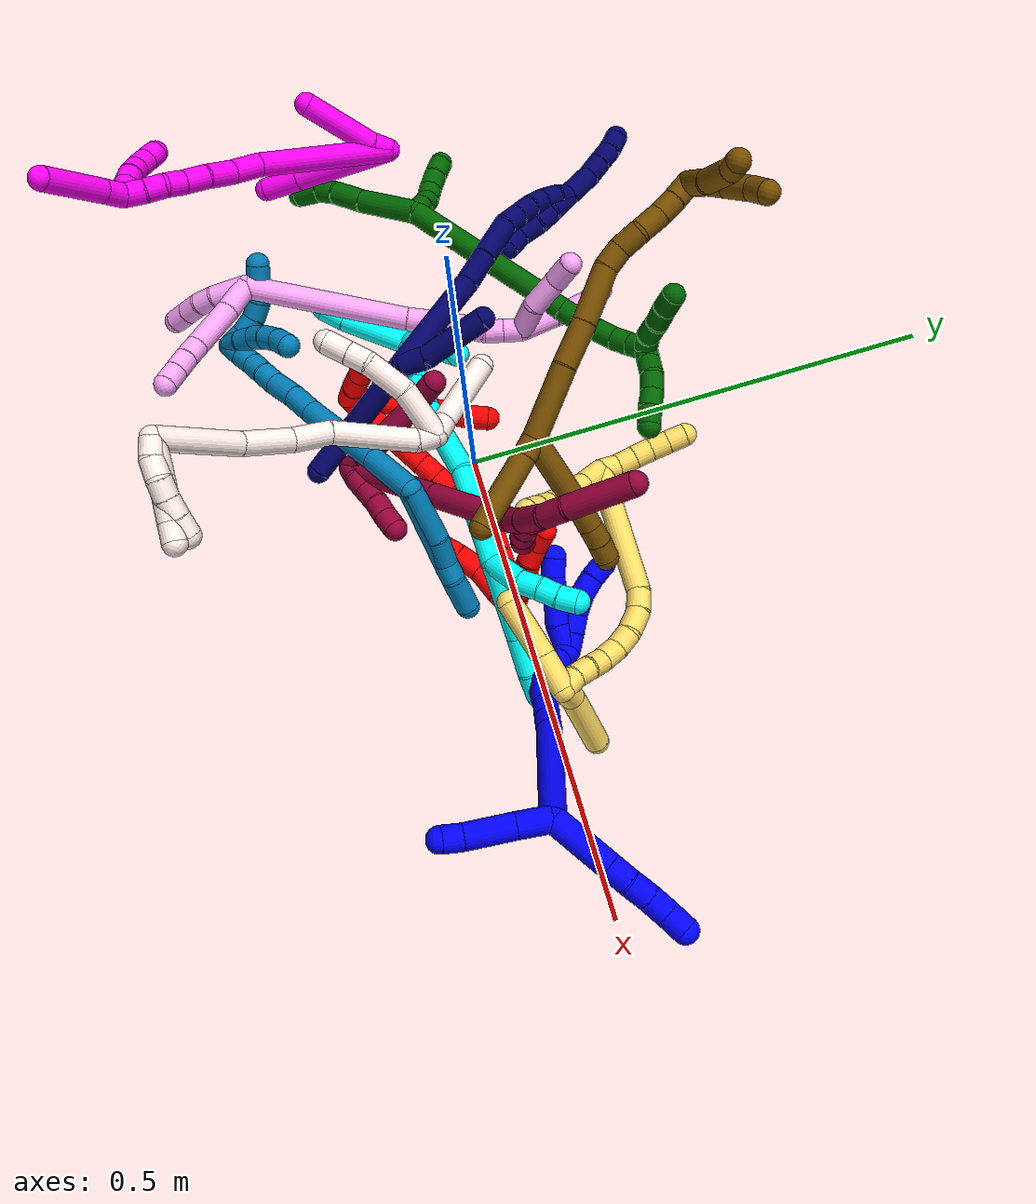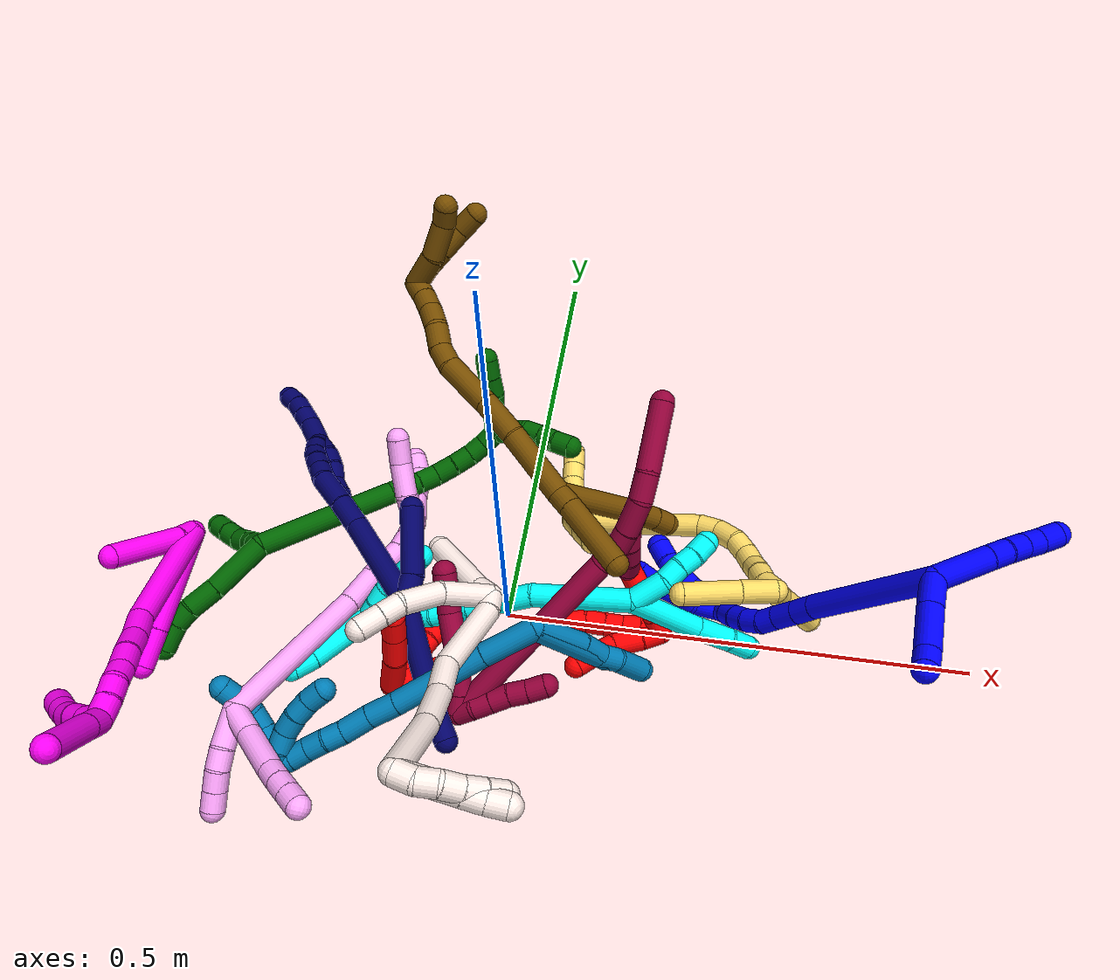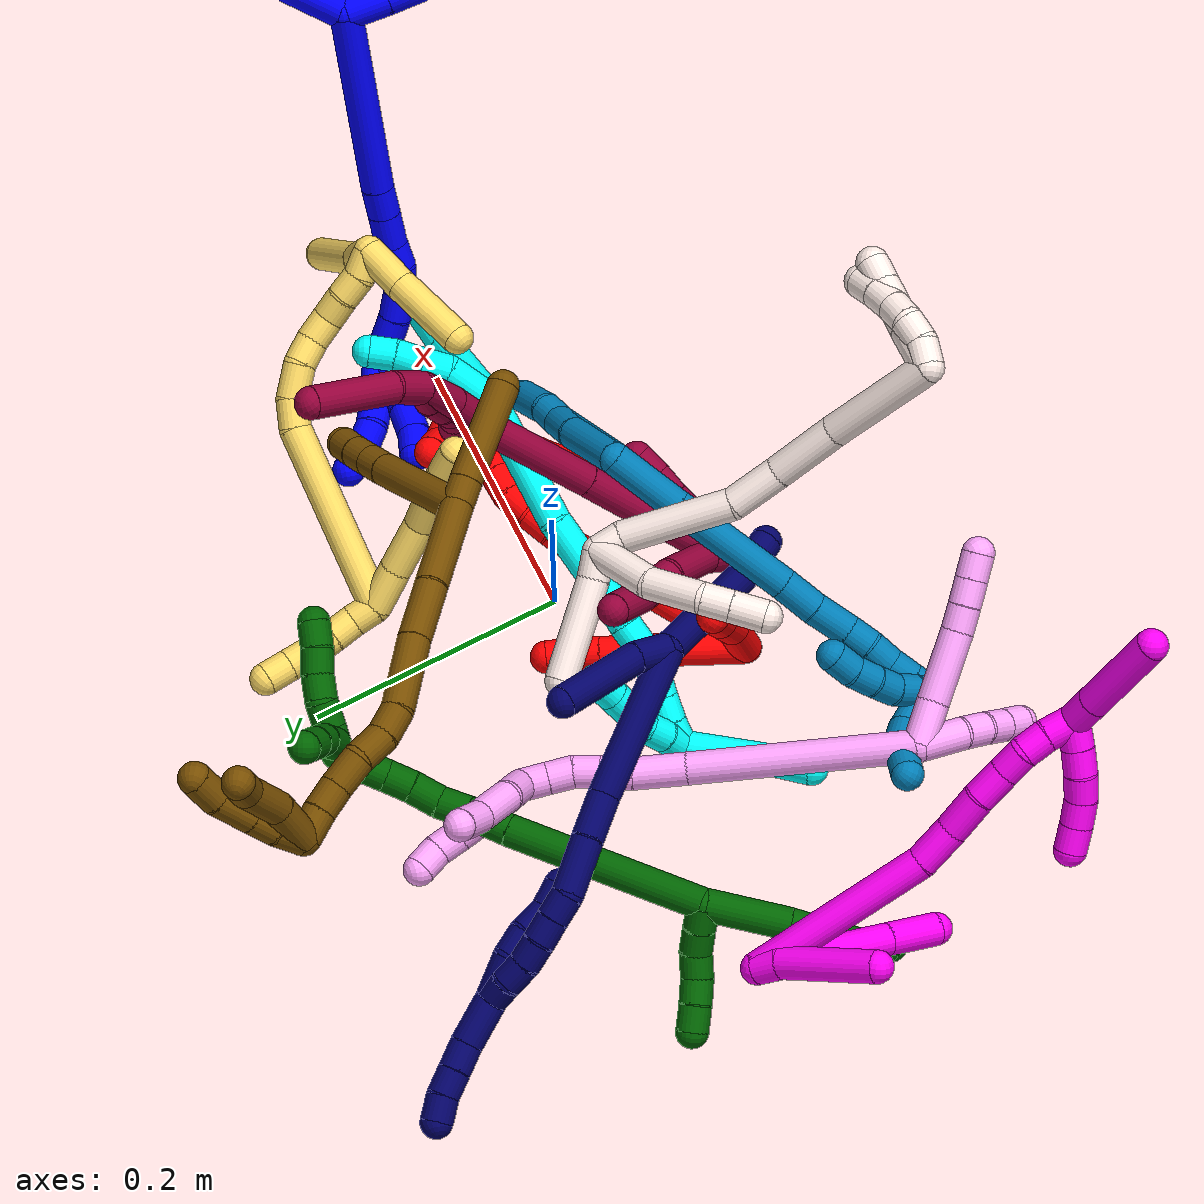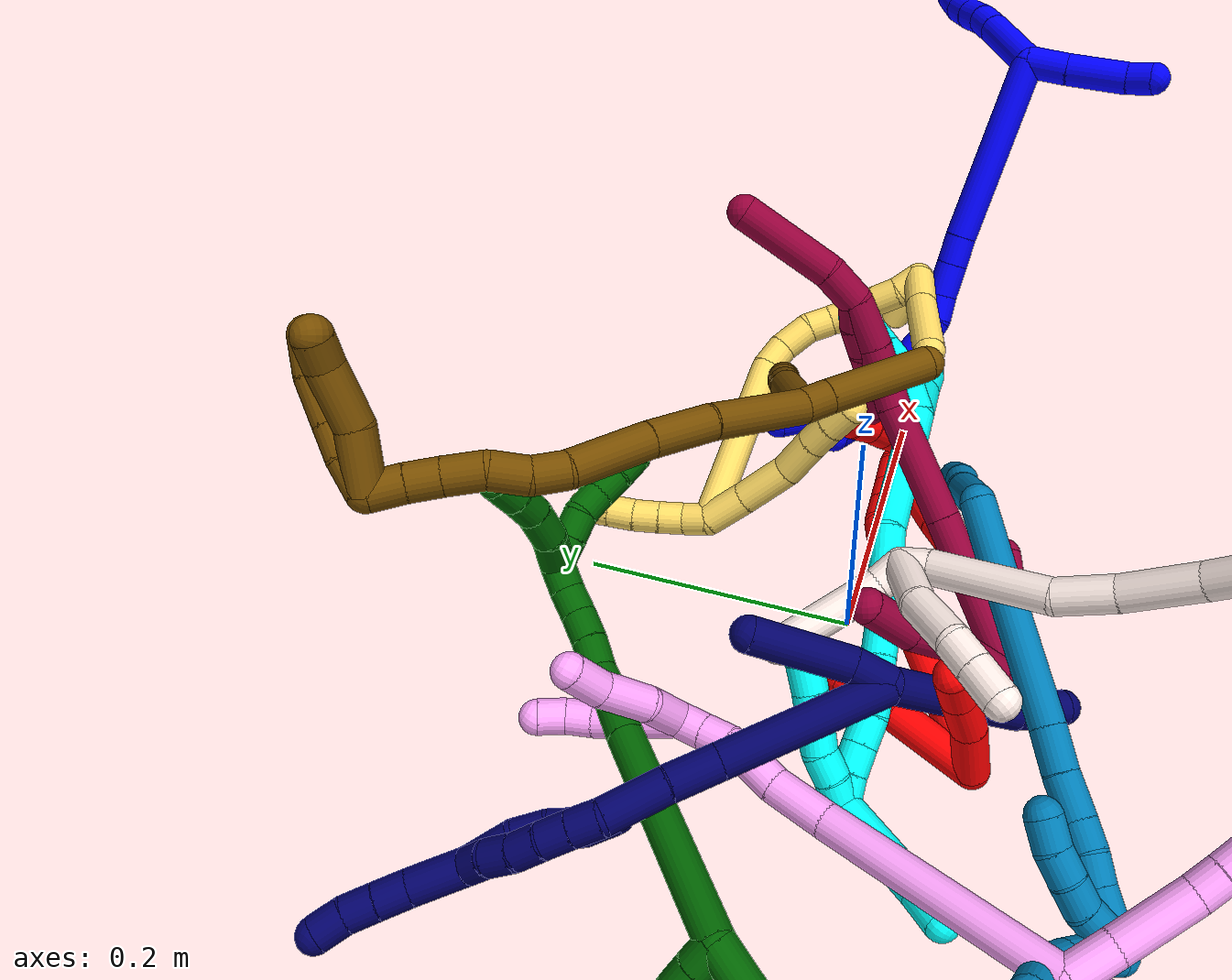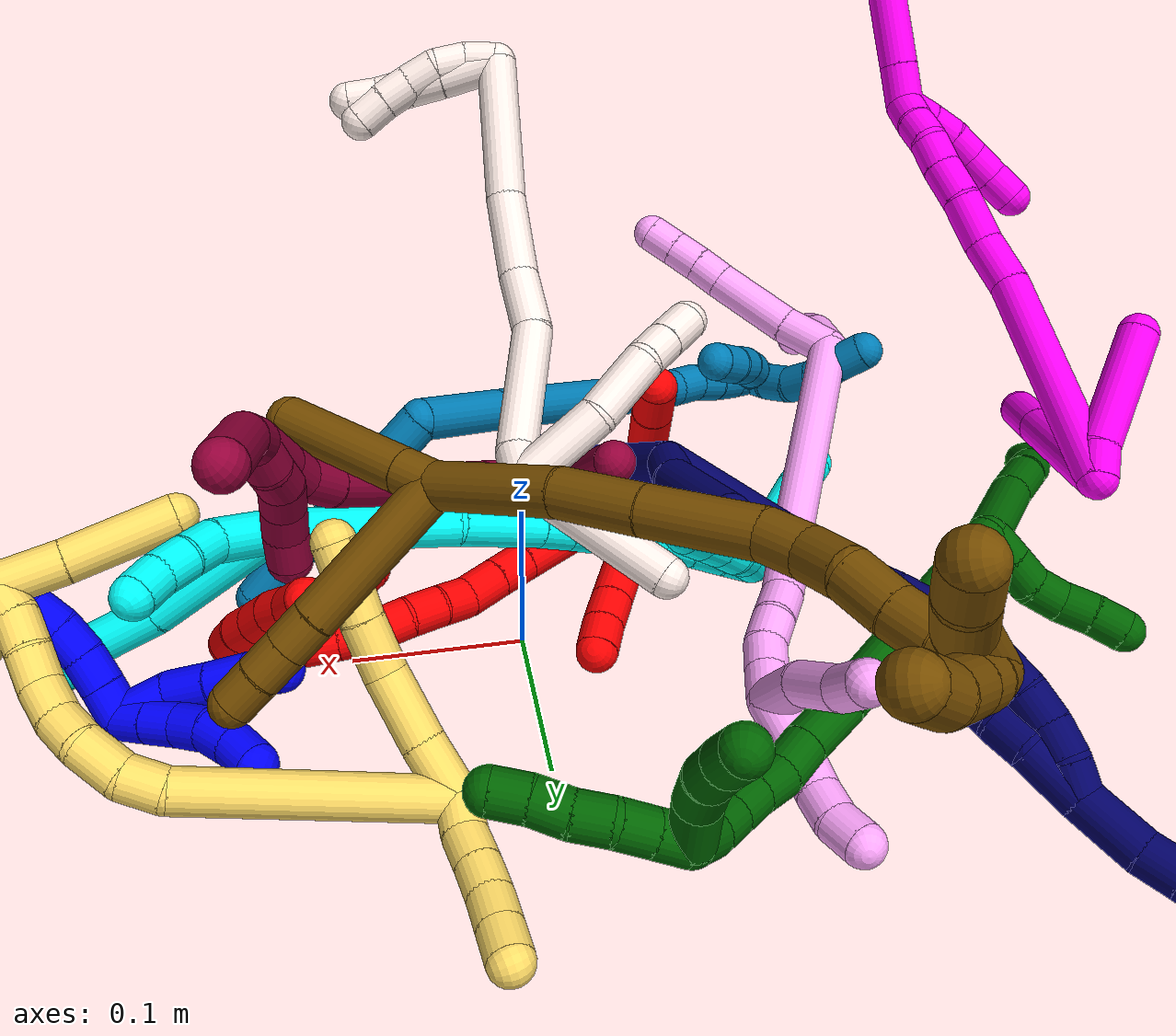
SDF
<sdf version="1.7">
 <world name="default">
  <plugin name="TubeGeneratorPlugin" filename="libtube_generator_plugin.so"/>
  <model name="photoneo_s_sensor">
   <static>1</static>
   <pose>0 0 2 1.57079 1.57079 3.14159</pose>
   <link name="link">
    <inertial><mass>0.1</mass></inertial>
    <sensor name="sensor" type="depth">
     <update_rate>30</update_rate>
     <camera>
      <horizontal_fov>1.22</horizontal_fov>
      <image><width>1920</width><height>1200</height><format>B8G8R8</format></image>
      <clip><near>0.1</near><far>4</far></clip>
      <depth_camera><output>points</output></depth_camera>
     </camera>
     <plugin name="camera_plugin" filename="libgazebo_ros_depth_camera.so">
      <baseline>0.2</baseline>
      <alwaysOn>1</alwaysOn>
      <updateRate>0.0</updateRate>
      <cameraName>camera_ir</cameraName>
      <imageTopicName>/camera/color/image_raw</imageTopicName>
      <cameraInfoTopicName>/camera/color/camera_info</cameraInfoTopicName>
      <depthImageTopicName>/camera/depth/image_raw</depthImageTopicName>
      <depthImageCameraInfoTopicName>/camera/depth/camera_info</depthImageCameraInfoTopicName>
      <pointCloudTopicName>/camera/depth/points</pointCloudTopicName>
      <frameName>fr_optical</frameName>
      <pointCloudCutoff>0.1</pointCloudCutoff>
      <pointCloudCutoffMax>2.0</pointCloudCutoffMax>
      <distortionK1>0</distortionK1>
      <distortionK2>0</distortionK2>
      <distortionK3>0</distortionK3>
      <distortionT1>0</distortionT1>
      <distortionT2>0</distortionT2>
      <CxPrime>0</CxPrime>
      <Cx>0</Cx>
      <Cy>0</Cy>
      <focalLength>0</focalLength>
      <hackBaseline>0</hackBaseline>
     </plugin>
    </sensor>
   </link>
  </model>
  <gravity>0 0 -9.8</gravity>
  <magnetic_field>6e-06 2.3e-05 -4.2e-05</magnetic_field>
  <atmosphere type="adiabatic"/>
  <physics name="default_physics" default="0" type="ode">
   <max_step_size>0.003</max_step_size>
   <real_time_factor>1</real_time_factor>
   <real_time_update_rate>1000</real_time_update_rate>
   <max_contacts>10000</max_contacts>
   <ode>
    <solver>
     <type>quick</type>
     <iters>100</iters>
     <sor>1.3</sor>
     <use_dynamic_moi_rescaling>0</use_dynamic_moi_rescaling>
    </solver>
    <constraints>
     <contact_max_correcting_vel>0</contact_max_correcting_vel>
     <contact_surface_layer>0.001</contact_surface_layer>
     <cfm>0</cfm>
     <erp>0.2</erp>
    </constraints>
   </ode>
  </physics>
  <scene><ambient>0.4 0.4 0.4 1</ambient><background>0.7 0.7 0.7 1</background><shadows>0</shadows></scene>
  <audio><device>default</device></audio>
  <spherical_coordinates>
   <surface_model>EARTH_WGS84</surface_model>
   <latitude_deg>0</latitude_deg>
   <longitude_deg>0</longitude_deg>
   <elevation>0</elevation>
   <heading_deg>0</heading_deg>
  </spherical_coordinates>
  <model name="bin">
   <static>1</static>
   <link name="bottom">
    <collision name="collision-bottom">
     <pose>0 0 -0.01 0 -0 0</pose>
     <geometry><box><size>0.8 0.6 0.02</size></box></geometry>
     <surface>
      <friction><ode><mu>100</mu><mu2>100</mu2></ode></friction>
      <contact><collide_bitmask>65535</collide_bitmask></contact>
     </surface>
    </collision>
   </link>
   <link name="west_wall">
    <collision name="collision-west_wall">
     <pose>-0.41 0 0.1 0 -0 0</pose>
     <geometry><box><size>0.02 0.6 0.2</size></box></geometry>
     <surface>
      <friction><ode><mu>100</mu><mu2>100</mu2></ode></friction>
      <contact><collide_bitmask>65535</collide_bitmask></contact>
     </surface>
    </collision>
   </link>
   <link name="east_wall">
    <collision name="collision-east_wall">
     <pose>0.41 0 0.1 0 -0 0</pose>
     <geometry><box><size>0.02 0.6 0.2</size></box></geometry>
     <surface>
      <friction><ode><mu>100</mu><mu2>100</mu2></ode></friction>
      <contact><collide_bitmask>65535</collide_bitmask></contact>
     </surface>
    </collision>
   </link>
   <link name="south_wall">
    <collision name="collision-south_wall">
     <pose>0 -0.31 0.1 0 -0 0</pose>
     <geometry><box><size>0.8 0.02 0.2</size></box></geometry>
     <surface>
      <friction><ode><mu>100</mu><mu2>100</mu2></ode></friction>
      <contact><collide_bitmask>65535</collide_bitmask></contact>
     </surface>
    </collision>
   </link>
   <link name="north_wall">
    <collision name="collision-north_wall">
     <pose>0 0.31 0.1 0 -0 0</pose>
     <geometry><box><size>0.8 0.02 0.2</size></box></geometry>
     <surface>
      <friction><ode><mu>100</mu><mu2>100</mu2></ode></friction>
      <contact><collide_bitmask>65535</collide_bitmask></contact>
     </surface>
    </collision>
   </link>
  </model>
  <model name="1">
   <static>0</static>
   <link name="1">
    <collision name="collision-cylinder-e_1_2_8">
     <pose>-0.022608 0.013577 0.016734 -0.681614 -0.809376 0.301505</pose>
     <geometry><cylinder><radius>0.0125</radius><length>0.062465</length></cylinder></geometry>
     <surface>
      <friction><ode><mu>1.16</mu><mu2>1.16</mu2><slip1>0</slip1><slip2>0</slip2></ode></friction>
      <contact><ode><kp>1e+06</kp><kd>1</kd><max_vel>0</max_vel><min_depth>0.001</min_depth></ode></contact>
     </surface>
    </collision>
    <visual name="visual-cylinder-e_1_2_8">
     <pose>-0.022608 0.013577 0.016734 -0.681614 -0.809376 0.301505</pose>
     <geometry><cylinder><radius>0.0125</radius><length>0.062465</length></cylinder></geometry>
     <material><ambient>0 0 1 1</ambient></material>
    </visual>
    <collision name="collision-cylinder-e_2_8_9">
     <pose>-0.053196 0.032397 0.039077 -0.751713 -0.804674 0.332753</pose>
     <geometry><cylinder><radius>0.0125</radius><length>0.022149</length></cylinder></geometry>
     <surface>
      <friction><ode><mu>1.16</mu><mu2>1.16</mu2><slip1>0</slip1><slip2>0</slip2></ode></friction>
      <contact><ode><kp>1e+06</kp><kd>1</kd><max_vel>0</max_vel><min_depth>0.001</min_depth></ode></contact>
     </surface>
    </collision>
    <visual name="visual-cylinder-e_2_8_9">
     <pose>-0.053196 0.032397 0.039077 -0.751713 -0.804674 0.332753</pose>
     <geometry><cylinder><radius>0.0125</radius><length>0.022149</length></cylinder></geometry>
     <material><ambient>0 0 1 1</ambient></material>
    </visual>
    <collision name="collision-cylinder-e_3_9_10">
     <pose>-0.069044 0.044118 0.04906 -0.976915 -0.788754 0.435317</pose>
     <geometry><cylinder><radius>0.0125</radius><length>0.022179</length></cylinder></geometry>
     <surface>
      <friction><ode><mu>1.16</mu><mu2>1.16</mu2><slip1>0</slip1><slip2>0</slip2></ode></friction>
      <contact><ode><kp>1e+06</kp><kd>1</kd><max_vel>0</max_vel><min_depth>0.001</min_depth></ode></contact>
     </surface>
    </collision>
    <visual name="visual-cylinder-e_3_9_10">
     <pose>-0.069044 0.044118 0.04906 -0.976915 -0.788754 0.435317</pose>
     <geometry><cylinder><radius>0.0125</radius><length>0.022179</length></cylinder></geometry>
     <material><ambient>0 0 1 1</ambient></material>
    </visual>
    <collision name="collision-cylinder-e_4_10_11">
     <pose>-0.084325 0.056676 0.058402 -0.885649 -0.756585 0.372584</pose>
     <geometry><cylinder><radius>0.0125</radius><length>0.0216</length></cylinder></geometry>
     <surface>
      <friction><ode><mu>1.16</mu><mu2>1.16</mu2><slip1>0</slip1><slip2>0</slip2></ode></friction>
      <contact><ode><kp>1e+06</kp><kd>1</kd><max_vel>0</max_vel><min_depth>0.001</min_depth></ode></contact>
     </surface>
    </collision>
    <visual name="visual-cylinder-e_4_10_11">
     <pose>-0.084325 0.056676 0.058402 -0.885649 -0.756585 0.372584</pose>
     <geometry><cylinder><radius>0.0125</radius><length>0.0216</length></cylinder></geometry>
     <material><ambient>0 0 1 1</ambient></material>
    </visual>
    <collision name="collision-cylinder-e_5_11_6">
     <pose>-0.099255 0.066833 0.069976 -0.552991 -0.76944 0.228786</pose>
     <geometry><cylinder><radius>0.0125</radius><length>0.021607</length></cylinder></geometry>
     <surface>
      <friction><ode><mu>1.16</mu><mu2>1.16</mu2><slip1>0</slip1><slip2>0</slip2></ode></friction>
      <contact><ode><kp>1e+06</kp><kd>1</kd><max_vel>0</max_vel><min_depth>0.001</min_depth></ode></contact>
     </surface>
    </collision>
    <visual name="visual-cylinder-e_5_11_6">
     <pose>-0.099255 0.066833 0.069976 -0.552991 -0.76944 0.228786</pose>
     <geometry><cylinder><radius>0.0125</radius><length>0.021607</length></cylinder></geometry>
     <material><ambient>0 0 1 1</ambient></material>
    </visual>
    <collision name="collision-cylinder-e_1_2_12">
     <pose>0.015794 -0.00089 0.002748 0.313049 1.38991 0.261639</pose>
     <geometry><cylinder><radius>0.0125</radius><length>0.032112</length></cylinder></geometry>
     <surface>
      <friction><ode><mu>1.16</mu><mu2>1.16</mu2><slip1>0</slip1><slip2>0</slip2></ode></friction>
      <contact><ode><kp>1e+06</kp><kd>1</kd><max_vel>0</max_vel><min_depth>0.001</min_depth></ode></contact>
     </surface>
    </collision>
    <visual name="visual-cylinder-e_1_2_12">
     <pose>0.015794 -0.00089 0.002748 0.313049 1.38991 0.261639</pose>
     <geometry><cylinder><radius>0.0125</radius><length>0.032112</length></cylinder></geometry>
     <material><ambient>0 0 1 1</ambient></material>
    </visual>
    <collision name="collision-cylinder-e_2_12_13">
     <pose>0.054817 -0.003467 0.010497 0.32549 1.34739 0.260667</pose>
     <geometry><cylinder><radius>0.0125</radius><length>0.047643</length></cylinder></geometry>
     <surface>
      <friction><ode><mu>1.16</mu><mu2>1.16</mu2><slip1>0</slip1><slip2>0</slip2></ode></friction>
      <contact><ode><kp>1e+06</kp><kd>1</kd><max_vel>0</max_vel><min_depth>0.001</min_depth></ode></contact>
     </surface>
    </collision>
    <visual name="visual-cylinder-e_2_12_13">
     <pose>0.054817 -0.003467 0.010497 0.32549 1.34739 0.260667</pose>
     <geometry><cylinder><radius>0.0125</radius><length>0.047643</length></cylinder></geometry>
     <material><ambient>0 0 1 1</ambient></material>
    </visual>
    <collision name="collision-cylinder-e_3_13_5">
     <pose>0.087476 -0.008098 0.017709 0.926416 1.19846 0.657501</pose>
     <geometry><cylinder><radius>0.0125</radius><length>0.020245</length></cylinder></geometry>
     <surface>
      <friction><ode><mu>1.16</mu><mu2>1.16</mu2><slip1>0</slip1><slip2>0</slip2></ode></friction>
      <contact><ode><kp>1e+06</kp><kd>1</kd><max_vel>0</max_vel><min_depth>0.001</min_depth></ode></contact>
     </surface>
    </collision>
    <visual name="visual-cylinder-e_3_13_5">
     <pose>0.087476 -0.008098 0.017709 0.926416 1.19846 0.657501</pose>
     <geometry><cylinder><radius>0.0125</radius><length>0.020245</length></cylinder></geometry>
     <material><ambient>0 0 1 1</ambient></material>
    </visual>
    <collision name="collision-cylinder-e_1_2_14">
     <pose>0.004584 0.031545 -0.066743 -2.70007 0.062015 -0.274685</pose>
     <geometry><cylinder><radius>0.0125</radius><length>0.147928</length></cylinder></geometry>
     <surface>
      <friction><ode><mu>1.16</mu><mu2>1.16</mu2><slip1>0</slip1><slip2>0</slip2></ode></friction>
      <contact><ode><kp>1e+06</kp><kd>1</kd><max_vel>0</max_vel><min_depth>0.001</min_depth></ode></contact>
     </surface>
    </collision>
    <visual name="visual-cylinder-e_1_2_14">
     <pose>0.004584 0.031545 -0.066743 -2.70007 0.062015 -0.274685</pose>
     <geometry><cylinder><radius>0.0125</radius><length>0.147928</length></cylinder></geometry>
     <material><ambient>0 0 1 1</ambient></material>
    </visual>
    <collision name="collision-cylinder-e_2_14_15">
     <pose>0.010535 0.06832 -0.143958 -2.67842 0.116296 -0.484044</pose>
     <geometry><cylinder><radius>0.0125</radius><length>0.023572</length></cylinder></geometry>
     <surface>
      <friction><ode><mu>1.16</mu><mu2>1.16</mu2><slip1>0</slip1><slip2>0</slip2></ode></friction>
      <contact><ode><kp>1e+06</kp><kd>1</kd><max_vel>0</max_vel><min_depth>0.001</min_depth></ode></contact>
     </surface>
    </collision>
    <visual name="visual-cylinder-e_2_14_15">
     <pose>0.010535 0.06832 -0.143958 -2.67842 0.116296 -0.484044</pose>
     <geometry><cylinder><radius>0.0125</radius><length>0.023572</length></cylinder></geometry>
     <material><ambient>0 0 1 1</ambient></material>
    </visual>
    <collision name="collision-cylinder-e_3_15_16">
     <pose>0.013372 0.079225 -0.166692 -2.70813 0.108318 -0.482816</pose>
     <geometry><cylinder><radius>0.0125</radius><length>0.02718</length></cylinder></geometry>
     <surface>
      <friction><ode><mu>1.16</mu><mu2>1.16</mu2><slip1>0</slip1><slip2>0</slip2></ode></friction>
      <contact><ode><kp>1e+06</kp><kd>1</kd><max_vel>0</max_vel><min_depth>0.001</min_depth></ode></contact>
     </surface>
    </collision>
    <visual name="visual-cylinder-e_3_15_16">
     <pose>0.013372 0.079225 -0.166692 -2.70813 0.108318 -0.482816</pose>
     <geometry><cylinder><radius>0.0125</radius><length>0.02718</length></cylinder></geometry>
     <material><ambient>0 0 1 1</ambient></material>
    </visual>
    <collision name="collision-cylinder-e_4_16_17">
     <pose>0.016986 0.088369 -0.18835 -2.78792 0.210942 -1.06963</pose>
     <geometry><cylinder><radius>0.0125</radius><length>0.020488</length></cylinder></geometry>
     <surface>
      <friction><ode><mu>1.16</mu><mu2>1.16</mu2><slip1>0</slip1><slip2>0</slip2></ode></friction>
      <contact><ode><kp>1e+06</kp><kd>1</kd><max_vel>0</max_vel><min_depth>0.001</min_depth></ode></contact>
     </surface>
    </collision>
    <visual name="visual-cylinder-e_4_16_17">
     <pose>0.016986 0.088369 -0.18835 -2.78792 0.210942 -1.06963</pose>
     <geometry><cylinder><radius>0.0125</radius><length>0.020488</length></cylinder></geometry>
     <material><ambient>0 0 1 1</ambient></material>
    </visual>
    <collision name="collision-cylinder-e_5_17_18">
     <pose>0.017885 0.094555 -0.207656 -2.87402 -0.120671 0.84378</pose>
     <geometry><cylinder><radius>0.0125</radius><length>0.0207</length></cylinder></geometry>
     <surface>
      <friction><ode><mu>1.16</mu><mu2>1.16</mu2><slip1>0</slip1><slip2>0</slip2></ode></friction>
      <contact><ode><kp>1e+06</kp><kd>1</kd><max_vel>0</max_vel><min_depth>0.001</min_depth></ode></contact>
     </surface>
    </collision>
    <visual name="visual-cylinder-e_5_17_18">
     <pose>0.017885 0.094555 -0.207656 -2.87402 -0.120671 0.84378</pose>
     <geometry><cylinder><radius>0.0125</radius><length>0.0207</length></cylinder></geometry>
     <material><ambient>0 0 1 1</ambient></material>
    </visual>
    <collision name="collision-cylinder-e_6_18_19">
     <pose>0.013758 0.100844 -0.226488 -2.76076 -0.291226 1.30078</pose>
     <geometry><cylinder><radius>0.0125</radius><length>0.020068</length></cylinder></geometry>
     <surface>
      <friction><ode><mu>1.16</mu><mu2>1.16</mu2><slip1>0</slip1><slip2>0</slip2></ode></friction>
      <contact><ode><kp>1e+06</kp><kd>1</kd><max_vel>0</max_vel><min_depth>0.001</min_depth></ode></contact>
     </surface>
    </collision>
    <visual name="visual-cylinder-e_6_18_19">
     <pose>0.013758 0.100844 -0.226488 -2.76076 -0.291226 1.30078</pose>
     <geometry><cylinder><radius>0.0125</radius><length>0.020068</length></cylinder></geometry>
     <material><ambient>0 0 1 1</ambient></material>
    </visual>
    <collision name="collision-cylinder-e_7_19_20">
     <pose>0.006892 0.108605 -0.243598 -2.66871 -0.408965 1.42134</pose>
     <geometry><cylinder><radius>0.0125</radius><length>0.020046</length></cylinder></geometry>
     <surface>
      <friction><ode><mu>1.16</mu><mu2>1.16</mu2><slip1>0</slip1><slip2>0</slip2></ode></friction>
      <contact><ode><kp>1e+06</kp><kd>1</kd><max_vel>0</max_vel><min_depth>0.001</min_depth></ode></contact>
     </surface>
    </collision>
    <visual name="visual-cylinder-e_7_19_20">
     <pose>0.006892 0.108605 -0.243598 -2.66871 -0.408965 1.42134</pose>
     <geometry><cylinder><radius>0.0125</radius><length>0.020046</length></cylinder></geometry>
     <material><ambient>0 0 1 1</ambient></material>
    </visual>
    <collision name="collision-cylinder-e_8_20_1">
     <pose>-0.001137 0.117382 -0.259708 -2.61663 -0.415834 1.33129</pose>
     <geometry><cylinder><radius>0.0125</radius><length>0.020018</length></cylinder></geometry>
     <surface>
      <friction><ode><mu>1.16</mu><mu2>1.16</mu2><slip1>0</slip1><slip2>0</slip2></ode></friction>
      <contact><ode><kp>1e+06</kp><kd>1</kd><max_vel>0</max_vel><min_depth>0.001</min_depth></ode></contact>
     </surface>
    </collision>
    <visual name="visual-cylinder-e_8_20_1">
     <pose>-0.001137 0.117382 -0.259708 -2.61663 -0.415834 1.33129</pose>
     <geometry><cylinder><radius>0.0125</radius><length>0.020018</length></cylinder></geometry>
     <material><ambient>0 0 1 1</ambient></material>
    </visual>
    <collision name="collision-cylinder-e_1_1_21">
     <pose>-0.008011 0.116315 -0.275377 2.51088 -0.286943 -0.833714</pose>
     <geometry><cylinder><radius>0.0125</radius><length>0.02</length></cylinder></geometry>
     <surface>
      <friction><ode><mu>1.16</mu><mu2>1.16</mu2><slip1>0</slip1><slip2>0</slip2></ode></friction>
      <contact><ode><kp>1e+06</kp><kd>1</kd><max_vel>0</max_vel><min_depth>0.001</min_depth></ode></contact>
     </surface>
    </collision>
    <visual name="visual-cylinder-e_1_1_21">
     <pose>-0.008011 0.116315 -0.275377 2.51088 -0.286943 -0.833714</pose>
     <geometry><cylinder><radius>0.0125</radius><length>0.02</length></cylinder></geometry>
     <material><ambient>0 0 1 1</ambient></material>
    </visual>
    <collision name="collision-cylinder-e_2_21_22">
     <pose>-0.01348 0.105056 -0.290975 2.52181 -0.267115 -0.794559</pose>
     <geometry><cylinder><radius>0.0125</radius><length>0.02</length></cylinder></geometry>
     <surface>
      <friction><ode><mu>1.16</mu><mu2>1.16</mu2><slip1>0</slip1><slip2>0</slip2></ode></friction>
      <contact><ode><kp>1e+06</kp><kd>1</kd><max_vel>0</max_vel><min_depth>0.001</min_depth></ode></contact>
     </surface>
    </collision>
    <visual name="visual-cylinder-e_2_21_22">
     <pose>-0.01348 0.105056 -0.290975 2.52181 -0.267115 -0.794559</pose>
     <geometry><cylinder><radius>0.0125</radius><length>0.02</length></cylinder></geometry>
     <material><ambient>0 0 1 1</ambient></material>
    </visual>
    <collision name="collision-cylinder-e_3_22_23">
     <pose>-0.01993 0.09349 -0.305891 2.44056 -0.390945 -0.992683</pose>
     <geometry><cylinder><radius>0.0125</radius><length>0.02</length></cylinder></geometry>
     <surface>
      <friction><ode><mu>1.16</mu><mu2>1.16</mu2><slip1>0</slip1><slip2>0</slip2></ode></friction>
      <contact><ode><kp>1e+06</kp><kd>1</kd><max_vel>0</max_vel><min_depth>0.001</min_depth></ode></contact>
     </surface>
    </collision>
    <visual name="visual-cylinder-e_3_22_23">
     <pose>-0.01993 0.09349 -0.305891 2.44056 -0.390945 -0.992683</pose>
     <geometry><cylinder><radius>0.0125</radius><length>0.02</length></cylinder></geometry>
     <material><ambient>0 0 1 1</ambient></material>
    </visual>
    <collision name="collision-cylinder-e_4_23_24">
     <pose>-0.029347 0.083673 -0.320286 2.65757 -0.595119 -1.7861</pose>
     <geometry><cylinder><radius>0.0125</radius><length>0.02</length></cylinder></geometry>
     <surface>
      <friction><ode><mu>1.16</mu><mu2>1.16</mu2><slip1>0</slip1><slip2>0</slip2></ode></friction>
      <contact><ode><kp>1e+06</kp><kd>1</kd><max_vel>0</max_vel><min_depth>0.001</min_depth></ode></contact>
     </surface>
    </collision>
    <visual name="visual-cylinder-e_4_23_24">
     <pose>-0.029347 0.083673 -0.320286 2.65757 -0.595119 -1.7861</pose>
     <geometry><cylinder><radius>0.0125</radius><length>0.02</length></cylinder></geometry>
     <material><ambient>0 0 1 1</ambient></material>
    </visual>
    <collision name="collision-cylinder-e_5_24_4">
     <pose>-0.04172 0.076825 -0.334342 2.7227 -0.743285 -2.14301</pose>
     <geometry><cylinder><radius>0.0125</radius><length>0.02</length></cylinder></geometry>
     <surface>
      <friction><ode><mu>1.16</mu><mu2>1.16</mu2><slip1>0</slip1><slip2>0</slip2></ode></friction>
      <contact><ode><kp>1e+06</kp><kd>1</kd><max_vel>0</max_vel><min_depth>0.001</min_depth></ode></contact>
     </surface>
    </collision>
    <visual name="visual-cylinder-e_5_24_4">
     <pose>-0.04172 0.076825 -0.334342 2.7227 -0.743285 -2.14301</pose>
     <geometry><cylinder><radius>0.0125</radius><length>0.02</length></cylinder></geometry>
     <material><ambient>0 0 1 1</ambient></material>
    </visual>
    <collision name="collision-cylinder-e_1_1_25">
     <pose>-0.000784 0.110793 -0.277292 2.2835 0.289239 0.616421</pose>
     <geometry><cylinder><radius>0.0125</radius><length>0.030828</length></cylinder></geometry>
     <surface>
      <friction><ode><mu>1.16</mu><mu2>1.16</mu2><slip1>0</slip1><slip2>0</slip2></ode></friction>
      <contact><ode><kp>1e+06</kp><kd>1</kd><max_vel>0</max_vel><min_depth>0.001</min_depth></ode></contact>
     </surface>
    </collision>
    <visual name="visual-cylinder-e_1_1_25">
     <pose>-0.000784 0.110793 -0.277292 2.2835 0.289239 0.616421</pose>
     <geometry><cylinder><radius>0.0125</radius><length>0.030828</length></cylinder></geometry>
     <material><ambient>0 0 1 1</ambient></material>
    </visual>
    <collision name="collision-cylinder-e_2_25_26">
     <pose>0.00329 0.090704 -0.296202 2.3748 -0.025119 -0.062258</pose>
     <geometry><cylinder><radius>0.0125</radius><length>0.025697</length></cylinder></geometry>
     <surface>
      <friction><ode><mu>1.16</mu><mu2>1.16</mu2><slip1>0</slip1><slip2>0</slip2></ode></friction>
      <contact><ode><kp>1e+06</kp><kd>1</kd><max_vel>0</max_vel><min_depth>0.001</min_depth></ode></contact>
     </surface>
    </collision>
    <visual name="visual-cylinder-e_2_25_26">
     <pose>0.00329 0.090704 -0.296202 2.3748 -0.025119 -0.062258</pose>
     <geometry><cylinder><radius>0.0125</radius><length>0.025697</length></cylinder></geometry>
     <material><ambient>0 0 1 1</ambient></material>
    </visual>
    <collision name="collision-cylinder-e_3_26_27">
     <pose>0.003592 0.073895 -0.313862 2.38766 0.054137 0.136564</pose>
     <geometry><cylinder><radius>0.0125</radius><length>0.023108</length></cylinder></geometry>
     <surface>
      <friction><ode><mu>1.16</mu><mu2>1.16</mu2><slip1>0</slip1><slip2>0</slip2></ode></friction>
      <contact><ode><kp>1e+06</kp><kd>1</kd><max_vel>0</max_vel><min_depth>0.001</min_depth></ode></contact>
     </surface>
    </collision>
    <visual name="visual-cylinder-e_3_26_27">
     <pose>0.003592 0.073895 -0.313862 2.38766 0.054137 0.136564</pose>
     <geometry><cylinder><radius>0.0125</radius><length>0.023108</length></cylinder></geometry>
     <material><ambient>0 0 1 1</ambient></material>
    </visual>
    <collision name="collision-cylinder-e_4_27_3">
     <pose>0.002669 0.05884 -0.329349 2.35053 -0.15261 -0.362199</pose>
     <geometry><cylinder><radius>0.0125</radius><length>0.020368</length></cylinder></geometry>
     <surface>
      <friction><ode><mu>1.16</mu><mu2>1.16</mu2><slip1>0</slip1><slip2>0</slip2></ode></friction>
      <contact><ode><kp>1e+06</kp><kd>1</kd><max_vel>0</max_vel><min_depth>0.001</min_depth></ode></contact>
     </surface>
    </collision>
    <visual name="visual-cylinder-e_4_27_3">
     <pose>0.002669 0.05884 -0.329349 2.35053 -0.15261 -0.362199</pose>
     <geometry><cylinder><radius>0.0125</radius><length>0.020368</length></cylinder></geometry>
     <material><ambient>0 0 1 1</ambient></material>
    </visual>
    <collision name="collision-sphere-3">
     <pose>0.001121 0.051683 -0.336426 0 -0 0</pose>
     <geometry><sphere><radius>0.0125</radius></sphere></geometry>
     <surface>
      <friction><ode><mu>1.16</mu><mu2>1.16</mu2><slip1>0</slip1><slip2>0</slip2></ode></friction>
      <contact><ode><kp>1e+06</kp><kd>1</kd><max_vel>0</max_vel><min_depth>0.001</min_depth></ode></contact>
     </surface>
    </collision>
    <visual name="visual-sphere-3">
     <pose>0.001121 0.051683 -0.336426 0 -0 0</pose>
     <geometry><sphere><radius>0.0125</radius></sphere></geometry>
     <material><ambient>0 0 1 1</ambient></material>
    </visual>
    <collision name="collision-sphere-27">
     <pose>0.004217 0.065998 -0.322273 0 -0 0</pose>
     <geometry><sphere><radius>0.0125</radius></sphere></geometry>
     <surface>
      <friction><ode><mu>1.16</mu><mu2>1.16</mu2><slip1>0</slip1><slip2>0</slip2></ode></friction>
      <contact><ode><kp>1e+06</kp><kd>1</kd><max_vel>0</max_vel><min_depth>0.001</min_depth></ode></contact>
     </surface>
    </collision>
    <visual name="visual-sphere-27">
     <pose>0.004217 0.065998 -0.322273 0 -0 0</pose>
     <geometry><sphere><radius>0.0125</radius></sphere></geometry>
     <material><ambient>0 0 1 1</ambient></material>
    </visual>
    <collision name="collision-sphere-26">
     <pose>0.002967 0.081792 -0.305451 0 -0 0</pose>
     <geometry><sphere><radius>0.0125</radius></sphere></geometry>
     <surface>
      <friction><ode><mu>1.16</mu><mu2>1.16</mu2><slip1>0</slip1><slip2>0</slip2></ode></friction>
      <contact><ode><kp>1e+06</kp><kd>1</kd><max_vel>0</max_vel><min_depth>0.001</min_depth></ode></contact>
     </surface>
    </collision>
    <visual name="visual-sphere-26">
     <pose>0.002967 0.081792 -0.305451 0 -0 0</pose>
     <geometry><sphere><radius>0.0125</radius></sphere></geometry>
     <material><ambient>0 0 1 1</ambient></material>
    </visual>
    <collision name="collision-sphere-25">
     <pose>0.003612 0.099616 -0.286952 0 -0 0</pose>
     <geometry><sphere><radius>0.0125</radius></sphere></geometry>
     <surface>
      <friction><ode><mu>1.16</mu><mu2>1.16</mu2><slip1>0</slip1><slip2>0</slip2></ode></friction>
      <contact><ode><kp>1e+06</kp><kd>1</kd><max_vel>0</max_vel><min_depth>0.001</min_depth></ode></contact>
     </surface>
    </collision>
    <visual name="visual-sphere-25">
     <pose>0.003612 0.099616 -0.286952 0 -0 0</pose>
     <geometry><sphere><radius>0.0125</radius></sphere></geometry>
     <material><ambient>0 0 1 1</ambient></material>
    </visual>
    <collision name="collision-sphere-4">
     <pose>-0.048487 0.073831 -0.341068 0 -0 0</pose>
     <geometry><sphere><radius>0.0125</radius></sphere></geometry>
     <surface>
      <friction><ode><mu>1.16</mu><mu2>1.16</mu2><slip1>0</slip1><slip2>0</slip2></ode></friction>
      <contact><ode><kp>1e+06</kp><kd>1</kd><max_vel>0</max_vel><min_depth>0.001</min_depth></ode></contact>
     </surface>
    </collision>
    <visual name="visual-sphere-4">
     <pose>-0.048487 0.073831 -0.341068 0 -0 0</pose>
     <geometry><sphere><radius>0.0125</radius></sphere></geometry>
     <material><ambient>0 0 1 1</ambient></material>
    </visual>
    <collision name="collision-sphere-24">
     <pose>-0.034953 0.07982 -0.327616 0 -0 0</pose>
     <geometry><sphere><radius>0.0125</radius></sphere></geometry>
     <surface>
      <friction><ode><mu>1.16</mu><mu2>1.16</mu2><slip1>0</slip1><slip2>0</slip2></ode></friction>
      <contact><ode><kp>1e+06</kp><kd>1</kd><max_vel>0</max_vel><min_depth>0.001</min_depth></ode></contact>
     </surface>
    </collision>
    <visual name="visual-sphere-24">
     <pose>-0.034953 0.07982 -0.327616 0 -0 0</pose>
     <geometry><sphere><radius>0.0125</radius></sphere></geometry>
     <material><ambient>0 0 1 1</ambient></material>
    </visual>
    <collision name="collision-sphere-23">
     <pose>-0.023741 0.087527 -0.312956 0 -0 0</pose>
     <geometry><sphere><radius>0.0125</radius></sphere></geometry>
     <surface>
      <friction><ode><mu>1.16</mu><mu2>1.16</mu2><slip1>0</slip1><slip2>0</slip2></ode></friction>
      <contact><ode><kp>1e+06</kp><kd>1</kd><max_vel>0</max_vel><min_depth>0.001</min_depth></ode></contact>
     </surface>
    </collision>
    <visual name="visual-sphere-23">
     <pose>-0.023741 0.087527 -0.312956 0 -0 0</pose>
     <geometry><sphere><radius>0.0125</radius></sphere></geometry>
     <material><ambient>0 0 1 1</ambient></material>
    </visual>
    <collision name="collision-sphere-22">
     <pose>-0.01612 0.099453 -0.298826 0 -0 0</pose>
     <geometry><sphere><radius>0.0125</radius></sphere></geometry>
     <surface>
      <friction><ode><mu>1.16</mu><mu2>1.16</mu2><slip1>0</slip1><slip2>0</slip2></ode></friction>
      <contact><ode><kp>1e+06</kp><kd>1</kd><max_vel>0</max_vel><min_depth>0.001</min_depth></ode></contact>
     </surface>
    </collision>
    <visual name="visual-sphere-22">
     <pose>-0.01612 0.099453 -0.298826 0 -0 0</pose>
     <geometry><sphere><radius>0.0125</radius></sphere></geometry>
     <material><ambient>0 0 1 1</ambient></material>
    </visual>
    <collision name="collision-sphere-21">
     <pose>-0.010841 0.110659 -0.283123 0 -0 0</pose>
     <geometry><sphere><radius>0.0125</radius></sphere></geometry>
     <surface>
      <friction><ode><mu>1.16</mu><mu2>1.16</mu2><slip1>0</slip1><slip2>0</slip2></ode></friction>
      <contact><ode><kp>1e+06</kp><kd>1</kd><max_vel>0</max_vel><min_depth>0.001</min_depth></ode></contact>
     </surface>
    </collision>
    <visual name="visual-sphere-21">
     <pose>-0.010841 0.110659 -0.283123 0 -0 0</pose>
     <geometry><sphere><radius>0.0125</radius></sphere></geometry>
     <material><ambient>0 0 1 1</ambient></material>
    </visual>
    <collision name="collision-sphere-1">
     <pose>-0.00518 0.121971 -0.267632 0 -0 0</pose>
     <geometry><sphere><radius>0.0125</radius></sphere></geometry>
     <surface>
      <friction><ode><mu>1.16</mu><mu2>1.16</mu2><slip1>0</slip1><slip2>0</slip2></ode></friction>
      <contact><ode><kp>1e+06</kp><kd>1</kd><max_vel>0</max_vel><min_depth>0.001</min_depth></ode></contact>
     </surface>
    </collision>
    <visual name="visual-sphere-1">
     <pose>-0.00518 0.121971 -0.267632 0 -0 0</pose>
     <geometry><sphere><radius>0.0125</radius></sphere></geometry>
     <material><ambient>0 0 1 1</ambient></material>
    </visual>
    <collision name="collision-sphere-6">
     <pose>-0.106772 0.070909 0.076579 0 -0 0</pose>
     <geometry><sphere><radius>0.0125</radius></sphere></geometry>
     <surface>
      <friction><ode><mu>1.16</mu><mu2>1.16</mu2><slip1>0</slip1><slip2>0</slip2></ode></friction>
      <contact><ode><kp>1e+06</kp><kd>1</kd><max_vel>0</max_vel><min_depth>0.001</min_depth></ode></contact>
     </surface>
    </collision>
    <visual name="visual-sphere-6">
     <pose>-0.106772 0.070909 0.076579 0 -0 0</pose>
     <geometry><sphere><radius>0.0125</radius></sphere></geometry>
     <material><ambient>0 0 1 1</ambient></material>
    </visual>
    <collision name="collision-sphere-11">
     <pose>-0.091739 0.062757 0.063372 0 -0 0</pose>
     <geometry><sphere><radius>0.0125</radius></sphere></geometry>
     <surface>
      <friction><ode><mu>1.16</mu><mu2>1.16</mu2><slip1>0</slip1><slip2>0</slip2></ode></friction>
      <contact><ode><kp>1e+06</kp><kd>1</kd><max_vel>0</max_vel><min_depth>0.001</min_depth></ode></contact>
     </surface>
    </collision>
    <visual name="visual-sphere-11">
     <pose>-0.091739 0.062757 0.063372 0 -0 0</pose>
     <geometry><sphere><radius>0.0125</radius></sphere></geometry>
     <material><ambient>0 0 1 1</ambient></material>
    </visual>
    <collision name="collision-sphere-10">
     <pose>-0.076912 0.050595 0.053433 0 -0 0</pose>
     <geometry><sphere><radius>0.0125</radius></sphere></geometry>
     <surface>
      <friction><ode><mu>1.16</mu><mu2>1.16</mu2><slip1>0</slip1><slip2>0</slip2></ode></friction>
      <contact><ode><kp>1e+06</kp><kd>1</kd><max_vel>0</max_vel><min_depth>0.001</min_depth></ode></contact>
     </surface>
    </collision>
    <visual name="visual-sphere-10">
     <pose>-0.076912 0.050595 0.053433 0 -0 0</pose>
     <geometry><sphere><radius>0.0125</radius></sphere></geometry>
     <material><ambient>0 0 1 1</ambient></material>
    </visual>
    <collision name="collision-sphere-9">
     <pose>-0.061177 0.037641 0.044687 0 -0 0</pose>
     <geometry><sphere><radius>0.0125</radius></sphere></geometry>
     <surface>
      <friction><ode><mu>1.16</mu><mu2>1.16</mu2><slip1>0</slip1><slip2>0</slip2></ode></friction>
      <contact><ode><kp>1e+06</kp><kd>1</kd><max_vel>0</max_vel><min_depth>0.001</min_depth></ode></contact>
     </surface>
    </collision>
    <visual name="visual-sphere-9">
     <pose>-0.061177 0.037641 0.044687 0 -0 0</pose>
     <geometry><sphere><radius>0.0125</radius></sphere></geometry>
     <material><ambient>0 0 1 1</ambient></material>
    </visual>
    <collision name="collision-sphere-2">
     <geometry><sphere><radius>0.0125</radius></sphere></geometry>
     <surface>
      <friction><ode><mu>1.16</mu><mu2>1.16</mu2><slip1>0</slip1><slip2>0</slip2></ode></friction>
      <contact><ode><kp>1e+06</kp><kd>1</kd><max_vel>0</max_vel><min_depth>0.001</min_depth></ode></contact>
     </surface>
    </collision>
    <visual name="visual-sphere-2">
     <geometry><sphere><radius>0.0125</radius></sphere></geometry>
     <material><ambient>0 0 1 1</ambient></material>
    </visual>
    <collision name="collision-sphere-19">
     <pose>0.010877 0.104416 -0.235411 0 -0 0</pose>
     <geometry><sphere><radius>0.0125</radius></sphere></geometry>
     <surface>
      <friction><ode><mu>1.16</mu><mu2>1.16</mu2><slip1>0</slip1><slip2>0</slip2></ode></friction>
      <contact><ode><kp>1e+06</kp><kd>1</kd><max_vel>0</max_vel><min_depth>0.001</min_depth></ode></contact>
     </surface>
    </collision>
    <visual name="visual-sphere-19">
     <pose>0.010877 0.104416 -0.235411 0 -0 0</pose>
     <geometry><sphere><radius>0.0125</radius></sphere></geometry>
     <material><ambient>0 0 1 1</ambient></material>
    </visual>
    <collision name="collision-sphere-8">
     <pose>-0.045216 0.027154 0.033468 0 -0 0</pose>
     <geometry><sphere><radius>0.0125</radius></sphere></geometry>
     <surface>
      <friction><ode><mu>1.16</mu><mu2>1.16</mu2><slip1>0</slip1><slip2>0</slip2></ode></friction>
      <contact><ode><kp>1e+06</kp><kd>1</kd><max_vel>0</max_vel><min_depth>0.001</min_depth></ode></contact>
     </surface>
    </collision>
    <visual name="visual-sphere-8">
     <pose>-0.045216 0.027154 0.033468 0 -0 0</pose>
     <geometry><sphere><radius>0.0125</radius></sphere></geometry>
     <material><ambient>0 0 1 1</ambient></material>
    </visual>
    <collision name="collision-sphere-12">
     <pose>0.031588 -0.001779 0.005496 0 -0 0</pose>
     <geometry><sphere><radius>0.0125</radius></sphere></geometry>
     <surface>
      <friction><ode><mu>1.16</mu><mu2>1.16</mu2><slip1>0</slip1><slip2>0</slip2></ode></friction>
      <contact><ode><kp>1e+06</kp><kd>1</kd><max_vel>0</max_vel><min_depth>0.001</min_depth></ode></contact>
     </surface>
    </collision>
    <visual name="visual-sphere-12">
     <pose>0.031588 -0.001779 0.005496 0 -0 0</pose>
     <geometry><sphere><radius>0.0125</radius></sphere></geometry>
     <material><ambient>0 0 1 1</ambient></material>
    </visual>
    <collision name="collision-sphere-13">
     <pose>0.078047 -0.005154 0.015497 0 -0 0</pose>
     <geometry><sphere><radius>0.0125</radius></sphere></geometry>
     <surface>
      <friction><ode><mu>1.16</mu><mu2>1.16</mu2><slip1>0</slip1><slip2>0</slip2></ode></friction>
      <contact><ode><kp>1e+06</kp><kd>1</kd><max_vel>0</max_vel><min_depth>0.001</min_depth></ode></contact>
     </surface>
    </collision>
    <visual name="visual-sphere-13">
     <pose>0.078047 -0.005154 0.015497 0 -0 0</pose>
     <geometry><sphere><radius>0.0125</radius></sphere></geometry>
     <material><ambient>0 0 1 1</ambient></material>
    </visual>
    <collision name="collision-sphere-5">
     <pose>0.096905 -0.011042 0.019921 0 -0 0</pose>
     <geometry><sphere><radius>0.0125</radius></sphere></geometry>
     <surface>
      <friction><ode><mu>1.16</mu><mu2>1.16</mu2><slip1>0</slip1><slip2>0</slip2></ode></friction>
      <contact><ode><kp>1e+06</kp><kd>1</kd><max_vel>0</max_vel><min_depth>0.001</min_depth></ode></contact>
     </surface>
    </collision>
    <visual name="visual-sphere-5">
     <pose>0.096905 -0.011042 0.019921 0 -0 0</pose>
     <geometry><sphere><radius>0.0125</radius></sphere></geometry>
     <material><ambient>0 0 1 1</ambient></material>
    </visual>
    <collision name="collision-sphere-14">
     <pose>0.009168 0.06309 -0.133485 0 -0 0</pose>
     <geometry><sphere><radius>0.0125</radius></sphere></geometry>
     <surface>
      <friction><ode><mu>1.16</mu><mu2>1.16</mu2><slip1>0</slip1><slip2>0</slip2></ode></friction>
      <contact><ode><kp>1e+06</kp><kd>1</kd><max_vel>0</max_vel><min_depth>0.001</min_depth></ode></contact>
     </surface>
    </collision>
    <visual name="visual-sphere-14">
     <pose>0.009168 0.06309 -0.133485 0 -0 0</pose>
     <geometry><sphere><radius>0.0125</radius></sphere></geometry>
     <material><ambient>0 0 1 1</ambient></material>
    </visual>
    <collision name="collision-sphere-15">
     <pose>0.011903 0.07355 -0.154431 0 -0 0</pose>
     <geometry><sphere><radius>0.0125</radius></sphere></geometry>
     <surface>
      <friction><ode><mu>1.16</mu><mu2>1.16</mu2><slip1>0</slip1><slip2>0</slip2></ode></friction>
      <contact><ode><kp>1e+06</kp><kd>1</kd><max_vel>0</max_vel><min_depth>0.001</min_depth></ode></contact>
     </surface>
    </collision>
    <visual name="visual-sphere-15">
     <pose>0.011903 0.07355 -0.154431 0 -0 0</pose>
     <geometry><sphere><radius>0.0125</radius></sphere></geometry>
     <material><ambient>0 0 1 1</ambient></material>
    </visual>
    <collision name="collision-sphere-16">
     <pose>0.014841 0.084899 -0.178953 0 -0 0</pose>
     <geometry><sphere><radius>0.0125</radius></sphere></geometry>
     <surface>
      <friction><ode><mu>1.16</mu><mu2>1.16</mu2><slip1>0</slip1><slip2>0</slip2></ode></friction>
      <contact><ode><kp>1e+06</kp><kd>1</kd><max_vel>0</max_vel><min_depth>0.001</min_depth></ode></contact>
     </surface>
    </collision>
    <visual name="visual-sphere-16">
     <pose>0.014841 0.084899 -0.178953 0 -0 0</pose>
     <geometry><sphere><radius>0.0125</radius></sphere></geometry>
     <material><ambient>0 0 1 1</ambient></material>
    </visual>
    <collision name="collision-sphere-17">
     <pose>0.019131 0.091838 -0.197747 0 -0 0</pose>
     <geometry><sphere><radius>0.0125</radius></sphere></geometry>
     <surface>
      <friction><ode><mu>1.16</mu><mu2>1.16</mu2><slip1>0</slip1><slip2>0</slip2></ode></friction>
      <contact><ode><kp>1e+06</kp><kd>1</kd><max_vel>0</max_vel><min_depth>0.001</min_depth></ode></contact>
     </surface>
    </collision>
    <visual name="visual-sphere-17">
     <pose>0.019131 0.091838 -0.197747 0 -0 0</pose>
     <geometry><sphere><radius>0.0125</radius></sphere></geometry>
     <material><ambient>0 0 1 1</ambient></material>
    </visual>
    <collision name="collision-sphere-18">
     <pose>0.016639 0.097271 -0.217565 0 -0 0</pose>
     <geometry><sphere><radius>0.0125</radius></sphere></geometry>
     <surface>
      <friction><ode><mu>1.16</mu><mu2>1.16</mu2><slip1>0</slip1><slip2>0</slip2></ode></friction>
      <contact><ode><kp>1e+06</kp><kd>1</kd><max_vel>0</max_vel><min_depth>0.001</min_depth></ode></contact>
     </surface>
    </collision>
    <visual name="visual-sphere-18">
     <pose>0.016639 0.097271 -0.217565 0 -0 0</pose>
     <geometry><sphere><radius>0.0125</radius></sphere></geometry>
     <material><ambient>0 0 1 1</ambient></material>
    </visual>
    <collision name="collision-sphere-20">
     <pose>0.002906 0.112793 -0.251785 0 -0 0</pose>
     <geometry><sphere><radius>0.0125</radius></sphere></geometry>
     <surface>
      <friction><ode><mu>1.16</mu><mu2>1.16</mu2><slip1>0</slip1><slip2>0</slip2></ode></friction>
      <contact><ode><kp>1e+06</kp><kd>1</kd><max_vel>0</max_vel><min_depth>0.001</min_depth></ode></contact>
     </surface>
    </collision>
    <visual name="visual-sphere-20">
     <pose>0.002906 0.112793 -0.251785 0 -0 0</pose>
     <geometry><sphere><radius>0.0125</radius></sphere></geometry>
     <material><ambient>0 0 1 1</ambient></material>
    </visual>
    <inertial>
     <pose>-0.003801 0.055684 -0.126027 0 -0 0</pose>
     <mass>0.75</mass>
     <inertia>
      <ixx>0.000232</ixx>
      <ixy>0</ixy>
      <ixz>0</ixz>
      <iyy>-0.000271</iyy>
      <iyz>0</iyz>
      <izz>-0.000157</izz>
     </inertia>
    </inertial>
   </link>
   <pose>0.411111 -0.038787 0.231659 -1.14753 0.097282 -1.81523</pose>
  </model>
  <model name="2">
   <static>0</static>
   <link name="2">
    <collision name="collision-cylinder-e_1_2_8">
     <pose>0.008065 0.022264 0.021499 -0.802859 0.254921 -0.108691</pose>
     <geometry><cylinder><radius>0.0125</radius><length>0.063967</length></cylinder></geometry>
     <surface>
      <friction><ode><mu>1.16</mu><mu2>1.16</mu2><slip1>0</slip1><slip2>0</slip2></ode></friction>
      <contact><ode><kp>1e+06</kp><kd>1</kd><max_vel>0</max_vel><min_depth>0.001</min_depth></ode></contact>
     </surface>
    </collision>
    <visual name="visual-cylinder-e_1_2_8">
     <pose>0.008065 0.022264 0.021499 -0.802859 0.254921 -0.108691</pose>
     <geometry><cylinder><radius>0.0125</radius><length>0.063967</length></cylinder></geometry>
     <material><ambient>1 0 0 1</ambient></material>
    </visual>
    <collision name="collision-cylinder-e_2_8_9">
     <pose>0.02296 0.061784 0.056096 -0.921611 0.305377 -0.152498</pose>
     <geometry><cylinder><radius>0.0125</radius><length>0.04543</length></cylinder></geometry>
     <surface>
      <friction><ode><mu>1.16</mu><mu2>1.16</mu2><slip1>0</slip1><slip2>0</slip2></ode></friction>
      <contact><ode><kp>1e+06</kp><kd>1</kd><max_vel>0</max_vel><min_depth>0.001</min_depth></ode></contact>
     </surface>
    </collision>
    <visual name="visual-cylinder-e_2_8_9">
     <pose>0.02296 0.061784 0.056096 -0.921611 0.305377 -0.152498</pose>
     <geometry><cylinder><radius>0.0125</radius><length>0.04543</length></cylinder></geometry>
     <material><ambient>1 0 0 1</ambient></material>
    </visual>
    <collision name="collision-cylinder-e_3_9_10">
     <pose>0.032749 0.086766 0.075226 -0.907708 0.293273 -0.143849</pose>
     <geometry><cylinder><radius>0.0125</radius><length>0.020478</length></cylinder></geometry>
     <surface>
      <friction><ode><mu>1.16</mu><mu2>1.16</mu2><slip1>0</slip1><slip2>0</slip2></ode></friction>
      <contact><ode><kp>1e+06</kp><kd>1</kd><max_vel>0</max_vel><min_depth>0.001</min_depth></ode></contact>
     </surface>
    </collision>
    <visual name="visual-cylinder-e_3_9_10">
     <pose>0.032749 0.086766 0.075226 -0.907708 0.293273 -0.143849</pose>
     <geometry><cylinder><radius>0.0125</radius><length>0.020478</length></cylinder></geometry>
     <material><ambient>1 0 0 1</ambient></material>
    </visual>
    <collision name="collision-cylinder-e_4_10_6">
     <pose>0.037877 0.102221 0.087325 -0.905451 0.217193 -0.105965</pose>
     <geometry><cylinder><radius>0.0125</radius><length>0.020125</length></cylinder></geometry>
     <surface>
      <friction><ode><mu>1.16</mu><mu2>1.16</mu2><slip1>0</slip1><slip2>0</slip2></ode></friction>
      <contact><ode><kp>1e+06</kp><kd>1</kd><max_vel>0</max_vel><min_depth>0.001</min_depth></ode></contact>
     </surface>
    </collision>
    <visual name="visual-cylinder-e_4_10_6">
     <pose>0.037877 0.102221 0.087325 -0.905451 0.217193 -0.105965</pose>
     <geometry><cylinder><radius>0.0125</radius><length>0.020125</length></cylinder></geometry>
     <material><ambient>1 0 0 1</ambient></material>
    </visual>
    <collision name="collision-cylinder-e_1_2_11">
     <pose>-0.002258 -0.009813 0.019276 0.470905 -0.103997 -0.02497</pose>
     <geometry><cylinder><radius>0.0125</radius><length>0.043495</length></cylinder></geometry>
     <surface>
      <friction><ode><mu>1.16</mu><mu2>1.16</mu2><slip1>0</slip1><slip2>0</slip2></ode></friction>
      <contact><ode><kp>1e+06</kp><kd>1</kd><max_vel>0</max_vel><min_depth>0.001</min_depth></ode></contact>
     </surface>
    </collision>
    <visual name="visual-cylinder-e_1_2_11">
     <pose>-0.002258 -0.009813 0.019276 0.470905 -0.103997 -0.02497</pose>
     <geometry><cylinder><radius>0.0125</radius><length>0.043495</length></cylinder></geometry>
     <material><ambient>1 0 0 1</ambient></material>
    </visual>
    <collision name="collision-cylinder-e_2_11_12">
     <pose>-0.008447 -0.02506 0.053308 0.352816 -0.245017 -0.04389</pose>
     <geometry><cylinder><radius>0.0125</radius><length>0.032418</length></cylinder></geometry>
     <surface>
      <friction><ode><mu>1.16</mu><mu2>1.16</mu2><slip1>0</slip1><slip2>0</slip2></ode></friction>
      <contact><ode><kp>1e+06</kp><kd>1</kd><max_vel>0</max_vel><min_depth>0.001</min_depth></ode></contact>
     </surface>
    </collision>
    <visual name="visual-cylinder-e_2_11_12">
     <pose>-0.008447 -0.02506 0.053308 0.352816 -0.245017 -0.04389</pose>
     <geometry><cylinder><radius>0.0125</radius><length>0.032418</length></cylinder></geometry>
     <material><ambient>1 0 0 1</ambient></material>
    </visual>
    <collision name="collision-cylinder-e_3_12_5">
     <pose>-0.015573 -0.035049 0.078746 0.403057 -0.268434 -0.055159</pose>
     <geometry><cylinder><radius>0.0125</radius><length>0.024087</length></cylinder></geometry>
     <surface>
      <friction><ode><mu>1.16</mu><mu2>1.16</mu2><slip1>0</slip1><slip2>0</slip2></ode></friction>
      <contact><ode><kp>1e+06</kp><kd>1</kd><max_vel>0</max_vel><min_depth>0.001</min_depth></ode></contact>
     </surface>
    </collision>
    <visual name="visual-cylinder-e_3_12_5">
     <pose>-0.015573 -0.035049 0.078746 0.403057 -0.268434 -0.055159</pose>
     <geometry><cylinder><radius>0.0125</radius><length>0.024087</length></cylinder></geometry>
     <material><ambient>1 0 0 1</ambient></material>
    </visual>
    <collision name="collision-cylinder-e_1_2_13">
     <pose>0.040643 0.022228 0.027603 -0.677945 0.853669 -0.317997</pose>
     <geometry><cylinder><radius>0.0125</radius><length>0.107849</length></cylinder></geometry>
     <surface>
      <friction><ode><mu>1.16</mu><mu2>1.16</mu2><slip1>0</slip1><slip2>0</slip2></ode></friction>
      <contact><ode><kp>1e+06</kp><kd>1</kd><max_vel>0</max_vel><min_depth>0.001</min_depth></ode></contact>
     </surface>
    </collision>
    <visual name="visual-cylinder-e_1_2_13">
     <pose>0.040643 0.022228 0.027603 -0.677945 0.853669 -0.317997</pose>
     <geometry><cylinder><radius>0.0125</radius><length>0.107849</length></cylinder></geometry>
     <material><ambient>1 0 0 1</ambient></material>
    </visual>
    <collision name="collision-cylinder-e_2_13_14">
     <pose>0.08945 0.049102 0.060715 -0.700655 0.847649 -0.326774</pose>
     <geometry><cylinder><radius>0.0125</radius><length>0.02178</length></cylinder></geometry>
     <surface>
      <friction><ode><mu>1.16</mu><mu2>1.16</mu2><slip1>0</slip1><slip2>0</slip2></ode></friction>
      <contact><ode><kp>1e+06</kp><kd>1</kd><max_vel>0</max_vel><min_depth>0.001</min_depth></ode></contact>
     </surface>
    </collision>
    <visual name="visual-cylinder-e_2_13_14">
     <pose>0.08945 0.049102 0.060715 -0.700655 0.847649 -0.326774</pose>
     <geometry><cylinder><radius>0.0125</radius><length>0.02178</length></cylinder></geometry>
     <material><ambient>1 0 0 1</ambient></material>
    </visual>
    <collision name="collision-cylinder-e_3_14_15">
     <pose>0.106553 0.058945 0.072085 -0.725405 0.851228 -0.340729</pose>
     <geometry><cylinder><radius>0.0125</radius><length>0.02377</length></cylinder></geometry>
     <surface>
      <friction><ode><mu>1.16</mu><mu2>1.16</mu2><slip1>0</slip1><slip2>0</slip2></ode></friction>
      <contact><ode><kp>1e+06</kp><kd>1</kd><max_vel>0</max_vel><min_depth>0.001</min_depth></ode></contact>
     </surface>
    </collision>
    <visual name="visual-cylinder-e_3_14_15">
     <pose>0.106553 0.058945 0.072085 -0.725405 0.851228 -0.340729</pose>
     <geometry><cylinder><radius>0.0125</radius><length>0.02377</length></cylinder></geometry>
     <material><ambient>1 0 0 1</ambient></material>
    </visual>
    <collision name="collision-cylinder-e_4_15_16">
     <pose>0.122381 0.066387 0.084925 -0.311252 0.754356 -0.124146</pose>
     <geometry><cylinder><radius>0.0125</radius><length>0.020122</length></cylinder></geometry>
     <surface>
      <friction><ode><mu>1.16</mu><mu2>1.16</mu2><slip1>0</slip1><slip2>0</slip2></ode></friction>
      <contact><ode><kp>1e+06</kp><kd>1</kd><max_vel>0</max_vel><min_depth>0.001</min_depth></ode></contact>
     </surface>
    </collision>
    <visual name="visual-cylinder-e_4_15_16">
     <pose>0.122381 0.066387 0.084925 -0.311252 0.754356 -0.124146</pose>
     <geometry><cylinder><radius>0.0125</radius><length>0.020122</length></cylinder></geometry>
     <material><ambient>1 0 0 1</ambient></material>
    </visual>
    <collision name="collision-cylinder-e_5_16_17">
     <pose>0.137716 0.071285 0.098153 -0.401404 0.893643 -0.19434</pose>
     <geometry><cylinder><radius>0.0125</radius><length>0.021671</length></cylinder></geometry>
     <surface>
      <friction><ode><mu>1.16</mu><mu2>1.16</mu2><slip1>0</slip1><slip2>0</slip2></ode></friction>
      <contact><ode><kp>1e+06</kp><kd>1</kd><max_vel>0</max_vel><min_depth>0.001</min_depth></ode></contact>
     </surface>
    </collision>
    <visual name="visual-cylinder-e_5_16_17">
     <pose>0.137716 0.071285 0.098153 -0.401404 0.893643 -0.19434</pose>
     <geometry><cylinder><radius>0.0125</radius><length>0.021671</length></cylinder></geometry>
     <material><ambient>1 0 0 1</ambient></material>
    </visual>
    <collision name="collision-cylinder-e_6_17_18">
     <pose>0.155295 0.076996 0.108796 -0.608142 1.0407 -0.35583</pose>
     <geometry><cylinder><radius>0.0125</radius><length>0.021174</length></cylinder></geometry>
     <surface>
      <friction><ode><mu>1.16</mu><mu2>1.16</mu2><slip1>0</slip1><slip2>0</slip2></ode></friction>
      <contact><ode><kp>1e+06</kp><kd>1</kd><max_vel>0</max_vel><min_depth>0.001</min_depth></ode></contact>
     </surface>
    </collision>
    <visual name="visual-cylinder-e_6_17_18">
     <pose>0.155295 0.076996 0.108796 -0.608142 1.0407 -0.35583</pose>
     <geometry><cylinder><radius>0.0125</radius><length>0.021174</length></cylinder></geometry>
     <material><ambient>1 0 0 1</ambient></material>
    </visual>
    <collision name="collision-cylinder-e_7_18_19">
     <pose>0.174919 0.081016 0.115369 -0.415896 1.3475 -0.333779</pose>
     <geometry><cylinder><radius>0.0125</radius><length>0.021514</length></cylinder></geometry>
     <surface>
      <friction><ode><mu>1.16</mu><mu2>1.16</mu2><slip1>0</slip1><slip2>0</slip2></ode></friction>
      <contact><ode><kp>1e+06</kp><kd>1</kd><max_vel>0</max_vel><min_depth>0.001</min_depth></ode></contact>
     </surface>
    </collision>
    <visual name="visual-cylinder-e_7_18_19">
     <pose>0.174919 0.081016 0.115369 -0.415896 1.3475 -0.333779</pose>
     <geometry><cylinder><radius>0.0125</radius><length>0.021514</length></cylinder></geometry>
     <material><ambient>1 0 0 1</ambient></material>
    </visual>
    <collision name="collision-cylinder-e_8_19_20">
     <pose>0.195417 0.082531 0.119941 -0.226565 1.33009 -0.17797</pose>
     <geometry><cylinder><radius>0.0125</radius><length>0.02061</length></cylinder></geometry>
     <surface>
      <friction><ode><mu>1.16</mu><mu2>1.16</mu2><slip1>0</slip1><slip2>0</slip2></ode></friction>
      <contact><ode><kp>1e+06</kp><kd>1</kd><max_vel>0</max_vel><min_depth>0.001</min_depth></ode></contact>
     </surface>
    </collision>
    <visual name="visual-cylinder-e_8_19_20">
     <pose>0.195417 0.082531 0.119941 -0.226565 1.33009 -0.17797</pose>
     <geometry><cylinder><radius>0.0125</radius><length>0.02061</length></cylinder></geometry>
     <material><ambient>1 0 0 1</ambient></material>
    </visual>
    <collision name="collision-cylinder-e_9_20_21">
     <pose>0.214916 0.082049 0.126656 0.234856 1.13304 0.149794</pose>
     <geometry><cylinder><radius>0.0125</radius><length>0.02096</length></cylinder></geometry>
     <surface>
      <friction><ode><mu>1.16</mu><mu2>1.16</mu2><slip1>0</slip1><slip2>0</slip2></ode></friction>
      <contact><ode><kp>1e+06</kp><kd>1</kd><max_vel>0</max_vel><min_depth>0.001</min_depth></ode></contact>
     </surface>
    </collision>
    <visual name="visual-cylinder-e_9_20_21">
     <pose>0.214916 0.082049 0.126656 0.234856 1.13304 0.149794</pose>
     <geometry><cylinder><radius>0.0125</radius><length>0.02096</length></cylinder></geometry>
     <material><ambient>1 0 0 1</ambient></material>
    </visual>
    <collision name="collision-cylinder-e_10_21_1">
     <pose>0.234227 0.078727 0.132959 0.85678 1.27171 0.650237</pose>
     <geometry><cylinder><radius>0.0125</radius><length>0.02055</length></cylinder></geometry>
     <surface>
      <friction><ode><mu>1.16</mu><mu2>1.16</mu2><slip1>0</slip1><slip2>0</slip2></ode></friction>
      <contact><ode><kp>1e+06</kp><kd>1</kd><max_vel>0</max_vel><min_depth>0.001</min_depth></ode></contact>
     </surface>
    </collision>
    <visual name="visual-cylinder-e_10_21_1">
     <pose>0.234227 0.078727 0.132959 0.85678 1.27171 0.650237</pose>
     <geometry><cylinder><radius>0.0125</radius><length>0.02055</length></cylinder></geometry>
     <material><ambient>1 0 0 1</ambient></material>
    </visual>
    <collision name="collision-cylinder-e_1_1_22">
     <pose>0.235813 0.072938 0.129003 2.60898 -0.873737 -2.08419</pose>
     <geometry><cylinder><radius>0.0125</radius><length>0.021477</length></cylinder></geometry>
     <surface>
      <friction><ode><mu>1.16</mu><mu2>1.16</mu2><slip1>0</slip1><slip2>0</slip2></ode></friction>
      <contact><ode><kp>1e+06</kp><kd>1</kd><max_vel>0</max_vel><min_depth>0.001</min_depth></ode></contact>
     </surface>
    </collision>
    <visual name="visual-cylinder-e_1_1_22">
     <pose>0.235813 0.072938 0.129003 2.60898 -0.873737 -2.08419</pose>
     <geometry><cylinder><radius>0.0125</radius><length>0.021477</length></cylinder></geometry>
     <material><ambient>1 0 0 1</ambient></material>
    </visual>
    <collision name="collision-cylinder-e_2_22_23">
     <pose>0.214767 0.06584 0.115035 2.72032 -0.969033 -2.36992</pose>
     <geometry><cylinder><radius>0.0125</radius><length>0.031086</length></cylinder></geometry>
     <surface>
      <friction><ode><mu>1.16</mu><mu2>1.16</mu2><slip1>0</slip1><slip2>0</slip2></ode></friction>
      <contact><ode><kp>1e+06</kp><kd>1</kd><max_vel>0</max_vel><min_depth>0.001</min_depth></ode></contact>
     </surface>
    </collision>
    <visual name="visual-cylinder-e_2_22_23">
     <pose>0.214767 0.06584 0.115035 2.72032 -0.969033 -2.36992</pose>
     <geometry><cylinder><radius>0.0125</radius><length>0.031086</length></cylinder></geometry>
     <material><ambient>1 0 0 1</ambient></material>
    </visual>
    <collision name="collision-cylinder-e_3_23_24">
     <pose>0.193099 0.055557 0.099285 2.42799 -0.71435 -1.57194</pose>
     <geometry><cylinder><radius>0.0125</radius><length>0.027034</length></cylinder></geometry>
     <surface>
      <friction><ode><mu>1.16</mu><mu2>1.16</mu2><slip1>0</slip1><slip2>0</slip2></ode></friction>
      <contact><ode><kp>1e+06</kp><kd>1</kd><max_vel>0</max_vel><min_depth>0.001</min_depth></ode></contact>
     </surface>
    </collision>
    <visual name="visual-cylinder-e_3_23_24">
     <pose>0.193099 0.055557 0.099285 2.42799 -0.71435 -1.57194</pose>
     <geometry><cylinder><radius>0.0125</radius><length>0.027034</length></cylinder></geometry>
     <material><ambient>1 0 0 1</ambient></material>
    </visual>
    <collision name="collision-cylinder-e_4_24_4">
     <pose>0.178164 0.043384 0.085482 2.40754 -0.638387 -1.42016</pose>
     <geometry><cylinder><radius>0.0125</radius><length>0.020404</length></cylinder></geometry>
     <surface>
      <friction><ode><mu>1.16</mu><mu2>1.16</mu2><slip1>0</slip1><slip2>0</slip2></ode></friction>
      <contact><ode><kp>1e+06</kp><kd>1</kd><max_vel>0</max_vel><min_depth>0.001</min_depth></ode></contact>
     </surface>
    </collision>
    <visual name="visual-cylinder-e_4_24_4">
     <pose>0.178164 0.043384 0.085482 2.40754 -0.638387 -1.42016</pose>
     <geometry><cylinder><radius>0.0125</radius><length>0.020404</length></cylinder></geometry>
     <material><ambient>1 0 0 1</ambient></material>
    </visual>
    <collision name="collision-cylinder-e_1_1_25">
     <pose>0.237765 0.074795 0.142548 0.212835 -0.679102 -0.075429</pose>
     <geometry><cylinder><radius>0.0125</radius><length>0.02</length></cylinder></geometry>
     <surface>
      <friction><ode><mu>1.16</mu><mu2>1.16</mu2><slip1>0</slip1><slip2>0</slip2></ode></friction>
      <contact><ode><kp>1e+06</kp><kd>1</kd><max_vel>0</max_vel><min_depth>0.001</min_depth></ode></contact>
     </surface>
    </collision>
    <visual name="visual-cylinder-e_1_1_25">
     <pose>0.237765 0.074795 0.142548 0.212835 -0.679102 -0.075429</pose>
     <geometry><cylinder><radius>0.0125</radius><length>0.02</length></cylinder></geometry>
     <material><ambient>1 0 0 1</ambient></material>
    </visual>
    <collision name="collision-cylinder-e_2_25_26">
     <pose>0.224042 0.072415 0.156792 0.110487 -0.839338 -0.049337</pose>
     <geometry><cylinder><radius>0.0125</radius><length>0.02</length></cylinder></geometry>
     <surface>
      <friction><ode><mu>1.16</mu><mu2>1.16</mu2><slip1>0</slip1><slip2>0</slip2></ode></friction>
      <contact><ode><kp>1e+06</kp><kd>1</kd><max_vel>0</max_vel><min_depth>0.001</min_depth></ode></contact>
     </surface>
    </collision>
    <visual name="visual-cylinder-e_2_25_26">
     <pose>0.224042 0.072415 0.156792 0.110487 -0.839338 -0.049337</pose>
     <geometry><cylinder><radius>0.0125</radius><length>0.02</length></cylinder></geometry>
     <material><ambient>1 0 0 1</ambient></material>
    </visual>
    <collision name="collision-cylinder-e_3_26_27">
     <pose>0.209347 0.070753 0.170253 0.134823 -0.811519 -0.057992</pose>
     <geometry><cylinder><radius>0.0125</radius><length>0.02</length></cylinder></geometry>
     <surface>
      <friction><ode><mu>1.16</mu><mu2>1.16</mu2><slip1>0</slip1><slip2>0</slip2></ode></friction>
      <contact><ode><kp>1e+06</kp><kd>1</kd><max_vel>0</max_vel><min_depth>0.001</min_depth></ode></contact>
     </surface>
    </collision>
    <visual name="visual-cylinder-e_3_26_27">
     <pose>0.209347 0.070753 0.170253 0.134823 -0.811519 -0.057992</pose>
     <geometry><cylinder><radius>0.0125</radius><length>0.02</length></cylinder></geometry>
     <material><ambient>1 0 0 1</ambient></material>
    </visual>
    <collision name="collision-cylinder-e_4_27_28">
     <pose>0.194584 0.070363 0.183656 -0.081122 -0.849509 0.036707</pose>
     <geometry><cylinder><radius>0.0125</radius><length>0.02</length></cylinder></geometry>
     <surface>
      <friction><ode><mu>1.16</mu><mu2>1.16</mu2><slip1>0</slip1><slip2>0</slip2></ode></friction>
      <contact><ode><kp>1e+06</kp><kd>1</kd><max_vel>0</max_vel><min_depth>0.001</min_depth></ode></contact>
     </surface>
    </collision>
    <visual name="visual-cylinder-e_4_27_28">
     <pose>0.194584 0.070363 0.183656 -0.081122 -0.849509 0.036707</pose>
     <geometry><cylinder><radius>0.0125</radius><length>0.02</length></cylinder></geometry>
     <material><ambient>1 0 0 1</ambient></material>
    </visual>
    <collision name="collision-cylinder-e_5_28_3">
     <pose>0.180632 0.070872 0.197886 0.003364 -0.700088 -0.001228</pose>
     <geometry><cylinder><radius>0.0125</radius><length>0.02</length></cylinder></geometry>
     <surface>
      <friction><ode><mu>1.16</mu><mu2>1.16</mu2><slip1>0</slip1><slip2>0</slip2></ode></friction>
      <contact><ode><kp>1e+06</kp><kd>1</kd><max_vel>0</max_vel><min_depth>0.001</min_depth></ode></contact>
     </surface>
    </collision>
    <visual name="visual-cylinder-e_5_28_3">
     <pose>0.180632 0.070872 0.197886 0.003364 -0.700088 -0.001228</pose>
     <geometry><cylinder><radius>0.0125</radius><length>0.02</length></cylinder></geometry>
     <material><ambient>1 0 0 1</ambient></material>
    </visual>
    <collision name="collision-sphere-3">
     <pose>0.174189 0.070847 0.205533 0 -0 0</pose>
     <geometry><sphere><radius>0.0125</radius></sphere></geometry>
     <surface>
      <friction><ode><mu>1.16</mu><mu2>1.16</mu2><slip1>0</slip1><slip2>0</slip2></ode></friction>
      <contact><ode><kp>1e+06</kp><kd>1</kd><max_vel>0</max_vel><min_depth>0.001</min_depth></ode></contact>
     </surface>
    </collision>
    <visual name="visual-sphere-3">
     <pose>0.174189 0.070847 0.205533 0 -0 0</pose>
     <geometry><sphere><radius>0.0125</radius></sphere></geometry>
     <material><ambient>1 0 0 1</ambient></material>
    </visual>
    <collision name="collision-sphere-28">
     <pose>0.187075 0.070898 0.190238 0 -0 0</pose>
     <geometry><sphere><radius>0.0125</radius></sphere></geometry>
     <surface>
      <friction><ode><mu>1.16</mu><mu2>1.16</mu2><slip1>0</slip1><slip2>0</slip2></ode></friction>
      <contact><ode><kp>1e+06</kp><kd>1</kd><max_vel>0</max_vel><min_depth>0.001</min_depth></ode></contact>
     </surface>
    </collision>
    <visual name="visual-sphere-28">
     <pose>0.187075 0.070898 0.190238 0 -0 0</pose>
     <geometry><sphere><radius>0.0125</radius></sphere></geometry>
     <material><ambient>1 0 0 1</ambient></material>
    </visual>
    <collision name="collision-sphere-27">
     <pose>0.202094 0.069828 0.177074 0 -0 0</pose>
     <geometry><sphere><radius>0.0125</radius></sphere></geometry>
     <surface>
      <friction><ode><mu>1.16</mu><mu2>1.16</mu2><slip1>0</slip1><slip2>0</slip2></ode></friction>
      <contact><ode><kp>1e+06</kp><kd>1</kd><max_vel>0</max_vel><min_depth>0.001</min_depth></ode></contact>
     </surface>
    </collision>
    <visual name="visual-sphere-27">
     <pose>0.202094 0.069828 0.177074 0 -0 0</pose>
     <geometry><sphere><radius>0.0125</radius></sphere></geometry>
     <material><ambient>1 0 0 1</ambient></material>
    </visual>
    <collision name="collision-sphere-26">
     <pose>0.2166 0.071678 0.163431 0 -0 0</pose>
     <geometry><sphere><radius>0.0125</radius></sphere></geometry>
     <surface>
      <friction><ode><mu>1.16</mu><mu2>1.16</mu2><slip1>0</slip1><slip2>0</slip2></ode></friction>
      <contact><ode><kp>1e+06</kp><kd>1</kd><max_vel>0</max_vel><min_depth>0.001</min_depth></ode></contact>
     </surface>
    </collision>
    <visual name="visual-sphere-26">
     <pose>0.2166 0.071678 0.163431 0 -0 0</pose>
     <geometry><sphere><radius>0.0125</radius></sphere></geometry>
     <material><ambient>1 0 0 1</ambient></material>
    </visual>
    <collision name="collision-sphere-25">
     <pose>0.231484 0.073151 0.150154 0 -0 0</pose>
     <geometry><sphere><radius>0.0125</radius></sphere></geometry>
     <surface>
      <friction><ode><mu>1.16</mu><mu2>1.16</mu2><slip1>0</slip1><slip2>0</slip2></ode></friction>
      <contact><ode><kp>1e+06</kp><kd>1</kd><max_vel>0</max_vel><min_depth>0.001</min_depth></ode></contact>
     </surface>
    </collision>
    <visual name="visual-sphere-25">
     <pose>0.231484 0.073151 0.150154 0 -0 0</pose>
     <geometry><sphere><radius>0.0125</radius></sphere></geometry>
     <material><ambient>1 0 0 1</ambient></material>
    </visual>
    <collision name="collision-sphere-4">
     <pose>0.172085 0.037896 0.079399 0 -0 0</pose>
     <geometry><sphere><radius>0.0125</radius></sphere></geometry>
     <surface>
      <friction><ode><mu>1.16</mu><mu2>1.16</mu2><slip1>0</slip1><slip2>0</slip2></ode></friction>
      <contact><ode><kp>1e+06</kp><kd>1</kd><max_vel>0</max_vel><min_depth>0.001</min_depth></ode></contact>
     </surface>
    </collision>
    <visual name="visual-sphere-4">
     <pose>0.172085 0.037896 0.079399 0 -0 0</pose>
     <geometry><sphere><radius>0.0125</radius></sphere></geometry>
     <material><ambient>1 0 0 1</ambient></material>
    </visual>
    <collision name="collision-sphere-24">
     <pose>0.184243 0.048872 0.091564 0 -0 0</pose>
     <geometry><sphere><radius>0.0125</radius></sphere></geometry>
     <surface>
      <friction><ode><mu>1.16</mu><mu2>1.16</mu2><slip1>0</slip1><slip2>0</slip2></ode></friction>
      <contact><ode><kp>1e+06</kp><kd>1</kd><max_vel>0</max_vel><min_depth>0.001</min_depth></ode></contact>
     </surface>
    </collision>
    <visual name="visual-sphere-24">
     <pose>0.184243 0.048872 0.091564 0 -0 0</pose>
     <geometry><sphere><radius>0.0125</radius></sphere></geometry>
     <material><ambient>1 0 0 1</ambient></material>
    </visual>
    <collision name="collision-sphere-23">
     <pose>0.201954 0.062242 0.107005 0 -0 0</pose>
     <geometry><sphere><radius>0.0125</radius></sphere></geometry>
     <surface>
      <friction><ode><mu>1.16</mu><mu2>1.16</mu2><slip1>0</slip1><slip2>0</slip2></ode></friction>
      <contact><ode><kp>1e+06</kp><kd>1</kd><max_vel>0</max_vel><min_depth>0.001</min_depth></ode></contact>
     </surface>
    </collision>
    <visual name="visual-sphere-23">
     <pose>0.201954 0.062242 0.107005 0 -0 0</pose>
     <geometry><sphere><radius>0.0125</radius></sphere></geometry>
     <material><ambient>1 0 0 1</ambient></material>
    </visual>
    <collision name="collision-sphere-22">
     <pose>0.227579 0.069438 0.123064 0 -0 0</pose>
     <geometry><sphere><radius>0.0125</radius></sphere></geometry>
     <surface>
      <friction><ode><mu>1.16</mu><mu2>1.16</mu2><slip1>0</slip1><slip2>0</slip2></ode></friction>
      <contact><ode><kp>1e+06</kp><kd>1</kd><max_vel>0</max_vel><min_depth>0.001</min_depth></ode></contact>
     </surface>
    </collision>
    <visual name="visual-sphere-22">
     <pose>0.227579 0.069438 0.123064 0 -0 0</pose>
     <geometry><sphere><radius>0.0125</radius></sphere></geometry>
     <material><ambient>1 0 0 1</ambient></material>
    </visual>
    <collision name="collision-sphere-1">
     <pose>0.244046 0.076439 0.134942 0 -0 0</pose>
     <geometry><sphere><radius>0.0125</radius></sphere></geometry>
     <surface>
      <friction><ode><mu>1.16</mu><mu2>1.16</mu2><slip1>0</slip1><slip2>0</slip2></ode></friction>
      <contact><ode><kp>1e+06</kp><kd>1</kd><max_vel>0</max_vel><min_depth>0.001</min_depth></ode></contact>
     </surface>
    </collision>
    <visual name="visual-sphere-1">
     <pose>0.244046 0.076439 0.134942 0 -0 0</pose>
     <geometry><sphere><radius>0.0125</radius></sphere></geometry>
     <material><ambient>1 0 0 1</ambient></material>
    </visual>
    <collision name="collision-sphere-21">
     <pose>0.224408 0.081015 0.130977 0 -0 0</pose>
     <geometry><sphere><radius>0.0125</radius></sphere></geometry>
     <surface>
      <friction><ode><mu>1.16</mu><mu2>1.16</mu2><slip1>0</slip1><slip2>0</slip2></ode></friction>
      <contact><ode><kp>1e+06</kp><kd>1</kd><max_vel>0</max_vel><min_depth>0.001</min_depth></ode></contact>
     </surface>
    </collision>
    <visual name="visual-sphere-21">
     <pose>0.224408 0.081015 0.130977 0 -0 0</pose>
     <geometry><sphere><radius>0.0125</radius></sphere></geometry>
     <material><ambient>1 0 0 1</ambient></material>
    </visual>
    <collision name="collision-sphere-11">
     <pose>-0.004515 -0.019627 0.038551 0 -0 0</pose>
     <geometry><sphere><radius>0.0125</radius></sphere></geometry>
     <surface>
      <friction><ode><mu>1.16</mu><mu2>1.16</mu2><slip1>0</slip1><slip2>0</slip2></ode></friction>
      <contact><ode><kp>1e+06</kp><kd>1</kd><max_vel>0</max_vel><min_depth>0.001</min_depth></ode></contact>
     </surface>
    </collision>
    <visual name="visual-sphere-11">
     <pose>-0.004515 -0.019627 0.038551 0 -0 0</pose>
     <geometry><sphere><radius>0.0125</radius></sphere></geometry>
     <material><ambient>1 0 0 1</ambient></material>
    </visual>
    <collision name="collision-sphere-6">
     <pose>0.040046 0.109951 0.093391 0 -0 0</pose>
     <geometry><sphere><radius>0.0125</radius></sphere></geometry>
     <surface>
      <friction><ode><mu>1.16</mu><mu2>1.16</mu2><slip1>0</slip1><slip2>0</slip2></ode></friction>
      <contact><ode><kp>1e+06</kp><kd>1</kd><max_vel>0</max_vel><min_depth>0.001</min_depth></ode></contact>
     </surface>
    </collision>
    <visual name="visual-sphere-6">
     <pose>0.040046 0.109951 0.093391 0 -0 0</pose>
     <geometry><sphere><radius>0.0125</radius></sphere></geometry>
     <material><ambient>1 0 0 1</ambient></material>
    </visual>
    <collision name="collision-sphere-10">
     <pose>0.035709 0.094491 0.081259 0 -0 0</pose>
     <geometry><sphere><radius>0.0125</radius></sphere></geometry>
     <surface>
      <friction><ode><mu>1.16</mu><mu2>1.16</mu2><slip1>0</slip1><slip2>0</slip2></ode></friction>
      <contact><ode><kp>1e+06</kp><kd>1</kd><max_vel>0</max_vel><min_depth>0.001</min_depth></ode></contact>
     </surface>
    </collision>
    <visual name="visual-sphere-10">
     <pose>0.035709 0.094491 0.081259 0 -0 0</pose>
     <geometry><sphere><radius>0.0125</radius></sphere></geometry>
     <material><ambient>1 0 0 1</ambient></material>
    </visual>
    <collision name="collision-sphere-9">
     <pose>0.029789 0.079042 0.069192 0 -0 0</pose>
     <geometry><sphere><radius>0.0125</radius></sphere></geometry>
     <surface>
      <friction><ode><mu>1.16</mu><mu2>1.16</mu2><slip1>0</slip1><slip2>0</slip2></ode></friction>
      <contact><ode><kp>1e+06</kp><kd>1</kd><max_vel>0</max_vel><min_depth>0.001</min_depth></ode></contact>
     </surface>
    </collision>
    <visual name="visual-sphere-9">
     <pose>0.029789 0.079042 0.069192 0 -0 0</pose>
     <geometry><sphere><radius>0.0125</radius></sphere></geometry>
     <material><ambient>1 0 0 1</ambient></material>
    </visual>
    <collision name="collision-sphere-2">
     <geometry><sphere><radius>0.0125</radius></sphere></geometry>
     <surface>
      <friction><ode><mu>1.16</mu><mu2>1.16</mu2><slip1>0</slip1><slip2>0</slip2></ode></friction>
      <contact><ode><kp>1e+06</kp><kd>1</kd><max_vel>0</max_vel><min_depth>0.001</min_depth></ode></contact>
     </surface>
    </collision>
    <visual name="visual-sphere-2">
     <geometry><sphere><radius>0.0125</radius></sphere></geometry>
     <material><ambient>1 0 0 1</ambient></material>
    </visual>
    <collision name="collision-sphere-19">
     <pose>0.185409 0.081979 0.117548 0 -0 0</pose>
     <geometry><sphere><radius>0.0125</radius></sphere></geometry>
     <surface>
      <friction><ode><mu>1.16</mu><mu2>1.16</mu2><slip1>0</slip1><slip2>0</slip2></ode></friction>
      <contact><ode><kp>1e+06</kp><kd>1</kd><max_vel>0</max_vel><min_depth>0.001</min_depth></ode></contact>
     </surface>
    </collision>
    <visual name="visual-sphere-19">
     <pose>0.185409 0.081979 0.117548 0 -0 0</pose>
     <geometry><sphere><radius>0.0125</radius></sphere></geometry>
     <material><ambient>1 0 0 1</ambient></material>
    </visual>
    <collision name="collision-sphere-8">
     <pose>0.01613 0.044527 0.042999 0 -0 0</pose>
     <geometry><sphere><radius>0.0125</radius></sphere></geometry>
     <surface>
      <friction><ode><mu>1.16</mu><mu2>1.16</mu2><slip1>0</slip1><slip2>0</slip2></ode></friction>
      <contact><ode><kp>1e+06</kp><kd>1</kd><max_vel>0</max_vel><min_depth>0.001</min_depth></ode></contact>
     </surface>
    </collision>
    <visual name="visual-sphere-8">
     <pose>0.01613 0.044527 0.042999 0 -0 0</pose>
     <geometry><sphere><radius>0.0125</radius></sphere></geometry>
     <material><ambient>1 0 0 1</ambient></material>
    </visual>
    <collision name="collision-sphere-12">
     <pose>-0.012379 -0.030494 0.068064 0 -0 0</pose>
     <geometry><sphere><radius>0.0125</radius></sphere></geometry>
     <surface>
      <friction><ode><mu>1.16</mu><mu2>1.16</mu2><slip1>0</slip1><slip2>0</slip2></ode></friction>
      <contact><ode><kp>1e+06</kp><kd>1</kd><max_vel>0</max_vel><min_depth>0.001</min_depth></ode></contact>
     </surface>
    </collision>
    <visual name="visual-sphere-12">
     <pose>-0.012379 -0.030494 0.068064 0 -0 0</pose>
     <geometry><sphere><radius>0.0125</radius></sphere></geometry>
     <material><ambient>1 0 0 1</ambient></material>
    </visual>
    <collision name="collision-sphere-5">
     <pose>-0.018767 -0.039603 0.089427 0 -0 0</pose>
     <geometry><sphere><radius>0.0125</radius></sphere></geometry>
     <surface>
      <friction><ode><mu>1.16</mu><mu2>1.16</mu2><slip1>0</slip1><slip2>0</slip2></ode></friction>
      <contact><ode><kp>1e+06</kp><kd>1</kd><max_vel>0</max_vel><min_depth>0.001</min_depth></ode></contact>
     </surface>
    </collision>
    <visual name="visual-sphere-5">
     <pose>-0.018767 -0.039603 0.089427 0 -0 0</pose>
     <geometry><sphere><radius>0.0125</radius></sphere></geometry>
     <material><ambient>1 0 0 1</ambient></material>
    </visual>
    <collision name="collision-sphere-13">
     <pose>0.081285 0.044456 0.055206 0 -0 0</pose>
     <geometry><sphere><radius>0.0125</radius></sphere></geometry>
     <surface>
      <friction><ode><mu>1.16</mu><mu2>1.16</mu2><slip1>0</slip1><slip2>0</slip2></ode></friction>
      <contact><ode><kp>1e+06</kp><kd>1</kd><max_vel>0</max_vel><min_depth>0.001</min_depth></ode></contact>
     </surface>
    </collision>
    <visual name="visual-sphere-13">
     <pose>0.081285 0.044456 0.055206 0 -0 0</pose>
     <geometry><sphere><radius>0.0125</radius></sphere></geometry>
     <material><ambient>1 0 0 1</ambient></material>
    </visual>
    <collision name="collision-sphere-14">
     <pose>0.097614 0.053748 0.066224 0 -0 0</pose>
     <geometry><sphere><radius>0.0125</radius></sphere></geometry>
     <surface>
      <friction><ode><mu>1.16</mu><mu2>1.16</mu2><slip1>0</slip1><slip2>0</slip2></ode></friction>
      <contact><ode><kp>1e+06</kp><kd>1</kd><max_vel>0</max_vel><min_depth>0.001</min_depth></ode></contact>
     </surface>
    </collision>
    <visual name="visual-sphere-14">
     <pose>0.097614 0.053748 0.066224 0 -0 0</pose>
     <geometry><sphere><radius>0.0125</radius></sphere></geometry>
     <material><ambient>1 0 0 1</ambient></material>
    </visual>
    <collision name="collision-sphere-15">
     <pose>0.115491 0.064141 0.077945 0 -0 0</pose>
     <geometry><sphere><radius>0.0125</radius></sphere></geometry>
     <surface>
      <friction><ode><mu>1.16</mu><mu2>1.16</mu2><slip1>0</slip1><slip2>0</slip2></ode></friction>
      <contact><ode><kp>1e+06</kp><kd>1</kd><max_vel>0</max_vel><min_depth>0.001</min_depth></ode></contact>
     </surface>
    </collision>
    <visual name="visual-sphere-15">
     <pose>0.115491 0.064141 0.077945 0 -0 0</pose>
     <geometry><sphere><radius>0.0125</radius></sphere></geometry>
     <material><ambient>1 0 0 1</ambient></material>
    </visual>
    <collision name="collision-sphere-16">
     <pose>0.129271 0.068632 0.091904 0 -0 0</pose>
     <geometry><sphere><radius>0.0125</radius></sphere></geometry>
     <surface>
      <friction><ode><mu>1.16</mu><mu2>1.16</mu2><slip1>0</slip1><slip2>0</slip2></ode></friction>
      <contact><ode><kp>1e+06</kp><kd>1</kd><max_vel>0</max_vel><min_depth>0.001</min_depth></ode></contact>
     </surface>
    </collision>
    <visual name="visual-sphere-16">
     <pose>0.129271 0.068632 0.091904 0 -0 0</pose>
     <geometry><sphere><radius>0.0125</radius></sphere></geometry>
     <material><ambient>1 0 0 1</ambient></material>
    </visual>
    <collision name="collision-sphere-17">
     <pose>0.146161 0.073937 0.104403 0 -0 0</pose>
     <geometry><sphere><radius>0.0125</radius></sphere></geometry>
     <surface>
      <friction><ode><mu>1.16</mu><mu2>1.16</mu2><slip1>0</slip1><slip2>0</slip2></ode></friction>
      <contact><ode><kp>1e+06</kp><kd>1</kd><max_vel>0</max_vel><min_depth>0.001</min_depth></ode></contact>
     </surface>
    </collision>
    <visual name="visual-sphere-17">
     <pose>0.146161 0.073937 0.104403 0 -0 0</pose>
     <geometry><sphere><radius>0.0125</radius></sphere></geometry>
     <material><ambient>1 0 0 1</ambient></material>
    </visual>
    <collision name="collision-sphere-18">
     <pose>0.164429 0.080054 0.11319 0 -0 0</pose>
     <geometry><sphere><radius>0.0125</radius></sphere></geometry>
     <surface>
      <friction><ode><mu>1.16</mu><mu2>1.16</mu2><slip1>0</slip1><slip2>0</slip2></ode></friction>
      <contact><ode><kp>1e+06</kp><kd>1</kd><max_vel>0</max_vel><min_depth>0.001</min_depth></ode></contact>
     </surface>
    </collision>
    <visual name="visual-sphere-18">
     <pose>0.164429 0.080054 0.11319 0 -0 0</pose>
     <geometry><sphere><radius>0.0125</radius></sphere></geometry>
     <material><ambient>1 0 0 1</ambient></material>
    </visual>
    <collision name="collision-sphere-20">
     <pose>0.205424 0.083082 0.122335 0 -0 0</pose>
     <geometry><sphere><radius>0.0125</radius></sphere></geometry>
     <surface>
      <friction><ode><mu>1.16</mu><mu2>1.16</mu2><slip1>0</slip1><slip2>0</slip2></ode></friction>
      <contact><ode><kp>1e+06</kp><kd>1</kd><max_vel>0</max_vel><min_depth>0.001</min_depth></ode></contact>
     </surface>
    </collision>
    <visual name="visual-sphere-20">
     <pose>0.205424 0.083082 0.122335 0 -0 0</pose>
     <geometry><sphere><radius>0.0125</radius></sphere></geometry>
     <material><ambient>1 0 0 1</ambient></material>
    </visual>
    <inertial>
     <pose>0.104635 0.047101 0.082634 0 -0 0</pose>
     <mass>0.75</mass>
     <inertia>
      <ixx>0.000103</ixx>
      <ixy>0</ixy>
      <ixz>0</ixz>
      <iyy>0.000137</iyy>
      <iyz>0</iyz>
      <izz>-0.000128</izz>
     </inertia>
    </inertial>
   </link>
   <pose>-0.102105 -0.108689 0.017784 -0.683121 0.224926 -0.165577</pose>
  </model>
  <model name="3">
   <static>0</static>
   <link name="3">
    <collision name="collision-cylinder-e_1_2_8">
     <pose>0.025247 -0.028194 -0.01684 2.10923 0.655415 1.07945</pose>
     <geometry><cylinder><radius>0.0125</radius><length>0.082846</length></cylinder></geometry>
     <surface>
      <friction><ode><mu>1.16</mu><mu2>1.16</mu2><slip1>0</slip1><slip2>0</slip2></ode></friction>
      <contact><ode><kp>1e+06</kp><kd>1</kd><max_vel>0</max_vel><min_depth>0.001</min_depth></ode></contact>
     </surface>
    </collision>
    <visual name="visual-cylinder-e_1_2_8">
     <pose>0.025247 -0.028194 -0.01684 2.10923 0.655415 1.07945</pose>
     <geometry><cylinder><radius>0.0125</radius><length>0.082846</length></cylinder></geometry>
     <material><ambient>0.003922 1 0.996078 1</ambient></material>
    </visual>
    <collision name="collision-cylinder-e_2_8_9">
     <pose>0.064624 -0.067792 -0.042245 2.21493 0.780762 1.378</pose>
     <geometry><cylinder><radius>0.0125</radius><length>0.040153</length></cylinder></geometry>
     <surface>
      <friction><ode><mu>1.16</mu><mu2>1.16</mu2><slip1>0</slip1><slip2>0</slip2></ode></friction>
      <contact><ode><kp>1e+06</kp><kd>1</kd><max_vel>0</max_vel><min_depth>0.001</min_depth></ode></contact>
     </surface>
    </collision>
    <visual name="visual-cylinder-e_2_8_9">
     <pose>0.064624 -0.067792 -0.042245 2.21493 0.780762 1.378</pose>
     <geometry><cylinder><radius>0.0125</radius><length>0.040153</length></cylinder></geometry>
     <material><ambient>0.003922 1 0.996078 1</ambient></material>
    </visual>
    <collision name="collision-cylinder-e_3_9_6">
     <pose>0.086356 -0.08876 -0.056554 2.11173 0.598076 0.997709</pose>
     <geometry><cylinder><radius>0.0125</radius><length>0.027</length></cylinder></geometry>
     <surface>
      <friction><ode><mu>1.16</mu><mu2>1.16</mu2><slip1>0</slip1><slip2>0</slip2></ode></friction>
      <contact><ode><kp>1e+06</kp><kd>1</kd><max_vel>0</max_vel><min_depth>0.001</min_depth></ode></contact>
     </surface>
    </collision>
    <visual name="visual-cylinder-e_3_9_6">
     <pose>0.086356 -0.08876 -0.056554 2.11173 0.598076 0.997709</pose>
     <geometry><cylinder><radius>0.0125</radius><length>0.027</length></cylinder></geometry>
     <material><ambient>0.003922 1 0.996078 1</ambient></material>
    </visual>
    <collision name="collision-cylinder-e_1_2_10">
     <pose>0.008857 0.004224 -0.016345 -2.88869 0.483183 -2.18897</pose>
     <geometry><cylinder><radius>0.0125</radius><length>0.038129</length></cylinder></geometry>
     <surface>
      <friction><ode><mu>1.16</mu><mu2>1.16</mu2><slip1>0</slip1><slip2>0</slip2></ode></friction>
      <contact><ode><kp>1e+06</kp><kd>1</kd><max_vel>0</max_vel><min_depth>0.001</min_depth></ode></contact>
     </surface>
    </collision>
    <visual name="visual-cylinder-e_1_2_10">
     <pose>0.008857 0.004224 -0.016345 -2.88869 0.483183 -2.18897</pose>
     <geometry><cylinder><radius>0.0125</radius><length>0.038129</length></cylinder></geometry>
     <material><ambient>0.003922 1 0.996078 1</ambient></material>
    </visual>
    <collision name="collision-cylinder-e_2_10_11">
     <pose>0.019483 0.009858 -0.043278 -3.00921 0.164019 -1.78422</pose>
     <geometry><cylinder><radius>0.0125</radius><length>0.021652</length></cylinder></geometry>
     <surface>
      <friction><ode><mu>1.16</mu><mu2>1.16</mu2><slip1>0</slip1><slip2>0</slip2></ode></friction>
      <contact><ode><kp>1e+06</kp><kd>1</kd><max_vel>0</max_vel><min_depth>0.001</min_depth></ode></contact>
     </surface>
    </collision>
    <visual name="visual-cylinder-e_2_10_11">
     <pose>0.019483 0.009858 -0.043278 -3.00921 0.164019 -1.78422</pose>
     <geometry><cylinder><radius>0.0125</radius><length>0.021652</length></cylinder></geometry>
     <material><ambient>0.003922 1 0.996078 1</ambient></material>
    </visual>
    <collision name="collision-cylinder-e_3_11_12">
     <pose>0.023696 0.011181 -0.063599 3.13271 0.246197 3.06979</pose>
     <geometry><cylinder><radius>0.0125</radius><length>0.020074</length></cylinder></geometry>
     <surface>
      <friction><ode><mu>1.16</mu><mu2>1.16</mu2><slip1>0</slip1><slip2>0</slip2></ode></friction>
      <contact><ode><kp>1e+06</kp><kd>1</kd><max_vel>0</max_vel><min_depth>0.001</min_depth></ode></contact>
     </surface>
    </collision>
    <visual name="visual-cylinder-e_3_11_12">
     <pose>0.023696 0.011181 -0.063599 3.13271 0.246197 3.06979</pose>
     <geometry><cylinder><radius>0.0125</radius><length>0.020074</length></cylinder></geometry>
     <material><ambient>0.003922 1 0.996078 1</ambient></material>
    </visual>
    <collision name="collision-cylinder-e_4_12_5">
     <pose>0.026745 0.0112 -0.083386 -3.13114 0.059853 -2.79582</pose>
     <geometry><cylinder><radius>0.0125</radius><length>0.020145</length></cylinder></geometry>
     <surface>
      <friction><ode><mu>1.16</mu><mu2>1.16</mu2><slip1>0</slip1><slip2>0</slip2></ode></friction>
      <contact><ode><kp>1e+06</kp><kd>1</kd><max_vel>0</max_vel><min_depth>0.001</min_depth></ode></contact>
     </surface>
    </collision>
    <visual name="visual-cylinder-e_4_12_5">
     <pose>0.026745 0.0112 -0.083386 -3.13114 0.059853 -2.79582</pose>
     <geometry><cylinder><radius>0.0125</radius><length>0.020145</length></cylinder></geometry>
     <material><ambient>0.003922 1 0.996078 1</ambient></material>
    </visual>
    <collision name="collision-cylinder-e_1_2_13">
     <pose>-0.044982 0.00254 0.027188 -0.093152 -1.02521 0.05245</pose>
     <geometry><cylinder><radius>0.0125</radius><length>0.105244</length></cylinder></geometry>
     <surface>
      <friction><ode><mu>1.16</mu><mu2>1.16</mu2><slip1>0</slip1><slip2>0</slip2></ode></friction>
      <contact><ode><kp>1e+06</kp><kd>1</kd><max_vel>0</max_vel><min_depth>0.001</min_depth></ode></contact>
     </surface>
    </collision>
    <visual name="visual-cylinder-e_1_2_13">
     <pose>-0.044982 0.00254 0.027188 -0.093152 -1.02521 0.05245</pose>
     <geometry><cylinder><radius>0.0125</radius><length>0.105244</length></cylinder></geometry>
     <material><ambient>0.003922 1 0.996078 1</ambient></material>
    </visual>
    <collision name="collision-cylinder-e_2_13_14">
     <pose>-0.108899 0.000938 0.070528 0.251033 -0.848789 -0.113906</pose>
     <geometry><cylinder><radius>0.0125</radius><length>0.050459</length></cylinder></geometry>
     <surface>
      <friction><ode><mu>1.16</mu><mu2>1.16</mu2><slip1>0</slip1><slip2>0</slip2></ode></friction>
      <contact><ode><kp>1e+06</kp><kd>1</kd><max_vel>0</max_vel><min_depth>0.001</min_depth></ode></contact>
     </surface>
    </collision>
    <visual name="visual-cylinder-e_2_13_14">
     <pose>-0.108899 0.000938 0.070528 0.251033 -0.848789 -0.113906</pose>
     <geometry><cylinder><radius>0.0125</radius><length>0.050459</length></cylinder></geometry>
     <material><ambient>0.003922 1 0.996078 1</ambient></material>
    </visual>
    <collision name="collision-cylinder-e_3_14_15">
     <pose>-0.135532 -0.005643 0.093288 0.353487 -0.829688 -0.156995</pose>
     <geometry><cylinder><radius>0.0125</radius><length>0.02087</length></cylinder></geometry>
     <surface>
      <friction><ode><mu>1.16</mu><mu2>1.16</mu2><slip1>0</slip1><slip2>0</slip2></ode></friction>
      <contact><ode><kp>1e+06</kp><kd>1</kd><max_vel>0</max_vel><min_depth>0.001</min_depth></ode></contact>
     </surface>
    </collision>
    <visual name="visual-cylinder-e_3_14_15">
     <pose>-0.135532 -0.005643 0.093288 0.353487 -0.829688 -0.156995</pose>
     <geometry><cylinder><radius>0.0125</radius><length>0.02087</length></cylinder></geometry>
     <material><ambient>0.003922 1 0.996078 1</ambient></material>
    </visual>
    <collision name="collision-cylinder-e_4_15_16">
     <pose>-0.15173 -0.010359 0.106163 0.348629 -0.905689 -0.170953</pose>
     <geometry><cylinder><radius>0.0125</radius><length>0.021605</length></cylinder></geometry>
     <surface>
      <friction><ode><mu>1.16</mu><mu2>1.16</mu2><slip1>0</slip1><slip2>0</slip2></ode></friction>
      <contact><ode><kp>1e+06</kp><kd>1</kd><max_vel>0</max_vel><min_depth>0.001</min_depth></ode></contact>
     </surface>
    </collision>
    <visual name="visual-cylinder-e_4_15_16">
     <pose>-0.15173 -0.010359 0.106163 0.348629 -0.905689 -0.170953</pose>
     <geometry><cylinder><radius>0.0125</radius><length>0.021605</length></cylinder></geometry>
     <material><ambient>0.003922 1 0.996078 1</ambient></material>
    </visual>
    <collision name="collision-cylinder-e_5_16_17">
     <pose>-0.167956 -0.013878 0.119079 0.184548 -0.851598 -0.08389</pose>
     <geometry><cylinder><radius>0.0125</radius><length>0.02054</length></cylinder></geometry>
     <surface>
      <friction><ode><mu>1.16</mu><mu2>1.16</mu2><slip1>0</slip1><slip2>0</slip2></ode></friction>
      <contact><ode><kp>1e+06</kp><kd>1</kd><max_vel>0</max_vel><min_depth>0.001</min_depth></ode></contact>
     </surface>
    </collision>
    <visual name="visual-cylinder-e_5_16_17">
     <pose>-0.167956 -0.013878 0.119079 0.184548 -0.851598 -0.08389</pose>
     <geometry><cylinder><radius>0.0125</radius><length>0.02054</length></cylinder></geometry>
     <material><ambient>0.003922 1 0.996078 1</ambient></material>
    </visual>
    <collision name="collision-cylinder-e_6_17_18">
     <pose>-0.183935 -0.017402 0.130935 0.413291 -0.967709 -0.219453</pose>
     <geometry><cylinder><radius>0.0125</radius><length>0.020041</length></cylinder></geometry>
     <surface>
      <friction><ode><mu>1.16</mu><mu2>1.16</mu2><slip1>0</slip1><slip2>0</slip2></ode></friction>
      <contact><ode><kp>1e+06</kp><kd>1</kd><max_vel>0</max_vel><min_depth>0.001</min_depth></ode></contact>
     </surface>
    </collision>
    <visual name="visual-cylinder-e_6_17_18">
     <pose>-0.183935 -0.017402 0.130935 0.413291 -0.967709 -0.219453</pose>
     <geometry><cylinder><radius>0.0125</radius><length>0.020041</length></cylinder></geometry>
     <material><ambient>0.003922 1 0.996078 1</ambient></material>
    </visual>
    <collision name="collision-cylinder-e_7_18_19">
     <pose>-0.201646 -0.022081 0.140082 0.546226 -1.11695 -0.346533</pose>
     <geometry><cylinder><radius>0.0125</radius><length>0.021046</length></cylinder></geometry>
     <surface>
      <friction><ode><mu>1.16</mu><mu2>1.16</mu2><slip1>0</slip1><slip2>0</slip2></ode></friction>
      <contact><ode><kp>1e+06</kp><kd>1</kd><max_vel>0</max_vel><min_depth>0.001</min_depth></ode></contact>
     </surface>
    </collision>
    <visual name="visual-cylinder-e_7_18_19">
     <pose>-0.201646 -0.022081 0.140082 0.546226 -1.11695 -0.346533</pose>
     <geometry><cylinder><radius>0.0125</radius><length>0.021046</length></cylinder></geometry>
     <material><ambient>0.003922 1 0.996078 1</ambient></material>
    </visual>
    <collision name="collision-cylinder-e_8_19_20">
     <pose>-0.22006 -0.026636 0.148002 0.497075 -1.10292 -0.309714</pose>
     <geometry><cylinder><radius>0.0125</radius><length>0.02007</length></cylinder></geometry>
     <surface>
      <friction><ode><mu>1.16</mu><mu2>1.16</mu2><slip1>0</slip1><slip2>0</slip2></ode></friction>
      <contact><ode><kp>1e+06</kp><kd>1</kd><max_vel>0</max_vel><min_depth>0.001</min_depth></ode></contact>
     </surface>
    </collision>
    <visual name="visual-cylinder-e_8_19_20">
     <pose>-0.22006 -0.026636 0.148002 0.497075 -1.10292 -0.309714</pose>
     <geometry><cylinder><radius>0.0125</radius><length>0.02007</length></cylinder></geometry>
     <material><ambient>0.003922 1 0.996078 1</ambient></material>
    </visual>
    <collision name="collision-cylinder-e_9_20_1">
     <pose>-0.237287 -0.031683 0.15693 0.528415 -0.964831 -0.281473</pose>
     <geometry><cylinder><radius>0.0125</radius><length>0.020126</length></cylinder></geometry>
     <surface>
      <friction><ode><mu>1.16</mu><mu2>1.16</mu2><slip1>0</slip1><slip2>0</slip2></ode></friction>
      <contact><ode><kp>1e+06</kp><kd>1</kd><max_vel>0</max_vel><min_depth>0.001</min_depth></ode></contact>
     </surface>
    </collision>
    <visual name="visual-cylinder-e_9_20_1">
     <pose>-0.237287 -0.031683 0.15693 0.528415 -0.964831 -0.281473</pose>
     <geometry><cylinder><radius>0.0125</radius><length>0.020126</length></cylinder></geometry>
     <material><ambient>0.003922 1 0.996078 1</ambient></material>
    </visual>
    <collision name="collision-cylinder-e_1_1_21">
     <pose>-0.249582 -0.028327 0.198455 -0.169146 -0.108005 0.009165</pose>
     <geometry><cylinder><radius>0.0125</radius><length>0.074644</length></cylinder></geometry>
     <surface>
      <friction><ode><mu>1.16</mu><mu2>1.16</mu2><slip1>0</slip1><slip2>0</slip2></ode></friction>
      <contact><ode><kp>1e+06</kp><kd>1</kd><max_vel>0</max_vel><min_depth>0.001</min_depth></ode></contact>
     </surface>
    </collision>
    <visual name="visual-cylinder-e_1_1_21">
     <pose>-0.249582 -0.028327 0.198455 -0.169146 -0.108005 0.009165</pose>
     <geometry><cylinder><radius>0.0125</radius><length>0.074644</length></cylinder></geometry>
     <material><ambient>0.003922 1 0.996078 1</ambient></material>
    </visual>
    <collision name="collision-cylinder-e_2_21_4">
     <pose>-0.256019 -0.018562 0.246968 -0.286622 -0.191627 0.027735</pose>
     <geometry><cylinder><radius>0.0125</radius><length>0.025356</length></cylinder></geometry>
     <surface>
      <friction><ode><mu>1.16</mu><mu2>1.16</mu2><slip1>0</slip1><slip2>0</slip2></ode></friction>
      <contact><ode><kp>1e+06</kp><kd>1</kd><max_vel>0</max_vel><min_depth>0.001</min_depth></ode></contact>
     </surface>
    </collision>
    <visual name="visual-cylinder-e_2_21_4">
     <pose>-0.256019 -0.018562 0.246968 -0.286622 -0.191627 0.027735</pose>
     <geometry><cylinder><radius>0.0125</radius><length>0.025356</length></cylinder></geometry>
     <material><ambient>0.003922 1 0.996078 1</ambient></material>
    </visual>
    <collision name="collision-cylinder-e_1_1_22">
     <pose>-0.243234 -0.027841 0.15486 -2.37719 0.234621 -0.570393</pose>
     <geometry><cylinder><radius>0.0125</radius><length>0.02</length></cylinder></geometry>
     <surface>
      <friction><ode><mu>1.16</mu><mu2>1.16</mu2><slip1>0</slip1><slip2>0</slip2></ode></friction>
      <contact><ode><kp>1e+06</kp><kd>1</kd><max_vel>0</max_vel><min_depth>0.001</min_depth></ode></contact>
     </surface>
    </collision>
    <visual name="visual-cylinder-e_1_1_22">
     <pose>-0.243234 -0.027841 0.15486 -2.37719 0.234621 -0.570393</pose>
     <geometry><cylinder><radius>0.0125</radius><length>0.02</length></cylinder></geometry>
     <material><ambient>0.003922 1 0.996078 1</ambient></material>
    </visual>
    <collision name="collision-cylinder-e_2_22_23">
     <pose>-0.23897 -0.015295 0.139938 -2.50713 0.195104 -0.579371</pose>
     <geometry><cylinder><radius>0.0125</radius><length>0.02</length></cylinder></geometry>
     <surface>
      <friction><ode><mu>1.16</mu><mu2>1.16</mu2><slip1>0</slip1><slip2>0</slip2></ode></friction>
      <contact><ode><kp>1e+06</kp><kd>1</kd><max_vel>0</max_vel><min_depth>0.001</min_depth></ode></contact>
     </surface>
    </collision>
    <visual name="visual-cylinder-e_2_22_23">
     <pose>-0.23897 -0.015295 0.139938 -2.50713 0.195104 -0.579371</pose>
     <geometry><cylinder><radius>0.0125</radius><length>0.02</length></cylinder></geometry>
     <material><ambient>0.003922 1 0.996078 1</ambient></material>
    </visual>
    <collision name="collision-cylinder-e_3_23_24">
     <pose>-0.23246 -0.00363 0.125337 -2.42382 0.474747 -1.14561</pose>
     <geometry><cylinder><radius>0.0125</radius><length>0.02</length></cylinder></geometry>
     <surface>
      <friction><ode><mu>1.16</mu><mu2>1.16</mu2><slip1>0</slip1><slip2>0</slip2></ode></friction>
      <contact><ode><kp>1e+06</kp><kd>1</kd><max_vel>0</max_vel><min_depth>0.001</min_depth></ode></contact>
     </surface>
    </collision>
    <visual name="visual-cylinder-e_3_23_24">
     <pose>-0.23246 -0.00363 0.125337 -2.42382 0.474747 -1.14561</pose>
     <geometry><cylinder><radius>0.0125</radius><length>0.02</length></cylinder></geometry>
     <material><ambient>0.003922 1 0.996078 1</ambient></material>
    </visual>
    <collision name="collision-cylinder-e_4_24_25">
     <pose>-0.223245 0.007738 0.111711 -2.46892 0.482968 -1.22741</pose>
     <geometry><cylinder><radius>0.0125</radius><length>0.02</length></cylinder></geometry>
     <surface>
      <friction><ode><mu>1.16</mu><mu2>1.16</mu2><slip1>0</slip1><slip2>0</slip2></ode></friction>
      <contact><ode><kp>1e+06</kp><kd>1</kd><max_vel>0</max_vel><min_depth>0.001</min_depth></ode></contact>
     </surface>
    </collision>
    <visual name="visual-cylinder-e_4_24_25">
     <pose>-0.223245 0.007738 0.111711 -2.46892 0.482968 -1.22741</pose>
     <geometry><cylinder><radius>0.0125</radius><length>0.02</length></cylinder></geometry>
     <material><ambient>0.003922 1 0.996078 1</ambient></material>
    </visual>
    <collision name="collision-cylinder-e_5_25_3">
     <pose>-0.214572 0.019017 0.097673 -2.46067 0.414709 -1.07179</pose>
     <geometry><cylinder><radius>0.0125</radius><length>0.02</length></cylinder></geometry>
     <surface>
      <friction><ode><mu>1.16</mu><mu2>1.16</mu2><slip1>0</slip1><slip2>0</slip2></ode></friction>
      <contact><ode><kp>1e+06</kp><kd>1</kd><max_vel>0</max_vel><min_depth>0.001</min_depth></ode></contact>
     </surface>
    </collision>
    <visual name="visual-cylinder-e_5_25_3">
     <pose>-0.214572 0.019017 0.097673 -2.46067 0.414709 -1.07179</pose>
     <geometry><cylinder><radius>0.0125</radius><length>0.02</length></cylinder></geometry>
     <material><ambient>0.003922 1 0.996078 1</ambient></material>
    </visual>
    <collision name="collision-sphere-3">
     <pose>-0.210543 0.024779 0.090561 0 -0 0</pose>
     <geometry><sphere><radius>0.0125</radius></sphere></geometry>
     <surface>
      <friction><ode><mu>1.16</mu><mu2>1.16</mu2><slip1>0</slip1><slip2>0</slip2></ode></friction>
      <contact><ode><kp>1e+06</kp><kd>1</kd><max_vel>0</max_vel><min_depth>0.001</min_depth></ode></contact>
     </surface>
    </collision>
    <visual name="visual-sphere-3">
     <pose>-0.210543 0.024779 0.090561 0 -0 0</pose>
     <geometry><sphere><radius>0.0125</radius></sphere></geometry>
     <material><ambient>0.003922 1 0.996078 1</ambient></material>
    </visual>
    <collision name="collision-sphere-25">
     <pose>-0.218601 0.013256 0.104784 0 -0 0</pose>
     <geometry><sphere><radius>0.0125</radius></sphere></geometry>
     <surface>
      <friction><ode><mu>1.16</mu><mu2>1.16</mu2><slip1>0</slip1><slip2>0</slip2></ode></friction>
      <contact><ode><kp>1e+06</kp><kd>1</kd><max_vel>0</max_vel><min_depth>0.001</min_depth></ode></contact>
     </surface>
    </collision>
    <visual name="visual-sphere-25">
     <pose>-0.218601 0.013256 0.104784 0 -0 0</pose>
     <geometry><sphere><radius>0.0125</radius></sphere></geometry>
     <material><ambient>0.003922 1 0.996078 1</ambient></material>
    </visual>
    <collision name="collision-sphere-24">
     <pose>-0.227889 0.002219 0.118638 0 -0 0</pose>
     <geometry><sphere><radius>0.0125</radius></sphere></geometry>
     <surface>
      <friction><ode><mu>1.16</mu><mu2>1.16</mu2><slip1>0</slip1><slip2>0</slip2></ode></friction>
      <contact><ode><kp>1e+06</kp><kd>1</kd><max_vel>0</max_vel><min_depth>0.001</min_depth></ode></contact>
     </surface>
    </collision>
    <visual name="visual-sphere-24">
     <pose>-0.227889 0.002219 0.118638 0 -0 0</pose>
     <geometry><sphere><radius>0.0125</radius></sphere></geometry>
     <material><ambient>0.003922 1 0.996078 1</ambient></material>
    </visual>
    <collision name="collision-sphere-23">
     <pose>-0.237032 -0.00948 0.132037 0 -0 0</pose>
     <geometry><sphere><radius>0.0125</radius></sphere></geometry>
     <surface>
      <friction><ode><mu>1.16</mu><mu2>1.16</mu2><slip1>0</slip1><slip2>0</slip2></ode></friction>
      <contact><ode><kp>1e+06</kp><kd>1</kd><max_vel>0</max_vel><min_depth>0.001</min_depth></ode></contact>
     </surface>
    </collision>
    <visual name="visual-sphere-23">
     <pose>-0.237032 -0.00948 0.132037 0 -0 0</pose>
     <geometry><sphere><radius>0.0125</radius></sphere></geometry>
     <material><ambient>0.003922 1 0.996078 1</ambient></material>
    </visual>
    <collision name="collision-sphere-22">
     <pose>-0.240909 -0.02111 0.147839 0 -0 0</pose>
     <geometry><sphere><radius>0.0125</radius></sphere></geometry>
     <surface>
      <friction><ode><mu>1.16</mu><mu2>1.16</mu2><slip1>0</slip1><slip2>0</slip2></ode></friction>
      <contact><ode><kp>1e+06</kp><kd>1</kd><max_vel>0</max_vel><min_depth>0.001</min_depth></ode></contact>
     </surface>
    </collision>
    <visual name="visual-sphere-22">
     <pose>-0.240909 -0.02111 0.147839 0 -0 0</pose>
     <geometry><sphere><radius>0.0125</radius></sphere></geometry>
     <material><ambient>0.003922 1 0.996078 1</ambient></material>
    </visual>
    <collision name="collision-sphere-4">
     <pose>-0.258434 -0.015043 0.258906 0 -0 0</pose>
     <geometry><sphere><radius>0.0125</radius></sphere></geometry>
     <surface>
      <friction><ode><mu>1.16</mu><mu2>1.16</mu2><slip1>0</slip1><slip2>0</slip2></ode></friction>
      <contact><ode><kp>1e+06</kp><kd>1</kd><max_vel>0</max_vel><min_depth>0.001</min_depth></ode></contact>
     </surface>
    </collision>
    <visual name="visual-sphere-4">
     <pose>-0.258434 -0.015043 0.258906 0 -0 0</pose>
     <geometry><sphere><radius>0.0125</radius></sphere></geometry>
     <material><ambient>0.003922 1 0.996078 1</ambient></material>
    </visual>
    <collision name="collision-sphere-21">
     <pose>-0.253605 -0.02208 0.23503 0 -0 0</pose>
     <geometry><sphere><radius>0.0125</radius></sphere></geometry>
     <surface>
      <friction><ode><mu>1.16</mu><mu2>1.16</mu2><slip1>0</slip1><slip2>0</slip2></ode></friction>
      <contact><ode><kp>1e+06</kp><kd>1</kd><max_vel>0</max_vel><min_depth>0.001</min_depth></ode></contact>
     </surface>
    </collision>
    <visual name="visual-sphere-21">
     <pose>-0.253605 -0.02208 0.23503 0 -0 0</pose>
     <geometry><sphere><radius>0.0125</radius></sphere></geometry>
     <material><ambient>0.003922 1 0.996078 1</ambient></material>
    </visual>
    <collision name="collision-sphere-1">
     <pose>-0.245558 -0.034573 0.16188 0 -0 0</pose>
     <geometry><sphere><radius>0.0125</radius></sphere></geometry>
     <surface>
      <friction><ode><mu>1.16</mu><mu2>1.16</mu2><slip1>0</slip1><slip2>0</slip2></ode></friction>
      <contact><ode><kp>1e+06</kp><kd>1</kd><max_vel>0</max_vel><min_depth>0.001</min_depth></ode></contact>
     </surface>
    </collision>
    <visual name="visual-sphere-1">
     <pose>-0.245558 -0.034573 0.16188 0 -0 0</pose>
     <geometry><sphere><radius>0.0125</radius></sphere></geometry>
     <material><ambient>0.003922 1 0.996078 1</ambient></material>
    </visual>
    <collision name="collision-sphere-11">
     <pose>0.02125 0.011268 -0.053865 0 -0 0</pose>
     <geometry><sphere><radius>0.0125</radius></sphere></geometry>
     <surface>
      <friction><ode><mu>1.16</mu><mu2>1.16</mu2><slip1>0</slip1><slip2>0</slip2></ode></friction>
      <contact><ode><kp>1e+06</kp><kd>1</kd><max_vel>0</max_vel><min_depth>0.001</min_depth></ode></contact>
     </surface>
    </collision>
    <visual name="visual-sphere-11">
     <pose>0.02125 0.011268 -0.053865 0 -0 0</pose>
     <geometry><sphere><radius>0.0125</radius></sphere></geometry>
     <material><ambient>0.003922 1 0.996078 1</ambient></material>
    </visual>
    <collision name="collision-sphere-10">
     <pose>0.017715 0.008448 -0.03269 0 -0 0</pose>
     <geometry><sphere><radius>0.0125</radius></sphere></geometry>
     <surface>
      <friction><ode><mu>1.16</mu><mu2>1.16</mu2><slip1>0</slip1><slip2>0</slip2></ode></friction>
      <contact><ode><kp>1e+06</kp><kd>1</kd><max_vel>0</max_vel><min_depth>0.001</min_depth></ode></contact>
     </surface>
    </collision>
    <visual name="visual-sphere-10">
     <pose>0.017715 0.008448 -0.03269 0 -0 0</pose>
     <geometry><sphere><radius>0.0125</radius></sphere></geometry>
     <material><ambient>0.003922 1 0.996078 1</ambient></material>
    </visual>
    <collision name="collision-sphere-6">
     <pose>0.093957 -0.098324 -0.062299 0 -0 0</pose>
     <geometry><sphere><radius>0.0125</radius></sphere></geometry>
     <surface>
      <friction><ode><mu>1.16</mu><mu2>1.16</mu2><slip1>0</slip1><slip2>0</slip2></ode></friction>
      <contact><ode><kp>1e+06</kp><kd>1</kd><max_vel>0</max_vel><min_depth>0.001</min_depth></ode></contact>
     </surface>
    </collision>
    <visual name="visual-sphere-6">
     <pose>0.093957 -0.098324 -0.062299 0 -0 0</pose>
     <geometry><sphere><radius>0.0125</radius></sphere></geometry>
     <material><ambient>0.003922 1 0.996078 1</ambient></material>
    </visual>
    <collision name="collision-sphere-9">
     <pose>0.078754 -0.079196 -0.050809 0 -0 0</pose>
     <geometry><sphere><radius>0.0125</radius></sphere></geometry>
     <surface>
      <friction><ode><mu>1.16</mu><mu2>1.16</mu2><slip1>0</slip1><slip2>0</slip2></ode></friction>
      <contact><ode><kp>1e+06</kp><kd>1</kd><max_vel>0</max_vel><min_depth>0.001</min_depth></ode></contact>
     </surface>
    </collision>
    <visual name="visual-sphere-9">
     <pose>0.078754 -0.079196 -0.050809 0 -0 0</pose>
     <geometry><sphere><radius>0.0125</radius></sphere></geometry>
     <material><ambient>0.003922 1 0.996078 1</ambient></material>
    </visual>
    <collision name="collision-sphere-2">
     <geometry><sphere><radius>0.0125</radius></sphere></geometry>
     <surface>
      <friction><ode><mu>1.16</mu><mu2>1.16</mu2><slip1>0</slip1><slip2>0</slip2></ode></friction>
      <contact><ode><kp>1e+06</kp><kd>1</kd><max_vel>0</max_vel><min_depth>0.001</min_depth></ode></contact>
     </surface>
    </collision>
    <visual name="visual-sphere-2">
     <geometry><sphere><radius>0.0125</radius></sphere></geometry>
     <material><ambient>0.003922 1 0.996078 1</ambient></material>
    </visual>
    <collision name="collision-sphere-19">
     <pose>-0.211103 -0.024477 0.144024 0 -0 0</pose>
     <geometry><sphere><radius>0.0125</radius></sphere></geometry>
     <surface>
      <friction><ode><mu>1.16</mu><mu2>1.16</mu2><slip1>0</slip1><slip2>0</slip2></ode></friction>
      <contact><ode><kp>1e+06</kp><kd>1</kd><max_vel>0</max_vel><min_depth>0.001</min_depth></ode></contact>
     </surface>
    </collision>
    <visual name="visual-sphere-19">
     <pose>-0.211103 -0.024477 0.144024 0 -0 0</pose>
     <geometry><sphere><radius>0.0125</radius></sphere></geometry>
     <material><ambient>0.003922 1 0.996078 1</ambient></material>
    </visual>
    <collision name="collision-sphere-8">
     <pose>0.050494 -0.056387 -0.03368 0 -0 0</pose>
     <geometry><sphere><radius>0.0125</radius></sphere></geometry>
     <surface>
      <friction><ode><mu>1.16</mu><mu2>1.16</mu2><slip1>0</slip1><slip2>0</slip2></ode></friction>
      <contact><ode><kp>1e+06</kp><kd>1</kd><max_vel>0</max_vel><min_depth>0.001</min_depth></ode></contact>
     </surface>
    </collision>
    <visual name="visual-sphere-8">
     <pose>0.050494 -0.056387 -0.03368 0 -0 0</pose>
     <geometry><sphere><radius>0.0125</radius></sphere></geometry>
     <material><ambient>0.003922 1 0.996078 1</ambient></material>
    </visual>
    <collision name="collision-sphere-12">
     <pose>0.026143 0.011095 -0.073332 0 -0 0</pose>
     <geometry><sphere><radius>0.0125</radius></sphere></geometry>
     <surface>
      <friction><ode><mu>1.16</mu><mu2>1.16</mu2><slip1>0</slip1><slip2>0</slip2></ode></friction>
      <contact><ode><kp>1e+06</kp><kd>1</kd><max_vel>0</max_vel><min_depth>0.001</min_depth></ode></contact>
     </surface>
    </collision>
    <visual name="visual-sphere-12">
     <pose>0.026143 0.011095 -0.073332 0 -0 0</pose>
     <geometry><sphere><radius>0.0125</radius></sphere></geometry>
     <material><ambient>0.003922 1 0.996078 1</ambient></material>
    </visual>
    <collision name="collision-sphere-5">
     <pose>0.027348 0.011305 -0.09344 0 -0 0</pose>
     <geometry><sphere><radius>0.0125</radius></sphere></geometry>
     <surface>
      <friction><ode><mu>1.16</mu><mu2>1.16</mu2><slip1>0</slip1><slip2>0</slip2></ode></friction>
      <contact><ode><kp>1e+06</kp><kd>1</kd><max_vel>0</max_vel><min_depth>0.001</min_depth></ode></contact>
     </surface>
    </collision>
    <visual name="visual-sphere-5">
     <pose>0.027348 0.011305 -0.09344 0 -0 0</pose>
     <geometry><sphere><radius>0.0125</radius></sphere></geometry>
     <material><ambient>0.003922 1 0.996078 1</ambient></material>
    </visual>
    <collision name="collision-sphere-13">
     <pose>-0.089965 0.00508 0.054376 0 -0 0</pose>
     <geometry><sphere><radius>0.0125</radius></sphere></geometry>
     <surface>
      <friction><ode><mu>1.16</mu><mu2>1.16</mu2><slip1>0</slip1><slip2>0</slip2></ode></friction>
      <contact><ode><kp>1e+06</kp><kd>1</kd><max_vel>0</max_vel><min_depth>0.001</min_depth></ode></contact>
     </surface>
    </collision>
    <visual name="visual-sphere-13">
     <pose>-0.089965 0.00508 0.054376 0 -0 0</pose>
     <geometry><sphere><radius>0.0125</radius></sphere></geometry>
     <material><ambient>0.003922 1 0.996078 1</ambient></material>
    </visual>
    <collision name="collision-sphere-14">
     <pose>-0.127834 -0.003204 0.086679 0 -0 0</pose>
     <geometry><sphere><radius>0.0125</radius></sphere></geometry>
     <surface>
      <friction><ode><mu>1.16</mu><mu2>1.16</mu2><slip1>0</slip1><slip2>0</slip2></ode></friction>
      <contact><ode><kp>1e+06</kp><kd>1</kd><max_vel>0</max_vel><min_depth>0.001</min_depth></ode></contact>
     </surface>
    </collision>
    <visual name="visual-sphere-14">
     <pose>-0.127834 -0.003204 0.086679 0 -0 0</pose>
     <geometry><sphere><radius>0.0125</radius></sphere></geometry>
     <material><ambient>0.003922 1 0.996078 1</ambient></material>
    </visual>
    <collision name="collision-sphere-15">
     <pose>-0.14323 -0.008081 0.099897 0 -0 0</pose>
     <geometry><sphere><radius>0.0125</radius></sphere></geometry>
     <surface>
      <friction><ode><mu>1.16</mu><mu2>1.16</mu2><slip1>0</slip1><slip2>0</slip2></ode></friction>
      <contact><ode><kp>1e+06</kp><kd>1</kd><max_vel>0</max_vel><min_depth>0.001</min_depth></ode></contact>
     </surface>
    </collision>
    <visual name="visual-sphere-15">
     <pose>-0.14323 -0.008081 0.099897 0 -0 0</pose>
     <geometry><sphere><radius>0.0125</radius></sphere></geometry>
     <material><ambient>0.003922 1 0.996078 1</ambient></material>
    </visual>
    <collision name="collision-sphere-16">
     <pose>-0.16023 -0.012636 0.112429 0 -0 0</pose>
     <geometry><sphere><radius>0.0125</radius></sphere></geometry>
     <surface>
      <friction><ode><mu>1.16</mu><mu2>1.16</mu2><slip1>0</slip1><slip2>0</slip2></ode></friction>
      <contact><ode><kp>1e+06</kp><kd>1</kd><max_vel>0</max_vel><min_depth>0.001</min_depth></ode></contact>
     </surface>
    </collision>
    <visual name="visual-sphere-16">
     <pose>-0.16023 -0.012636 0.112429 0 -0 0</pose>
     <geometry><sphere><radius>0.0125</radius></sphere></geometry>
     <material><ambient>0.003922 1 0.996078 1</ambient></material>
    </visual>
    <collision name="collision-sphere-17">
     <pose>-0.175683 -0.015119 0.12573 0 -0 0</pose>
     <geometry><sphere><radius>0.0125</radius></sphere></geometry>
     <surface>
      <friction><ode><mu>1.16</mu><mu2>1.16</mu2><slip1>0</slip1><slip2>0</slip2></ode></friction>
      <contact><ode><kp>1e+06</kp><kd>1</kd><max_vel>0</max_vel><min_depth>0.001</min_depth></ode></contact>
     </surface>
    </collision>
    <visual name="visual-sphere-17">
     <pose>-0.175683 -0.015119 0.12573 0 -0 0</pose>
     <geometry><sphere><radius>0.0125</radius></sphere></geometry>
     <material><ambient>0.003922 1 0.996078 1</ambient></material>
    </visual>
    <collision name="collision-sphere-18">
     <pose>-0.192188 -0.019684 0.13614 0 -0 0</pose>
     <geometry><sphere><radius>0.0125</radius></sphere></geometry>
     <surface>
      <friction><ode><mu>1.16</mu><mu2>1.16</mu2><slip1>0</slip1><slip2>0</slip2></ode></friction>
      <contact><ode><kp>1e+06</kp><kd>1</kd><max_vel>0</max_vel><min_depth>0.001</min_depth></ode></contact>
     </surface>
    </collision>
    <visual name="visual-sphere-18">
     <pose>-0.192188 -0.019684 0.13614 0 -0 0</pose>
     <geometry><sphere><radius>0.0125</radius></sphere></geometry>
     <material><ambient>0.003922 1 0.996078 1</ambient></material>
    </visual>
    <collision name="collision-sphere-20">
     <pose>-0.229016 -0.028794 0.15198 0 -0 0</pose>
     <geometry><sphere><radius>0.0125</radius></sphere></geometry>
     <surface>
      <friction><ode><mu>1.16</mu><mu2>1.16</mu2><slip1>0</slip1><slip2>0</slip2></ode></friction>
      <contact><ode><kp>1e+06</kp><kd>1</kd><max_vel>0</max_vel><min_depth>0.001</min_depth></ode></contact>
     </surface>
    </collision>
    <visual name="visual-sphere-20">
     <pose>-0.229016 -0.028794 0.15198 0 -0 0</pose>
     <geometry><sphere><radius>0.0125</radius></sphere></geometry>
     <material><ambient>0.003922 1 0.996078 1</ambient></material>
    </visual>
    <inertial>
     <pose>-0.101715 -0.015884 0.065784 0 -0 0</pose>
     <mass>0.75</mass>
     <inertia>
      <ixx>0.000149</ixx>
      <ixy>0</ixy>
      <ixz>0</ixz>
      <iyy>0.000211</iyy>
      <iyz>0</iyz>
      <izz>9.5e-05</izz>
     </inertia>
    </inertial>
   </link>
   <pose>0.137594 -0.016519 0.091466 1.66457 -0.121872 -0.535406</pose>
  </model>
  <model name="4">
   <static>0</static>
   <link name="4">
    <collision name="collision-cylinder-e_1_2_8">
     <pose>-0.014256 0.000443 0.00938 -0.047239 -0.988318 0.025453</pose>
     <geometry><cylinder><radius>0.0125</radius><length>0.034141</length></cylinder></geometry>
     <surface>
      <friction><ode><mu>1.16</mu><mu2>1.16</mu2><slip1>0</slip1><slip2>0</slip2></ode></friction>
      <contact><ode><kp>1e+06</kp><kd>1</kd><max_vel>0</max_vel><min_depth>0.001</min_depth></ode></contact>
     </surface>
    </collision>
    <visual name="visual-cylinder-e_1_2_8">
     <pose>-0.014256 0.000443 0.00938 -0.047239 -0.988318 0.025453</pose>
     <geometry><cylinder><radius>0.0125</radius><length>0.034141</length></cylinder></geometry>
     <material><ambient>1 0.65098 0.996078 1</ambient></material>
    </visual>
    <collision name="collision-cylinder-e_2_8_9">
     <pose>-0.05262 -0.001851 0.032503 0.196645 -1.04429 -0.113397</pose>
     <geometry><cylinder><radius>0.0125</radius><length>0.05577</length></cylinder></geometry>
     <surface>
      <friction><ode><mu>1.16</mu><mu2>1.16</mu2><slip1>0</slip1><slip2>0</slip2></ode></friction>
      <contact><ode><kp>1e+06</kp><kd>1</kd><max_vel>0</max_vel><min_depth>0.001</min_depth></ode></contact>
     </surface>
    </collision>
    <visual name="visual-cylinder-e_2_8_9">
     <pose>-0.05262 -0.001851 0.032503 0.196645 -1.04429 -0.113397</pose>
     <geometry><cylinder><radius>0.0125</radius><length>0.05577</length></cylinder></geometry>
     <material><ambient>1 0.65098 0.996078 1</ambient></material>
    </visual>
    <collision name="collision-cylinder-e_3_9_10">
     <pose>-0.085715 -0.006082 0.050388 0.345907 -1.11518 -0.217027</pose>
     <geometry><cylinder><radius>0.0125</radius><length>0.020015</length></cylinder></geometry>
     <surface>
      <friction><ode><mu>1.16</mu><mu2>1.16</mu2><slip1>0</slip1><slip2>0</slip2></ode></friction>
      <contact><ode><kp>1e+06</kp><kd>1</kd><max_vel>0</max_vel><min_depth>0.001</min_depth></ode></contact>
     </surface>
    </collision>
    <visual name="visual-cylinder-e_3_9_10">
     <pose>-0.085715 -0.006082 0.050388 0.345907 -1.11518 -0.217027</pose>
     <geometry><cylinder><radius>0.0125</radius><length>0.020015</length></cylinder></geometry>
     <material><ambient>1 0.65098 0.996078 1</ambient></material>
    </visual>
    <collision name="collision-cylinder-e_4_10_11">
     <pose>-0.103772 -0.008547 0.058691 0.229519 -1.13058 -0.145977</pose>
     <geometry><cylinder><radius>0.0125</radius><length>0.020053</length></cylinder></geometry>
     <surface>
      <friction><ode><mu>1.16</mu><mu2>1.16</mu2><slip1>0</slip1><slip2>0</slip2></ode></friction>
      <contact><ode><kp>1e+06</kp><kd>1</kd><max_vel>0</max_vel><min_depth>0.001</min_depth></ode></contact>
     </surface>
    </collision>
    <visual name="visual-cylinder-e_4_10_11">
     <pose>-0.103772 -0.008547 0.058691 0.229519 -1.13058 -0.145977</pose>
     <geometry><cylinder><radius>0.0125</radius><length>0.020053</length></cylinder></geometry>
     <material><ambient>1 0.65098 0.996078 1</ambient></material>
    </visual>
    <collision name="collision-cylinder-e_5_11_6">
     <pose>-0.121889 -0.0105 0.067025 0.230916 -1.12825 -0.146493</pose>
     <geometry><cylinder><radius>0.0125</radius><length>0.020021</length></cylinder></geometry>
     <surface>
      <friction><ode><mu>1.16</mu><mu2>1.16</mu2><slip1>0</slip1><slip2>0</slip2></ode></friction>
      <contact><ode><kp>1e+06</kp><kd>1</kd><max_vel>0</max_vel><min_depth>0.001</min_depth></ode></contact>
     </surface>
    </collision>
    <visual name="visual-cylinder-e_5_11_6">
     <pose>-0.121889 -0.0105 0.067025 0.230916 -1.12825 -0.146493</pose>
     <geometry><cylinder><radius>0.0125</radius><length>0.020021</length></cylinder></geometry>
     <material><ambient>1 0.65098 0.996078 1</ambient></material>
    </visual>
    <collision name="collision-cylinder-e_1_2_12">
     <pose>-0.000347 -0.001037 0.018699 0.055404 -0.018521 -0.000513</pose>
     <geometry><cylinder><radius>0.0125</radius><length>0.037461</length></cylinder></geometry>
     <surface>
      <friction><ode><mu>1.16</mu><mu2>1.16</mu2><slip1>0</slip1><slip2>0</slip2></ode></friction>
      <contact><ode><kp>1e+06</kp><kd>1</kd><max_vel>0</max_vel><min_depth>0.001</min_depth></ode></contact>
     </surface>
    </collision>
    <visual name="visual-cylinder-e_1_2_12">
     <pose>-0.000347 -0.001037 0.018699 0.055404 -0.018521 -0.000513</pose>
     <geometry><cylinder><radius>0.0125</radius><length>0.037461</length></cylinder></geometry>
     <material><ambient>1 0.65098 0.996078 1</ambient></material>
    </visual>
    <collision name="collision-cylinder-e_2_12_13">
     <pose>4.3e-05 -0.000599 0.047729 -0.141779 0.070446 -0.005004</pose>
     <geometry><cylinder><radius>0.0125</radius><length>0.020926</length></cylinder></geometry>
     <surface>
      <friction><ode><mu>1.16</mu><mu2>1.16</mu2><slip1>0</slip1><slip2>0</slip2></ode></friction>
      <contact><ode><kp>1e+06</kp><kd>1</kd><max_vel>0</max_vel><min_depth>0.001</min_depth></ode></contact>
     </surface>
    </collision>
    <visual name="visual-cylinder-e_2_12_13">
     <pose>4.3e-05 -0.000599 0.047729 -0.141779 0.070446 -0.005004</pose>
     <geometry><cylinder><radius>0.0125</radius><length>0.020926</length></cylinder></geometry>
     <material><ambient>1 0.65098 0.996078 1</ambient></material>
    </visual>
    <collision name="collision-cylinder-e_3_13_14">
     <pose>0.002212 0.004332 0.06778 -0.341712 0.138031 -0.023852</pose>
     <geometry><cylinder><radius>0.0125</radius><length>0.020828</length></cylinder></geometry>
     <surface>
      <friction><ode><mu>1.16</mu><mu2>1.16</mu2><slip1>0</slip1><slip2>0</slip2></ode></friction>
      <contact><ode><kp>1e+06</kp><kd>1</kd><max_vel>0</max_vel><min_depth>0.001</min_depth></ode></contact>
     </surface>
    </collision>
    <visual name="visual-cylinder-e_3_13_14">
     <pose>0.002212 0.004332 0.06778 -0.341712 0.138031 -0.023852</pose>
     <geometry><cylinder><radius>0.0125</radius><length>0.020828</length></cylinder></geometry>
     <material><ambient>1 0.65098 0.996078 1</ambient></material>
    </visual>
    <collision name="collision-cylinder-e_4_14_5">
     <pose>0.004826 0.011142 0.087264 -0.330784 0.113881 -0.019029</pose>
     <geometry><cylinder><radius>0.0125</radius><length>0.020786</length></cylinder></geometry>
     <surface>
      <friction><ode><mu>1.16</mu><mu2>1.16</mu2><slip1>0</slip1><slip2>0</slip2></ode></friction>
      <contact><ode><kp>1e+06</kp><kd>1</kd><max_vel>0</max_vel><min_depth>0.001</min_depth></ode></contact>
     </surface>
    </collision>
    <visual name="visual-cylinder-e_4_14_5">
     <pose>0.004826 0.011142 0.087264 -0.330784 0.113881 -0.019029</pose>
     <geometry><cylinder><radius>0.0125</radius><length>0.020786</length></cylinder></geometry>
     <material><ambient>1 0.65098 0.996078 1</ambient></material>
    </visual>
    <collision name="collision-cylinder-e_1_2_15">
     <pose>-0.004159 0.052075 -0.069782 -2.50049 -0.04773 0.143544</pose>
     <geometry><cylinder><radius>0.0125</radius><length>0.17434</length></cylinder></geometry>
     <surface>
      <friction><ode><mu>1.16</mu><mu2>1.16</mu2><slip1>0</slip1><slip2>0</slip2></ode></friction>
      <contact><ode><kp>1e+06</kp><kd>1</kd><max_vel>0</max_vel><min_depth>0.001</min_depth></ode></contact>
     </surface>
    </collision>
    <visual name="visual-cylinder-e_1_2_15">
     <pose>-0.004159 0.052075 -0.069782 -2.50049 -0.04773 0.143544</pose>
     <geometry><cylinder><radius>0.0125</radius><length>0.17434</length></cylinder></geometry>
     <material><ambient>1 0.65098 0.996078 1</ambient></material>
    </visual>
    <collision name="collision-cylinder-e_2_15_16">
     <pose>-0.009952 0.114295 -0.15776 -2.633 -0.078253 0.298971</pose>
     <geometry><cylinder><radius>0.0125</radius><length>0.041795</length></cylinder></geometry>
     <surface>
      <friction><ode><mu>1.16</mu><mu2>1.16</mu2><slip1>0</slip1><slip2>0</slip2></ode></friction>
      <contact><ode><kp>1e+06</kp><kd>1</kd><max_vel>0</max_vel><min_depth>0.001</min_depth></ode></contact>
     </surface>
    </collision>
    <visual name="visual-cylinder-e_2_15_16">
     <pose>-0.009952 0.114295 -0.15776 -2.633 -0.078253 0.298971</pose>
     <geometry><cylinder><radius>0.0125</radius><length>0.041795</length></cylinder></geometry>
     <material><ambient>1 0.65098 0.996078 1</ambient></material>
    </visual>
    <collision name="collision-cylinder-e_3_16_17">
     <pose>-0.014347 0.129068 -0.186106 -2.71374 -0.242669 1.02289</pose>
     <geometry><cylinder><radius>0.0125</radius><length>0.022983</length></cylinder></geometry>
     <surface>
      <friction><ode><mu>1.16</mu><mu2>1.16</mu2><slip1>0</slip1><slip2>0</slip2></ode></friction>
      <contact><ode><kp>1e+06</kp><kd>1</kd><max_vel>0</max_vel><min_depth>0.001</min_depth></ode></contact>
     </surface>
    </collision>
    <visual name="visual-cylinder-e_3_16_17">
     <pose>-0.014347 0.129068 -0.186106 -2.71374 -0.242669 1.02289</pose>
     <geometry><cylinder><radius>0.0125</radius><length>0.022983</length></cylinder></geometry>
     <material><ambient>1 0.65098 0.996078 1</ambient></material>
    </visual>
    <collision name="collision-cylinder-e_4_17_18">
     <pose>-0.01878 0.139469 -0.20442 -2.52622 -0.165723 0.511263</pose>
     <geometry><cylinder><radius>0.0125</radius><length>0.020275</length></cylinder></geometry>
     <surface>
      <friction><ode><mu>1.16</mu><mu2>1.16</mu2><slip1>0</slip1><slip2>0</slip2></ode></friction>
      <contact><ode><kp>1e+06</kp><kd>1</kd><max_vel>0</max_vel><min_depth>0.001</min_depth></ode></contact>
     </surface>
    </collision>
    <visual name="visual-cylinder-e_4_17_18">
     <pose>-0.01878 0.139469 -0.20442 -2.52622 -0.165723 0.511263</pose>
     <geometry><cylinder><radius>0.0125</radius><length>0.020275</length></cylinder></geometry>
     <material><ambient>1 0.65098 0.996078 1</ambient></material>
    </visual>
    <collision name="collision-cylinder-e_5_18_19">
     <pose>-0.019685 0.149606 -0.221582 -2.68983 0.076567 -0.330313</pose>
     <geometry><cylinder><radius>0.0125</radius><length>0.02006</length></cylinder></geometry>
     <surface>
      <friction><ode><mu>1.16</mu><mu2>1.16</mu2><slip1>0</slip1><slip2>0</slip2></ode></friction>
      <contact><ode><kp>1e+06</kp><kd>1</kd><max_vel>0</max_vel><min_depth>0.001</min_depth></ode></contact>
     </surface>
    </collision>
    <visual name="visual-cylinder-e_5_18_19">
     <pose>-0.019685 0.149606 -0.221582 -2.68983 0.076567 -0.330313</pose>
     <geometry><cylinder><radius>0.0125</radius><length>0.02006</length></cylinder></geometry>
     <material><ambient>1 0.65098 0.996078 1</ambient></material>
    </visual>
    <collision name="collision-cylinder-e_6_19_1">
     <pose>-0.018276 0.157913 -0.240045 -2.74707 0.062512 -0.310364</pose>
     <geometry><cylinder><radius>0.0125</radius><length>0.020546</length></cylinder></geometry>
     <surface>
      <friction><ode><mu>1.16</mu><mu2>1.16</mu2><slip1>0</slip1><slip2>0</slip2></ode></friction>
      <contact><ode><kp>1e+06</kp><kd>1</kd><max_vel>0</max_vel><min_depth>0.001</min_depth></ode></contact>
     </surface>
    </collision>
    <visual name="visual-cylinder-e_6_19_1">
     <pose>-0.018276 0.157913 -0.240045 -2.74707 0.062512 -0.310364</pose>
     <geometry><cylinder><radius>0.0125</radius><length>0.020546</length></cylinder></geometry>
     <material><ambient>1 0.65098 0.996078 1</ambient></material>
    </visual>
    <collision name="collision-cylinder-e_1_1_20">
     <pose>-0.017378 0.149634 -0.26195 2.36509 0.014732 0.036014</pose>
     <geometry><cylinder><radius>0.0125</radius><length>0.03488</length></cylinder></geometry>
     <surface>
      <friction><ode><mu>1.16</mu><mu2>1.16</mu2><slip1>0</slip1><slip2>0</slip2></ode></friction>
      <contact><ode><kp>1e+06</kp><kd>1</kd><max_vel>0</max_vel><min_depth>0.001</min_depth></ode></contact>
     </surface>
    </collision>
    <visual name="visual-cylinder-e_1_1_20">
     <pose>-0.017378 0.149634 -0.26195 2.36509 0.014732 0.036014</pose>
     <geometry><cylinder><radius>0.0125</radius><length>0.03488</length></cylinder></geometry>
     <material><ambient>1 0.65098 0.996078 1</ambient></material>
    </visual>
    <collision name="collision-cylinder-e_2_20_21">
     <pose>-0.014151 0.129128 -0.290692 2.67136 0.161 0.6497</pose>
     <geometry><cylinder><radius>0.0125</radius><length>0.037055</length></cylinder></geometry>
     <surface>
      <friction><ode><mu>1.16</mu><mu2>1.16</mu2><slip1>0</slip1><slip2>0</slip2></ode></friction>
      <contact><ode><kp>1e+06</kp><kd>1</kd><max_vel>0</max_vel><min_depth>0.001</min_depth></ode></contact>
     </surface>
    </collision>
    <visual name="visual-cylinder-e_2_20_21">
     <pose>-0.014151 0.129128 -0.290692 2.67136 0.161 0.6497</pose>
     <geometry><cylinder><radius>0.0125</radius><length>0.037055</length></cylinder></geometry>
     <material><ambient>1 0.65098 0.996078 1</ambient></material>
    </visual>
    <collision name="collision-cylinder-e_3_21_4">
     <pose>-0.011648 0.113018 -0.318635 2.54982 -0.033277 -0.109064</pose>
     <geometry><cylinder><radius>0.0125</radius><length>0.028066</length></cylinder></geometry>
     <surface>
      <friction><ode><mu>1.16</mu><mu2>1.16</mu2><slip1>0</slip1><slip2>0</slip2></ode></friction>
      <contact><ode><kp>1e+06</kp><kd>1</kd><max_vel>0</max_vel><min_depth>0.001</min_depth></ode></contact>
     </surface>
    </collision>
    <visual name="visual-cylinder-e_3_21_4">
     <pose>-0.011648 0.113018 -0.318635 2.54982 -0.033277 -0.109064</pose>
     <geometry><cylinder><radius>0.0125</radius><length>0.028066</length></cylinder></geometry>
     <material><ambient>1 0.65098 0.996078 1</ambient></material>
    </visual>
    <collision name="collision-cylinder-e_1_1_22">
     <pose>-0.007796 0.16798 -0.265751 -2.78088 0.515665 -1.93166</pose>
     <geometry><cylinder><radius>0.0125</radius><length>0.039904</length></cylinder></geometry>
     <surface>
      <friction><ode><mu>1.16</mu><mu2>1.16</mu2><slip1>0</slip1><slip2>0</slip2></ode></friction>
      <contact><ode><kp>1e+06</kp><kd>1</kd><max_vel>0</max_vel><min_depth>0.001</min_depth></ode></contact>
     </surface>
    </collision>
    <visual name="visual-cylinder-e_1_1_22">
     <pose>-0.007796 0.16798 -0.265751 -2.78088 0.515665 -1.93166</pose>
     <geometry><cylinder><radius>0.0125</radius><length>0.039904</length></cylinder></geometry>
     <material><ambient>1 0.65098 0.996078 1</ambient></material>
    </visual>
    <collision name="collision-cylinder-e_2_22_23">
     <pose>0.006361 0.177526 -0.290378 -2.75447 0.444955 -1.71363</pose>
     <geometry><cylinder><radius>0.0125</radius><length>0.020068</length></cylinder></geometry>
     <surface>
      <friction><ode><mu>1.16</mu><mu2>1.16</mu2><slip1>0</slip1><slip2>0</slip2></ode></friction>
      <contact><ode><kp>1e+06</kp><kd>1</kd><max_vel>0</max_vel><min_depth>0.001</min_depth></ode></contact>
     </surface>
    </collision>
    <visual name="visual-cylinder-e_2_22_23">
     <pose>0.006361 0.177526 -0.290378 -2.75447 0.444955 -1.71363</pose>
     <geometry><cylinder><radius>0.0125</radius><length>0.020068</length></cylinder></geometry>
     <material><ambient>1 0.65098 0.996078 1</ambient></material>
    </visual>
    <collision name="collision-cylinder-e_3_23_24">
     <pose>0.014337 0.182618 -0.307922 -2.96087 0.374332 -2.24911</pose>
     <geometry><cylinder><radius>0.0125</radius><length>0.020003</length></cylinder></geometry>
     <surface>
      <friction><ode><mu>1.16</mu><mu2>1.16</mu2><slip1>0</slip1><slip2>0</slip2></ode></friction>
      <contact><ode><kp>1e+06</kp><kd>1</kd><max_vel>0</max_vel><min_depth>0.001</min_depth></ode></contact>
     </surface>
    </collision>
    <visual name="visual-cylinder-e_3_23_24">
     <pose>0.014337 0.182618 -0.307922 -2.96087 0.374332 -2.24911</pose>
     <geometry><cylinder><radius>0.0125</radius><length>0.020003</length></cylinder></geometry>
     <material><ambient>1 0.65098 0.996078 1</ambient></material>
    </visual>
    <collision name="collision-cylinder-e_4_24_3">
     <pose>0.023047 0.183569 -0.325693 3.05794 0.528974 2.83495</pose>
     <geometry><cylinder><radius>0.0125</radius><length>0.020025</length></cylinder></geometry>
     <surface>
      <friction><ode><mu>1.16</mu><mu2>1.16</mu2><slip1>0</slip1><slip2>0</slip2></ode></friction>
      <contact><ode><kp>1e+06</kp><kd>1</kd><max_vel>0</max_vel><min_depth>0.001</min_depth></ode></contact>
     </surface>
    </collision>
    <visual name="visual-cylinder-e_4_24_3">
     <pose>0.023047 0.183569 -0.325693 3.05794 0.528974 2.83495</pose>
     <geometry><cylinder><radius>0.0125</radius><length>0.020025</length></cylinder></geometry>
     <material><ambient>1 0.65098 0.996078 1</ambient></material>
    </visual>
    <collision name="collision-sphere-3">
     <pose>0.0281 0.182847 -0.334307 0 -0 0</pose>
     <geometry><sphere><radius>0.0125</radius></sphere></geometry>
     <surface>
      <friction><ode><mu>1.16</mu><mu2>1.16</mu2><slip1>0</slip1><slip2>0</slip2></ode></friction>
      <contact><ode><kp>1e+06</kp><kd>1</kd><max_vel>0</max_vel><min_depth>0.001</min_depth></ode></contact>
     </surface>
    </collision>
    <visual name="visual-sphere-3">
     <pose>0.0281 0.182847 -0.334307 0 -0 0</pose>
     <geometry><sphere><radius>0.0125</radius></sphere></geometry>
     <material><ambient>1 0.65098 0.996078 1</ambient></material>
    </visual>
    <collision name="collision-sphere-24">
     <pose>0.017994 0.184291 -0.31708 0 -0 0</pose>
     <geometry><sphere><radius>0.0125</radius></sphere></geometry>
     <surface>
      <friction><ode><mu>1.16</mu><mu2>1.16</mu2><slip1>0</slip1><slip2>0</slip2></ode></friction>
      <contact><ode><kp>1e+06</kp><kd>1</kd><max_vel>0</max_vel><min_depth>0.001</min_depth></ode></contact>
     </surface>
    </collision>
    <visual name="visual-sphere-24">
     <pose>0.017994 0.184291 -0.31708 0 -0 0</pose>
     <geometry><sphere><radius>0.0125</radius></sphere></geometry>
     <material><ambient>1 0.65098 0.996078 1</ambient></material>
    </visual>
    <collision name="collision-sphere-23">
     <pose>0.01068 0.180945 -0.298765 0 -0 0</pose>
     <geometry><sphere><radius>0.0125</radius></sphere></geometry>
     <surface>
      <friction><ode><mu>1.16</mu><mu2>1.16</mu2><slip1>0</slip1><slip2>0</slip2></ode></friction>
      <contact><ode><kp>1e+06</kp><kd>1</kd><max_vel>0</max_vel><min_depth>0.001</min_depth></ode></contact>
     </surface>
    </collision>
    <visual name="visual-sphere-23">
     <pose>0.01068 0.180945 -0.298765 0 -0 0</pose>
     <geometry><sphere><radius>0.0125</radius></sphere></geometry>
     <material><ambient>1 0.65098 0.996078 1</ambient></material>
    </visual>
    <collision name="collision-sphere-22">
     <pose>0.002043 0.174107 -0.281992 0 -0 0</pose>
     <geometry><sphere><radius>0.0125</radius></sphere></geometry>
     <surface>
      <friction><ode><mu>1.16</mu><mu2>1.16</mu2><slip1>0</slip1><slip2>0</slip2></ode></friction>
      <contact><ode><kp>1e+06</kp><kd>1</kd><max_vel>0</max_vel><min_depth>0.001</min_depth></ode></contact>
     </surface>
    </collision>
    <visual name="visual-sphere-22">
     <pose>0.002043 0.174107 -0.281992 0 -0 0</pose>
     <geometry><sphere><radius>0.0125</radius></sphere></geometry>
     <material><ambient>1 0.65098 0.996078 1</ambient></material>
    </visual>
    <collision name="collision-sphere-4">
     <pose>-0.012115 0.105194 -0.330276 0 -0 0</pose>
     <geometry><sphere><radius>0.0125</radius></sphere></geometry>
     <surface>
      <friction><ode><mu>1.16</mu><mu2>1.16</mu2><slip1>0</slip1><slip2>0</slip2></ode></friction>
      <contact><ode><kp>1e+06</kp><kd>1</kd><max_vel>0</max_vel><min_depth>0.001</min_depth></ode></contact>
     </surface>
    </collision>
    <visual name="visual-sphere-4">
     <pose>-0.012115 0.105194 -0.330276 0 -0 0</pose>
     <geometry><sphere><radius>0.0125</radius></sphere></geometry>
     <material><ambient>1 0.65098 0.996078 1</ambient></material>
    </visual>
    <collision name="collision-sphere-21">
     <pose>-0.011181 0.120842 -0.306995 0 -0 0</pose>
     <geometry><sphere><radius>0.0125</radius></sphere></geometry>
     <surface>
      <friction><ode><mu>1.16</mu><mu2>1.16</mu2><slip1>0</slip1><slip2>0</slip2></ode></friction>
      <contact><ode><kp>1e+06</kp><kd>1</kd><max_vel>0</max_vel><min_depth>0.001</min_depth></ode></contact>
     </surface>
    </collision>
    <visual name="visual-sphere-21">
     <pose>-0.011181 0.120842 -0.306995 0 -0 0</pose>
     <geometry><sphere><radius>0.0125</radius></sphere></geometry>
     <material><ambient>1 0.65098 0.996078 1</ambient></material>
    </visual>
    <collision name="collision-sphere-20">
     <pose>-0.017121 0.137414 -0.27439 0 -0 0</pose>
     <geometry><sphere><radius>0.0125</radius></sphere></geometry>
     <surface>
      <friction><ode><mu>1.16</mu><mu2>1.16</mu2><slip1>0</slip1><slip2>0</slip2></ode></friction>
      <contact><ode><kp>1e+06</kp><kd>1</kd><max_vel>0</max_vel><min_depth>0.001</min_depth></ode></contact>
     </surface>
    </collision>
    <visual name="visual-sphere-20">
     <pose>-0.017121 0.137414 -0.27439 0 -0 0</pose>
     <geometry><sphere><radius>0.0125</radius></sphere></geometry>
     <material><ambient>1 0.65098 0.996078 1</ambient></material>
    </visual>
    <collision name="collision-sphere-6">
     <pose>-0.130935 -0.011481 0.071198 0 -0 0</pose>
     <geometry><sphere><radius>0.0125</radius></sphere></geometry>
     <surface>
      <friction><ode><mu>1.16</mu><mu2>1.16</mu2><slip1>0</slip1><slip2>0</slip2></ode></friction>
      <contact><ode><kp>1e+06</kp><kd>1</kd><max_vel>0</max_vel><min_depth>0.001</min_depth></ode></contact>
     </surface>
    </collision>
    <visual name="visual-sphere-6">
     <pose>-0.130935 -0.011481 0.071198 0 -0 0</pose>
     <geometry><sphere><radius>0.0125</radius></sphere></geometry>
     <material><ambient>1 0.65098 0.996078 1</ambient></material>
    </visual>
    <collision name="collision-sphere-11">
     <pose>-0.112843 -0.009519 0.062852 0 -0 0</pose>
     <geometry><sphere><radius>0.0125</radius></sphere></geometry>
     <surface>
      <friction><ode><mu>1.16</mu><mu2>1.16</mu2><slip1>0</slip1><slip2>0</slip2></ode></friction>
      <contact><ode><kp>1e+06</kp><kd>1</kd><max_vel>0</max_vel><min_depth>0.001</min_depth></ode></contact>
     </surface>
    </collision>
    <visual name="visual-sphere-11">
     <pose>-0.112843 -0.009519 0.062852 0 -0 0</pose>
     <geometry><sphere><radius>0.0125</radius></sphere></geometry>
     <material><ambient>1 0.65098 0.996078 1</ambient></material>
    </visual>
    <collision name="collision-sphere-10">
     <pose>-0.094702 -0.007575 0.054531 0 -0 0</pose>
     <geometry><sphere><radius>0.0125</radius></sphere></geometry>
     <surface>
      <friction><ode><mu>1.16</mu><mu2>1.16</mu2><slip1>0</slip1><slip2>0</slip2></ode></friction>
      <contact><ode><kp>1e+06</kp><kd>1</kd><max_vel>0</max_vel><min_depth>0.001</min_depth></ode></contact>
     </surface>
    </collision>
    <visual name="visual-sphere-10">
     <pose>-0.094702 -0.007575 0.054531 0 -0 0</pose>
     <geometry><sphere><radius>0.0125</radius></sphere></geometry>
     <material><ambient>1 0.65098 0.996078 1</ambient></material>
    </visual>
    <collision name="collision-sphere-9">
     <pose>-0.076729 -0.004589 0.046245 0 -0 0</pose>
     <geometry><sphere><radius>0.0125</radius></sphere></geometry>
     <surface>
      <friction><ode><mu>1.16</mu><mu2>1.16</mu2><slip1>0</slip1><slip2>0</slip2></ode></friction>
      <contact><ode><kp>1e+06</kp><kd>1</kd><max_vel>0</max_vel><min_depth>0.001</min_depth></ode></contact>
     </surface>
    </collision>
    <visual name="visual-sphere-9">
     <pose>-0.076729 -0.004589 0.046245 0 -0 0</pose>
     <geometry><sphere><radius>0.0125</radius></sphere></geometry>
     <material><ambient>1 0.65098 0.996078 1</ambient></material>
    </visual>
    <collision name="collision-sphere-2">
     <geometry><sphere><radius>0.0125</radius></sphere></geometry>
     <surface>
      <friction><ode><mu>1.16</mu><mu2>1.16</mu2><slip1>0</slip1><slip2>0</slip2></ode></friction>
      <contact><ode><kp>1e+06</kp><kd>1</kd><max_vel>0</max_vel><min_depth>0.001</min_depth></ode></contact>
     </surface>
    </collision>
    <visual name="visual-sphere-2">
     <geometry><sphere><radius>0.0125</radius></sphere></geometry>
     <material><ambient>1 0.65098 0.996078 1</ambient></material>
    </visual>
    <collision name="collision-sphere-19">
     <pose>-0.018918 0.153972 -0.230579 0 -0 0</pose>
     <geometry><sphere><radius>0.0125</radius></sphere></geometry>
     <surface>
      <friction><ode><mu>1.16</mu><mu2>1.16</mu2><slip1>0</slip1><slip2>0</slip2></ode></friction>
      <contact><ode><kp>1e+06</kp><kd>1</kd><max_vel>0</max_vel><min_depth>0.001</min_depth></ode></contact>
     </surface>
    </collision>
    <visual name="visual-sphere-19">
     <pose>-0.018918 0.153972 -0.230579 0 -0 0</pose>
     <geometry><sphere><radius>0.0125</radius></sphere></geometry>
     <material><ambient>1 0.65098 0.996078 1</ambient></material>
    </visual>
    <collision name="collision-sphere-8">
     <pose>-0.028512 0.000887 0.01876 0 -0 0</pose>
     <geometry><sphere><radius>0.0125</radius></sphere></geometry>
     <surface>
      <friction><ode><mu>1.16</mu><mu2>1.16</mu2><slip1>0</slip1><slip2>0</slip2></ode></friction>
      <contact><ode><kp>1e+06</kp><kd>1</kd><max_vel>0</max_vel><min_depth>0.001</min_depth></ode></contact>
     </surface>
    </collision>
    <visual name="visual-sphere-8">
     <pose>-0.028512 0.000887 0.01876 0 -0 0</pose>
     <geometry><sphere><radius>0.0125</radius></sphere></geometry>
     <material><ambient>1 0.65098 0.996078 1</ambient></material>
    </visual>
    <collision name="collision-sphere-12">
     <pose>-0.000694 -0.002074 0.037397 0 -0 0</pose>
     <geometry><sphere><radius>0.0125</radius></sphere></geometry>
     <surface>
      <friction><ode><mu>1.16</mu><mu2>1.16</mu2><slip1>0</slip1><slip2>0</slip2></ode></friction>
      <contact><ode><kp>1e+06</kp><kd>1</kd><max_vel>0</max_vel><min_depth>0.001</min_depth></ode></contact>
     </surface>
    </collision>
    <visual name="visual-sphere-12">
     <pose>-0.000694 -0.002074 0.037397 0 -0 0</pose>
     <geometry><sphere><radius>0.0125</radius></sphere></geometry>
     <material><ambient>1 0.65098 0.996078 1</ambient></material>
    </visual>
    <collision name="collision-sphere-13">
     <pose>0.000779 0.000875 0.058061 0 -0 0</pose>
     <geometry><sphere><radius>0.0125</radius></sphere></geometry>
     <surface>
      <friction><ode><mu>1.16</mu><mu2>1.16</mu2><slip1>0</slip1><slip2>0</slip2></ode></friction>
      <contact><ode><kp>1e+06</kp><kd>1</kd><max_vel>0</max_vel><min_depth>0.001</min_depth></ode></contact>
     </surface>
    </collision>
    <visual name="visual-sphere-13">
     <pose>0.000779 0.000875 0.058061 0 -0 0</pose>
     <geometry><sphere><radius>0.0125</radius></sphere></geometry>
     <material><ambient>1 0.65098 0.996078 1</ambient></material>
    </visual>
    <collision name="collision-sphere-14">
     <pose>0.003645 0.007788 0.077498 0 -0 0</pose>
     <geometry><sphere><radius>0.0125</radius></sphere></geometry>
     <surface>
      <friction><ode><mu>1.16</mu><mu2>1.16</mu2><slip1>0</slip1><slip2>0</slip2></ode></friction>
      <contact><ode><kp>1e+06</kp><kd>1</kd><max_vel>0</max_vel><min_depth>0.001</min_depth></ode></contact>
     </surface>
    </collision>
    <visual name="visual-sphere-14">
     <pose>0.003645 0.007788 0.077498 0 -0 0</pose>
     <geometry><sphere><radius>0.0125</radius></sphere></geometry>
     <material><ambient>1 0.65098 0.996078 1</ambient></material>
    </visual>
    <collision name="collision-sphere-5">
     <pose>0.006007 0.014496 0.09703 0 -0 0</pose>
     <geometry><sphere><radius>0.0125</radius></sphere></geometry>
     <surface>
      <friction><ode><mu>1.16</mu><mu2>1.16</mu2><slip1>0</slip1><slip2>0</slip2></ode></friction>
      <contact><ode><kp>1e+06</kp><kd>1</kd><max_vel>0</max_vel><min_depth>0.001</min_depth></ode></contact>
     </surface>
    </collision>
    <visual name="visual-sphere-5">
     <pose>0.006007 0.014496 0.09703 0 -0 0</pose>
     <geometry><sphere><radius>0.0125</radius></sphere></geometry>
     <material><ambient>1 0.65098 0.996078 1</ambient></material>
    </visual>
    <collision name="collision-sphere-15">
     <pose>-0.008318 0.10415 -0.139563 0 -0 0</pose>
     <geometry><sphere><radius>0.0125</radius></sphere></geometry>
     <surface>
      <friction><ode><mu>1.16</mu><mu2>1.16</mu2><slip1>0</slip1><slip2>0</slip2></ode></friction>
      <contact><ode><kp>1e+06</kp><kd>1</kd><max_vel>0</max_vel><min_depth>0.001</min_depth></ode></contact>
     </surface>
    </collision>
    <visual name="visual-sphere-15">
     <pose>-0.008318 0.10415 -0.139563 0 -0 0</pose>
     <geometry><sphere><radius>0.0125</radius></sphere></geometry>
     <material><ambient>1 0.65098 0.996078 1</ambient></material>
    </visual>
    <collision name="collision-sphere-16">
     <pose>-0.011585 0.12444 -0.175957 0 -0 0</pose>
     <geometry><sphere><radius>0.0125</radius></sphere></geometry>
     <surface>
      <friction><ode><mu>1.16</mu><mu2>1.16</mu2><slip1>0</slip1><slip2>0</slip2></ode></friction>
      <contact><ode><kp>1e+06</kp><kd>1</kd><max_vel>0</max_vel><min_depth>0.001</min_depth></ode></contact>
     </surface>
    </collision>
    <visual name="visual-sphere-16">
     <pose>-0.011585 0.12444 -0.175957 0 -0 0</pose>
     <geometry><sphere><radius>0.0125</radius></sphere></geometry>
     <material><ambient>1 0.65098 0.996078 1</ambient></material>
    </visual>
    <collision name="collision-sphere-17">
     <pose>-0.017108 0.133697 -0.196256 0 -0 0</pose>
     <geometry><sphere><radius>0.0125</radius></sphere></geometry>
     <surface>
      <friction><ode><mu>1.16</mu><mu2>1.16</mu2><slip1>0</slip1><slip2>0</slip2></ode></friction>
      <contact><ode><kp>1e+06</kp><kd>1</kd><max_vel>0</max_vel><min_depth>0.001</min_depth></ode></contact>
     </surface>
    </collision>
    <visual name="visual-sphere-17">
     <pose>-0.017108 0.133697 -0.196256 0 -0 0</pose>
     <geometry><sphere><radius>0.0125</radius></sphere></geometry>
     <material><ambient>1 0.65098 0.996078 1</ambient></material>
    </visual>
    <collision name="collision-sphere-18">
     <pose>-0.020453 0.14524 -0.212584 0 -0 0</pose>
     <geometry><sphere><radius>0.0125</radius></sphere></geometry>
     <surface>
      <friction><ode><mu>1.16</mu><mu2>1.16</mu2><slip1>0</slip1><slip2>0</slip2></ode></friction>
      <contact><ode><kp>1e+06</kp><kd>1</kd><max_vel>0</max_vel><min_depth>0.001</min_depth></ode></contact>
     </surface>
    </collision>
    <visual name="visual-sphere-18">
     <pose>-0.020453 0.14524 -0.212584 0 -0 0</pose>
     <geometry><sphere><radius>0.0125</radius></sphere></geometry>
     <material><ambient>1 0.65098 0.996078 1</ambient></material>
    </visual>
    <collision name="collision-sphere-1">
     <pose>-0.017635 0.161854 -0.24951 0 -0 0</pose>
     <geometry><sphere><radius>0.0125</radius></sphere></geometry>
     <surface>
      <friction><ode><mu>1.16</mu><mu2>1.16</mu2><slip1>0</slip1><slip2>0</slip2></ode></friction>
      <contact><ode><kp>1e+06</kp><kd>1</kd><max_vel>0</max_vel><min_depth>0.001</min_depth></ode></contact>
     </surface>
    </collision>
    <visual name="visual-sphere-1">
     <pose>-0.017635 0.161854 -0.24951 0 -0 0</pose>
     <geometry><sphere><radius>0.0125</radius></sphere></geometry>
     <material><ambient>1 0.65098 0.996078 1</ambient></material>
    </visual>
    <inertial>
     <pose>-0.017384 0.075127 -0.111917 0 -0 0</pose>
     <mass>0.75</mass>
     <inertia>
      <ixx>0.000542</ixx>
      <ixy>0</ixy>
      <ixz>0</ixz>
      <iyy>-0.00026</iyy>
      <iyz>0</iyz>
      <izz>-0.00025</izz>
     </inertia>
    </inertial>
   </link>
   <pose>-0.239478 -0.180994 0.061538 -1.97419 0.445689 2.86268</pose>
  </model>
  <model name="5">
   <static>0</static>
   <link name="5">
    <collision name="collision-cylinder-e_1_2_8">
     <pose>-0.003551 -0.016236 0.003003 1.38793 -0.211841 -0.176459</pose>
     <geometry><cylinder><radius>0.0125</radius><length>0.033777</length></cylinder></geometry>
     <surface>
      <friction><ode><mu>1.16</mu><mu2>1.16</mu2><slip1>0</slip1><slip2>0</slip2></ode></friction>
      <contact><ode><kp>1e+06</kp><kd>1</kd><max_vel>0</max_vel><min_depth>0.001</min_depth></ode></contact>
     </surface>
    </collision>
    <visual name="visual-cylinder-e_1_2_8">
     <pose>-0.003551 -0.016236 0.003003 1.38793 -0.211841 -0.176459</pose>
     <geometry><cylinder><radius>0.0125</radius><length>0.033777</length></cylinder></geometry>
     <material><ambient>1 0.858824 0.4 1</ambient></material>
    </visual>
    <collision name="collision-cylinder-e_2_8_9">
     <pose>-0.013066 -0.052105 0.008677 1.43553 -0.292364 -0.255701</pose>
     <geometry><cylinder><radius>0.0125</radius><length>0.041385</length></cylinder></geometry>
     <surface>
      <friction><ode><mu>1.16</mu><mu2>1.16</mu2><slip1>0</slip1><slip2>0</slip2></ode></friction>
      <contact><ode><kp>1e+06</kp><kd>1</kd><max_vel>0</max_vel><min_depth>0.001</min_depth></ode></contact>
     </surface>
    </collision>
    <visual name="visual-cylinder-e_2_8_9">
     <pose>-0.013066 -0.052105 0.008677 1.43553 -0.292364 -0.255701</pose>
     <geometry><cylinder><radius>0.0125</radius><length>0.041385</length></cylinder></geometry>
     <material><ambient>1 0.858824 0.4 1</ambient></material>
    </visual>
    <collision name="collision-cylinder-e_3_9_10">
     <pose>-0.02767 -0.084962 0.012596 1.47681 -0.576718 -0.527387</pose>
     <geometry><cylinder><radius>0.0125</radius><length>0.031691</length></cylinder></geometry>
     <surface>
      <friction><ode><mu>1.16</mu><mu2>1.16</mu2><slip1>0</slip1><slip2>0</slip2></ode></friction>
      <contact><ode><kp>1e+06</kp><kd>1</kd><max_vel>0</max_vel><min_depth>0.001</min_depth></ode></contact>
     </surface>
    </collision>
    <visual name="visual-cylinder-e_3_9_10">
     <pose>-0.02767 -0.084962 0.012596 1.47681 -0.576718 -0.527387</pose>
     <geometry><cylinder><radius>0.0125</radius><length>0.031691</length></cylinder></geometry>
     <material><ambient>1 0.858824 0.4 1</ambient></material>
    </visual>
    <collision name="collision-cylinder-e_4_10_11">
     <pose>-0.041745 -0.10725 0.013912 1.56317 -0.540081 -0.536172</pose>
     <geometry><cylinder><radius>0.0125</radius><length>0.021137</length></cylinder></geometry>
     <surface>
      <friction><ode><mu>1.16</mu><mu2>1.16</mu2><slip1>0</slip1><slip2>0</slip2></ode></friction>
      <contact><ode><kp>1e+06</kp><kd>1</kd><max_vel>0</max_vel><min_depth>0.001</min_depth></ode></contact>
     </surface>
    </collision>
    <visual name="visual-cylinder-e_4_10_11">
     <pose>-0.041745 -0.10725 0.013912 1.56317 -0.540081 -0.536172</pose>
     <geometry><cylinder><radius>0.0125</radius><length>0.021137</length></cylinder></geometry>
     <material><ambient>1 0.858824 0.4 1</ambient></material>
    </visual>
    <collision name="collision-cylinder-e_5_11_6">
     <pose>-0.052513 -0.125939 0.014141 1.55417 -0.506052 -0.498053</pose>
     <geometry><cylinder><radius>0.0125</radius><length>0.02201</length></cylinder></geometry>
     <surface>
      <friction><ode><mu>1.16</mu><mu2>1.16</mu2><slip1>0</slip1><slip2>0</slip2></ode></friction>
      <contact><ode><kp>1e+06</kp><kd>1</kd><max_vel>0</max_vel><min_depth>0.001</min_depth></ode></contact>
     </surface>
    </collision>
    <visual name="visual-cylinder-e_5_11_6">
     <pose>-0.052513 -0.125939 0.014141 1.55417 -0.506052 -0.498053</pose>
     <geometry><cylinder><radius>0.0125</radius><length>0.02201</length></cylinder></geometry>
     <material><ambient>1 0.858824 0.4 1</ambient></material>
    </visual>
    <collision name="collision-cylinder-e_1_2_12">
     <pose>-0.00159 0.009663 0.002024 -1.36432 -0.159677 0.12979</pose>
     <geometry><cylinder><radius>0.0125</radius><length>0.02</length></cylinder></geometry>
     <surface>
      <friction><ode><mu>1.16</mu><mu2>1.16</mu2><slip1>0</slip1><slip2>0</slip2></ode></friction>
      <contact><ode><kp>1e+06</kp><kd>1</kd><max_vel>0</max_vel><min_depth>0.001</min_depth></ode></contact>
     </surface>
    </collision>
    <visual name="visual-cylinder-e_1_2_12">
     <pose>-0.00159 0.009663 0.002024 -1.36432 -0.159677 0.12979</pose>
     <geometry><cylinder><radius>0.0125</radius><length>0.02</length></cylinder></geometry>
     <material><ambient>1 0.858824 0.4 1</ambient></material>
    </visual>
    <collision name="collision-cylinder-e_2_12_13">
     <pose>-0.006874 0.028612 0.004397 -1.53322 -0.378322 0.364678</pose>
     <geometry><cylinder><radius>0.0125</radius><length>0.02</length></cylinder></geometry>
     <surface>
      <friction><ode><mu>1.16</mu><mu2>1.16</mu2><slip1>0</slip1><slip2>0</slip2></ode></friction>
      <contact><ode><kp>1e+06</kp><kd>1</kd><max_vel>0</max_vel><min_depth>0.001</min_depth></ode></contact>
     </surface>
    </collision>
    <visual name="visual-cylinder-e_2_12_13">
     <pose>-0.006874 0.028612 0.004397 -1.53322 -0.378322 0.364678</pose>
     <geometry><cylinder><radius>0.0125</radius><length>0.02</length></cylinder></geometry>
     <material><ambient>1 0.858824 0.4 1</ambient></material>
    </visual>
    <collision name="collision-cylinder-e_3_13_14">
     <pose>-0.014324 0.047139 0.00545 -1.49483 -0.385154 0.357573</pose>
     <geometry><cylinder><radius>0.0125</radius><length>0.02</length></cylinder></geometry>
     <surface>
      <friction><ode><mu>1.16</mu><mu2>1.16</mu2><slip1>0</slip1><slip2>0</slip2></ode></friction>
      <contact><ode><kp>1e+06</kp><kd>1</kd><max_vel>0</max_vel><min_depth>0.001</min_depth></ode></contact>
     </surface>
    </collision>
    <visual name="visual-cylinder-e_3_13_14">
     <pose>-0.014324 0.047139 0.00545 -1.49483 -0.385154 0.357573</pose>
     <geometry><cylinder><radius>0.0125</radius><length>0.02</length></cylinder></geometry>
     <material><ambient>1 0.858824 0.4 1</ambient></material>
    </visual>
    <collision name="collision-cylinder-e_4_14_15">
     <pose>-0.022601 0.06521 0.007422 -1.42808 -0.46899 0.408267</pose>
     <geometry><cylinder><radius>0.0125</radius><length>0.02</length></cylinder></geometry>
     <surface>
      <friction><ode><mu>1.16</mu><mu2>1.16</mu2><slip1>0</slip1><slip2>0</slip2></ode></friction>
      <contact><ode><kp>1e+06</kp><kd>1</kd><max_vel>0</max_vel><min_depth>0.001</min_depth></ode></contact>
     </surface>
    </collision>
    <visual name="visual-cylinder-e_4_14_15">
     <pose>-0.022601 0.06521 0.007422 -1.42808 -0.46899 0.408267</pose>
     <geometry><cylinder><radius>0.0125</radius><length>0.02</length></cylinder></geometry>
     <material><ambient>1 0.858824 0.4 1</ambient></material>
    </visual>
    <collision name="collision-cylinder-e_5_15_5">
     <pose>-0.031648 0.082864 0.009966 -1.42724 -0.469769 0.408612</pose>
     <geometry><cylinder><radius>0.0125</radius><length>0.02</length></cylinder></geometry>
     <surface>
      <friction><ode><mu>1.16</mu><mu2>1.16</mu2><slip1>0</slip1><slip2>0</slip2></ode></friction>
      <contact><ode><kp>1e+06</kp><kd>1</kd><max_vel>0</max_vel><min_depth>0.001</min_depth></ode></contact>
     </surface>
    </collision>
    <visual name="visual-cylinder-e_5_15_5">
     <pose>-0.031648 0.082864 0.009966 -1.42724 -0.469769 0.408612</pose>
     <geometry><cylinder><radius>0.0125</radius><length>0.02</length></cylinder></geometry>
     <material><ambient>1 0.858824 0.4 1</ambient></material>
    </visual>
    <collision name="collision-cylinder-e_1_2_16">
     <pose>-0.013016 -0.026775 0.067384 0.378221 -0.177621 -0.034083</pose>
     <geometry><cylinder><radius>0.0125</radius><length>0.147334</length></cylinder></geometry>
     <surface>
      <friction><ode><mu>1.16</mu><mu2>1.16</mu2><slip1>0</slip1><slip2>0</slip2></ode></friction>
      <contact><ode><kp>1e+06</kp><kd>1</kd><max_vel>0</max_vel><min_depth>0.001</min_depth></ode></contact>
     </surface>
    </collision>
    <visual name="visual-cylinder-e_1_2_16">
     <pose>-0.013016 -0.026775 0.067384 0.378221 -0.177621 -0.034083</pose>
     <geometry><cylinder><radius>0.0125</radius><length>0.147334</length></cylinder></geometry>
     <material><ambient>1 0.858824 0.4 1</ambient></material>
    </visual>
    <collision name="collision-cylinder-e_2_16_17">
     <pose>-0.027211 -0.060798 0.143576 0.688518 -0.102936 -0.036935</pose>
     <geometry><cylinder><radius>0.0125</radius><length>0.022936</length></cylinder></geometry>
     <surface>
      <friction><ode><mu>1.16</mu><mu2>1.16</mu2><slip1>0</slip1><slip2>0</slip2></ode></friction>
      <contact><ode><kp>1e+06</kp><kd>1</kd><max_vel>0</max_vel><min_depth>0.001</min_depth></ode></contact>
     </surface>
    </collision>
    <visual name="visual-cylinder-e_2_16_17">
     <pose>-0.027211 -0.060798 0.143576 0.688518 -0.102936 -0.036935</pose>
     <geometry><cylinder><radius>0.0125</radius><length>0.022936</length></cylinder></geometry>
     <material><ambient>1 0.858824 0.4 1</ambient></material>
    </visual>
    <collision name="collision-cylinder-e_3_17_18">
     <pose>-0.02941 -0.079597 0.159304 1.03106 -0.075695 -0.042906</pose>
     <geometry><cylinder><radius>0.0125</radius><length>0.027007</length></cylinder></geometry>
     <surface>
      <friction><ode><mu>1.16</mu><mu2>1.16</mu2><slip1>0</slip1><slip2>0</slip2></ode></friction>
      <contact><ode><kp>1e+06</kp><kd>1</kd><max_vel>0</max_vel><min_depth>0.001</min_depth></ode></contact>
     </surface>
    </collision>
    <visual name="visual-cylinder-e_3_17_18">
     <pose>-0.02941 -0.079597 0.159304 1.03106 -0.075695 -0.042906</pose>
     <geometry><cylinder><radius>0.0125</radius><length>0.027007</length></cylinder></geometry>
     <material><ambient>1 0.858824 0.4 1</ambient></material>
    </visual>
    <collision name="collision-cylinder-e_4_18_19">
     <pose>-0.02852 -0.100475 0.169827 1.20213 0.188911 0.129741</pose>
     <geometry><cylinder><radius>0.0125</radius><length>0.020361</length></cylinder></geometry>
     <surface>
      <friction><ode><mu>1.16</mu><mu2>1.16</mu2><slip1>0</slip1><slip2>0</slip2></ode></friction>
      <contact><ode><kp>1e+06</kp><kd>1</kd><max_vel>0</max_vel><min_depth>0.001</min_depth></ode></contact>
     </surface>
    </collision>
    <visual name="visual-cylinder-e_4_18_19">
     <pose>-0.02852 -0.100475 0.169827 1.20213 0.188911 0.129741</pose>
     <geometry><cylinder><radius>0.0125</radius><length>0.020361</length></cylinder></geometry>
     <material><ambient>1 0.858824 0.4 1</ambient></material>
    </visual>
    <collision name="collision-cylinder-e_5_19_20">
     <pose>-0.025879 -0.120305 0.175133 1.4101 0.068343 0.058163</pose>
     <geometry><cylinder><radius>0.0125</radius><length>0.021328</length></cylinder></geometry>
     <surface>
      <friction><ode><mu>1.16</mu><mu2>1.16</mu2><slip1>0</slip1><slip2>0</slip2></ode></friction>
      <contact><ode><kp>1e+06</kp><kd>1</kd><max_vel>0</max_vel><min_depth>0.001</min_depth></ode></contact>
     </surface>
    </collision>
    <visual name="visual-cylinder-e_5_19_20">
     <pose>-0.025879 -0.120305 0.175133 1.4101 0.068343 0.058163</pose>
     <geometry><cylinder><radius>0.0125</radius><length>0.021328</length></cylinder></geometry>
     <material><ambient>1 0.858824 0.4 1</ambient></material>
    </visual>
    <collision name="collision-cylinder-e_6_20_21">
     <pose>-0.027671 -0.140691 0.177068 1.54727 -0.249522 -0.243778</pose>
     <geometry><cylinder><radius>0.0125</radius><length>0.020405</length></cylinder></geometry>
     <surface>
      <friction><ode><mu>1.16</mu><mu2>1.16</mu2><slip1>0</slip1><slip2>0</slip2></ode></friction>
      <contact><ode><kp>1e+06</kp><kd>1</kd><max_vel>0</max_vel><min_depth>0.001</min_depth></ode></contact>
     </surface>
    </collision>
    <visual name="visual-cylinder-e_6_20_21">
     <pose>-0.027671 -0.140691 0.177068 1.54727 -0.249522 -0.243778</pose>
     <geometry><cylinder><radius>0.0125</radius><length>0.020405</length></cylinder></geometry>
     <material><ambient>1 0.858824 0.4 1</ambient></material>
    </visual>
    <collision name="collision-cylinder-e_7_21_22">
     <pose>-0.031073 -0.160765 0.177688 1.53273 -0.086393 -0.083169</pose>
     <geometry><cylinder><radius>0.0125</radius><length>0.020473</length></cylinder></geometry>
     <surface>
      <friction><ode><mu>1.16</mu><mu2>1.16</mu2><slip1>0</slip1><slip2>0</slip2></ode></friction>
      <contact><ode><kp>1e+06</kp><kd>1</kd><max_vel>0</max_vel><min_depth>0.001</min_depth></ode></contact>
     </surface>
    </collision>
    <visual name="visual-cylinder-e_7_21_22">
     <pose>-0.031073 -0.160765 0.177688 1.53273 -0.086393 -0.083169</pose>
     <geometry><cylinder><radius>0.0125</radius><length>0.020473</length></cylinder></geometry>
     <material><ambient>1 0.858824 0.4 1</ambient></material>
    </visual>
    <collision name="collision-cylinder-e_8_22_1">
     <pose>-0.033551 -0.180423 0.181142 1.25764 -0.158857 -0.115653</pose>
     <geometry><cylinder><radius>0.0125</radius><length>0.020155</length></cylinder></geometry>
     <surface>
      <friction><ode><mu>1.16</mu><mu2>1.16</mu2><slip1>0</slip1><slip2>0</slip2></ode></friction>
      <contact><ode><kp>1e+06</kp><kd>1</kd><max_vel>0</max_vel><min_depth>0.001</min_depth></ode></contact>
     </surface>
    </collision>
    <visual name="visual-cylinder-e_8_22_1">
     <pose>-0.033551 -0.180423 0.181142 1.25764 -0.158857 -0.115653</pose>
     <geometry><cylinder><radius>0.0125</radius><length>0.020155</length></cylinder></geometry>
     <material><ambient>1 0.858824 0.4 1</ambient></material>
    </visual>
    <collision name="collision-cylinder-e_1_1_23">
     <pose>-0.035156 -0.189932 0.165225 3.13942 -0.000584 -0.524577</pose>
     <geometry><cylinder><radius>0.0125</radius><length>0.037966</length></cylinder></geometry>
     <surface>
      <friction><ode><mu>1.16</mu><mu2>1.16</mu2><slip1>0</slip1><slip2>0</slip2></ode></friction>
      <contact><ode><kp>1e+06</kp><kd>1</kd><max_vel>0</max_vel><min_depth>0.001</min_depth></ode></contact>
     </surface>
    </collision>
    <visual name="visual-cylinder-e_1_1_23">
     <pose>-0.035156 -0.189932 0.165225 3.13942 -0.000584 -0.524577</pose>
     <geometry><cylinder><radius>0.0125</radius><length>0.037966</length></cylinder></geometry>
     <material><ambient>1 0.858824 0.4 1</ambient></material>
    </visual>
    <collision name="collision-cylinder-e_2_23_4">
     <pose>-0.035834 -0.19155 0.115272 3.09072 -0.021518 -0.800149</pose>
     <geometry><cylinder><radius>0.0125</radius><length>0.062034</length></cylinder></geometry>
     <surface>
      <friction><ode><mu>1.16</mu><mu2>1.16</mu2><slip1>0</slip1><slip2>0</slip2></ode></friction>
      <contact><ode><kp>1e+06</kp><kd>1</kd><max_vel>0</max_vel><min_depth>0.001</min_depth></ode></contact>
     </surface>
    </collision>
    <visual name="visual-cylinder-e_2_23_4">
     <pose>-0.035834 -0.19155 0.115272 3.09072 -0.021518 -0.800149</pose>
     <geometry><cylinder><radius>0.0125</radius><length>0.062034</length></cylinder></geometry>
     <material><ambient>1 0.858824 0.4 1</ambient></material>
    </visual>
    <collision name="collision-cylinder-e_1_1_24">
     <pose>-0.026871 -0.18356 0.189025 -0.920281 0.805054 -0.415946</pose>
     <geometry><cylinder><radius>0.0125</radius><length>0.022955</length></cylinder></geometry>
     <surface>
      <friction><ode><mu>1.16</mu><mu2>1.16</mu2><slip1>0</slip1><slip2>0</slip2></ode></friction>
      <contact><ode><kp>1e+06</kp><kd>1</kd><max_vel>0</max_vel><min_depth>0.001</min_depth></ode></contact>
     </surface>
    </collision>
    <visual name="visual-cylinder-e_1_1_24">
     <pose>-0.026871 -0.18356 0.189025 -0.920281 0.805054 -0.415946</pose>
     <geometry><cylinder><radius>0.0125</radius><length>0.022955</length></cylinder></geometry>
     <material><ambient>1 0.858824 0.4 1</ambient></material>
    </visual>
    <collision name="collision-cylinder-e_2_24_3">
     <pose>0.008333 -0.16385 0.217919 -0.507236 0.774126 -0.210532</pose>
     <geometry><cylinder><radius>0.0125</radius><length>0.077045</length></cylinder></geometry>
     <surface>
      <friction><ode><mu>1.16</mu><mu2>1.16</mu2><slip1>0</slip1><slip2>0</slip2></ode></friction>
      <contact><ode><kp>1e+06</kp><kd>1</kd><max_vel>0</max_vel><min_depth>0.001</min_depth></ode></contact>
     </surface>
    </collision>
    <visual name="visual-cylinder-e_2_24_3">
     <pose>0.008333 -0.16385 0.217919 -0.507236 0.774126 -0.210532</pose>
     <geometry><cylinder><radius>0.0125</radius><length>0.077045</length></cylinder></geometry>
     <material><ambient>1 0.858824 0.4 1</ambient></material>
    </visual>
    <collision name="collision-sphere-3">
     <pose>0.035264 -0.150469 0.241995 0 -0 0</pose>
     <geometry><sphere><radius>0.0125</radius></sphere></geometry>
     <surface>
      <friction><ode><mu>1.16</mu><mu2>1.16</mu2><slip1>0</slip1><slip2>0</slip2></ode></friction>
      <contact><ode><kp>1e+06</kp><kd>1</kd><max_vel>0</max_vel><min_depth>0.001</min_depth></ode></contact>
     </surface>
    </collision>
    <visual name="visual-sphere-3">
     <pose>0.035264 -0.150469 0.241995 0 -0 0</pose>
     <geometry><sphere><radius>0.0125</radius></sphere></geometry>
     <material><ambient>1 0.858824 0.4 1</ambient></material>
    </visual>
    <collision name="collision-sphere-24">
     <pose>-0.018598 -0.17723 0.193842 0 -0 0</pose>
     <geometry><sphere><radius>0.0125</radius></sphere></geometry>
     <surface>
      <friction><ode><mu>1.16</mu><mu2>1.16</mu2><slip1>0</slip1><slip2>0</slip2></ode></friction>
      <contact><ode><kp>1e+06</kp><kd>1</kd><max_vel>0</max_vel><min_depth>0.001</min_depth></ode></contact>
     </surface>
    </collision>
    <visual name="visual-sphere-24">
     <pose>-0.018598 -0.17723 0.193842 0 -0 0</pose>
     <geometry><sphere><radius>0.0125</radius></sphere></geometry>
     <material><ambient>1 0.858824 0.4 1</ambient></material>
    </visual>
    <collision name="collision-sphere-4">
     <pose>-0.036502 -0.193127 0.084302 0 -0 0</pose>
     <geometry><sphere><radius>0.0125</radius></sphere></geometry>
     <surface>
      <friction><ode><mu>1.16</mu><mu2>1.16</mu2><slip1>0</slip1><slip2>0</slip2></ode></friction>
      <contact><ode><kp>1e+06</kp><kd>1</kd><max_vel>0</max_vel><min_depth>0.001</min_depth></ode></contact>
     </surface>
    </collision>
    <visual name="visual-sphere-4">
     <pose>-0.036502 -0.193127 0.084302 0 -0 0</pose>
     <geometry><sphere><radius>0.0125</radius></sphere></geometry>
     <material><ambient>1 0.858824 0.4 1</ambient></material>
    </visual>
    <collision name="collision-sphere-23">
     <pose>-0.035167 -0.189973 0.146242 0 -0 0</pose>
     <geometry><sphere><radius>0.0125</radius></sphere></geometry>
     <surface>
      <friction><ode><mu>1.16</mu><mu2>1.16</mu2><slip1>0</slip1><slip2>0</slip2></ode></friction>
      <contact><ode><kp>1e+06</kp><kd>1</kd><max_vel>0</max_vel><min_depth>0.001</min_depth></ode></contact>
     </surface>
    </collision>
    <visual name="visual-sphere-23">
     <pose>-0.035167 -0.189973 0.146242 0 -0 0</pose>
     <geometry><sphere><radius>0.0125</radius></sphere></geometry>
     <material><ambient>1 0.858824 0.4 1</ambient></material>
    </visual>
    <collision name="collision-sphere-1">
     <pose>-0.035145 -0.18989 0.184207 0 -0 0</pose>
     <geometry><sphere><radius>0.0125</radius></sphere></geometry>
     <surface>
      <friction><ode><mu>1.16</mu><mu2>1.16</mu2><slip1>0</slip1><slip2>0</slip2></ode></friction>
      <contact><ode><kp>1e+06</kp><kd>1</kd><max_vel>0</max_vel><min_depth>0.001</min_depth></ode></contact>
     </surface>
    </collision>
    <visual name="visual-sphere-1">
     <pose>-0.035145 -0.18989 0.184207 0 -0 0</pose>
     <geometry><sphere><radius>0.0125</radius></sphere></geometry>
     <material><ambient>1 0.858824 0.4 1</ambient></material>
    </visual>
    <collision name="collision-sphere-22">
     <pose>-0.031957 -0.170956 0.178076 0 -0 0</pose>
     <geometry><sphere><radius>0.0125</radius></sphere></geometry>
     <surface>
      <friction><ode><mu>1.16</mu><mu2>1.16</mu2><slip1>0</slip1><slip2>0</slip2></ode></friction>
      <contact><ode><kp>1e+06</kp><kd>1</kd><max_vel>0</max_vel><min_depth>0.001</min_depth></ode></contact>
     </surface>
    </collision>
    <visual name="visual-sphere-22">
     <pose>-0.031957 -0.170956 0.178076 0 -0 0</pose>
     <geometry><sphere><radius>0.0125</radius></sphere></geometry>
     <material><ambient>1 0.858824 0.4 1</ambient></material>
    </visual>
    <collision name="collision-sphere-21">
     <pose>-0.03019 -0.150574 0.1773 0 -0 0</pose>
     <geometry><sphere><radius>0.0125</radius></sphere></geometry>
     <surface>
      <friction><ode><mu>1.16</mu><mu2>1.16</mu2><slip1>0</slip1><slip2>0</slip2></ode></friction>
      <contact><ode><kp>1e+06</kp><kd>1</kd><max_vel>0</max_vel><min_depth>0.001</min_depth></ode></contact>
     </surface>
    </collision>
    <visual name="visual-sphere-21">
     <pose>-0.03019 -0.150574 0.1773 0 -0 0</pose>
     <geometry><sphere><radius>0.0125</radius></sphere></geometry>
     <material><ambient>1 0.858824 0.4 1</ambient></material>
    </visual>
    <collision name="collision-sphere-6">
     <pose>-0.057848 -0.135563 0.014301 0 -0 0</pose>
     <geometry><sphere><radius>0.0125</radius></sphere></geometry>
     <surface>
      <friction><ode><mu>1.16</mu><mu2>1.16</mu2><slip1>0</slip1><slip2>0</slip2></ode></friction>
      <contact><ode><kp>1e+06</kp><kd>1</kd><max_vel>0</max_vel><min_depth>0.001</min_depth></ode></contact>
     </surface>
    </collision>
    <visual name="visual-sphere-6">
     <pose>-0.057848 -0.135563 0.014301 0 -0 0</pose>
     <geometry><sphere><radius>0.0125</radius></sphere></geometry>
     <material><ambient>1 0.858824 0.4 1</ambient></material>
    </visual>
    <collision name="collision-sphere-11">
     <pose>-0.047179 -0.116315 0.013981 0 -0 0</pose>
     <geometry><sphere><radius>0.0125</radius></sphere></geometry>
     <surface>
      <friction><ode><mu>1.16</mu><mu2>1.16</mu2><slip1>0</slip1><slip2>0</slip2></ode></friction>
      <contact><ode><kp>1e+06</kp><kd>1</kd><max_vel>0</max_vel><min_depth>0.001</min_depth></ode></contact>
     </surface>
    </collision>
    <visual name="visual-sphere-11">
     <pose>-0.047179 -0.116315 0.013981 0 -0 0</pose>
     <geometry><sphere><radius>0.0125</radius></sphere></geometry>
     <material><ambient>1 0.858824 0.4 1</ambient></material>
    </visual>
    <collision name="collision-sphere-10">
     <pose>-0.03631 -0.098186 0.013842 0 -0 0</pose>
     <geometry><sphere><radius>0.0125</radius></sphere></geometry>
     <surface>
      <friction><ode><mu>1.16</mu><mu2>1.16</mu2><slip1>0</slip1><slip2>0</slip2></ode></friction>
      <contact><ode><kp>1e+06</kp><kd>1</kd><max_vel>0</max_vel><min_depth>0.001</min_depth></ode></contact>
     </surface>
    </collision>
    <visual name="visual-sphere-10">
     <pose>-0.03631 -0.098186 0.013842 0 -0 0</pose>
     <geometry><sphere><radius>0.0125</radius></sphere></geometry>
     <material><ambient>1 0.858824 0.4 1</ambient></material>
    </visual>
    <collision name="collision-sphere-9">
     <pose>-0.01903 -0.071738 0.011349 0 -0 0</pose>
     <geometry><sphere><radius>0.0125</radius></sphere></geometry>
     <surface>
      <friction><ode><mu>1.16</mu><mu2>1.16</mu2><slip1>0</slip1><slip2>0</slip2></ode></friction>
      <contact><ode><kp>1e+06</kp><kd>1</kd><max_vel>0</max_vel><min_depth>0.001</min_depth></ode></contact>
     </surface>
    </collision>
    <visual name="visual-sphere-9">
     <pose>-0.01903 -0.071738 0.011349 0 -0 0</pose>
     <geometry><sphere><radius>0.0125</radius></sphere></geometry>
     <material><ambient>1 0.858824 0.4 1</ambient></material>
    </visual>
    <collision name="collision-sphere-2">
     <geometry><sphere><radius>0.0125</radius></sphere></geometry>
     <surface>
      <friction><ode><mu>1.16</mu><mu2>1.16</mu2><slip1>0</slip1><slip2>0</slip2></ode></friction>
      <contact><ode><kp>1e+06</kp><kd>1</kd><max_vel>0</max_vel><min_depth>0.001</min_depth></ode></contact>
     </surface>
    </collision>
    <visual name="visual-sphere-2">
     <geometry><sphere><radius>0.0125</radius></sphere></geometry>
     <material><ambient>1 0.858824 0.4 1</ambient></material>
    </visual>
    <collision name="collision-sphere-19">
     <pose>-0.026608 -0.109803 0.17343 0 -0 0</pose>
     <geometry><sphere><radius>0.0125</radius></sphere></geometry>
     <surface>
      <friction><ode><mu>1.16</mu><mu2>1.16</mu2><slip1>0</slip1><slip2>0</slip2></ode></friction>
      <contact><ode><kp>1e+06</kp><kd>1</kd><max_vel>0</max_vel><min_depth>0.001</min_depth></ode></contact>
     </surface>
    </collision>
    <visual name="visual-sphere-19">
     <pose>-0.026608 -0.109803 0.17343 0 -0 0</pose>
     <geometry><sphere><radius>0.0125</radius></sphere></geometry>
     <material><ambient>1 0.858824 0.4 1</ambient></material>
    </visual>
    <collision name="collision-sphere-8">
     <pose>-0.007102 -0.032471 0.006005 0 -0 0</pose>
     <geometry><sphere><radius>0.0125</radius></sphere></geometry>
     <surface>
      <friction><ode><mu>1.16</mu><mu2>1.16</mu2><slip1>0</slip1><slip2>0</slip2></ode></friction>
      <contact><ode><kp>1e+06</kp><kd>1</kd><max_vel>0</max_vel><min_depth>0.001</min_depth></ode></contact>
     </surface>
    </collision>
    <visual name="visual-sphere-8">
     <pose>-0.007102 -0.032471 0.006005 0 -0 0</pose>
     <geometry><sphere><radius>0.0125</radius></sphere></geometry>
     <material><ambient>1 0.858824 0.4 1</ambient></material>
    </visual>
    <collision name="collision-sphere-12">
     <pose>-0.00318 0.019326 0.004048 0 -0 0</pose>
     <geometry><sphere><radius>0.0125</radius></sphere></geometry>
     <surface>
      <friction><ode><mu>1.16</mu><mu2>1.16</mu2><slip1>0</slip1><slip2>0</slip2></ode></friction>
      <contact><ode><kp>1e+06</kp><kd>1</kd><max_vel>0</max_vel><min_depth>0.001</min_depth></ode></contact>
     </surface>
    </collision>
    <visual name="visual-sphere-12">
     <pose>-0.00318 0.019326 0.004048 0 -0 0</pose>
     <geometry><sphere><radius>0.0125</radius></sphere></geometry>
     <material><ambient>1 0.858824 0.4 1</ambient></material>
    </visual>
    <collision name="collision-sphere-13">
     <pose>-0.010567 0.037899 0.004746 0 -0 0</pose>
     <geometry><sphere><radius>0.0125</radius></sphere></geometry>
     <surface>
      <friction><ode><mu>1.16</mu><mu2>1.16</mu2><slip1>0</slip1><slip2>0</slip2></ode></friction>
      <contact><ode><kp>1e+06</kp><kd>1</kd><max_vel>0</max_vel><min_depth>0.001</min_depth></ode></contact>
     </surface>
    </collision>
    <visual name="visual-sphere-13">
     <pose>-0.010567 0.037899 0.004746 0 -0 0</pose>
     <geometry><sphere><radius>0.0125</radius></sphere></geometry>
     <material><ambient>1 0.858824 0.4 1</ambient></material>
    </visual>
    <collision name="collision-sphere-14">
     <pose>-0.018081 0.05638 0.006153 0 -0 0</pose>
     <geometry><sphere><radius>0.0125</radius></sphere></geometry>
     <surface>
      <friction><ode><mu>1.16</mu><mu2>1.16</mu2><slip1>0</slip1><slip2>0</slip2></ode></friction>
      <contact><ode><kp>1e+06</kp><kd>1</kd><max_vel>0</max_vel><min_depth>0.001</min_depth></ode></contact>
     </surface>
    </collision>
    <visual name="visual-sphere-14">
     <pose>-0.018081 0.05638 0.006153 0 -0 0</pose>
     <geometry><sphere><radius>0.0125</radius></sphere></geometry>
     <material><ambient>1 0.858824 0.4 1</ambient></material>
    </visual>
    <collision name="collision-sphere-15">
     <pose>-0.027121 0.074039 0.00869 0 -0 0</pose>
     <geometry><sphere><radius>0.0125</radius></sphere></geometry>
     <surface>
      <friction><ode><mu>1.16</mu><mu2>1.16</mu2><slip1>0</slip1><slip2>0</slip2></ode></friction>
      <contact><ode><kp>1e+06</kp><kd>1</kd><max_vel>0</max_vel><min_depth>0.001</min_depth></ode></contact>
     </surface>
    </collision>
    <visual name="visual-sphere-15">
     <pose>-0.027121 0.074039 0.00869 0 -0 0</pose>
     <geometry><sphere><radius>0.0125</radius></sphere></geometry>
     <material><ambient>1 0.858824 0.4 1</ambient></material>
    </visual>
    <collision name="collision-sphere-5">
     <pose>-0.036175 0.091689 0.011242 0 -0 0</pose>
     <geometry><sphere><radius>0.0125</radius></sphere></geometry>
     <surface>
      <friction><ode><mu>1.16</mu><mu2>1.16</mu2><slip1>0</slip1><slip2>0</slip2></ode></friction>
      <contact><ode><kp>1e+06</kp><kd>1</kd><max_vel>0</max_vel><min_depth>0.001</min_depth></ode></contact>
     </surface>
    </collision>
    <visual name="visual-sphere-5">
     <pose>-0.036175 0.091689 0.011242 0 -0 0</pose>
     <geometry><sphere><radius>0.0125</radius></sphere></geometry>
     <material><ambient>1 0.858824 0.4 1</ambient></material>
    </visual>
    <collision name="collision-sphere-16">
     <pose>-0.026032 -0.05355 0.134767 0 -0 0</pose>
     <geometry><sphere><radius>0.0125</radius></sphere></geometry>
     <surface>
      <friction><ode><mu>1.16</mu><mu2>1.16</mu2><slip1>0</slip1><slip2>0</slip2></ode></friction>
      <contact><ode><kp>1e+06</kp><kd>1</kd><max_vel>0</max_vel><min_depth>0.001</min_depth></ode></contact>
     </surface>
    </collision>
    <visual name="visual-sphere-16">
     <pose>-0.026032 -0.05355 0.134767 0 -0 0</pose>
     <geometry><sphere><radius>0.0125</radius></sphere></geometry>
     <material><ambient>1 0.858824 0.4 1</ambient></material>
    </visual>
    <collision name="collision-sphere-17">
     <pose>-0.028389 -0.068046 0.152384 0 -0 0</pose>
     <geometry><sphere><radius>0.0125</radius></sphere></geometry>
     <surface>
      <friction><ode><mu>1.16</mu><mu2>1.16</mu2><slip1>0</slip1><slip2>0</slip2></ode></friction>
      <contact><ode><kp>1e+06</kp><kd>1</kd><max_vel>0</max_vel><min_depth>0.001</min_depth></ode></contact>
     </surface>
    </collision>
    <visual name="visual-sphere-17">
     <pose>-0.028389 -0.068046 0.152384 0 -0 0</pose>
     <geometry><sphere><radius>0.0125</radius></sphere></geometry>
     <material><ambient>1 0.858824 0.4 1</ambient></material>
    </visual>
    <collision name="collision-sphere-18">
     <pose>-0.030431 -0.091147 0.166223 0 -0 0</pose>
     <geometry><sphere><radius>0.0125</radius></sphere></geometry>
     <surface>
      <friction><ode><mu>1.16</mu><mu2>1.16</mu2><slip1>0</slip1><slip2>0</slip2></ode></friction>
      <contact><ode><kp>1e+06</kp><kd>1</kd><max_vel>0</max_vel><min_depth>0.001</min_depth></ode></contact>
     </surface>
    </collision>
    <visual name="visual-sphere-18">
     <pose>-0.030431 -0.091147 0.166223 0 -0 0</pose>
     <geometry><sphere><radius>0.0125</radius></sphere></geometry>
     <material><ambient>1 0.858824 0.4 1</ambient></material>
    </visual>
    <collision name="collision-sphere-20">
     <pose>-0.025151 -0.130807 0.176835 0 -0 0</pose>
     <geometry><sphere><radius>0.0125</radius></sphere></geometry>
     <surface>
      <friction><ode><mu>1.16</mu><mu2>1.16</mu2><slip1>0</slip1><slip2>0</slip2></ode></friction>
      <contact><ode><kp>1e+06</kp><kd>1</kd><max_vel>0</max_vel><min_depth>0.001</min_depth></ode></contact>
     </surface>
    </collision>
    <visual name="visual-sphere-20">
     <pose>-0.025151 -0.130807 0.176835 0 -0 0</pose>
     <geometry><sphere><radius>0.0125</radius></sphere></geometry>
     <material><ambient>1 0.858824 0.4 1</ambient></material>
    </visual>
    <inertial>
     <pose>-0.019993 -0.084796 0.096294 0 -0 0</pose>
     <mass>0.75</mass>
     <inertia>
      <ixx>0.00031</ixx>
      <ixy>0</ixy>
      <ixz>0</ixz>
      <iyy>0.000229</iyy>
      <iyz>0</iyz>
      <izz>0.000148</izz>
     </inertia>
    </inertial>
   </link>
   <pose>0.053813 0.124106 0.016253 -1.86257 1.17603 -1.59901</pose>
  </model>
  <model name="6">
   <static>0</static>
   <link name="6">
    <collision name="collision-cylinder-e_1_2_8">
     <pose>-0.006005 -0.006002 -0.03165 2.95418 -0.184293 -1.55393</pose>
     <geometry><cylinder><radius>0.0125</radius><length>0.065538</length></cylinder></geometry>
     <surface>
      <friction><ode><mu>1.16</mu><mu2>1.16</mu2><slip1>0</slip1><slip2>0</slip2></ode></friction>
      <contact><ode><kp>1e+06</kp><kd>1</kd><max_vel>0</max_vel><min_depth>0.001</min_depth></ode></contact>
     </surface>
    </collision>
    <visual name="visual-cylinder-e_1_2_8">
     <pose>-0.006005 -0.006002 -0.03165 2.95418 -0.184293 -1.55393</pose>
     <geometry><cylinder><radius>0.0125</radius><length>0.065538</length></cylinder></geometry>
     <material><ambient>0 0.392157 0.003922 1</ambient></material>
    </visual>
    <collision name="collision-cylinder-e_2_8_9">
     <pose>-0.015715 -0.016455 -0.079156 2.86792 -0.221274 -1.35773</pose>
     <geometry><cylinder><radius>0.0125</radius><length>0.033761</length></cylinder></geometry>
     <surface>
      <friction><ode><mu>1.16</mu><mu2>1.16</mu2><slip1>0</slip1><slip2>0</slip2></ode></friction>
      <contact><ode><kp>1e+06</kp><kd>1</kd><max_vel>0</max_vel><min_depth>0.001</min_depth></ode></contact>
     </surface>
    </collision>
    <visual name="visual-cylinder-e_2_8_9">
     <pose>-0.015715 -0.016455 -0.079156 2.86792 -0.221274 -1.35773</pose>
     <geometry><cylinder><radius>0.0125</radius><length>0.033761</length></cylinder></geometry>
     <material><ambient>0 0.392157 0.003922 1</ambient></material>
    </visual>
    <collision name="collision-cylinder-e_3_9_10">
     <pose>-0.022444 -0.021607 -0.105279 3.07339 -0.285835 -2.67603</pose>
     <geometry><cylinder><radius>0.0125</radius><length>0.021453</length></cylinder></geometry>
     <surface>
      <friction><ode><mu>1.16</mu><mu2>1.16</mu2><slip1>0</slip1><slip2>0</slip2></ode></friction>
      <contact><ode><kp>1e+06</kp><kd>1</kd><max_vel>0</max_vel><min_depth>0.001</min_depth></ode></contact>
     </surface>
    </collision>
    <visual name="visual-cylinder-e_3_9_10">
     <pose>-0.022444 -0.021607 -0.105279 3.07339 -0.285835 -2.67603</pose>
     <geometry><cylinder><radius>0.0125</radius><length>0.021453</length></cylinder></geometry>
     <material><ambient>0 0.392157 0.003922 1</ambient></material>
    </visual>
    <collision name="collision-cylinder-e_4_10_6">
     <pose>-0.027749 -0.019539 -0.129724 -2.94865 -0.156559 1.3623</pose>
     <geometry><cylinder><radius>0.0125</radius><length>0.029248</length></cylinder></geometry>
     <surface>
      <friction><ode><mu>1.16</mu><mu2>1.16</mu2><slip1>0</slip1><slip2>0</slip2></ode></friction>
      <contact><ode><kp>1e+06</kp><kd>1</kd><max_vel>0</max_vel><min_depth>0.001</min_depth></ode></contact>
     </surface>
    </collision>
    <visual name="visual-cylinder-e_4_10_6">
     <pose>-0.027749 -0.019539 -0.129724 -2.94865 -0.156559 1.3623</pose>
     <geometry><cylinder><radius>0.0125</radius><length>0.029248</length></cylinder></geometry>
     <material><ambient>0 0.392157 0.003922 1</ambient></material>
    </visual>
    <collision name="collision-cylinder-e_1_2_11">
     <pose>-0.009958 0.000827 0.000386 -1.13389 -1.47944 1.05268</pose>
     <geometry><cylinder><radius>0.0125</radius><length>0.02</length></cylinder></geometry>
     <surface>
      <friction><ode><mu>1.16</mu><mu2>1.16</mu2><slip1>0</slip1><slip2>0</slip2></ode></friction>
      <contact><ode><kp>1e+06</kp><kd>1</kd><max_vel>0</max_vel><min_depth>0.001</min_depth></ode></contact>
     </surface>
    </collision>
    <visual name="visual-cylinder-e_1_2_11">
     <pose>-0.009958 0.000827 0.000386 -1.13389 -1.47944 1.05268</pose>
     <geometry><cylinder><radius>0.0125</radius><length>0.02</length></cylinder></geometry>
     <material><ambient>0 0.392157 0.003922 1</ambient></material>
    </visual>
    <collision name="collision-cylinder-e_2_11_12">
     <pose>-0.02987 0.002612 0.000865 -1.47421 -1.47427 1.37858</pose>
     <geometry><cylinder><radius>0.0125</radius><length>0.02</length></cylinder></geometry>
     <surface>
      <friction><ode><mu>1.16</mu><mu2>1.16</mu2><slip1>0</slip1><slip2>0</slip2></ode></friction>
      <contact><ode><kp>1e+06</kp><kd>1</kd><max_vel>0</max_vel><min_depth>0.001</min_depth></ode></contact>
     </surface>
    </collision>
    <visual name="visual-cylinder-e_2_11_12">
     <pose>-0.02987 0.002612 0.000865 -1.47421 -1.47427 1.37858</pose>
     <geometry><cylinder><radius>0.0125</radius><length>0.02</length></cylinder></geometry>
     <material><ambient>0 0.392157 0.003922 1</ambient></material>
    </visual>
    <collision name="collision-cylinder-e_3_12_13">
     <pose>-0.04953 0.001362 8e-06 1.97668 -1.32793 -1.74217</pose>
     <geometry><cylinder><radius>0.0125</radius><length>0.02</length></cylinder></geometry>
     <surface>
      <friction><ode><mu>1.16</mu><mu2>1.16</mu2><slip1>0</slip1><slip2>0</slip2></ode></friction>
      <contact><ode><kp>1e+06</kp><kd>1</kd><max_vel>0</max_vel><min_depth>0.001</min_depth></ode></contact>
     </surface>
    </collision>
    <visual name="visual-cylinder-e_3_12_13">
     <pose>-0.04953 0.001362 8e-06 1.97668 -1.32793 -1.74217</pose>
     <geometry><cylinder><radius>0.0125</radius><length>0.02</length></cylinder></geometry>
     <material><ambient>0 0.392157 0.003922 1</ambient></material>
    </visual>
    <collision name="collision-cylinder-e_4_13_14">
     <pose>-0.068187 -0.005175 0.000132 1.32767 -1.10863 -0.901975</pose>
     <geometry><cylinder><radius>0.0125</radius><length>0.02</length></cylinder></geometry>
     <surface>
      <friction><ode><mu>1.16</mu><mu2>1.16</mu2><slip1>0</slip1><slip2>0</slip2></ode></friction>
      <contact><ode><kp>1e+06</kp><kd>1</kd><max_vel>0</max_vel><min_depth>0.001</min_depth></ode></contact>
     </surface>
    </collision>
    <visual name="visual-cylinder-e_4_13_14">
     <pose>-0.068187 -0.005175 0.000132 1.32767 -1.10863 -0.901975</pose>
     <geometry><cylinder><radius>0.0125</radius><length>0.02</length></cylinder></geometry>
     <material><ambient>0 0.392157 0.003922 1</ambient></material>
    </visual>
    <collision name="collision-cylinder-e_5_14_5">
     <pose>-0.08648 -0.012824 0.002511 1.19633 -1.20586 -0.877314</pose>
     <geometry><cylinder><radius>0.0125</radius><length>0.02</length></cylinder></geometry>
     <surface>
      <friction><ode><mu>1.16</mu><mu2>1.16</mu2><slip1>0</slip1><slip2>0</slip2></ode></friction>
      <contact><ode><kp>1e+06</kp><kd>1</kd><max_vel>0</max_vel><min_depth>0.001</min_depth></ode></contact>
     </surface>
    </collision>
    <visual name="visual-cylinder-e_5_14_5">
     <pose>-0.08648 -0.012824 0.002511 1.19633 -1.20586 -0.877314</pose>
     <geometry><cylinder><radius>0.0125</radius><length>0.02</length></cylinder></geometry>
     <material><ambient>0 0.392157 0.003922 1</ambient></material>
    </visual>
    <collision name="collision-cylinder-e_1_2_15">
     <pose>0.012249 0.044355 0.063373 -0.610662 0.157042 -0.04959</pose>
     <geometry><cylinder><radius>0.0125</radius><length>0.156635</length></cylinder></geometry>
     <surface>
      <friction><ode><mu>1.16</mu><mu2>1.16</mu2><slip1>0</slip1><slip2>0</slip2></ode></friction>
      <contact><ode><kp>1e+06</kp><kd>1</kd><max_vel>0</max_vel><min_depth>0.001</min_depth></ode></contact>
     </surface>
    </collision>
    <visual name="visual-cylinder-e_1_2_15">
     <pose>0.012249 0.044355 0.063373 -0.610662 0.157042 -0.04959</pose>
     <geometry><cylinder><radius>0.0125</radius><length>0.156635</length></cylinder></geometry>
     <material><ambient>0 0.392157 0.003922 1</ambient></material>
    </visual>
    <collision name="collision-cylinder-e_2_15_16">
     <pose>0.027861 0.09868 0.140152 -0.639471 0.198663 -0.06597</pose>
     <geometry><cylinder><radius>0.0125</radius><length>0.034082</length></cylinder></geometry>
     <surface>
      <friction><ode><mu>1.16</mu><mu2>1.16</mu2><slip1>0</slip1><slip2>0</slip2></ode></friction>
      <contact><ode><kp>1e+06</kp><kd>1</kd><max_vel>0</max_vel><min_depth>0.001</min_depth></ode></contact>
     </surface>
    </collision>
    <visual name="visual-cylinder-e_2_15_16">
     <pose>0.027861 0.09868 0.140152 -0.639471 0.198663 -0.06597</pose>
     <geometry><cylinder><radius>0.0125</radius><length>0.034082</length></cylinder></geometry>
     <material><ambient>0 0.392157 0.003922 1</ambient></material>
    </visual>
    <collision name="collision-cylinder-e_3_16_17">
     <pose>0.032883 0.114987 0.163248 -0.5791 0.142348 -0.042474</pose>
     <geometry><cylinder><radius>0.0125</radius><length>0.023395</length></cylinder></geometry>
     <surface>
      <friction><ode><mu>1.16</mu><mu2>1.16</mu2><slip1>0</slip1><slip2>0</slip2></ode></friction>
      <contact><ode><kp>1e+06</kp><kd>1</kd><max_vel>0</max_vel><min_depth>0.001</min_depth></ode></contact>
     </surface>
    </collision>
    <visual name="visual-cylinder-e_3_16_17">
     <pose>0.032883 0.114987 0.163248 -0.5791 0.142348 -0.042474</pose>
     <geometry><cylinder><radius>0.0125</radius><length>0.023395</length></cylinder></geometry>
     <material><ambient>0 0.392157 0.003922 1</ambient></material>
    </visual>
    <collision name="collision-cylinder-e_4_17_18">
     <pose>0.039134 0.125489 0.182909 -0.395723 0.401843 -0.08162</pose>
     <geometry><cylinder><radius>0.0125</radius><length>0.023479</length></cylinder></geometry>
     <surface>
      <friction><ode><mu>1.16</mu><mu2>1.16</mu2><slip1>0</slip1><slip2>0</slip2></ode></friction>
      <contact><ode><kp>1e+06</kp><kd>1</kd><max_vel>0</max_vel><min_depth>0.001</min_depth></ode></contact>
     </surface>
    </collision>
    <visual name="visual-cylinder-e_4_17_18">
     <pose>0.039134 0.125489 0.182909 -0.395723 0.401843 -0.08162</pose>
     <geometry><cylinder><radius>0.0125</radius><length>0.023479</length></cylinder></geometry>
     <material><ambient>0 0.392157 0.003922 1</ambient></material>
    </visual>
    <collision name="collision-cylinder-e_5_18_19">
     <pose>0.047009 0.133393 0.202397 -0.374278 0.310658 -0.059285</pose>
     <geometry><cylinder><radius>0.0125</radius><length>0.021481</length></cylinder></geometry>
     <surface>
      <friction><ode><mu>1.16</mu><mu2>1.16</mu2><slip1>0</slip1><slip2>0</slip2></ode></friction>
      <contact><ode><kp>1e+06</kp><kd>1</kd><max_vel>0</max_vel><min_depth>0.001</min_depth></ode></contact>
     </surface>
    </collision>
    <visual name="visual-cylinder-e_5_18_19">
     <pose>0.047009 0.133393 0.202397 -0.374278 0.310658 -0.059285</pose>
     <geometry><cylinder><radius>0.0125</radius><length>0.021481</length></cylinder></geometry>
     <material><ambient>0 0.392157 0.003922 1</ambient></material>
    </visual>
    <collision name="collision-cylinder-e_6_19_20">
     <pose>0.053689 0.139276 0.22127 -0.225339 0.340156 -0.038859</pose>
     <geometry><cylinder><radius>0.0125</radius><length>0.02036</length></cylinder></geometry>
     <surface>
      <friction><ode><mu>1.16</mu><mu2>1.16</mu2><slip1>0</slip1><slip2>0</slip2></ode></friction>
      <contact><ode><kp>1e+06</kp><kd>1</kd><max_vel>0</max_vel><min_depth>0.001</min_depth></ode></contact>
     </surface>
    </collision>
    <visual name="visual-cylinder-e_6_19_20">
     <pose>0.053689 0.139276 0.22127 -0.225339 0.340156 -0.038859</pose>
     <geometry><cylinder><radius>0.0125</radius><length>0.02036</length></cylinder></geometry>
     <material><ambient>0 0.392157 0.003922 1</ambient></material>
    </visual>
    <collision name="collision-cylinder-e_7_20_1">
     <pose>0.061971 0.141629 0.23967 -0.023136 0.495092 -0.005847</pose>
     <geometry><cylinder><radius>0.0125</radius><length>0.020567</length></cylinder></geometry>
     <surface>
      <friction><ode><mu>1.16</mu><mu2>1.16</mu2><slip1>0</slip1><slip2>0</slip2></ode></friction>
      <contact><ode><kp>1e+06</kp><kd>1</kd><max_vel>0</max_vel><min_depth>0.001</min_depth></ode></contact>
     </surface>
    </collision>
    <visual name="visual-cylinder-e_7_20_1">
     <pose>0.061971 0.141629 0.23967 -0.023136 0.495092 -0.005847</pose>
     <geometry><cylinder><radius>0.0125</radius><length>0.020567</length></cylinder></geometry>
     <material><ambient>0 0.392157 0.003922 1</ambient></material>
    </visual>
    <collision name="collision-cylinder-e_1_1_21">
     <pose>0.075849 0.14509 0.251645 -0.837594 1.11788 -0.543079</pose>
     <geometry><cylinder><radius>0.0125</radius><length>0.02</length></cylinder></geometry>
     <surface>
      <friction><ode><mu>1.16</mu><mu2>1.16</mu2><slip1>0</slip1><slip2>0</slip2></ode></friction>
      <contact><ode><kp>1e+06</kp><kd>1</kd><max_vel>0</max_vel><min_depth>0.001</min_depth></ode></contact>
     </surface>
    </collision>
    <visual name="visual-cylinder-e_1_1_21">
     <pose>0.075849 0.14509 0.251645 -0.837594 1.11788 -0.543079</pose>
     <geometry><cylinder><radius>0.0125</radius><length>0.02</length></cylinder></geometry>
     <material><ambient>0 0.392157 0.003922 1</ambient></material>
    </visual>
    <collision name="collision-cylinder-e_2_21_22">
     <pose>0.093803 0.151507 0.257679 -0.794948 1.11135 -0.510014</pose>
     <geometry><cylinder><radius>0.0125</radius><length>0.02</length></cylinder></geometry>
     <surface>
      <friction><ode><mu>1.16</mu><mu2>1.16</mu2><slip1>0</slip1><slip2>0</slip2></ode></friction>
      <contact><ode><kp>1e+06</kp><kd>1</kd><max_vel>0</max_vel><min_depth>0.001</min_depth></ode></contact>
     </surface>
    </collision>
    <visual name="visual-cylinder-e_2_21_22">
     <pose>0.093803 0.151507 0.257679 -0.794948 1.11135 -0.510014</pose>
     <geometry><cylinder><radius>0.0125</radius><length>0.02</length></cylinder></geometry>
     <material><ambient>0 0.392157 0.003922 1</ambient></material>
    </visual>
    <collision name="collision-cylinder-e_3_22_23">
     <pose>0.111001 0.160287 0.261597 -1.42716 0.967573 -0.85385</pose>
     <geometry><cylinder><radius>0.0125</radius><length>0.02</length></cylinder></geometry>
     <surface>
      <friction><ode><mu>1.16</mu><mu2>1.16</mu2><slip1>0</slip1><slip2>0</slip2></ode></friction>
      <contact><ode><kp>1e+06</kp><kd>1</kd><max_vel>0</max_vel><min_depth>0.001</min_depth></ode></contact>
     </surface>
    </collision>
    <visual name="visual-cylinder-e_3_22_23">
     <pose>0.111001 0.160287 0.261597 -1.42716 0.967573 -0.85385</pose>
     <geometry><cylinder><radius>0.0125</radius><length>0.02</length></cylinder></geometry>
     <material><ambient>0 0.392157 0.003922 1</ambient></material>
    </visual>
    <collision name="collision-cylinder-e_4_23_24">
     <pose>0.128119 0.170487 0.262134 -1.63062 1.09354 -1.14742</pose>
     <geometry><cylinder><radius>0.0125</radius><length>0.02</length></cylinder></geometry>
     <surface>
      <friction><ode><mu>1.16</mu><mu2>1.16</mu2><slip1>0</slip1><slip2>0</slip2></ode></friction>
      <contact><ode><kp>1e+06</kp><kd>1</kd><max_vel>0</max_vel><min_depth>0.001</min_depth></ode></contact>
     </surface>
    </collision>
    <visual name="visual-cylinder-e_4_23_24">
     <pose>0.128119 0.170487 0.262134 -1.63062 1.09354 -1.14742</pose>
     <geometry><cylinder><radius>0.0125</radius><length>0.02</length></cylinder></geometry>
     <material><ambient>0 0.392157 0.003922 1</ambient></material>
    </visual>
    <collision name="collision-cylinder-e_5_24_4">
     <pose>0.145216 0.180744 0.262452 -1.46684 0.963951 -0.880992</pose>
     <geometry><cylinder><radius>0.0125</radius><length>0.02</length></cylinder></geometry>
     <surface>
      <friction><ode><mu>1.16</mu><mu2>1.16</mu2><slip1>0</slip1><slip2>0</slip2></ode></friction>
      <contact><ode><kp>1e+06</kp><kd>1</kd><max_vel>0</max_vel><min_depth>0.001</min_depth></ode></contact>
     </surface>
    </collision>
    <visual name="visual-cylinder-e_5_24_4">
     <pose>0.145216 0.180744 0.262452 -1.46684 0.963951 -0.880992</pose>
     <geometry><cylinder><radius>0.0125</radius><length>0.02</length></cylinder></geometry>
     <material><ambient>0 0.392157 0.003922 1</ambient></material>
    </visual>
    <collision name="collision-cylinder-e_1_1_25">
     <pose>0.075748 0.129716 0.253572 1.18986 0.597751 0.41111</pose>
     <geometry><cylinder><radius>0.0125</radius><length>0.031596</length></cylinder></geometry>
     <surface>
      <friction><ode><mu>1.16</mu><mu2>1.16</mu2><slip1>0</slip1><slip2>0</slip2></ode></friction>
      <contact><ode><kp>1e+06</kp><kd>1</kd><max_vel>0</max_vel><min_depth>0.001</min_depth></ode></contact>
     </surface>
    </collision>
    <visual name="visual-cylinder-e_1_1_25">
     <pose>0.075748 0.129716 0.253572 1.18986 0.597751 0.41111</pose>
     <geometry><cylinder><radius>0.0125</radius><length>0.031596</length></cylinder></geometry>
     <material><ambient>0 0.392157 0.003922 1</ambient></material>
    </visual>
    <collision name="collision-cylinder-e_2_25_26">
     <pose>0.090222 0.107848 0.265479 0.944396 0.434522 0.224536</pose>
     <geometry><cylinder><radius>0.0125</radius><length>0.026523</length></cylinder></geometry>
     <surface>
      <friction><ode><mu>1.16</mu><mu2>1.16</mu2><slip1>0</slip1><slip2>0</slip2></ode></friction>
      <contact><ode><kp>1e+06</kp><kd>1</kd><max_vel>0</max_vel><min_depth>0.001</min_depth></ode></contact>
     </surface>
    </collision>
    <visual name="visual-cylinder-e_2_25_26">
     <pose>0.090222 0.107848 0.265479 0.944396 0.434522 0.224536</pose>
     <geometry><cylinder><radius>0.0125</radius><length>0.026523</length></cylinder></geometry>
     <material><ambient>0 0.392157 0.003922 1</ambient></material>
    </visual>
    <collision name="collision-cylinder-e_3_26_27">
     <pose>0.098209 0.089462 0.277879 1.01654 0.232304 0.129817</pose>
     <geometry><cylinder><radius>0.0125</radius><length>0.020884</length></cylinder></geometry>
     <surface>
      <friction><ode><mu>1.16</mu><mu2>1.16</mu2><slip1>0</slip1><slip2>0</slip2></ode></friction>
      <contact><ode><kp>1e+06</kp><kd>1</kd><max_vel>0</max_vel><min_depth>0.001</min_depth></ode></contact>
     </surface>
    </collision>
    <visual name="visual-cylinder-e_3_26_27">
     <pose>0.098209 0.089462 0.277879 1.01654 0.232304 0.129817</pose>
     <geometry><cylinder><radius>0.0125</radius><length>0.020884</length></cylinder></geometry>
     <material><ambient>0 0.392157 0.003922 1</ambient></material>
    </visual>
    <collision name="collision-cylinder-e_4_27_3">
     <pose>0.102441 0.072517 0.289384 0.932836 0.175061 0.088306</pose>
     <geometry><cylinder><radius>0.0125</radius><length>0.020996</length></cylinder></geometry>
     <surface>
      <friction><ode><mu>1.16</mu><mu2>1.16</mu2><slip1>0</slip1><slip2>0</slip2></ode></friction>
      <contact><ode><kp>1e+06</kp><kd>1</kd><max_vel>0</max_vel><min_depth>0.001</min_depth></ode></contact>
     </surface>
    </collision>
    <visual name="visual-cylinder-e_4_27_3">
     <pose>0.102441 0.072517 0.289384 0.932836 0.175061 0.088306</pose>
     <geometry><cylinder><radius>0.0125</radius><length>0.020996</length></cylinder></geometry>
     <material><ambient>0 0.392157 0.003922 1</ambient></material>
    </visual>
    <collision name="collision-sphere-3">
     <pose>0.104269 0.064213 0.29554 0 -0 0</pose>
     <geometry><sphere><radius>0.0125</radius></sphere></geometry>
     <surface>
      <friction><ode><mu>1.16</mu><mu2>1.16</mu2><slip1>0</slip1><slip2>0</slip2></ode></friction>
      <contact><ode><kp>1e+06</kp><kd>1</kd><max_vel>0</max_vel><min_depth>0.001</min_depth></ode></contact>
     </surface>
    </collision>
    <visual name="visual-sphere-3">
     <pose>0.104269 0.064213 0.29554 0 -0 0</pose>
     <geometry><sphere><radius>0.0125</radius></sphere></geometry>
     <material><ambient>0 0.392157 0.003922 1</ambient></material>
    </visual>
    <collision name="collision-sphere-27">
     <pose>0.100613 0.080822 0.283227 0 -0 0</pose>
     <geometry><sphere><radius>0.0125</radius></sphere></geometry>
     <surface>
      <friction><ode><mu>1.16</mu><mu2>1.16</mu2><slip1>0</slip1><slip2>0</slip2></ode></friction>
      <contact><ode><kp>1e+06</kp><kd>1</kd><max_vel>0</max_vel><min_depth>0.001</min_depth></ode></contact>
     </surface>
    </collision>
    <visual name="visual-sphere-27">
     <pose>0.100613 0.080822 0.283227 0 -0 0</pose>
     <geometry><sphere><radius>0.0125</radius></sphere></geometry>
     <material><ambient>0 0.392157 0.003922 1</ambient></material>
    </visual>
    <collision name="collision-sphere-26">
     <pose>0.095805 0.098102 0.272531 0 -0 0</pose>
     <geometry><sphere><radius>0.0125</radius></sphere></geometry>
     <surface>
      <friction><ode><mu>1.16</mu><mu2>1.16</mu2><slip1>0</slip1><slip2>0</slip2></ode></friction>
      <contact><ode><kp>1e+06</kp><kd>1</kd><max_vel>0</max_vel><min_depth>0.001</min_depth></ode></contact>
     </surface>
    </collision>
    <visual name="visual-sphere-26">
     <pose>0.095805 0.098102 0.272531 0 -0 0</pose>
     <geometry><sphere><radius>0.0125</radius></sphere></geometry>
     <material><ambient>0 0.392157 0.003922 1</ambient></material>
    </visual>
    <collision name="collision-sphere-25">
     <pose>0.084639 0.117593 0.258427 0 -0 0</pose>
     <geometry><sphere><radius>0.0125</radius></sphere></geometry>
     <surface>
      <friction><ode><mu>1.16</mu><mu2>1.16</mu2><slip1>0</slip1><slip2>0</slip2></ode></friction>
      <contact><ode><kp>1e+06</kp><kd>1</kd><max_vel>0</max_vel><min_depth>0.001</min_depth></ode></contact>
     </surface>
    </collision>
    <visual name="visual-sphere-25">
     <pose>0.084639 0.117593 0.258427 0 -0 0</pose>
     <geometry><sphere><radius>0.0125</radius></sphere></geometry>
     <material><ambient>0 0.392157 0.003922 1</ambient></material>
    </visual>
    <collision name="collision-sphere-4">
     <pose>0.153431 0.186416 0.263043 0 -0 0</pose>
     <geometry><sphere><radius>0.0125</radius></sphere></geometry>
     <surface>
      <friction><ode><mu>1.16</mu><mu2>1.16</mu2><slip1>0</slip1><slip2>0</slip2></ode></friction>
      <contact><ode><kp>1e+06</kp><kd>1</kd><max_vel>0</max_vel><min_depth>0.001</min_depth></ode></contact>
     </surface>
    </collision>
    <visual name="visual-sphere-4">
     <pose>0.153431 0.186416 0.263043 0 -0 0</pose>
     <geometry><sphere><radius>0.0125</radius></sphere></geometry>
     <material><ambient>0 0.392157 0.003922 1</ambient></material>
    </visual>
    <collision name="collision-sphere-24">
     <pose>0.137002 0.175072 0.26186 0 -0 0</pose>
     <geometry><sphere><radius>0.0125</radius></sphere></geometry>
     <surface>
      <friction><ode><mu>1.16</mu><mu2>1.16</mu2><slip1>0</slip1><slip2>0</slip2></ode></friction>
      <contact><ode><kp>1e+06</kp><kd>1</kd><max_vel>0</max_vel><min_depth>0.001</min_depth></ode></contact>
     </surface>
    </collision>
    <visual name="visual-sphere-24">
     <pose>0.137002 0.175072 0.26186 0 -0 0</pose>
     <geometry><sphere><radius>0.0125</radius></sphere></geometry>
     <material><ambient>0 0.392157 0.003922 1</ambient></material>
    </visual>
    <collision name="collision-sphere-23">
     <pose>0.119237 0.165902 0.262409 0 -0 0</pose>
     <geometry><sphere><radius>0.0125</radius></sphere></geometry>
     <surface>
      <friction><ode><mu>1.16</mu><mu2>1.16</mu2><slip1>0</slip1><slip2>0</slip2></ode></friction>
      <contact><ode><kp>1e+06</kp><kd>1</kd><max_vel>0</max_vel><min_depth>0.001</min_depth></ode></contact>
     </surface>
    </collision>
    <visual name="visual-sphere-23">
     <pose>0.119237 0.165902 0.262409 0 -0 0</pose>
     <geometry><sphere><radius>0.0125</radius></sphere></geometry>
     <material><ambient>0 0.392157 0.003922 1</ambient></material>
    </visual>
    <collision name="collision-sphere-22">
     <pose>0.102766 0.154673 0.260785 0 -0 0</pose>
     <geometry><sphere><radius>0.0125</radius></sphere></geometry>
     <surface>
      <friction><ode><mu>1.16</mu><mu2>1.16</mu2><slip1>0</slip1><slip2>0</slip2></ode></friction>
      <contact><ode><kp>1e+06</kp><kd>1</kd><max_vel>0</max_vel><min_depth>0.001</min_depth></ode></contact>
     </surface>
    </collision>
    <visual name="visual-sphere-22">
     <pose>0.102766 0.154673 0.260785 0 -0 0</pose>
     <geometry><sphere><radius>0.0125</radius></sphere></geometry>
     <material><ambient>0 0.392157 0.003922 1</ambient></material>
    </visual>
    <collision name="collision-sphere-21">
     <pose>0.08484 0.148342 0.254574 0 -0 0</pose>
     <geometry><sphere><radius>0.0125</radius></sphere></geometry>
     <surface>
      <friction><ode><mu>1.16</mu><mu2>1.16</mu2><slip1>0</slip1><slip2>0</slip2></ode></friction>
      <contact><ode><kp>1e+06</kp><kd>1</kd><max_vel>0</max_vel><min_depth>0.001</min_depth></ode></contact>
     </surface>
    </collision>
    <visual name="visual-sphere-21">
     <pose>0.08484 0.148342 0.254574 0 -0 0</pose>
     <geometry><sphere><radius>0.0125</radius></sphere></geometry>
     <material><ambient>0 0.392157 0.003922 1</ambient></material>
    </visual>
    <collision name="collision-sphere-1">
     <pose>0.066857 0.141839 0.248717 0 -0 0</pose>
     <geometry><sphere><radius>0.0125</radius></sphere></geometry>
     <surface>
      <friction><ode><mu>1.16</mu><mu2>1.16</mu2><slip1>0</slip1><slip2>0</slip2></ode></friction>
      <contact><ode><kp>1e+06</kp><kd>1</kd><max_vel>0</max_vel><min_depth>0.001</min_depth></ode></contact>
     </surface>
    </collision>
    <visual name="visual-sphere-1">
     <pose>0.066857 0.141839 0.248717 0 -0 0</pose>
     <geometry><sphere><radius>0.0125</radius></sphere></geometry>
     <material><ambient>0 0.392157 0.003922 1</ambient></material>
    </visual>
    <collision name="collision-sphere-11">
     <pose>-0.019917 0.001653 0.000772 0 -0 0</pose>
     <geometry><sphere><radius>0.0125</radius></sphere></geometry>
     <surface>
      <friction><ode><mu>1.16</mu><mu2>1.16</mu2><slip1>0</slip1><slip2>0</slip2></ode></friction>
      <contact><ode><kp>1e+06</kp><kd>1</kd><max_vel>0</max_vel><min_depth>0.001</min_depth></ode></contact>
     </surface>
    </collision>
    <visual name="visual-sphere-11">
     <pose>-0.019917 0.001653 0.000772 0 -0 0</pose>
     <geometry><sphere><radius>0.0125</radius></sphere></geometry>
     <material><ambient>0 0.392157 0.003922 1</ambient></material>
    </visual>
    <collision name="collision-sphere-6">
     <pose>-0.030029 -0.016769 -0.143901 0 -0 0</pose>
     <geometry><sphere><radius>0.0125</radius></sphere></geometry>
     <surface>
      <friction><ode><mu>1.16</mu><mu2>1.16</mu2><slip1>0</slip1><slip2>0</slip2></ode></friction>
      <contact><ode><kp>1e+06</kp><kd>1</kd><max_vel>0</max_vel><min_depth>0.001</min_depth></ode></contact>
     </surface>
    </collision>
    <visual name="visual-sphere-6">
     <pose>-0.030029 -0.016769 -0.143901 0 -0 0</pose>
     <geometry><sphere><radius>0.0125</radius></sphere></geometry>
     <material><ambient>0 0.392157 0.003922 1</ambient></material>
    </visual>
    <collision name="collision-sphere-10">
     <pose>-0.025468 -0.022309 -0.115547 0 -0 0</pose>
     <geometry><sphere><radius>0.0125</radius></sphere></geometry>
     <surface>
      <friction><ode><mu>1.16</mu><mu2>1.16</mu2><slip1>0</slip1><slip2>0</slip2></ode></friction>
      <contact><ode><kp>1e+06</kp><kd>1</kd><max_vel>0</max_vel><min_depth>0.001</min_depth></ode></contact>
     </surface>
    </collision>
    <visual name="visual-sphere-10">
     <pose>-0.025468 -0.022309 -0.115547 0 -0 0</pose>
     <geometry><sphere><radius>0.0125</radius></sphere></geometry>
     <material><ambient>0 0.392157 0.003922 1</ambient></material>
    </visual>
    <collision name="collision-sphere-9">
     <pose>-0.01942 -0.020906 -0.095012 0 -0 0</pose>
     <geometry><sphere><radius>0.0125</radius></sphere></geometry>
     <surface>
      <friction><ode><mu>1.16</mu><mu2>1.16</mu2><slip1>0</slip1><slip2>0</slip2></ode></friction>
      <contact><ode><kp>1e+06</kp><kd>1</kd><max_vel>0</max_vel><min_depth>0.001</min_depth></ode></contact>
     </surface>
    </collision>
    <visual name="visual-sphere-9">
     <pose>-0.01942 -0.020906 -0.095012 0 -0 0</pose>
     <geometry><sphere><radius>0.0125</radius></sphere></geometry>
     <material><ambient>0 0.392157 0.003922 1</ambient></material>
    </visual>
    <collision name="collision-sphere-2">
     <geometry><sphere><radius>0.0125</radius></sphere></geometry>
     <surface>
      <friction><ode><mu>1.16</mu><mu2>1.16</mu2><slip1>0</slip1><slip2>0</slip2></ode></friction>
      <contact><ode><kp>1e+06</kp><kd>1</kd><max_vel>0</max_vel><min_depth>0.001</min_depth></ode></contact>
     </surface>
    </collision>
    <visual name="visual-sphere-2">
     <geometry><sphere><radius>0.0125</radius></sphere></geometry>
     <material><ambient>0 0.392157 0.003922 1</ambient></material>
    </visual>
    <collision name="collision-sphere-19">
     <pose>0.050292 0.137131 0.211916 0 -0 0</pose>
     <geometry><sphere><radius>0.0125</radius></sphere></geometry>
     <surface>
      <friction><ode><mu>1.16</mu><mu2>1.16</mu2><slip1>0</slip1><slip2>0</slip2></ode></friction>
      <contact><ode><kp>1e+06</kp><kd>1</kd><max_vel>0</max_vel><min_depth>0.001</min_depth></ode></contact>
     </surface>
    </collision>
    <visual name="visual-sphere-19">
     <pose>0.050292 0.137131 0.211916 0 -0 0</pose>
     <geometry><sphere><radius>0.0125</radius></sphere></geometry>
     <material><ambient>0 0.392157 0.003922 1</ambient></material>
    </visual>
    <collision name="collision-sphere-8">
     <pose>-0.01201 -0.012004 -0.0633 0 -0 0</pose>
     <geometry><sphere><radius>0.0125</radius></sphere></geometry>
     <surface>
      <friction><ode><mu>1.16</mu><mu2>1.16</mu2><slip1>0</slip1><slip2>0</slip2></ode></friction>
      <contact><ode><kp>1e+06</kp><kd>1</kd><max_vel>0</max_vel><min_depth>0.001</min_depth></ode></contact>
     </surface>
    </collision>
    <visual name="visual-sphere-8">
     <pose>-0.01201 -0.012004 -0.0633 0 -0 0</pose>
     <geometry><sphere><radius>0.0125</radius></sphere></geometry>
     <material><ambient>0 0.392157 0.003922 1</ambient></material>
    </visual>
    <collision name="collision-sphere-12">
     <pose>-0.039823 0.003572 0.000958 0 -0 0</pose>
     <geometry><sphere><radius>0.0125</radius></sphere></geometry>
     <surface>
      <friction><ode><mu>1.16</mu><mu2>1.16</mu2><slip1>0</slip1><slip2>0</slip2></ode></friction>
      <contact><ode><kp>1e+06</kp><kd>1</kd><max_vel>0</max_vel><min_depth>0.001</min_depth></ode></contact>
     </surface>
    </collision>
    <visual name="visual-sphere-12">
     <pose>-0.039823 0.003572 0.000958 0 -0 0</pose>
     <geometry><sphere><radius>0.0125</radius></sphere></geometry>
     <material><ambient>0 0.392157 0.003922 1</ambient></material>
    </visual>
    <collision name="collision-sphere-13">
     <pose>-0.059237 -0.000847 -0.000941 0 -0 0</pose>
     <geometry><sphere><radius>0.0125</radius></sphere></geometry>
     <surface>
      <friction><ode><mu>1.16</mu><mu2>1.16</mu2><slip1>0</slip1><slip2>0</slip2></ode></friction>
      <contact><ode><kp>1e+06</kp><kd>1</kd><max_vel>0</max_vel><min_depth>0.001</min_depth></ode></contact>
     </surface>
    </collision>
    <visual name="visual-sphere-13">
     <pose>-0.059237 -0.000847 -0.000941 0 -0 0</pose>
     <geometry><sphere><radius>0.0125</radius></sphere></geometry>
     <material><ambient>0 0.392157 0.003922 1</ambient></material>
    </visual>
    <collision name="collision-sphere-14">
     <pose>-0.077138 -0.009503 0.001206 0 -0 0</pose>
     <geometry><sphere><radius>0.0125</radius></sphere></geometry>
     <surface>
      <friction><ode><mu>1.16</mu><mu2>1.16</mu2><slip1>0</slip1><slip2>0</slip2></ode></friction>
      <contact><ode><kp>1e+06</kp><kd>1</kd><max_vel>0</max_vel><min_depth>0.001</min_depth></ode></contact>
     </surface>
    </collision>
    <visual name="visual-sphere-14">
     <pose>-0.077138 -0.009503 0.001206 0 -0 0</pose>
     <geometry><sphere><radius>0.0125</radius></sphere></geometry>
     <material><ambient>0 0.392157 0.003922 1</ambient></material>
    </visual>
    <collision name="collision-sphere-5">
     <pose>-0.095821 -0.016146 0.003817 0 -0 0</pose>
     <geometry><sphere><radius>0.0125</radius></sphere></geometry>
     <surface>
      <friction><ode><mu>1.16</mu><mu2>1.16</mu2><slip1>0</slip1><slip2>0</slip2></ode></friction>
      <contact><ode><kp>1e+06</kp><kd>1</kd><max_vel>0</max_vel><min_depth>0.001</min_depth></ode></contact>
     </surface>
    </collision>
    <visual name="visual-sphere-5">
     <pose>-0.095821 -0.016146 0.003817 0 -0 0</pose>
     <geometry><sphere><radius>0.0125</radius></sphere></geometry>
     <material><ambient>0 0.392157 0.003922 1</ambient></material>
    </visual>
    <collision name="collision-sphere-15">
     <pose>0.024497 0.088711 0.126747 0 -0 0</pose>
     <geometry><sphere><radius>0.0125</radius></sphere></geometry>
     <surface>
      <friction><ode><mu>1.16</mu><mu2>1.16</mu2><slip1>0</slip1><slip2>0</slip2></ode></friction>
      <contact><ode><kp>1e+06</kp><kd>1</kd><max_vel>0</max_vel><min_depth>0.001</min_depth></ode></contact>
     </surface>
    </collision>
    <visual name="visual-sphere-15">
     <pose>0.024497 0.088711 0.126747 0 -0 0</pose>
     <geometry><sphere><radius>0.0125</radius></sphere></geometry>
     <material><ambient>0 0.392157 0.003922 1</ambient></material>
    </visual>
    <collision name="collision-sphere-16">
     <pose>0.031224 0.10865 0.153557 0 -0 0</pose>
     <geometry><sphere><radius>0.0125</radius></sphere></geometry>
     <surface>
      <friction><ode><mu>1.16</mu><mu2>1.16</mu2><slip1>0</slip1><slip2>0</slip2></ode></friction>
      <contact><ode><kp>1e+06</kp><kd>1</kd><max_vel>0</max_vel><min_depth>0.001</min_depth></ode></contact>
     </surface>
    </collision>
    <visual name="visual-sphere-16">
     <pose>0.031224 0.10865 0.153557 0 -0 0</pose>
     <geometry><sphere><radius>0.0125</radius></sphere></geometry>
     <material><ambient>0 0.392157 0.003922 1</ambient></material>
    </visual>
    <collision name="collision-sphere-17">
     <pose>0.034543 0.121324 0.17294 0 -0 0</pose>
     <geometry><sphere><radius>0.0125</radius></sphere></geometry>
     <surface>
      <friction><ode><mu>1.16</mu><mu2>1.16</mu2><slip1>0</slip1><slip2>0</slip2></ode></friction>
      <contact><ode><kp>1e+06</kp><kd>1</kd><max_vel>0</max_vel><min_depth>0.001</min_depth></ode></contact>
     </surface>
    </collision>
    <visual name="visual-sphere-17">
     <pose>0.034543 0.121324 0.17294 0 -0 0</pose>
     <geometry><sphere><radius>0.0125</radius></sphere></geometry>
     <material><ambient>0 0.392157 0.003922 1</ambient></material>
    </visual>
    <collision name="collision-sphere-18">
     <pose>0.043726 0.129654 0.192879 0 -0 0</pose>
     <geometry><sphere><radius>0.0125</radius></sphere></geometry>
     <surface>
      <friction><ode><mu>1.16</mu><mu2>1.16</mu2><slip1>0</slip1><slip2>0</slip2></ode></friction>
      <contact><ode><kp>1e+06</kp><kd>1</kd><max_vel>0</max_vel><min_depth>0.001</min_depth></ode></contact>
     </surface>
    </collision>
    <visual name="visual-sphere-18">
     <pose>0.043726 0.129654 0.192879 0 -0 0</pose>
     <geometry><sphere><radius>0.0125</radius></sphere></geometry>
     <material><ambient>0 0.392157 0.003922 1</ambient></material>
    </visual>
    <collision name="collision-sphere-20">
     <pose>0.057085 0.14142 0.230624 0 -0 0</pose>
     <geometry><sphere><radius>0.0125</radius></sphere></geometry>
     <surface>
      <friction><ode><mu>1.16</mu><mu2>1.16</mu2><slip1>0</slip1><slip2>0</slip2></ode></friction>
      <contact><ode><kp>1e+06</kp><kd>1</kd><max_vel>0</max_vel><min_depth>0.001</min_depth></ode></contact>
     </surface>
    </collision>
    <visual name="visual-sphere-20">
     <pose>0.057085 0.14142 0.230624 0 -0 0</pose>
     <geometry><sphere><radius>0.0125</radius></sphere></geometry>
     <material><ambient>0 0.392157 0.003922 1</ambient></material>
    </visual>
    <inertial>
     <pose>0.027872 0.065101 0.104961 0 -0 0</pose>
     <mass>0.75</mass>
     <inertia>
      <ixx>0.000306</ixx>
      <ixy>0</ixy>
      <ixz>0</ixz>
      <iyy>0.00026</iyy>
      <iyz>0</iyz>
      <izz>-0.000217</izz>
     </inertia>
    </inertial>
   </link>
   <pose>-0.273402 0.015717 0.057342 -1.21371 -0.648488 -0.594667</pose>
  </model>
  <model name="7">
   <static>0</static>
   <link name="7">
    <collision name="collision-cylinder-e_1_2_8">
     <pose>-0.025778 -0.034031 -0.035325 2.37486 -0.483871 -1.09816</pose>
     <geometry><cylinder><radius>0.0125</radius><length>0.110824</length></cylinder></geometry>
     <surface>
      <friction><ode><mu>1.16</mu><mu2>1.16</mu2><slip1>0</slip1><slip2>0</slip2></ode></friction>
      <contact><ode><kp>1e+06</kp><kd>1</kd><max_vel>0</max_vel><min_depth>0.001</min_depth></ode></contact>
     </surface>
    </collision>
    <visual name="visual-cylinder-e_1_2_8">
     <pose>-0.025778 -0.034031 -0.035325 2.37486 -0.483871 -1.09816</pose>
     <geometry><cylinder><radius>0.0125</radius><length>0.110824</length></cylinder></geometry>
     <material><ambient>0.003922 0 0.403922 1</ambient></material>
    </visual>
    <collision name="collision-cylinder-e_2_8_6">
     <pose>-0.055166 -0.080378 -0.085448 2.44743 -0.185325 -0.50293</pose>
     <geometry><cylinder><radius>0.0125</radius><length>0.039176</length></cylinder></geometry>
     <surface>
      <friction><ode><mu>1.16</mu><mu2>1.16</mu2><slip1>0</slip1><slip2>0</slip2></ode></friction>
      <contact><ode><kp>1e+06</kp><kd>1</kd><max_vel>0</max_vel><min_depth>0.001</min_depth></ode></contact>
     </surface>
    </collision>
    <visual name="visual-cylinder-e_2_8_6">
     <pose>-0.055166 -0.080378 -0.085448 2.44743 -0.185325 -0.50293</pose>
     <geometry><cylinder><radius>0.0125</radius><length>0.039176</length></cylinder></geometry>
     <material><ambient>0.003922 0 0.403922 1</ambient></material>
    </visual>
    <collision name="collision-cylinder-e_1_2_9">
     <pose>0.003371 0.013073 0.002983 -1.34647 0.246323 -0.196812</pose>
     <geometry><cylinder><radius>0.0125</radius><length>0.027652</length></cylinder></geometry>
     <surface>
      <friction><ode><mu>1.16</mu><mu2>1.16</mu2><slip1>0</slip1><slip2>0</slip2></ode></friction>
      <contact><ode><kp>1e+06</kp><kd>1</kd><max_vel>0</max_vel><min_depth>0.001</min_depth></ode></contact>
     </surface>
    </collision>
    <visual name="visual-cylinder-e_1_2_9">
     <pose>0.003371 0.013073 0.002983 -1.34647 0.246323 -0.196812</pose>
     <geometry><cylinder><radius>0.0125</radius><length>0.027652</length></cylinder></geometry>
     <material><ambient>0.003922 0 0.403922 1</ambient></material>
    </visual>
    <collision name="collision-cylinder-e_2_9_5">
     <pose>0.01726 0.056057 0.023379 -1.04361 0.294997 -0.170439</pose>
     <geometry><cylinder><radius>0.0125</radius><length>0.072348</length></cylinder></geometry>
     <surface>
      <friction><ode><mu>1.16</mu><mu2>1.16</mu2><slip1>0</slip1><slip2>0</slip2></ode></friction>
      <contact><ode><kp>1e+06</kp><kd>1</kd><max_vel>0</max_vel><min_depth>0.001</min_depth></ode></contact>
     </surface>
    </collision>
    <visual name="visual-cylinder-e_2_9_5">
     <pose>0.01726 0.056057 0.023379 -1.04361 0.294997 -0.170439</pose>
     <geometry><cylinder><radius>0.0125</radius><length>0.072348</length></cylinder></geometry>
     <material><ambient>0.003922 0 0.403922 1</ambient></material>
    </visual>
    <collision name="collision-cylinder-e_1_2_10">
     <pose>-0.013735 0.032986 0.048376 -0.598454 -0.230413 0.071366</pose>
     <geometry><cylinder><radius>0.0125</radius><length>0.120282</length></cylinder></geometry>
     <surface>
      <friction><ode><mu>1.16</mu><mu2>1.16</mu2><slip1>0</slip1><slip2>0</slip2></ode></friction>
      <contact><ode><kp>1e+06</kp><kd>1</kd><max_vel>0</max_vel><min_depth>0.001</min_depth></ode></contact>
     </surface>
    </collision>
    <visual name="visual-cylinder-e_1_2_10">
     <pose>-0.013735 0.032986 0.048376 -0.598454 -0.230413 0.071366</pose>
     <geometry><cylinder><radius>0.0125</radius><length>0.120282</length></cylinder></geometry>
     <material><ambient>0.003922 0 0.403922 1</ambient></material>
    </visual>
    <collision name="collision-cylinder-e_2_10_11">
     <pose>-0.029212 0.074867 0.112053 -0.526562 -0.09811 0.026464</pose>
     <geometry><cylinder><radius>0.0125</radius><length>0.035568</length></cylinder></geometry>
     <surface>
      <friction><ode><mu>1.16</mu><mu2>1.16</mu2><slip1>0</slip1><slip2>0</slip2></ode></friction>
      <contact><ode><kp>1e+06</kp><kd>1</kd><max_vel>0</max_vel><min_depth>0.001</min_depth></ode></contact>
     </surface>
    </collision>
    <visual name="visual-cylinder-e_2_10_11">
     <pose>-0.029212 0.074867 0.112053 -0.526562 -0.09811 0.026464</pose>
     <geometry><cylinder><radius>0.0125</radius><length>0.035568</length></cylinder></geometry>
     <material><ambient>0.003922 0 0.403922 1</ambient></material>
    </visual>
    <collision name="collision-cylinder-e_3_11_12">
     <pose>-0.035437 0.094447 0.14584 -0.5241 -0.206943 0.05569</pose>
     <geometry><cylinder><radius>0.0125</radius><length>0.043635</length></cylinder></geometry>
     <surface>
      <friction><ode><mu>1.16</mu><mu2>1.16</mu2><slip1>0</slip1><slip2>0</slip2></ode></friction>
      <contact><ode><kp>1e+06</kp><kd>1</kd><max_vel>0</max_vel><min_depth>0.001</min_depth></ode></contact>
     </surface>
    </collision>
    <visual name="visual-cylinder-e_3_11_12">
     <pose>-0.035437 0.094447 0.14584 -0.5241 -0.206943 0.05569</pose>
     <geometry><cylinder><radius>0.0125</radius><length>0.043635</length></cylinder></geometry>
     <material><ambient>0.003922 0 0.403922 1</ambient></material>
    </visual>
    <collision name="collision-cylinder-e_4_12_13">
     <pose>-0.044057 0.11177 0.170901 -0.790168 -0.416827 0.175927</pose>
     <geometry><cylinder><radius>0.0125</radius><length>0.020437</length></cylinder></geometry>
     <surface>
      <friction><ode><mu>1.16</mu><mu2>1.16</mu2><slip1>0</slip1><slip2>0</slip2></ode></friction>
      <contact><ode><kp>1e+06</kp><kd>1</kd><max_vel>0</max_vel><min_depth>0.001</min_depth></ode></contact>
     </surface>
    </collision>
    <visual name="visual-cylinder-e_4_12_13">
     <pose>-0.044057 0.11177 0.170901 -0.790168 -0.416827 0.175927</pose>
     <geometry><cylinder><radius>0.0125</radius><length>0.020437</length></cylinder></geometry>
     <material><ambient>0.003922 0 0.403922 1</ambient></material>
    </visual>
    <collision name="collision-cylinder-e_5_13_14">
     <pose>-0.052488 0.124748 0.18392 -0.77731 -0.443479 0.184112</pose>
     <geometry><cylinder><radius>0.0125</radius><length>0.020015</length></cylinder></geometry>
     <surface>
      <friction><ode><mu>1.16</mu><mu2>1.16</mu2><slip1>0</slip1><slip2>0</slip2></ode></friction>
      <contact><ode><kp>1e+06</kp><kd>1</kd><max_vel>0</max_vel><min_depth>0.001</min_depth></ode></contact>
     </surface>
    </collision>
    <visual name="visual-cylinder-e_5_13_14">
     <pose>-0.052488 0.124748 0.18392 -0.77731 -0.443479 0.184112</pose>
     <geometry><cylinder><radius>0.0125</radius><length>0.020015</length></cylinder></geometry>
     <material><ambient>0.003922 0 0.403922 1</ambient></material>
    </visual>
    <collision name="collision-cylinder-e_6_14_15">
     <pose>-0.062322 0.137409 0.195818 -0.858707 -0.585824 0.274421</pose>
     <geometry><cylinder><radius>0.0125</radius><length>0.020041</length></cylinder></geometry>
     <surface>
      <friction><ode><mu>1.16</mu><mu2>1.16</mu2><slip1>0</slip1><slip2>0</slip2></ode></friction>
      <contact><ode><kp>1e+06</kp><kd>1</kd><max_vel>0</max_vel><min_depth>0.001</min_depth></ode></contact>
     </surface>
    </collision>
    <visual name="visual-cylinder-e_6_14_15">
     <pose>-0.062322 0.137409 0.195818 -0.858707 -0.585824 0.274421</pose>
     <geometry><cylinder><radius>0.0125</radius><length>0.020041</length></cylinder></geometry>
     <material><ambient>0.003922 0 0.403922 1</ambient></material>
    </visual>
    <collision name="collision-cylinder-e_7_15_16">
     <pose>-0.073051 0.151258 0.205333 -1.07643 -0.54534 0.330836</pose>
     <geometry><cylinder><radius>0.0125</radius><length>0.020009</length></cylinder></geometry>
     <surface>
      <friction><ode><mu>1.16</mu><mu2>1.16</mu2><slip1>0</slip1><slip2>0</slip2></ode></friction>
      <contact><ode><kp>1e+06</kp><kd>1</kd><max_vel>0</max_vel><min_depth>0.001</min_depth></ode></contact>
     </surface>
    </collision>
    <visual name="visual-cylinder-e_7_15_16">
     <pose>-0.073051 0.151258 0.205333 -1.07643 -0.54534 0.330836</pose>
     <geometry><cylinder><radius>0.0125</radius><length>0.020009</length></cylinder></geometry>
     <material><ambient>0.003922 0 0.403922 1</ambient></material>
    </visual>
    <collision name="collision-cylinder-e_8_16_1">
     <pose>-0.085534 0.165036 0.2122 -1.14834 -0.816692 0.545788</pose>
     <geometry><cylinder><radius>0.0125</radius><length>0.020014</length></cylinder></geometry>
     <surface>
      <friction><ode><mu>1.16</mu><mu2>1.16</mu2><slip1>0</slip1><slip2>0</slip2></ode></friction>
      <contact><ode><kp>1e+06</kp><kd>1</kd><max_vel>0</max_vel><min_depth>0.001</min_depth></ode></contact>
     </surface>
    </collision>
    <visual name="visual-cylinder-e_8_16_1">
     <pose>-0.085534 0.165036 0.2122 -1.14834 -0.816692 0.545788</pose>
     <geometry><cylinder><radius>0.0125</radius><length>0.020014</length></cylinder></geometry>
     <material><ambient>0.003922 0 0.403922 1</ambient></material>
    </visual>
    <collision name="collision-cylinder-e_1_1_17">
     <pose>-0.084252 0.162317 0.202827 2.50699 0.515735 1.35327</pose>
     <geometry><cylinder><radius>0.0125</radius><length>0.034778</length></cylinder></geometry>
     <surface>
      <friction><ode><mu>1.16</mu><mu2>1.16</mu2><slip1>0</slip1><slip2>0</slip2></ode></friction>
      <contact><ode><kp>1e+06</kp><kd>1</kd><max_vel>0</max_vel><min_depth>0.001</min_depth></ode></contact>
     </surface>
    </collision>
    <visual name="visual-cylinder-e_1_1_17">
     <pose>-0.084252 0.162317 0.202827 2.50699 0.515735 1.35327</pose>
     <geometry><cylinder><radius>0.0125</radius><length>0.034778</length></cylinder></geometry>
     <material><ambient>0.003922 0 0.403922 1</ambient></material>
    </visual>
    <collision name="collision-cylinder-e_2_17_18">
     <pose>-0.073232 0.146199 0.183246 2.37332 0.23327 0.564258</pose>
     <geometry><cylinder><radius>0.0125</radius><length>0.02115</length></cylinder></geometry>
     <surface>
      <friction><ode><mu>1.16</mu><mu2>1.16</mu2><slip1>0</slip1><slip2>0</slip2></ode></friction>
      <contact><ode><kp>1e+06</kp><kd>1</kd><max_vel>0</max_vel><min_depth>0.001</min_depth></ode></contact>
     </surface>
    </collision>
    <visual name="visual-cylinder-e_2_17_18">
     <pose>-0.073232 0.146199 0.183246 2.37332 0.23327 0.564258</pose>
     <geometry><cylinder><radius>0.0125</radius><length>0.02115</length></cylinder></geometry>
     <material><ambient>0.003922 0 0.403922 1</ambient></material>
    </visual>
    <collision name="collision-cylinder-e_3_18_19">
     <pose>-0.069732 0.129643 0.169066 2.19541 0.090772 0.176995</pose>
     <geometry><cylinder><radius>0.0125</radius><length>0.023286</length></cylinder></geometry>
     <surface>
      <friction><ode><mu>1.16</mu><mu2>1.16</mu2><slip1>0</slip1><slip2>0</slip2></ode></friction>
      <contact><ode><kp>1e+06</kp><kd>1</kd><max_vel>0</max_vel><min_depth>0.001</min_depth></ode></contact>
     </surface>
    </collision>
    <visual name="visual-cylinder-e_3_18_19">
     <pose>-0.069732 0.129643 0.169066 2.19541 0.090772 0.176995</pose>
     <geometry><cylinder><radius>0.0125</radius><length>0.023286</length></cylinder></geometry>
     <material><ambient>0.003922 0 0.403922 1</ambient></material>
    </visual>
    <collision name="collision-cylinder-e_4_19_4">
     <pose>-0.066097 0.114057 0.154338 2.48063 0.250808 0.704308</pose>
     <geometry><cylinder><radius>0.0125</radius><length>0.020785</length></cylinder></geometry>
     <surface>
      <friction><ode><mu>1.16</mu><mu2>1.16</mu2><slip1>0</slip1><slip2>0</slip2></ode></friction>
      <contact><ode><kp>1e+06</kp><kd>1</kd><max_vel>0</max_vel><min_depth>0.001</min_depth></ode></contact>
     </surface>
    </collision>
    <visual name="visual-cylinder-e_4_19_4">
     <pose>-0.066097 0.114057 0.154338 2.48063 0.250808 0.704308</pose>
     <geometry><cylinder><radius>0.0125</radius><length>0.020785</length></cylinder></geometry>
     <material><ambient>0.003922 0 0.403922 1</ambient></material>
    </visual>
    <collision name="collision-cylinder-e_1_1_20">
     <pose>-0.098748 0.183185 0.228628 -0.718136 -0.316326 0.119587</pose>
     <geometry><cylinder><radius>0.0125</radius><length>0.038061</length></cylinder></geometry>
     <surface>
      <friction><ode><mu>1.16</mu><mu2>1.16</mu2><slip1>0</slip1><slip2>0</slip2></ode></friction>
      <contact><ode><kp>1e+06</kp><kd>1</kd><max_vel>0</max_vel><min_depth>0.001</min_depth></ode></contact>
     </surface>
    </collision>
    <visual name="visual-cylinder-e_1_1_20">
     <pose>-0.098748 0.183185 0.228628 -0.718136 -0.316326 0.119587</pose>
     <geometry><cylinder><radius>0.0125</radius><length>0.038061</length></cylinder></geometry>
     <material><ambient>0.003922 0 0.403922 1</ambient></material>
    </visual>
    <collision name="collision-cylinder-e_2_20_21">
     <pose>-0.106761 0.201157 0.251094 -0.601419 -0.192655 0.059913</pose>
     <geometry><cylinder><radius>0.0125</radius><length>0.021863</length></cylinder></geometry>
     <surface>
      <friction><ode><mu>1.16</mu><mu2>1.16</mu2><slip1>0</slip1><slip2>0</slip2></ode></friction>
      <contact><ode><kp>1e+06</kp><kd>1</kd><max_vel>0</max_vel><min_depth>0.001</min_depth></ode></contact>
     </surface>
    </collision>
    <visual name="visual-cylinder-e_2_20_21">
     <pose>-0.106761 0.201157 0.251094 -0.601419 -0.192655 0.059913</pose>
     <geometry><cylinder><radius>0.0125</radius><length>0.021863</length></cylinder></geometry>
     <material><ambient>0.003922 0 0.403922 1</ambient></material>
    </visual>
    <collision name="collision-cylinder-e_3_21_22">
     <pose>-0.111115 0.212858 0.267937 -0.613578 -0.227245 0.072269</pose>
     <geometry><cylinder><radius>0.0125</radius><length>0.020075</length></cylinder></geometry>
     <surface>
      <friction><ode><mu>1.16</mu><mu2>1.16</mu2><slip1>0</slip1><slip2>0</slip2></ode></friction>
      <contact><ode><kp>1e+06</kp><kd>1</kd><max_vel>0</max_vel><min_depth>0.001</min_depth></ode></contact>
     </surface>
    </collision>
    <visual name="visual-cylinder-e_3_21_22">
     <pose>-0.111115 0.212858 0.267937 -0.613578 -0.227245 0.072269</pose>
     <geometry><cylinder><radius>0.0125</radius><length>0.020075</length></cylinder></geometry>
     <material><ambient>0.003922 0 0.403922 1</ambient></material>
    </visual>
    <collision name="collision-cylinder-e_4_22_3">
     <pose>-0.116295 0.222378 0.284671 -0.418716 -0.296149 0.063366</pose>
     <geometry><cylinder><radius>0.0125</radius><length>0.020002</length></cylinder></geometry>
     <surface>
      <friction><ode><mu>1.16</mu><mu2>1.16</mu2><slip1>0</slip1><slip2>0</slip2></ode></friction>
      <contact><ode><kp>1e+06</kp><kd>1</kd><max_vel>0</max_vel><min_depth>0.001</min_depth></ode></contact>
     </surface>
    </collision>
    <visual name="visual-cylinder-e_4_22_3">
     <pose>-0.116295 0.222378 0.284671 -0.418716 -0.296149 0.063366</pose>
     <geometry><cylinder><radius>0.0125</radius><length>0.020002</length></cylinder></geometry>
     <material><ambient>0.003922 0 0.403922 1</ambient></material>
    </visual>
    <collision name="collision-sphere-3">
     <pose>-0.119214 0.226267 0.29341 0 -0 0</pose>
     <geometry><sphere><radius>0.0125</radius></sphere></geometry>
     <surface>
      <friction><ode><mu>1.16</mu><mu2>1.16</mu2><slip1>0</slip1><slip2>0</slip2></ode></friction>
      <contact><ode><kp>1e+06</kp><kd>1</kd><max_vel>0</max_vel><min_depth>0.001</min_depth></ode></contact>
     </surface>
    </collision>
    <visual name="visual-sphere-3">
     <pose>-0.119214 0.226267 0.29341 0 -0 0</pose>
     <geometry><sphere><radius>0.0125</radius></sphere></geometry>
     <material><ambient>0.003922 0 0.403922 1</ambient></material>
    </visual>
    <collision name="collision-sphere-22">
     <pose>-0.113377 0.218489 0.275932 0 -0 0</pose>
     <geometry><sphere><radius>0.0125</radius></sphere></geometry>
     <surface>
      <friction><ode><mu>1.16</mu><mu2>1.16</mu2><slip1>0</slip1><slip2>0</slip2></ode></friction>
      <contact><ode><kp>1e+06</kp><kd>1</kd><max_vel>0</max_vel><min_depth>0.001</min_depth></ode></contact>
     </surface>
    </collision>
    <visual name="visual-sphere-22">
     <pose>-0.113377 0.218489 0.275932 0 -0 0</pose>
     <geometry><sphere><radius>0.0125</radius></sphere></geometry>
     <material><ambient>0.003922 0 0.403922 1</ambient></material>
    </visual>
    <collision name="collision-sphere-21">
     <pose>-0.108854 0.207227 0.259941 0 -0 0</pose>
     <geometry><sphere><radius>0.0125</radius></sphere></geometry>
     <surface>
      <friction><ode><mu>1.16</mu><mu2>1.16</mu2><slip1>0</slip1><slip2>0</slip2></ode></friction>
      <contact><ode><kp>1e+06</kp><kd>1</kd><max_vel>0</max_vel><min_depth>0.001</min_depth></ode></contact>
     </surface>
    </collision>
    <visual name="visual-sphere-21">
     <pose>-0.108854 0.207227 0.259941 0 -0 0</pose>
     <geometry><sphere><radius>0.0125</radius></sphere></geometry>
     <material><ambient>0.003922 0 0.403922 1</ambient></material>
    </visual>
    <collision name="collision-sphere-20">
     <pose>-0.104668 0.195086 0.242248 0 -0 0</pose>
     <geometry><sphere><radius>0.0125</radius></sphere></geometry>
     <surface>
      <friction><ode><mu>1.16</mu><mu2>1.16</mu2><slip1>0</slip1><slip2>0</slip2></ode></friction>
      <contact><ode><kp>1e+06</kp><kd>1</kd><max_vel>0</max_vel><min_depth>0.001</min_depth></ode></contact>
     </surface>
    </collision>
    <visual name="visual-sphere-20">
     <pose>-0.104668 0.195086 0.242248 0 -0 0</pose>
     <geometry><sphere><radius>0.0125</radius></sphere></geometry>
     <material><ambient>0.003922 0 0.403922 1</ambient></material>
    </visual>
    <collision name="collision-sphere-4">
     <pose>-0.063518 0.107877 0.146391 0 -0 0</pose>
     <geometry><sphere><radius>0.0125</radius></sphere></geometry>
     <surface>
      <friction><ode><mu>1.16</mu><mu2>1.16</mu2><slip1>0</slip1><slip2>0</slip2></ode></friction>
      <contact><ode><kp>1e+06</kp><kd>1</kd><max_vel>0</max_vel><min_depth>0.001</min_depth></ode></contact>
     </surface>
    </collision>
    <visual name="visual-sphere-4">
     <pose>-0.063518 0.107877 0.146391 0 -0 0</pose>
     <geometry><sphere><radius>0.0125</radius></sphere></geometry>
     <material><ambient>0.003922 0 0.403922 1</ambient></material>
    </visual>
    <collision name="collision-sphere-10">
     <pose>-0.02747 0.065972 0.096752 0 -0 0</pose>
     <geometry><sphere><radius>0.0125</radius></sphere></geometry>
     <surface>
      <friction><ode><mu>1.16</mu><mu2>1.16</mu2><slip1>0</slip1><slip2>0</slip2></ode></friction>
      <contact><ode><kp>1e+06</kp><kd>1</kd><max_vel>0</max_vel><min_depth>0.001</min_depth></ode></contact>
     </surface>
    </collision>
    <visual name="visual-sphere-10">
     <pose>-0.02747 0.065972 0.096752 0 -0 0</pose>
     <geometry><sphere><radius>0.0125</radius></sphere></geometry>
     <material><ambient>0.003922 0 0.403922 1</ambient></material>
    </visual>
    <collision name="collision-sphere-5">
     <pose>0.027777 0.08597 0.040792 0 -0 0</pose>
     <geometry><sphere><radius>0.0125</radius></sphere></geometry>
     <surface>
      <friction><ode><mu>1.16</mu><mu2>1.16</mu2><slip1>0</slip1><slip2>0</slip2></ode></friction>
      <contact><ode><kp>1e+06</kp><kd>1</kd><max_vel>0</max_vel><min_depth>0.001</min_depth></ode></contact>
     </surface>
    </collision>
    <visual name="visual-sphere-5">
     <pose>0.027777 0.08597 0.040792 0 -0 0</pose>
     <geometry><sphere><radius>0.0125</radius></sphere></geometry>
     <material><ambient>0.003922 0 0.403922 1</ambient></material>
    </visual>
    <collision name="collision-sphere-6">
     <pose>-0.058775 -0.092695 -0.100245 0 -0 0</pose>
     <geometry><sphere><radius>0.0125</radius></sphere></geometry>
     <surface>
      <friction><ode><mu>1.16</mu><mu2>1.16</mu2><slip1>0</slip1><slip2>0</slip2></ode></friction>
      <contact><ode><kp>1e+06</kp><kd>1</kd><max_vel>0</max_vel><min_depth>0.001</min_depth></ode></contact>
     </surface>
    </collision>
    <visual name="visual-sphere-6">
     <pose>-0.058775 -0.092695 -0.100245 0 -0 0</pose>
     <geometry><sphere><radius>0.0125</radius></sphere></geometry>
     <material><ambient>0.003922 0 0.403922 1</ambient></material>
    </visual>
    <collision name="collision-sphere-9">
     <pose>0.006743 0.026145 0.005965 0 -0 0</pose>
     <geometry><sphere><radius>0.0125</radius></sphere></geometry>
     <surface>
      <friction><ode><mu>1.16</mu><mu2>1.16</mu2><slip1>0</slip1><slip2>0</slip2></ode></friction>
      <contact><ode><kp>1e+06</kp><kd>1</kd><max_vel>0</max_vel><min_depth>0.001</min_depth></ode></contact>
     </surface>
    </collision>
    <visual name="visual-sphere-9">
     <pose>0.006743 0.026145 0.005965 0 -0 0</pose>
     <geometry><sphere><radius>0.0125</radius></sphere></geometry>
     <material><ambient>0.003922 0 0.403922 1</ambient></material>
    </visual>
    <collision name="collision-sphere-2">
     <geometry><sphere><radius>0.0125</radius></sphere></geometry>
     <surface>
      <friction><ode><mu>1.16</mu><mu2>1.16</mu2><slip1>0</slip1><slip2>0</slip2></ode></friction>
      <contact><ode><kp>1e+06</kp><kd>1</kd><max_vel>0</max_vel><min_depth>0.001</min_depth></ode></contact>
     </surface>
    </collision>
    <visual name="visual-sphere-2">
     <geometry><sphere><radius>0.0125</radius></sphere></geometry>
     <material><ambient>0.003922 0 0.403922 1</ambient></material>
    </visual>
    <collision name="collision-sphere-19">
     <pose>-0.068677 0.120237 0.162286 0 -0 0</pose>
     <geometry><sphere><radius>0.0125</radius></sphere></geometry>
     <surface>
      <friction><ode><mu>1.16</mu><mu2>1.16</mu2><slip1>0</slip1><slip2>0</slip2></ode></friction>
      <contact><ode><kp>1e+06</kp><kd>1</kd><max_vel>0</max_vel><min_depth>0.001</min_depth></ode></contact>
     </surface>
    </collision>
    <visual name="visual-sphere-19">
     <pose>-0.068677 0.120237 0.162286 0 -0 0</pose>
     <geometry><sphere><radius>0.0125</radius></sphere></geometry>
     <material><ambient>0.003922 0 0.403922 1</ambient></material>
    </visual>
    <collision name="collision-sphere-8">
     <pose>-0.051556 -0.068062 -0.070651 0 -0 0</pose>
     <geometry><sphere><radius>0.0125</radius></sphere></geometry>
     <surface>
      <friction><ode><mu>1.16</mu><mu2>1.16</mu2><slip1>0</slip1><slip2>0</slip2></ode></friction>
      <contact><ode><kp>1e+06</kp><kd>1</kd><max_vel>0</max_vel><min_depth>0.001</min_depth></ode></contact>
     </surface>
    </collision>
    <visual name="visual-sphere-8">
     <pose>-0.051556 -0.068062 -0.070651 0 -0 0</pose>
     <geometry><sphere><radius>0.0125</radius></sphere></geometry>
     <material><ambient>0.003922 0 0.403922 1</ambient></material>
    </visual>
    <collision name="collision-sphere-11">
     <pose>-0.030954 0.083761 0.127354 0 -0 0</pose>
     <geometry><sphere><radius>0.0125</radius></sphere></geometry>
     <surface>
      <friction><ode><mu>1.16</mu><mu2>1.16</mu2><slip1>0</slip1><slip2>0</slip2></ode></friction>
      <contact><ode><kp>1e+06</kp><kd>1</kd><max_vel>0</max_vel><min_depth>0.001</min_depth></ode></contact>
     </surface>
    </collision>
    <visual name="visual-sphere-11">
     <pose>-0.030954 0.083761 0.127354 0 -0 0</pose>
     <geometry><sphere><radius>0.0125</radius></sphere></geometry>
     <material><ambient>0.003922 0 0.403922 1</ambient></material>
    </visual>
    <collision name="collision-sphere-12">
     <pose>-0.03992 0.105132 0.164326 0 -0 0</pose>
     <geometry><sphere><radius>0.0125</radius></sphere></geometry>
     <surface>
      <friction><ode><mu>1.16</mu><mu2>1.16</mu2><slip1>0</slip1><slip2>0</slip2></ode></friction>
      <contact><ode><kp>1e+06</kp><kd>1</kd><max_vel>0</max_vel><min_depth>0.001</min_depth></ode></contact>
     </surface>
    </collision>
    <visual name="visual-sphere-12">
     <pose>-0.03992 0.105132 0.164326 0 -0 0</pose>
     <geometry><sphere><radius>0.0125</radius></sphere></geometry>
     <material><ambient>0.003922 0 0.403922 1</ambient></material>
    </visual>
    <collision name="collision-sphere-13">
     <pose>-0.048194 0.118408 0.177476 0 -0 0</pose>
     <geometry><sphere><radius>0.0125</radius></sphere></geometry>
     <surface>
      <friction><ode><mu>1.16</mu><mu2>1.16</mu2><slip1>0</slip1><slip2>0</slip2></ode></friction>
      <contact><ode><kp>1e+06</kp><kd>1</kd><max_vel>0</max_vel><min_depth>0.001</min_depth></ode></contact>
     </surface>
    </collision>
    <visual name="visual-sphere-13">
     <pose>-0.048194 0.118408 0.177476 0 -0 0</pose>
     <geometry><sphere><radius>0.0125</radius></sphere></geometry>
     <material><ambient>0.003922 0 0.403922 1</ambient></material>
    </visual>
    <collision name="collision-sphere-14">
     <pose>-0.056781 0.131088 0.190363 0 -0 0</pose>
     <geometry><sphere><radius>0.0125</radius></sphere></geometry>
     <surface>
      <friction><ode><mu>1.16</mu><mu2>1.16</mu2><slip1>0</slip1><slip2>0</slip2></ode></friction>
      <contact><ode><kp>1e+06</kp><kd>1</kd><max_vel>0</max_vel><min_depth>0.001</min_depth></ode></contact>
     </surface>
    </collision>
    <visual name="visual-sphere-14">
     <pose>-0.056781 0.131088 0.190363 0 -0 0</pose>
     <geometry><sphere><radius>0.0125</radius></sphere></geometry>
     <material><ambient>0.003922 0 0.403922 1</ambient></material>
    </visual>
    <collision name="collision-sphere-15">
     <pose>-0.067862 0.143729 0.201274 0 -0 0</pose>
     <geometry><sphere><radius>0.0125</radius></sphere></geometry>
     <surface>
      <friction><ode><mu>1.16</mu><mu2>1.16</mu2><slip1>0</slip1><slip2>0</slip2></ode></friction>
      <contact><ode><kp>1e+06</kp><kd>1</kd><max_vel>0</max_vel><min_depth>0.001</min_depth></ode></contact>
     </surface>
    </collision>
    <visual name="visual-sphere-15">
     <pose>-0.067862 0.143729 0.201274 0 -0 0</pose>
     <geometry><sphere><radius>0.0125</radius></sphere></geometry>
     <material><ambient>0.003922 0 0.403922 1</ambient></material>
    </visual>
    <collision name="collision-sphere-16">
     <pose>-0.078241 0.158788 0.209391 0 -0 0</pose>
     <geometry><sphere><radius>0.0125</radius></sphere></geometry>
     <surface>
      <friction><ode><mu>1.16</mu><mu2>1.16</mu2><slip1>0</slip1><slip2>0</slip2></ode></friction>
      <contact><ode><kp>1e+06</kp><kd>1</kd><max_vel>0</max_vel><min_depth>0.001</min_depth></ode></contact>
     </surface>
    </collision>
    <visual name="visual-sphere-16">
     <pose>-0.078241 0.158788 0.209391 0 -0 0</pose>
     <geometry><sphere><radius>0.0125</radius></sphere></geometry>
     <material><ambient>0.003922 0 0.403922 1</ambient></material>
    </visual>
    <collision name="collision-sphere-1">
     <pose>-0.092828 0.171285 0.215009 0 -0 0</pose>
     <geometry><sphere><radius>0.0125</radius></sphere></geometry>
     <surface>
      <friction><ode><mu>1.16</mu><mu2>1.16</mu2><slip1>0</slip1><slip2>0</slip2></ode></friction>
      <contact><ode><kp>1e+06</kp><kd>1</kd><max_vel>0</max_vel><min_depth>0.001</min_depth></ode></contact>
     </surface>
    </collision>
    <visual name="visual-sphere-1">
     <pose>-0.092828 0.171285 0.215009 0 -0 0</pose>
     <geometry><sphere><radius>0.0125</radius></sphere></geometry>
     <material><ambient>0.003922 0 0.403922 1</ambient></material>
    </visual>
    <collision name="collision-sphere-18">
     <pose>-0.070787 0.139049 0.175847 0 -0 0</pose>
     <geometry><sphere><radius>0.0125</radius></sphere></geometry>
     <surface>
      <friction><ode><mu>1.16</mu><mu2>1.16</mu2><slip1>0</slip1><slip2>0</slip2></ode></friction>
      <contact><ode><kp>1e+06</kp><kd>1</kd><max_vel>0</max_vel><min_depth>0.001</min_depth></ode></contact>
     </surface>
    </collision>
    <visual name="visual-sphere-18">
     <pose>-0.070787 0.139049 0.175847 0 -0 0</pose>
     <geometry><sphere><radius>0.0125</radius></sphere></geometry>
     <material><ambient>0.003922 0 0.403922 1</ambient></material>
    </visual>
    <collision name="collision-sphere-17">
     <pose>-0.075677 0.153348 0.190645 0 -0 0</pose>
     <geometry><sphere><radius>0.0125</radius></sphere></geometry>
     <surface>
      <friction><ode><mu>1.16</mu><mu2>1.16</mu2><slip1>0</slip1><slip2>0</slip2></ode></friction>
      <contact><ode><kp>1e+06</kp><kd>1</kd><max_vel>0</max_vel><min_depth>0.001</min_depth></ode></contact>
     </surface>
    </collision>
    <visual name="visual-sphere-17">
     <pose>-0.075677 0.153348 0.190645 0 -0 0</pose>
     <geometry><sphere><radius>0.0125</radius></sphere></geometry>
     <material><ambient>0.003922 0 0.403922 1</ambient></material>
    </visual>
    <inertial>
     <pose>-0.043217 0.075108 0.097962 0 -0 0</pose>
     <mass>0.75</mass>
     <inertia><ixx>0.000177</ixx><ixy>0</ixy><ixz>0</ixz><iyy>8.9e-05</iyy><iyz>0</iyz><izz>5e-05</izz></inertia>
    </inertial>
   </link>
   <pose>-0.094613 -0.047241 0.085981 0.147387 -1.43577 -0.445353</pose>
  </model>
  <model name="8">
   <static>0</static>
   <link name="8">
    <collision name="collision-cylinder-e_1_2_8">
     <pose>-0.004146 0.005396 0.00813 -0.585989 -0.401803 0.122718</pose>
     <geometry><cylinder><radius>0.0125</radius><length>0.021204</length></cylinder></geometry>
     <surface>
      <friction><ode><mu>1.16</mu><mu2>1.16</mu2><slip1>0</slip1><slip2>0</slip2></ode></friction>
      <contact><ode><kp>1e+06</kp><kd>1</kd><max_vel>0</max_vel><min_depth>0.001</min_depth></ode></contact>
     </surface>
    </collision>
    <visual name="visual-cylinder-e_1_2_8">
     <pose>-0.004146 0.005396 0.00813 -0.585989 -0.401803 0.122718</pose>
     <geometry><cylinder><radius>0.0125</radius><length>0.021204</length></cylinder></geometry>
     <material><ambient>0.584314 0 0.227451 1</ambient></material>
    </visual>
    <collision name="collision-cylinder-e_2_8_9">
     <pose>-0.023603 0.02326 0.033262 -0.632694 -0.628062 0.21183</pose>
     <geometry><cylinder><radius>0.0125</radius><length>0.052114</length></cylinder></geometry>
     <surface>
      <friction><ode><mu>1.16</mu><mu2>1.16</mu2><slip1>0</slip1><slip2>0</slip2></ode></friction>
      <contact><ode><kp>1e+06</kp><kd>1</kd><max_vel>0</max_vel><min_depth>0.001</min_depth></ode></contact>
     </surface>
    </collision>
    <visual name="visual-cylinder-e_2_8_9">
     <pose>-0.023603 0.02326 0.033262 -0.632694 -0.628062 0.21183</pose>
     <geometry><cylinder><radius>0.0125</radius><length>0.052114</length></cylinder></geometry>
     <material><ambient>0.584314 0 0.227451 1</ambient></material>
    </visual>
    <collision name="collision-cylinder-e_3_9_10">
     <pose>-0.04913 0.046724 0.058001 -0.957783 -0.649789 0.346265</pose>
     <geometry><cylinder><radius>0.0125</radius><length>0.033772</length></cylinder></geometry>
     <surface>
      <friction><ode><mu>1.16</mu><mu2>1.16</mu2><slip1>0</slip1><slip2>0</slip2></ode></friction>
      <contact><ode><kp>1e+06</kp><kd>1</kd><max_vel>0</max_vel><min_depth>0.001</min_depth></ode></contact>
     </surface>
    </collision>
    <visual name="visual-cylinder-e_3_9_10">
     <pose>-0.04913 0.046724 0.058001 -0.957783 -0.649789 0.346265</pose>
     <geometry><cylinder><radius>0.0125</radius><length>0.033772</length></cylinder></geometry>
     <material><ambient>0.584314 0 0.227451 1</ambient></material>
    </visual>
    <collision name="collision-cylinder-e_4_10_6">
     <pose>-0.072291 0.06754 0.079749 -0.61117 -0.647669 0.210986</pose>
     <geometry><cylinder><radius>0.0125</radius><length>0.04291</length></cylinder></geometry>
     <surface>
      <friction><ode><mu>1.16</mu><mu2>1.16</mu2><slip1>0</slip1><slip2>0</slip2></ode></friction>
      <contact><ode><kp>1e+06</kp><kd>1</kd><max_vel>0</max_vel><min_depth>0.001</min_depth></ode></contact>
     </surface>
    </collision>
    <visual name="visual-cylinder-e_4_10_6">
     <pose>-0.072291 0.06754 0.079749 -0.61117 -0.647669 0.210986</pose>
     <geometry><cylinder><radius>0.0125</radius><length>0.04291</length></cylinder></geometry>
     <material><ambient>0.584314 0 0.227451 1</ambient></material>
    </visual>
    <collision name="collision-cylinder-e_1_2_11">
     <pose>0.004501 -6.9e-05 0.00893 0.007735 0.466849 0.001839</pose>
     <geometry><cylinder><radius>0.0125</radius><length>0.02</length></cylinder></geometry>
     <surface>
      <friction><ode><mu>1.16</mu><mu2>1.16</mu2><slip1>0</slip1><slip2>0</slip2></ode></friction>
      <contact><ode><kp>1e+06</kp><kd>1</kd><max_vel>0</max_vel><min_depth>0.001</min_depth></ode></contact>
     </surface>
    </collision>
    <visual name="visual-cylinder-e_1_2_11">
     <pose>0.004501 -6.9e-05 0.00893 0.007735 0.466849 0.001839</pose>
     <geometry><cylinder><radius>0.0125</radius><length>0.02</length></cylinder></geometry>
     <material><ambient>0.584314 0 0.227451 1</ambient></material>
    </visual>
    <collision name="collision-cylinder-e_2_11_12">
     <pose>0.014779 0.002242 0.025666 -0.295949 0.616 -0.09477</pose>
     <geometry><cylinder><radius>0.0125</radius><length>0.02</length></cylinder></geometry>
     <surface>
      <friction><ode><mu>1.16</mu><mu2>1.16</mu2><slip1>0</slip1><slip2>0</slip2></ode></friction>
      <contact><ode><kp>1e+06</kp><kd>1</kd><max_vel>0</max_vel><min_depth>0.001</min_depth></ode></contact>
     </surface>
    </collision>
    <visual name="visual-cylinder-e_2_11_12">
     <pose>0.014779 0.002242 0.025666 -0.295949 0.616 -0.09477</pose>
     <geometry><cylinder><radius>0.0125</radius><length>0.02</length></cylinder></geometry>
     <material><ambient>0.584314 0 0.227451 1</ambient></material>
    </visual>
    <collision name="collision-cylinder-e_3_12_13">
     <pose>0.026283 0.007008 0.041317 -0.295271 0.60965 -0.093514</pose>
     <geometry><cylinder><radius>0.0125</radius><length>0.02</length></cylinder></geometry>
     <surface>
      <friction><ode><mu>1.16</mu><mu2>1.16</mu2><slip1>0</slip1><slip2>0</slip2></ode></friction>
      <contact><ode><kp>1e+06</kp><kd>1</kd><max_vel>0</max_vel><min_depth>0.001</min_depth></ode></contact>
     </surface>
    </collision>
    <visual name="visual-cylinder-e_3_12_13">
     <pose>0.026283 0.007008 0.041317 -0.295271 0.60965 -0.093514</pose>
     <geometry><cylinder><radius>0.0125</radius><length>0.02</length></cylinder></geometry>
     <material><ambient>0.584314 0 0.227451 1</ambient></material>
    </visual>
    <collision name="collision-cylinder-e_4_13_14">
     <pose>0.038876 0.011088 0.05623 -0.23512 0.756943 -0.093858</pose>
     <geometry><cylinder><radius>0.0125</radius><length>0.02</length></cylinder></geometry>
     <surface>
      <friction><ode><mu>1.16</mu><mu2>1.16</mu2><slip1>0</slip1><slip2>0</slip2></ode></friction>
      <contact><ode><kp>1e+06</kp><kd>1</kd><max_vel>0</max_vel><min_depth>0.001</min_depth></ode></contact>
     </surface>
    </collision>
    <visual name="visual-cylinder-e_4_13_14">
     <pose>0.038876 0.011088 0.05623 -0.23512 0.756943 -0.093858</pose>
     <geometry><cylinder><radius>0.0125</radius><length>0.02</length></cylinder></geometry>
     <material><ambient>0.584314 0 0.227451 1</ambient></material>
    </visual>
    <collision name="collision-cylinder-e_5_14_5">
     <pose>0.05198 0.015059 0.070777 -0.295709 0.673513 -0.104192</pose>
     <geometry><cylinder><radius>0.0125</radius><length>0.02</length></cylinder></geometry>
     <surface>
      <friction><ode><mu>1.16</mu><mu2>1.16</mu2><slip1>0</slip1><slip2>0</slip2></ode></friction>
      <contact><ode><kp>1e+06</kp><kd>1</kd><max_vel>0</max_vel><min_depth>0.001</min_depth></ode></contact>
     </surface>
    </collision>
    <visual name="visual-cylinder-e_5_14_5">
     <pose>0.05198 0.015059 0.070777 -0.295709 0.673513 -0.104192</pose>
     <geometry><cylinder><radius>0.0125</radius><length>0.02</length></cylinder></geometry>
     <material><ambient>0.584314 0 0.227451 1</ambient></material>
    </visual>
    <collision name="collision-cylinder-e_1_2_15">
     <pose>0.012194 0.026504 0.058603 -0.424734 0.187363 -0.040512</pose>
     <geometry><cylinder><radius>0.0125</radius><length>0.130926</length></cylinder></geometry>
     <surface>
      <friction><ode><mu>1.16</mu><mu2>1.16</mu2><slip1>0</slip1><slip2>0</slip2></ode></friction>
      <contact><ode><kp>1e+06</kp><kd>1</kd><max_vel>0</max_vel><min_depth>0.001</min_depth></ode></contact>
     </surface>
    </collision>
    <visual name="visual-cylinder-e_1_2_15">
     <pose>0.012194 0.026504 0.058603 -0.424734 0.187363 -0.040512</pose>
     <geometry><cylinder><radius>0.0125</radius><length>0.130926</length></cylinder></geometry>
     <material><ambient>0.584314 0 0.227451 1</ambient></material>
    </visual>
    <collision name="collision-cylinder-e_2_15_16">
     <pose>0.032533 0.071058 0.15546 -0.44088 0.190232 -0.04275</pose>
     <geometry><cylinder><radius>0.0125</radius><length>0.086154</length></cylinder></geometry>
     <surface>
      <friction><ode><mu>1.16</mu><mu2>1.16</mu2><slip1>0</slip1><slip2>0</slip2></ode></friction>
      <contact><ode><kp>1e+06</kp><kd>1</kd><max_vel>0</max_vel><min_depth>0.001</min_depth></ode></contact>
     </surface>
    </collision>
    <visual name="visual-cylinder-e_2_15_16">
     <pose>0.032533 0.071058 0.15546 -0.44088 0.190232 -0.04275</pose>
     <geometry><cylinder><radius>0.0125</radius><length>0.086154</length></cylinder></geometry>
     <material><ambient>0.584314 0 0.227451 1</ambient></material>
    </visual>
    <collision name="collision-cylinder-e_3_16_17">
     <pose>0.042194 0.092822 0.206147 -0.290164 0.116342 -0.017017</pose>
     <geometry><cylinder><radius>0.0125</radius><length>0.026125</length></cylinder></geometry>
     <surface>
      <friction><ode><mu>1.16</mu><mu2>1.16</mu2><slip1>0</slip1><slip2>0</slip2></ode></friction>
      <contact><ode><kp>1e+06</kp><kd>1</kd><max_vel>0</max_vel><min_depth>0.001</min_depth></ode></contact>
     </surface>
    </collision>
    <visual name="visual-cylinder-e_3_16_17">
     <pose>0.042194 0.092822 0.206147 -0.290164 0.116342 -0.017017</pose>
     <geometry><cylinder><radius>0.0125</radius><length>0.026125</length></cylinder></geometry>
     <material><ambient>0.584314 0 0.227451 1</ambient></material>
    </visual>
    <collision name="collision-cylinder-e_4_17_18">
     <pose>0.042562 0.098659 0.228653 -0.207967 -0.111092 0.011605</pose>
     <geometry><cylinder><radius>0.0125</radius><length>0.020718</length></cylinder></geometry>
     <surface>
      <friction><ode><mu>1.16</mu><mu2>1.16</mu2><slip1>0</slip1><slip2>0</slip2></ode></friction>
      <contact><ode><kp>1e+06</kp><kd>1</kd><max_vel>0</max_vel><min_depth>0.001</min_depth></ode></contact>
     </surface>
    </collision>
    <visual name="visual-cylinder-e_4_17_18">
     <pose>0.042562 0.098659 0.228653 -0.207967 -0.111092 0.011605</pose>
     <geometry><cylinder><radius>0.0125</radius><length>0.020718</length></cylinder></geometry>
     <material><ambient>0.584314 0 0.227451 1</ambient></material>
    </visual>
    <collision name="collision-cylinder-e_5_18_1">
     <pose>0.037844 0.105691 0.255713 -0.28116 -0.199193 0.02828</pose>
     <geometry><cylinder><radius>0.0125</radius><length>0.036076</length></cylinder></geometry>
     <surface>
      <friction><ode><mu>1.16</mu><mu2>1.16</mu2><slip1>0</slip1><slip2>0</slip2></ode></friction>
      <contact><ode><kp>1e+06</kp><kd>1</kd><max_vel>0</max_vel><min_depth>0.001</min_depth></ode></contact>
     </surface>
    </collision>
    <visual name="visual-cylinder-e_5_18_1">
     <pose>0.037844 0.105691 0.255713 -0.28116 -0.199193 0.02828</pose>
     <geometry><cylinder><radius>0.0125</radius><length>0.036076</length></cylinder></geometry>
     <material><ambient>0.584314 0 0.227451 1</ambient></material>
    </visual>
    <collision name="collision-cylinder-e_1_1_19">
     <pose>0.030085 0.118231 0.283959 -0.595872 -0.298798 0.092377</pose>
     <geometry><cylinder><radius>0.0125</radius><length>0.028466</length></cylinder></geometry>
     <surface>
      <friction><ode><mu>1.16</mu><mu2>1.16</mu2><slip1>0</slip1><slip2>0</slip2></ode></friction>
      <contact><ode><kp>1e+06</kp><kd>1</kd><max_vel>0</max_vel><min_depth>0.001</min_depth></ode></contact>
     </surface>
    </collision>
    <visual name="visual-cylinder-e_1_1_19">
     <pose>0.030085 0.118231 0.283959 -0.595872 -0.298798 0.092377</pose>
     <geometry><cylinder><radius>0.0125</radius><length>0.028466</length></cylinder></geometry>
     <material><ambient>0.584314 0 0.227451 1</ambient></material>
    </visual>
    <collision name="collision-cylinder-e_2_19_4">
     <pose>0.016574 0.151802 0.318014 -0.849735 -0.263672 0.119844</pose>
     <geometry><cylinder><radius>0.0125</radius><length>0.071534</length></cylinder></geometry>
     <surface>
      <friction><ode><mu>1.16</mu><mu2>1.16</mu2><slip1>0</slip1><slip2>0</slip2></ode></friction>
      <contact><ode><kp>1e+06</kp><kd>1</kd><max_vel>0</max_vel><min_depth>0.001</min_depth></ode></contact>
     </surface>
    </collision>
    <visual name="visual-cylinder-e_2_19_4">
     <pose>0.016574 0.151802 0.318014 -0.849735 -0.263672 0.119844</pose>
     <geometry><cylinder><radius>0.0125</radius><length>0.071534</length></cylinder></geometry>
     <material><ambient>0.584314 0 0.227451 1</ambient></material>
    </visual>
    <collision name="collision-cylinder-e_1_1_20">
     <pose>0.03705 0.111566 0.263142 -3.04056 0.281167 -2.45535</pose>
     <geometry><cylinder><radius>0.0125</radius><length>0.02</length></cylinder></geometry>
     <surface>
      <friction><ode><mu>1.16</mu><mu2>1.16</mu2><slip1>0</slip1><slip2>0</slip2></ode></friction>
      <contact><ode><kp>1e+06</kp><kd>1</kd><max_vel>0</max_vel><min_depth>0.001</min_depth></ode></contact>
     </surface>
    </collision>
    <visual name="visual-cylinder-e_1_1_20">
     <pose>0.03705 0.111566 0.263142 -3.04056 0.281167 -2.45535</pose>
     <geometry><cylinder><radius>0.0125</radius><length>0.02</length></cylinder></geometry>
     <material><ambient>0.584314 0 0.227451 1</ambient></material>
    </visual>
    <collision name="collision-cylinder-e_2_20_21">
     <pose>0.042629 0.110977 0.244113 2.97857 0.284297 2.10422</pose>
     <geometry><cylinder><radius>0.0125</radius><length>0.02</length></cylinder></geometry>
     <surface>
      <friction><ode><mu>1.16</mu><mu2>1.16</mu2><slip1>0</slip1><slip2>0</slip2></ode></friction>
      <contact><ode><kp>1e+06</kp><kd>1</kd><max_vel>0</max_vel><min_depth>0.001</min_depth></ode></contact>
     </surface>
    </collision>
    <visual name="visual-cylinder-e_2_20_21">
     <pose>0.042629 0.110977 0.244113 2.97857 0.284297 2.10422</pose>
     <geometry><cylinder><radius>0.0125</radius><length>0.02</length></cylinder></geometry>
     <material><ambient>0.584314 0 0.227451 1</ambient></material>
    </visual>
    <collision name="collision-cylinder-e_3_21_22">
     <pose>0.05069 0.109055 0.226142 3.09879 0.55339 2.99114</pose>
     <geometry><cylinder><radius>0.0125</radius><length>0.02</length></cylinder></geometry>
     <surface>
      <friction><ode><mu>1.16</mu><mu2>1.16</mu2><slip1>0</slip1><slip2>0</slip2></ode></friction>
      <contact><ode><kp>1e+06</kp><kd>1</kd><max_vel>0</max_vel><min_depth>0.001</min_depth></ode></contact>
     </surface>
    </collision>
    <visual name="visual-cylinder-e_3_21_22">
     <pose>0.05069 0.109055 0.226142 3.09879 0.55339 2.99114</pose>
     <geometry><cylinder><radius>0.0125</radius><length>0.02</length></cylinder></geometry>
     <material><ambient>0.584314 0 0.227451 1</ambient></material>
    </visual>
    <collision name="collision-cylinder-e_4_22_23">
     <pose>0.061254 0.109868 0.209249 -3.00231 0.559566 -2.66527</pose>
     <geometry><cylinder><radius>0.0125</radius><length>0.02</length></cylinder></geometry>
     <surface>
      <friction><ode><mu>1.16</mu><mu2>1.16</mu2><slip1>0</slip1><slip2>0</slip2></ode></friction>
      <contact><ode><kp>1e+06</kp><kd>1</kd><max_vel>0</max_vel><min_depth>0.001</min_depth></ode></contact>
     </surface>
    </collision>
    <visual name="visual-cylinder-e_4_22_23">
     <pose>0.061254 0.109868 0.209249 -3.00231 0.559566 -2.66527</pose>
     <geometry><cylinder><radius>0.0125</radius><length>0.02</length></cylinder></geometry>
     <material><ambient>0.584314 0 0.227451 1</ambient></material>
    </visual>
    <collision name="collision-cylinder-e_5_23_3">
     <pose>0.071127 0.113898 0.192429 -2.81508 0.474078 -1.94471</pose>
     <geometry><cylinder><radius>0.0125</radius><length>0.02</length></cylinder></geometry>
     <surface>
      <friction><ode><mu>1.16</mu><mu2>1.16</mu2><slip1>0</slip1><slip2>0</slip2></ode></friction>
      <contact><ode><kp>1e+06</kp><kd>1</kd><max_vel>0</max_vel><min_depth>0.001</min_depth></ode></contact>
     </surface>
    </collision>
    <visual name="visual-cylinder-e_5_23_3">
     <pose>0.071127 0.113898 0.192429 -2.81508 0.474078 -1.94471</pose>
     <geometry><cylinder><radius>0.0125</radius><length>0.02</length></cylinder></geometry>
     <material><ambient>0.584314 0 0.227451 1</ambient></material>
    </visual>
    <collision name="collision-sphere-3">
     <pose>0.075692 0.116752 0.184002 0 -0 0</pose>
     <geometry><sphere><radius>0.0125</radius></sphere></geometry>
     <surface>
      <friction><ode><mu>1.16</mu><mu2>1.16</mu2><slip1>0</slip1><slip2>0</slip2></ode></friction>
      <contact><ode><kp>1e+06</kp><kd>1</kd><max_vel>0</max_vel><min_depth>0.001</min_depth></ode></contact>
     </surface>
    </collision>
    <visual name="visual-sphere-3">
     <pose>0.075692 0.116752 0.184002 0 -0 0</pose>
     <geometry><sphere><radius>0.0125</radius></sphere></geometry>
     <material><ambient>0.584314 0 0.227451 1</ambient></material>
    </visual>
    <collision name="collision-sphere-23">
     <pose>0.066562 0.111044 0.200856 0 -0 0</pose>
     <geometry><sphere><radius>0.0125</radius></sphere></geometry>
     <surface>
      <friction><ode><mu>1.16</mu><mu2>1.16</mu2><slip1>0</slip1><slip2>0</slip2></ode></friction>
      <contact><ode><kp>1e+06</kp><kd>1</kd><max_vel>0</max_vel><min_depth>0.001</min_depth></ode></contact>
     </surface>
    </collision>
    <visual name="visual-sphere-23">
     <pose>0.066562 0.111044 0.200856 0 -0 0</pose>
     <geometry><sphere><radius>0.0125</radius></sphere></geometry>
     <material><ambient>0.584314 0 0.227451 1</ambient></material>
    </visual>
    <collision name="collision-sphere-22">
     <pose>0.055946 0.108691 0.217642 0 -0 0</pose>
     <geometry><sphere><radius>0.0125</radius></sphere></geometry>
     <surface>
      <friction><ode><mu>1.16</mu><mu2>1.16</mu2><slip1>0</slip1><slip2>0</slip2></ode></friction>
      <contact><ode><kp>1e+06</kp><kd>1</kd><max_vel>0</max_vel><min_depth>0.001</min_depth></ode></contact>
     </surface>
    </collision>
    <visual name="visual-sphere-22">
     <pose>0.055946 0.108691 0.217642 0 -0 0</pose>
     <geometry><sphere><radius>0.0125</radius></sphere></geometry>
     <material><ambient>0.584314 0 0.227451 1</ambient></material>
    </visual>
    <collision name="collision-sphere-21">
     <pose>0.045434 0.109419 0.234641 0 -0 0</pose>
     <geometry><sphere><radius>0.0125</radius></sphere></geometry>
     <surface>
      <friction><ode><mu>1.16</mu><mu2>1.16</mu2><slip1>0</slip1><slip2>0</slip2></ode></friction>
      <contact><ode><kp>1e+06</kp><kd>1</kd><max_vel>0</max_vel><min_depth>0.001</min_depth></ode></contact>
     </surface>
    </collision>
    <visual name="visual-sphere-21">
     <pose>0.045434 0.109419 0.234641 0 -0 0</pose>
     <geometry><sphere><radius>0.0125</radius></sphere></geometry>
     <material><ambient>0.584314 0 0.227451 1</ambient></material>
    </visual>
    <collision name="collision-sphere-20">
     <pose>0.039825 0.112535 0.253584 0 -0 0</pose>
     <geometry><sphere><radius>0.0125</radius></sphere></geometry>
     <surface>
      <friction><ode><mu>1.16</mu><mu2>1.16</mu2><slip1>0</slip1><slip2>0</slip2></ode></friction>
      <contact><ode><kp>1e+06</kp><kd>1</kd><max_vel>0</max_vel><min_depth>0.001</min_depth></ode></contact>
     </surface>
    </collision>
    <visual name="visual-sphere-20">
     <pose>0.039825 0.112535 0.253584 0 -0 0</pose>
     <geometry><sphere><radius>0.0125</radius></sphere></geometry>
     <material><ambient>0.584314 0 0.227451 1</ambient></material>
    </visual>
    <collision name="collision-sphere-4">
     <pose>0.007252 0.177738 0.34081 0 -0 0</pose>
     <geometry><sphere><radius>0.0125</radius></sphere></geometry>
     <surface>
      <friction><ode><mu>1.16</mu><mu2>1.16</mu2><slip1>0</slip1><slip2>0</slip2></ode></friction>
      <contact><ode><kp>1e+06</kp><kd>1</kd><max_vel>0</max_vel><min_depth>0.001</min_depth></ode></contact>
     </surface>
    </collision>
    <visual name="visual-sphere-4">
     <pose>0.007252 0.177738 0.34081 0 -0 0</pose>
     <geometry><sphere><radius>0.0125</radius></sphere></geometry>
     <material><ambient>0.584314 0 0.227451 1</ambient></material>
    </visual>
    <collision name="collision-sphere-11">
     <pose>0.009001 -0.000138 0.017859 0 -0 0</pose>
     <geometry><sphere><radius>0.0125</radius></sphere></geometry>
     <surface>
      <friction><ode><mu>1.16</mu><mu2>1.16</mu2><slip1>0</slip1><slip2>0</slip2></ode></friction>
      <contact><ode><kp>1e+06</kp><kd>1</kd><max_vel>0</max_vel><min_depth>0.001</min_depth></ode></contact>
     </surface>
    </collision>
    <visual name="visual-sphere-11">
     <pose>0.009001 -0.000138 0.017859 0 -0 0</pose>
     <geometry><sphere><radius>0.0125</radius></sphere></geometry>
     <material><ambient>0.584314 0 0.227451 1</ambient></material>
    </visual>
    <collision name="collision-sphere-6">
     <pose>-0.085235 0.077358 0.093762 0 -0 0</pose>
     <geometry><sphere><radius>0.0125</radius></sphere></geometry>
     <surface>
      <friction><ode><mu>1.16</mu><mu2>1.16</mu2><slip1>0</slip1><slip2>0</slip2></ode></friction>
      <contact><ode><kp>1e+06</kp><kd>1</kd><max_vel>0</max_vel><min_depth>0.001</min_depth></ode></contact>
     </surface>
    </collision>
    <visual name="visual-sphere-6">
     <pose>-0.085235 0.077358 0.093762 0 -0 0</pose>
     <geometry><sphere><radius>0.0125</radius></sphere></geometry>
     <material><ambient>0.584314 0 0.227451 1</ambient></material>
    </visual>
    <collision name="collision-sphere-10">
     <pose>-0.059346 0.057721 0.065736 0 -0 0</pose>
     <geometry><sphere><radius>0.0125</radius></sphere></geometry>
     <surface>
      <friction><ode><mu>1.16</mu><mu2>1.16</mu2><slip1>0</slip1><slip2>0</slip2></ode></friction>
      <contact><ode><kp>1e+06</kp><kd>1</kd><max_vel>0</max_vel><min_depth>0.001</min_depth></ode></contact>
     </surface>
    </collision>
    <visual name="visual-sphere-10">
     <pose>-0.059346 0.057721 0.065736 0 -0 0</pose>
     <geometry><sphere><radius>0.0125</radius></sphere></geometry>
     <material><ambient>0.584314 0 0.227451 1</ambient></material>
    </visual>
    <collision name="collision-sphere-9">
     <pose>-0.038913 0.035727 0.050266 0 -0 0</pose>
     <geometry><sphere><radius>0.0125</radius></sphere></geometry>
     <surface>
      <friction><ode><mu>1.16</mu><mu2>1.16</mu2><slip1>0</slip1><slip2>0</slip2></ode></friction>
      <contact><ode><kp>1e+06</kp><kd>1</kd><max_vel>0</max_vel><min_depth>0.001</min_depth></ode></contact>
     </surface>
    </collision>
    <visual name="visual-sphere-9">
     <pose>-0.038913 0.035727 0.050266 0 -0 0</pose>
     <geometry><sphere><radius>0.0125</radius></sphere></geometry>
     <material><ambient>0.584314 0 0.227451 1</ambient></material>
    </visual>
    <collision name="collision-sphere-2">
     <geometry><sphere><radius>0.0125</radius></sphere></geometry>
     <surface>
      <friction><ode><mu>1.16</mu><mu2>1.16</mu2><slip1>0</slip1><slip2>0</slip2></ode></friction>
      <contact><ode><kp>1e+06</kp><kd>1</kd><max_vel>0</max_vel><min_depth>0.001</min_depth></ode></contact>
     </surface>
    </collision>
    <visual name="visual-sphere-2">
     <geometry><sphere><radius>0.0125</radius></sphere></geometry>
     <material><ambient>0.584314 0 0.227451 1</ambient></material>
    </visual>
    <collision name="collision-sphere-19">
     <pose>0.025895 0.125865 0.295217 0 -0 0</pose>
     <geometry><sphere><radius>0.0125</radius></sphere></geometry>
     <surface>
      <friction><ode><mu>1.16</mu><mu2>1.16</mu2><slip1>0</slip1><slip2>0</slip2></ode></friction>
      <contact><ode><kp>1e+06</kp><kd>1</kd><max_vel>0</max_vel><min_depth>0.001</min_depth></ode></contact>
     </surface>
    </collision>
    <visual name="visual-sphere-19">
     <pose>0.025895 0.125865 0.295217 0 -0 0</pose>
     <geometry><sphere><radius>0.0125</radius></sphere></geometry>
     <material><ambient>0.584314 0 0.227451 1</ambient></material>
    </visual>
    <collision name="collision-sphere-8">
     <pose>-0.008292 0.010792 0.016259 0 -0 0</pose>
     <geometry><sphere><radius>0.0125</radius></sphere></geometry>
     <surface>
      <friction><ode><mu>1.16</mu><mu2>1.16</mu2><slip1>0</slip1><slip2>0</slip2></ode></friction>
      <contact><ode><kp>1e+06</kp><kd>1</kd><max_vel>0</max_vel><min_depth>0.001</min_depth></ode></contact>
     </surface>
    </collision>
    <visual name="visual-sphere-8">
     <pose>-0.008292 0.010792 0.016259 0 -0 0</pose>
     <geometry><sphere><radius>0.0125</radius></sphere></geometry>
     <material><ambient>0.584314 0 0.227451 1</ambient></material>
    </visual>
    <collision name="collision-sphere-12">
     <pose>0.020557 0.004623 0.033474 0 -0 0</pose>
     <geometry><sphere><radius>0.0125</radius></sphere></geometry>
     <surface>
      <friction><ode><mu>1.16</mu><mu2>1.16</mu2><slip1>0</slip1><slip2>0</slip2></ode></friction>
      <contact><ode><kp>1e+06</kp><kd>1</kd><max_vel>0</max_vel><min_depth>0.001</min_depth></ode></contact>
     </surface>
    </collision>
    <visual name="visual-sphere-12">
     <pose>0.020557 0.004623 0.033474 0 -0 0</pose>
     <geometry><sphere><radius>0.0125</radius></sphere></geometry>
     <material><ambient>0.584314 0 0.227451 1</ambient></material>
    </visual>
    <collision name="collision-sphere-13">
     <pose>0.032009 0.009394 0.049161 0 -0 0</pose>
     <geometry><sphere><radius>0.0125</radius></sphere></geometry>
     <surface>
      <friction><ode><mu>1.16</mu><mu2>1.16</mu2><slip1>0</slip1><slip2>0</slip2></ode></friction>
      <contact><ode><kp>1e+06</kp><kd>1</kd><max_vel>0</max_vel><min_depth>0.001</min_depth></ode></contact>
     </surface>
    </collision>
    <visual name="visual-sphere-13">
     <pose>0.032009 0.009394 0.049161 0 -0 0</pose>
     <geometry><sphere><radius>0.0125</radius></sphere></geometry>
     <material><ambient>0.584314 0 0.227451 1</ambient></material>
    </visual>
    <collision name="collision-sphere-14">
     <pose>0.045743 0.012781 0.0633 0 -0 0</pose>
     <geometry><sphere><radius>0.0125</radius></sphere></geometry>
     <surface>
      <friction><ode><mu>1.16</mu><mu2>1.16</mu2><slip1>0</slip1><slip2>0</slip2></ode></friction>
      <contact><ode><kp>1e+06</kp><kd>1</kd><max_vel>0</max_vel><min_depth>0.001</min_depth></ode></contact>
     </surface>
    </collision>
    <visual name="visual-sphere-14">
     <pose>0.045743 0.012781 0.0633 0 -0 0</pose>
     <geometry><sphere><radius>0.0125</radius></sphere></geometry>
     <material><ambient>0.584314 0 0.227451 1</ambient></material>
    </visual>
    <collision name="collision-sphere-5">
     <pose>0.058217 0.017337 0.078254 0 -0 0</pose>
     <geometry><sphere><radius>0.0125</radius></sphere></geometry>
     <surface>
      <friction><ode><mu>1.16</mu><mu2>1.16</mu2><slip1>0</slip1><slip2>0</slip2></ode></friction>
      <contact><ode><kp>1e+06</kp><kd>1</kd><max_vel>0</max_vel><min_depth>0.001</min_depth></ode></contact>
     </surface>
    </collision>
    <visual name="visual-sphere-5">
     <pose>0.058217 0.017337 0.078254 0 -0 0</pose>
     <geometry><sphere><radius>0.0125</radius></sphere></geometry>
     <material><ambient>0.584314 0 0.227451 1</ambient></material>
    </visual>
    <collision name="collision-sphere-15">
     <pose>0.024387 0.053008 0.117205 0 -0 0</pose>
     <geometry><sphere><radius>0.0125</radius></sphere></geometry>
     <surface>
      <friction><ode><mu>1.16</mu><mu2>1.16</mu2><slip1>0</slip1><slip2>0</slip2></ode></friction>
      <contact><ode><kp>1e+06</kp><kd>1</kd><max_vel>0</max_vel><min_depth>0.001</min_depth></ode></contact>
     </surface>
    </collision>
    <visual name="visual-sphere-15">
     <pose>0.024387 0.053008 0.117205 0 -0 0</pose>
     <geometry><sphere><radius>0.0125</radius></sphere></geometry>
     <material><ambient>0.584314 0 0.227451 1</ambient></material>
    </visual>
    <collision name="collision-sphere-16">
     <pose>0.040678 0.089109 0.193716 0 -0 0</pose>
     <geometry><sphere><radius>0.0125</radius></sphere></geometry>
     <surface>
      <friction><ode><mu>1.16</mu><mu2>1.16</mu2><slip1>0</slip1><slip2>0</slip2></ode></friction>
      <contact><ode><kp>1e+06</kp><kd>1</kd><max_vel>0</max_vel><min_depth>0.001</min_depth></ode></contact>
     </surface>
    </collision>
    <visual name="visual-sphere-16">
     <pose>0.040678 0.089109 0.193716 0 -0 0</pose>
     <geometry><sphere><radius>0.0125</radius></sphere></geometry>
     <material><ambient>0.584314 0 0.227451 1</ambient></material>
    </visual>
    <collision name="collision-sphere-17">
     <pose>0.043711 0.096534 0.218579 0 -0 0</pose>
     <geometry><sphere><radius>0.0125</radius></sphere></geometry>
     <surface>
      <friction><ode><mu>1.16</mu><mu2>1.16</mu2><slip1>0</slip1><slip2>0</slip2></ode></friction>
      <contact><ode><kp>1e+06</kp><kd>1</kd><max_vel>0</max_vel><min_depth>0.001</min_depth></ode></contact>
     </surface>
    </collision>
    <visual name="visual-sphere-17">
     <pose>0.043711 0.096534 0.218579 0 -0 0</pose>
     <geometry><sphere><radius>0.0125</radius></sphere></geometry>
     <material><ambient>0.584314 0 0.227451 1</ambient></material>
    </visual>
    <collision name="collision-sphere-18">
     <pose>0.041414 0.100785 0.238726 0 -0 0</pose>
     <geometry><sphere><radius>0.0125</radius></sphere></geometry>
     <surface>
      <friction><ode><mu>1.16</mu><mu2>1.16</mu2><slip1>0</slip1><slip2>0</slip2></ode></friction>
      <contact><ode><kp>1e+06</kp><kd>1</kd><max_vel>0</max_vel><min_depth>0.001</min_depth></ode></contact>
     </surface>
    </collision>
    <visual name="visual-sphere-18">
     <pose>0.041414 0.100785 0.238726 0 -0 0</pose>
     <geometry><sphere><radius>0.0125</radius></sphere></geometry>
     <material><ambient>0.584314 0 0.227451 1</ambient></material>
    </visual>
    <collision name="collision-sphere-1">
     <pose>0.034275 0.110597 0.272701 0 -0 0</pose>
     <geometry><sphere><radius>0.0125</radius></sphere></geometry>
     <surface>
      <friction><ode><mu>1.16</mu><mu2>1.16</mu2><slip1>0</slip1><slip2>0</slip2></ode></friction>
      <contact><ode><kp>1e+06</kp><kd>1</kd><max_vel>0</max_vel><min_depth>0.001</min_depth></ode></contact>
     </surface>
    </collision>
    <visual name="visual-sphere-1">
     <pose>0.034275 0.110597 0.272701 0 -0 0</pose>
     <geometry><sphere><radius>0.0125</radius></sphere></geometry>
     <material><ambient>0.584314 0 0.227451 1</ambient></material>
    </visual>
    <inertial>
     <pose>0.015593 0.066287 0.14039 0 -0 0</pose>
     <mass>0.75</mass>
     <inertia>
      <ixx>0.000311</ixx>
      <ixy>0</ixy>
      <ixz>0</ixz>
      <iyy>0.000317</iyy>
      <iyz>0</iyz>
      <izz>-0.000139</izz>
     </inertia>
    </inertial>
   </link>
   <pose>-0.028396 -0.12823 0.011496 -0.301396 0.502081 -0.141145</pose>
  </model>
  <model name="9">
   <static>0</static>
   <link name="9">
    <collision name="collision-cylinder-e_1_2_8">
     <pose>0.036002 0.026846 0.002168 -1.49023 0.928507 -0.865501</pose>
     <geometry><cylinder><radius>0.0125</radius><length>0.089924</length></cylinder></geometry>
     <surface>
      <friction><ode><mu>1.16</mu><mu2>1.16</mu2><slip1>0</slip1><slip2>0</slip2></ode></friction>
      <contact><ode><kp>1e+06</kp><kd>1</kd><max_vel>0</max_vel><min_depth>0.001</min_depth></ode></contact>
     </surface>
    </collision>
    <visual name="visual-cylinder-e_1_2_8">
     <pose>0.036002 0.026846 0.002168 -1.49023 0.928507 -0.865501</pose>
     <geometry><cylinder><radius>0.0125</radius><length>0.089924</length></cylinder></geometry>
     <material><ambient>0 0.490196 0.709804 1</ambient></material>
    </visual>
    <collision name="collision-cylinder-e_2_8_9">
     <pose>0.081337 0.059109 0.007231 -1.07989 0.988737 -0.624954</pose>
     <geometry><cylinder><radius>0.0125</radius><length>0.022345</length></cylinder></geometry>
     <surface>
      <friction><ode><mu>1.16</mu><mu2>1.16</mu2><slip1>0</slip1><slip2>0</slip2></ode></friction>
      <contact><ode><kp>1e+06</kp><kd>1</kd><max_vel>0</max_vel><min_depth>0.001</min_depth></ode></contact>
     </surface>
    </collision>
    <visual name="visual-cylinder-e_2_8_9">
     <pose>0.081337 0.059109 0.007231 -1.07989 0.988737 -0.624954</pose>
     <geometry><cylinder><radius>0.0125</radius><length>0.022345</length></cylinder></geometry>
     <material><ambient>0 0.490196 0.709804 1</ambient></material>
    </visual>
    <collision name="collision-cylinder-e_3_9_6">
     <pose>0.105283 0.076436 0.010834 -1.51143 0.886084 -0.840937</pose>
     <geometry><cylinder><radius>0.0125</radius><length>0.037731</length></cylinder></geometry>
     <surface>
      <friction><ode><mu>1.16</mu><mu2>1.16</mu2><slip1>0</slip1><slip2>0</slip2></ode></friction>
      <contact><ode><kp>1e+06</kp><kd>1</kd><max_vel>0</max_vel><min_depth>0.001</min_depth></ode></contact>
     </surface>
    </collision>
    <visual name="visual-cylinder-e_3_9_6">
     <pose>0.105283 0.076436 0.010834 -1.51143 0.886084 -0.840937</pose>
     <geometry><cylinder><radius>0.0125</radius><length>0.037731</length></cylinder></geometry>
     <material><ambient>0 0.490196 0.709804 1</ambient></material>
    </visual>
    <collision name="collision-cylinder-e_1_2_10">
     <pose>0.024307 0.018858 0.003186 -1.40342 0.904145 -0.778965</pose>
     <geometry><cylinder><radius>0.0125</radius><length>0.061857</length></cylinder></geometry>
     <surface>
      <friction><ode><mu>1.16</mu><mu2>1.16</mu2><slip1>0</slip1><slip2>0</slip2></ode></friction>
      <contact><ode><kp>1e+06</kp><kd>1</kd><max_vel>0</max_vel><min_depth>0.001</min_depth></ode></contact>
     </surface>
    </collision>
    <visual name="visual-cylinder-e_1_2_10">
     <pose>0.024307 0.018858 0.003186 -1.40342 0.904145 -0.778965</pose>
     <geometry><cylinder><radius>0.0125</radius><length>0.061857</length></cylinder></geometry>
     <material><ambient>0 0.490196 0.709804 1</ambient></material>
    </visual>
    <collision name="collision-cylinder-e_2_10_5">
     <pose>0.064363 0.048444 0.005626 -1.64023 0.971666 -1.03016</pose>
     <geometry><cylinder><radius>0.0125</radius><length>0.038143</length></cylinder></geometry>
     <surface>
      <friction><ode><mu>1.16</mu><mu2>1.16</mu2><slip1>0</slip1><slip2>0</slip2></ode></friction>
      <contact><ode><kp>1e+06</kp><kd>1</kd><max_vel>0</max_vel><min_depth>0.001</min_depth></ode></contact>
     </surface>
    </collision>
    <visual name="visual-cylinder-e_2_10_5">
     <pose>0.064363 0.048444 0.005626 -1.64023 0.971666 -1.03016</pose>
     <geometry><cylinder><radius>0.0125</radius><length>0.038143</length></cylinder></geometry>
     <material><ambient>0 0.490196 0.709804 1</ambient></material>
    </visual>
    <collision name="collision-cylinder-e_1_2_11">
     <pose>-0.010391 -0.004287 -0.027062 2.98449 -0.3625 -2.33023</pose>
     <geometry><cylinder><radius>0.0125</radius><length>0.058608</length></cylinder></geometry>
     <surface>
      <friction><ode><mu>1.16</mu><mu2>1.16</mu2><slip1>0</slip1><slip2>0</slip2></ode></friction>
      <contact><ode><kp>1e+06</kp><kd>1</kd><max_vel>0</max_vel><min_depth>0.001</min_depth></ode></contact>
     </surface>
    </collision>
    <visual name="visual-cylinder-e_1_2_11">
     <pose>-0.010391 -0.004287 -0.027062 2.98449 -0.3625 -2.33023</pose>
     <geometry><cylinder><radius>0.0125</radius><length>0.058608</length></cylinder></geometry>
     <material><ambient>0 0.490196 0.709804 1</ambient></material>
    </visual>
    <collision name="collision-cylinder-e_2_11_12">
     <pose>-0.036942 -0.015508 -0.101009 2.99476 -0.328582 -2.30648</pose>
     <geometry><cylinder><radius>0.0125</radius><length>0.100148</length></cylinder></geometry>
     <surface>
      <friction><ode><mu>1.16</mu><mu2>1.16</mu2><slip1>0</slip1><slip2>0</slip2></ode></friction>
      <contact><ode><kp>1e+06</kp><kd>1</kd><max_vel>0</max_vel><min_depth>0.001</min_depth></ode></contact>
     </surface>
    </collision>
    <visual name="visual-cylinder-e_2_11_12">
     <pose>-0.036942 -0.015508 -0.101009 2.99476 -0.328582 -2.30648</pose>
     <geometry><cylinder><radius>0.0125</radius><length>0.100148</length></cylinder></geometry>
     <material><ambient>0 0.490196 0.709804 1</ambient></material>
    </visual>
    <collision name="collision-cylinder-e_3_12_13">
     <pose>-0.058803 -0.02451 -0.161734 2.9933 -0.386974 -2.41685</pose>
     <geometry><cylinder><radius>0.0125</radius><length>0.030221</length></cylinder></geometry>
     <surface>
      <friction><ode><mu>1.16</mu><mu2>1.16</mu2><slip1>0</slip1><slip2>0</slip2></ode></friction>
      <contact><ode><kp>1e+06</kp><kd>1</kd><max_vel>0</max_vel><min_depth>0.001</min_depth></ode></contact>
     </surface>
    </collision>
    <visual name="visual-cylinder-e_3_12_13">
     <pose>-0.058803 -0.02451 -0.161734 2.9933 -0.386974 -2.41685</pose>
     <geometry><cylinder><radius>0.0125</radius><length>0.030221</length></cylinder></geometry>
     <material><ambient>0 0.490196 0.709804 1</ambient></material>
    </visual>
    <collision name="collision-cylinder-e_4_13_14">
     <pose>-0.069033 -0.029365 -0.189891 2.94927 -0.300934 -2.00832</pose>
     <geometry><cylinder><radius>0.0125</radius><length>0.030546</length></cylinder></geometry>
     <surface>
      <friction><ode><mu>1.16</mu><mu2>1.16</mu2><slip1>0</slip1><slip2>0</slip2></ode></friction>
      <contact><ode><kp>1e+06</kp><kd>1</kd><max_vel>0</max_vel><min_depth>0.001</min_depth></ode></contact>
     </surface>
    </collision>
    <visual name="visual-cylinder-e_4_13_14">
     <pose>-0.069033 -0.029365 -0.189891 2.94927 -0.300934 -2.00832</pose>
     <geometry><cylinder><radius>0.0125</radius><length>0.030546</length></cylinder></geometry>
     <material><ambient>0 0.490196 0.709804 1</ambient></material>
    </visual>
    <collision name="collision-cylinder-e_5_14_15">
     <pose>-0.077666 -0.034464 -0.213166 2.88909 -0.417728 -2.06246</pose>
     <geometry><cylinder><radius>0.0125</radius><length>0.020241</length></cylinder></geometry>
     <surface>
      <friction><ode><mu>1.16</mu><mu2>1.16</mu2><slip1>0</slip1><slip2>0</slip2></ode></friction>
      <contact><ode><kp>1e+06</kp><kd>1</kd><max_vel>0</max_vel><min_depth>0.001</min_depth></ode></contact>
     </surface>
    </collision>
    <visual name="visual-cylinder-e_5_14_15">
     <pose>-0.077666 -0.034464 -0.213166 2.88909 -0.417728 -2.06246</pose>
     <geometry><cylinder><radius>0.0125</radius><length>0.020241</length></cylinder></geometry>
     <material><ambient>0 0.490196 0.709804 1</ambient></material>
    </visual>
    <collision name="collision-cylinder-e_6_15_16">
     <pose>-0.085314 -0.03737 -0.231514 3.07836 -0.359988 -2.7974</pose>
     <geometry><cylinder><radius>0.0125</radius><length>0.020109</length></cylinder></geometry>
     <surface>
      <friction><ode><mu>1.16</mu><mu2>1.16</mu2><slip1>0</slip1><slip2>0</slip2></ode></friction>
      <contact><ode><kp>1e+06</kp><kd>1</kd><max_vel>0</max_vel><min_depth>0.001</min_depth></ode></contact>
     </surface>
    </collision>
    <visual name="visual-cylinder-e_6_15_16">
     <pose>-0.085314 -0.03737 -0.231514 3.07836 -0.359988 -2.7974</pose>
     <geometry><cylinder><radius>0.0125</radius><length>0.020109</length></cylinder></geometry>
     <material><ambient>0 0.490196 0.709804 1</ambient></material>
    </visual>
    <collision name="collision-cylinder-e_7_16_17">
     <pose>-0.092049 -0.039437 -0.250323 2.98654 -0.323235 -2.25229</pose>
     <geometry><cylinder><radius>0.0125</radius><length>0.020106</length></cylinder></geometry>
     <surface>
      <friction><ode><mu>1.16</mu><mu2>1.16</mu2><slip1>0</slip1><slip2>0</slip2></ode></friction>
      <contact><ode><kp>1e+06</kp><kd>1</kd><max_vel>0</max_vel><min_depth>0.001</min_depth></ode></contact>
     </surface>
    </collision>
    <visual name="visual-cylinder-e_7_16_17">
     <pose>-0.092049 -0.039437 -0.250323 2.98654 -0.323235 -2.25229</pose>
     <geometry><cylinder><radius>0.0125</radius><length>0.020106</length></cylinder></geometry>
     <material><ambient>0 0.490196 0.709804 1</ambient></material>
    </visual>
    <collision name="collision-cylinder-e_8_17_1">
     <pose>-0.099276 -0.042893 -0.268686 2.92335 -0.41474 -2.18142</pose>
     <geometry><cylinder><radius>0.0125</radius><length>0.020021</length></cylinder></geometry>
     <surface>
      <friction><ode><mu>1.16</mu><mu2>1.16</mu2><slip1>0</slip1><slip2>0</slip2></ode></friction>
      <contact><ode><kp>1e+06</kp><kd>1</kd><max_vel>0</max_vel><min_depth>0.001</min_depth></ode></contact>
     </surface>
    </collision>
    <visual name="visual-cylinder-e_8_17_1">
     <pose>-0.099276 -0.042893 -0.268686 2.92335 -0.41474 -2.18142</pose>
     <geometry><cylinder><radius>0.0125</radius><length>0.020021</length></cylinder></geometry>
     <material><ambient>0 0.490196 0.709804 1</ambient></material>
    </visual>
    <collision name="collision-cylinder-e_1_1_18">
     <pose>-0.106758 -0.04478 -0.268244 -0.01028 -0.35213 0.001829</pose>
     <geometry><cylinder><radius>0.0125</radius><length>0.02</length></cylinder></geometry>
     <surface>
      <friction><ode><mu>1.16</mu><mu2>1.16</mu2><slip1>0</slip1><slip2>0</slip2></ode></friction>
      <contact><ode><kp>1e+06</kp><kd>1</kd><max_vel>0</max_vel><min_depth>0.001</min_depth></ode></contact>
     </surface>
    </collision>
    <visual name="visual-cylinder-e_1_1_18">
     <pose>-0.106758 -0.04478 -0.268244 -0.01028 -0.35213 0.001829</pose>
     <geometry><cylinder><radius>0.0125</radius><length>0.02</length></cylinder></geometry>
     <material><ambient>0 0.490196 0.709804 1</ambient></material>
    </visual>
    <collision name="collision-cylinder-e_2_18_19">
     <pose>-0.113729 -0.043021 -0.249648 -0.178578 -0.359907 0.032571</pose>
     <geometry><cylinder><radius>0.0125</radius><length>0.02</length></cylinder></geometry>
     <surface>
      <friction><ode><mu>1.16</mu><mu2>1.16</mu2><slip1>0</slip1><slip2>0</slip2></ode></friction>
      <contact><ode><kp>1e+06</kp><kd>1</kd><max_vel>0</max_vel><min_depth>0.001</min_depth></ode></contact>
     </surface>
    </collision>
    <visual name="visual-cylinder-e_2_18_19">
     <pose>-0.113729 -0.043021 -0.249648 -0.178578 -0.359907 0.032571</pose>
     <geometry><cylinder><radius>0.0125</radius><length>0.02</length></cylinder></geometry>
     <material><ambient>0 0.490196 0.709804 1</ambient></material>
    </visual>
    <collision name="collision-cylinder-e_3_19_20">
     <pose>-0.118679 -0.041082 -0.230544 -0.027873 -0.143306 0.002001</pose>
     <geometry><cylinder><radius>0.0125</radius><length>0.02</length></cylinder></geometry>
     <surface>
      <friction><ode><mu>1.16</mu><mu2>1.16</mu2><slip1>0</slip1><slip2>0</slip2></ode></friction>
      <contact><ode><kp>1e+06</kp><kd>1</kd><max_vel>0</max_vel><min_depth>0.001</min_depth></ode></contact>
     </surface>
    </collision>
    <visual name="visual-cylinder-e_3_19_20">
     <pose>-0.118679 -0.041082 -0.230544 -0.027873 -0.143306 0.002001</pose>
     <geometry><cylinder><radius>0.0125</radius><length>0.02</length></cylinder></geometry>
     <material><ambient>0 0.490196 0.709804 1</ambient></material>
    </visual>
    <collision name="collision-cylinder-e_4_20_21">
     <pose>-0.120049 -0.039634 -0.21072 -0.117577 0.005807 -0.000342</pose>
     <geometry><cylinder><radius>0.0125</radius><length>0.02</length></cylinder></geometry>
     <surface>
      <friction><ode><mu>1.16</mu><mu2>1.16</mu2><slip1>0</slip1><slip2>0</slip2></ode></friction>
      <contact><ode><kp>1e+06</kp><kd>1</kd><max_vel>0</max_vel><min_depth>0.001</min_depth></ode></contact>
     </surface>
    </collision>
    <visual name="visual-cylinder-e_4_20_21">
     <pose>-0.120049 -0.039634 -0.21072 -0.117577 0.005807 -0.000342</pose>
     <geometry><cylinder><radius>0.0125</radius><length>0.02</length></cylinder></geometry>
     <material><ambient>0 0.490196 0.709804 1</ambient></material>
    </visual>
    <collision name="collision-cylinder-e_5_21_4">
     <pose>-0.118119 -0.038374 -0.190966 -0.008825 0.188364 -0.000834</pose>
     <geometry><cylinder><radius>0.0125</radius><length>0.02</length></cylinder></geometry>
     <surface>
      <friction><ode><mu>1.16</mu><mu2>1.16</mu2><slip1>0</slip1><slip2>0</slip2></ode></friction>
      <contact><ode><kp>1e+06</kp><kd>1</kd><max_vel>0</max_vel><min_depth>0.001</min_depth></ode></contact>
     </surface>
    </collision>
    <visual name="visual-cylinder-e_5_21_4">
     <pose>-0.118119 -0.038374 -0.190966 -0.008825 0.188364 -0.000834</pose>
     <geometry><cylinder><radius>0.0125</radius><length>0.02</length></cylinder></geometry>
     <material><ambient>0 0.490196 0.709804 1</ambient></material>
    </visual>
    <collision name="collision-cylinder-e_1_1_22">
     <pose>-0.11105 -0.040637 -0.272928 -0.733667 -0.885153 0.360246</pose>
     <geometry><cylinder><radius>0.0125</radius><length>0.02</length></cylinder></geometry>
     <surface>
      <friction><ode><mu>1.16</mu><mu2>1.16</mu2><slip1>0</slip1><slip2>0</slip2></ode></friction>
      <contact><ode><kp>1e+06</kp><kd>1</kd><max_vel>0</max_vel><min_depth>0.001</min_depth></ode></contact>
     </surface>
    </collision>
    <visual name="visual-cylinder-e_1_1_22">
     <pose>-0.11105 -0.040637 -0.272928 -0.733667 -0.885153 0.360246</pose>
     <geometry><cylinder><radius>0.0125</radius><length>0.02</length></cylinder></geometry>
     <material><ambient>0 0.490196 0.709804 1</ambient></material>
    </visual>
    <collision name="collision-cylinder-e_2_22_23">
     <pose>-0.127648 -0.033155 -0.264905 -0.773538 -1.08831 0.483255</pose>
     <geometry><cylinder><radius>0.0125</radius><length>0.02</length></cylinder></geometry>
     <surface>
      <friction><ode><mu>1.16</mu><mu2>1.16</mu2><slip1>0</slip1><slip2>0</slip2></ode></friction>
      <contact><ode><kp>1e+06</kp><kd>1</kd><max_vel>0</max_vel><min_depth>0.001</min_depth></ode></contact>
     </surface>
    </collision>
    <visual name="visual-cylinder-e_2_22_23">
     <pose>-0.127648 -0.033155 -0.264905 -0.773538 -1.08831 0.483255</pose>
     <geometry><cylinder><radius>0.0125</radius><length>0.02</length></cylinder></geometry>
     <material><ambient>0 0.490196 0.709804 1</ambient></material>
    </visual>
    <collision name="collision-cylinder-e_3_23_24">
     <pose>-0.146004 -0.029829 -0.258456 -0.026948 -1.25229 0.01949</pose>
     <geometry><cylinder><radius>0.0125</radius><length>0.02</length></cylinder></geometry>
     <surface>
      <friction><ode><mu>1.16</mu><mu2>1.16</mu2><slip1>0</slip1><slip2>0</slip2></ode></friction>
      <contact><ode><kp>1e+06</kp><kd>1</kd><max_vel>0</max_vel><min_depth>0.001</min_depth></ode></contact>
     </surface>
    </collision>
    <visual name="visual-cylinder-e_3_23_24">
     <pose>-0.146004 -0.029829 -0.258456 -0.026948 -1.25229 0.01949</pose>
     <geometry><cylinder><radius>0.0125</radius><length>0.02</length></cylinder></geometry>
     <material><ambient>0 0.490196 0.709804 1</ambient></material>
    </visual>
    <collision name="collision-cylinder-e_4_24_25">
     <pose>-0.164915 -0.032683 -0.253673 1.05854 -1.22689 -0.781323</pose>
     <geometry><cylinder><radius>0.0125</radius><length>0.02</length></cylinder></geometry>
     <surface>
      <friction><ode><mu>1.16</mu><mu2>1.16</mu2><slip1>0</slip1><slip2>0</slip2></ode></friction>
      <contact><ode><kp>1e+06</kp><kd>1</kd><max_vel>0</max_vel><min_depth>0.001</min_depth></ode></contact>
     </surface>
    </collision>
    <visual name="visual-cylinder-e_4_24_25">
     <pose>-0.164915 -0.032683 -0.253673 1.05854 -1.22689 -0.781323</pose>
     <geometry><cylinder><radius>0.0125</radius><length>0.02</length></cylinder></geometry>
     <material><ambient>0 0.490196 0.709804 1</ambient></material>
    </visual>
    <collision name="collision-cylinder-e_5_25_3">
     <pose>-0.184042 -0.037951 -0.251525 1.36137 -1.33038 -1.13187</pose>
     <geometry><cylinder><radius>0.0125</radius><length>0.02</length></cylinder></geometry>
     <surface>
      <friction><ode><mu>1.16</mu><mu2>1.16</mu2><slip1>0</slip1><slip2>0</slip2></ode></friction>
      <contact><ode><kp>1e+06</kp><kd>1</kd><max_vel>0</max_vel><min_depth>0.001</min_depth></ode></contact>
     </surface>
    </collision>
    <visual name="visual-cylinder-e_5_25_3">
     <pose>-0.184042 -0.037951 -0.251525 1.36137 -1.33038 -1.13187</pose>
     <geometry><cylinder><radius>0.0125</radius><length>0.02</length></cylinder></geometry>
     <material><ambient>0 0.490196 0.709804 1</ambient></material>
    </visual>
    <collision name="collision-sphere-3">
     <pose>-0.193754 -0.04028 -0.25103 0 -0 0</pose>
     <geometry><sphere><radius>0.0125</radius></sphere></geometry>
     <surface>
      <friction><ode><mu>1.16</mu><mu2>1.16</mu2><slip1>0</slip1><slip2>0</slip2></ode></friction>
      <contact><ode><kp>1e+06</kp><kd>1</kd><max_vel>0</max_vel><min_depth>0.001</min_depth></ode></contact>
     </surface>
    </collision>
    <visual name="visual-sphere-3">
     <pose>-0.193754 -0.04028 -0.25103 0 -0 0</pose>
     <geometry><sphere><radius>0.0125</radius></sphere></geometry>
     <material><ambient>0 0.490196 0.709804 1</ambient></material>
    </visual>
    <collision name="collision-sphere-25">
     <pose>-0.174329 -0.035622 -0.25202 0 -0 0</pose>
     <geometry><sphere><radius>0.0125</radius></sphere></geometry>
     <surface>
      <friction><ode><mu>1.16</mu><mu2>1.16</mu2><slip1>0</slip1><slip2>0</slip2></ode></friction>
      <contact><ode><kp>1e+06</kp><kd>1</kd><max_vel>0</max_vel><min_depth>0.001</min_depth></ode></contact>
     </surface>
    </collision>
    <visual name="visual-sphere-25">
     <pose>-0.174329 -0.035622 -0.25202 0 -0 0</pose>
     <geometry><sphere><radius>0.0125</radius></sphere></geometry>
     <material><ambient>0 0.490196 0.709804 1</ambient></material>
    </visual>
    <collision name="collision-sphere-24">
     <pose>-0.155501 -0.029745 -0.255325 0 -0 0</pose>
     <geometry><sphere><radius>0.0125</radius></sphere></geometry>
     <surface>
      <friction><ode><mu>1.16</mu><mu2>1.16</mu2><slip1>0</slip1><slip2>0</slip2></ode></friction>
      <contact><ode><kp>1e+06</kp><kd>1</kd><max_vel>0</max_vel><min_depth>0.001</min_depth></ode></contact>
     </surface>
    </collision>
    <visual name="visual-sphere-24">
     <pose>-0.155501 -0.029745 -0.255325 0 -0 0</pose>
     <geometry><sphere><radius>0.0125</radius></sphere></geometry>
     <material><ambient>0 0.490196 0.709804 1</ambient></material>
    </visual>
    <collision name="collision-sphere-23">
     <pose>-0.136506 -0.029913 -0.261586 0 -0 0</pose>
     <geometry><sphere><radius>0.0125</radius></sphere></geometry>
     <surface>
      <friction><ode><mu>1.16</mu><mu2>1.16</mu2><slip1>0</slip1><slip2>0</slip2></ode></friction>
      <contact><ode><kp>1e+06</kp><kd>1</kd><max_vel>0</max_vel><min_depth>0.001</min_depth></ode></contact>
     </surface>
    </collision>
    <visual name="visual-sphere-23">
     <pose>-0.136506 -0.029913 -0.261586 0 -0 0</pose>
     <geometry><sphere><radius>0.0125</radius></sphere></geometry>
     <material><ambient>0 0.490196 0.709804 1</ambient></material>
    </visual>
    <collision name="collision-sphere-22">
     <pose>-0.11879 -0.036397 -0.268225 0 -0 0</pose>
     <geometry><sphere><radius>0.0125</radius></sphere></geometry>
     <surface>
      <friction><ode><mu>1.16</mu><mu2>1.16</mu2><slip1>0</slip1><slip2>0</slip2></ode></friction>
      <contact><ode><kp>1e+06</kp><kd>1</kd><max_vel>0</max_vel><min_depth>0.001</min_depth></ode></contact>
     </surface>
    </collision>
    <visual name="visual-sphere-22">
     <pose>-0.11879 -0.036397 -0.268225 0 -0 0</pose>
     <geometry><sphere><radius>0.0125</radius></sphere></geometry>
     <material><ambient>0 0.490196 0.709804 1</ambient></material>
    </visual>
    <collision name="collision-sphere-4">
     <pose>-0.116246 -0.038287 -0.181143 0 -0 0</pose>
     <geometry><sphere><radius>0.0125</radius></sphere></geometry>
     <surface>
      <friction><ode><mu>1.16</mu><mu2>1.16</mu2><slip1>0</slip1><slip2>0</slip2></ode></friction>
      <contact><ode><kp>1e+06</kp><kd>1</kd><max_vel>0</max_vel><min_depth>0.001</min_depth></ode></contact>
     </surface>
    </collision>
    <visual name="visual-sphere-4">
     <pose>-0.116246 -0.038287 -0.181143 0 -0 0</pose>
     <geometry><sphere><radius>0.0125</radius></sphere></geometry>
     <material><ambient>0 0.490196 0.709804 1</ambient></material>
    </visual>
    <collision name="collision-sphere-21">
     <pose>-0.119991 -0.03846 -0.200789 0 -0 0</pose>
     <geometry><sphere><radius>0.0125</radius></sphere></geometry>
     <surface>
      <friction><ode><mu>1.16</mu><mu2>1.16</mu2><slip1>0</slip1><slip2>0</slip2></ode></friction>
      <contact><ode><kp>1e+06</kp><kd>1</kd><max_vel>0</max_vel><min_depth>0.001</min_depth></ode></contact>
     </surface>
    </collision>
    <visual name="visual-sphere-21">
     <pose>-0.119991 -0.03846 -0.200789 0 -0 0</pose>
     <geometry><sphere><radius>0.0125</radius></sphere></geometry>
     <material><ambient>0 0.490196 0.709804 1</ambient></material>
    </visual>
    <collision name="collision-sphere-20">
     <pose>-0.120107 -0.040807 -0.22065 0 -0 0</pose>
     <geometry><sphere><radius>0.0125</radius></sphere></geometry>
     <surface>
      <friction><ode><mu>1.16</mu><mu2>1.16</mu2><slip1>0</slip1><slip2>0</slip2></ode></friction>
      <contact><ode><kp>1e+06</kp><kd>1</kd><max_vel>0</max_vel><min_depth>0.001</min_depth></ode></contact>
     </surface>
    </collision>
    <visual name="visual-sphere-20">
     <pose>-0.120107 -0.040807 -0.22065 0 -0 0</pose>
     <geometry><sphere><radius>0.0125</radius></sphere></geometry>
     <material><ambient>0 0.490196 0.709804 1</ambient></material>
    </visual>
    <collision name="collision-sphere-5">
     <pose>0.080113 0.059173 0.00488 0 -0 0</pose>
     <geometry><sphere><radius>0.0125</radius></sphere></geometry>
     <surface>
      <friction><ode><mu>1.16</mu><mu2>1.16</mu2><slip1>0</slip1><slip2>0</slip2></ode></friction>
      <contact><ode><kp>1e+06</kp><kd>1</kd><max_vel>0</max_vel><min_depth>0.001</min_depth></ode></contact>
     </surface>
    </collision>
    <visual name="visual-sphere-5">
     <pose>0.080113 0.059173 0.00488 0 -0 0</pose>
     <geometry><sphere><radius>0.0125</radius></sphere></geometry>
     <material><ambient>0 0.490196 0.709804 1</ambient></material>
    </visual>
    <collision name="collision-sphere-10">
     <pose>0.048613 0.037715 0.006372 0 -0 0</pose>
     <geometry><sphere><radius>0.0125</radius></sphere></geometry>
     <surface>
      <friction><ode><mu>1.16</mu><mu2>1.16</mu2><slip1>0</slip1><slip2>0</slip2></ode></friction>
      <contact><ode><kp>1e+06</kp><kd>1</kd><max_vel>0</max_vel><min_depth>0.001</min_depth></ode></contact>
     </surface>
    </collision>
    <visual name="visual-sphere-10">
     <pose>0.048613 0.037715 0.006372 0 -0 0</pose>
     <geometry><sphere><radius>0.0125</radius></sphere></geometry>
     <material><ambient>0 0.490196 0.709804 1</ambient></material>
    </visual>
    <collision name="collision-sphere-6">
     <pose>0.119897 0.088347 0.011542 0 -0 0</pose>
     <geometry><sphere><radius>0.0125</radius></sphere></geometry>
     <surface>
      <friction><ode><mu>1.16</mu><mu2>1.16</mu2><slip1>0</slip1><slip2>0</slip2></ode></friction>
      <contact><ode><kp>1e+06</kp><kd>1</kd><max_vel>0</max_vel><min_depth>0.001</min_depth></ode></contact>
     </surface>
    </collision>
    <visual name="visual-sphere-6">
     <pose>0.119897 0.088347 0.011542 0 -0 0</pose>
     <geometry><sphere><radius>0.0125</radius></sphere></geometry>
     <material><ambient>0 0.490196 0.709804 1</ambient></material>
    </visual>
    <collision name="collision-sphere-9">
     <pose>0.09067 0.064526 0.010126 0 -0 0</pose>
     <geometry><sphere><radius>0.0125</radius></sphere></geometry>
     <surface>
      <friction><ode><mu>1.16</mu><mu2>1.16</mu2><slip1>0</slip1><slip2>0</slip2></ode></friction>
      <contact><ode><kp>1e+06</kp><kd>1</kd><max_vel>0</max_vel><min_depth>0.001</min_depth></ode></contact>
     </surface>
    </collision>
    <visual name="visual-sphere-9">
     <pose>0.09067 0.064526 0.010126 0 -0 0</pose>
     <geometry><sphere><radius>0.0125</radius></sphere></geometry>
     <material><ambient>0 0.490196 0.709804 1</ambient></material>
    </visual>
    <collision name="collision-sphere-2">
     <geometry><sphere><radius>0.0125</radius></sphere></geometry>
     <surface>
      <friction><ode><mu>1.16</mu><mu2>1.16</mu2><slip1>0</slip1><slip2>0</slip2></ode></friction>
      <contact><ode><kp>1e+06</kp><kd>1</kd><max_vel>0</max_vel><min_depth>0.001</min_depth></ode></contact>
     </surface>
    </collision>
    <visual name="visual-sphere-2">
     <geometry><sphere><radius>0.0125</radius></sphere></geometry>
     <material><ambient>0 0.490196 0.709804 1</ambient></material>
    </visual>
    <collision name="collision-sphere-19">
     <pose>-0.117251 -0.041358 -0.240438 0 -0 0</pose>
     <geometry><sphere><radius>0.0125</radius></sphere></geometry>
     <surface>
      <friction><ode><mu>1.16</mu><mu2>1.16</mu2><slip1>0</slip1><slip2>0</slip2></ode></friction>
      <contact><ode><kp>1e+06</kp><kd>1</kd><max_vel>0</max_vel><min_depth>0.001</min_depth></ode></contact>
     </surface>
    </collision>
    <visual name="visual-sphere-19">
     <pose>-0.117251 -0.041358 -0.240438 0 -0 0</pose>
     <geometry><sphere><radius>0.0125</radius></sphere></geometry>
     <material><ambient>0 0.490196 0.709804 1</ambient></material>
    </visual>
    <collision name="collision-sphere-8">
     <pose>0.072004 0.053692 0.004335 0 -0 0</pose>
     <geometry><sphere><radius>0.0125</radius></sphere></geometry>
     <surface>
      <friction><ode><mu>1.16</mu><mu2>1.16</mu2><slip1>0</slip1><slip2>0</slip2></ode></friction>
      <contact><ode><kp>1e+06</kp><kd>1</kd><max_vel>0</max_vel><min_depth>0.001</min_depth></ode></contact>
     </surface>
    </collision>
    <visual name="visual-sphere-8">
     <pose>0.072004 0.053692 0.004335 0 -0 0</pose>
     <geometry><sphere><radius>0.0125</radius></sphere></geometry>
     <material><ambient>0 0.490196 0.709804 1</ambient></material>
    </visual>
    <collision name="collision-sphere-11">
     <pose>-0.020783 -0.008573 -0.054124 0 -0 0</pose>
     <geometry><sphere><radius>0.0125</radius></sphere></geometry>
     <surface>
      <friction><ode><mu>1.16</mu><mu2>1.16</mu2><slip1>0</slip1><slip2>0</slip2></ode></friction>
      <contact><ode><kp>1e+06</kp><kd>1</kd><max_vel>0</max_vel><min_depth>0.001</min_depth></ode></contact>
     </surface>
    </collision>
    <visual name="visual-sphere-11">
     <pose>-0.020783 -0.008573 -0.054124 0 -0 0</pose>
     <geometry><sphere><radius>0.0125</radius></sphere></geometry>
     <material><ambient>0 0.490196 0.709804 1</ambient></material>
    </visual>
    <collision name="collision-sphere-12">
     <pose>-0.053101 -0.022442 -0.147894 0 -0 0</pose>
     <geometry><sphere><radius>0.0125</radius></sphere></geometry>
     <surface>
      <friction><ode><mu>1.16</mu><mu2>1.16</mu2><slip1>0</slip1><slip2>0</slip2></ode></friction>
      <contact><ode><kp>1e+06</kp><kd>1</kd><max_vel>0</max_vel><min_depth>0.001</min_depth></ode></contact>
     </surface>
    </collision>
    <visual name="visual-sphere-12">
     <pose>-0.053101 -0.022442 -0.147894 0 -0 0</pose>
     <geometry><sphere><radius>0.0125</radius></sphere></geometry>
     <material><ambient>0 0.490196 0.709804 1</ambient></material>
    </visual>
    <collision name="collision-sphere-13">
     <pose>-0.064506 -0.026577 -0.175573 0 -0 0</pose>
     <geometry><sphere><radius>0.0125</radius></sphere></geometry>
     <surface>
      <friction><ode><mu>1.16</mu><mu2>1.16</mu2><slip1>0</slip1><slip2>0</slip2></ode></friction>
      <contact><ode><kp>1e+06</kp><kd>1</kd><max_vel>0</max_vel><min_depth>0.001</min_depth></ode></contact>
     </surface>
    </collision>
    <visual name="visual-sphere-13">
     <pose>-0.064506 -0.026577 -0.175573 0 -0 0</pose>
     <geometry><sphere><radius>0.0125</radius></sphere></geometry>
     <material><ambient>0 0.490196 0.709804 1</ambient></material>
    </visual>
    <collision name="collision-sphere-14">
     <pose>-0.07356 -0.032153 -0.204209 0 -0 0</pose>
     <geometry><sphere><radius>0.0125</radius></sphere></geometry>
     <surface>
      <friction><ode><mu>1.16</mu><mu2>1.16</mu2><slip1>0</slip1><slip2>0</slip2></ode></friction>
      <contact><ode><kp>1e+06</kp><kd>1</kd><max_vel>0</max_vel><min_depth>0.001</min_depth></ode></contact>
     </surface>
    </collision>
    <visual name="visual-sphere-14">
     <pose>-0.07356 -0.032153 -0.204209 0 -0 0</pose>
     <geometry><sphere><radius>0.0125</radius></sphere></geometry>
     <material><ambient>0 0.490196 0.709804 1</ambient></material>
    </visual>
    <collision name="collision-sphere-15">
     <pose>-0.081772 -0.036775 -0.222123 0 -0 0</pose>
     <geometry><sphere><radius>0.0125</radius></sphere></geometry>
     <surface>
      <friction><ode><mu>1.16</mu><mu2>1.16</mu2><slip1>0</slip1><slip2>0</slip2></ode></friction>
      <contact><ode><kp>1e+06</kp><kd>1</kd><max_vel>0</max_vel><min_depth>0.001</min_depth></ode></contact>
     </surface>
    </collision>
    <visual name="visual-sphere-15">
     <pose>-0.081772 -0.036775 -0.222123 0 -0 0</pose>
     <geometry><sphere><radius>0.0125</radius></sphere></geometry>
     <material><ambient>0 0.490196 0.709804 1</ambient></material>
    </visual>
    <collision name="collision-sphere-16">
     <pose>-0.088855 -0.037965 -0.240905 0 -0 0</pose>
     <geometry><sphere><radius>0.0125</radius></sphere></geometry>
     <surface>
      <friction><ode><mu>1.16</mu><mu2>1.16</mu2><slip1>0</slip1><slip2>0</slip2></ode></friction>
      <contact><ode><kp>1e+06</kp><kd>1</kd><max_vel>0</max_vel><min_depth>0.001</min_depth></ode></contact>
     </surface>
    </collision>
    <visual name="visual-sphere-16">
     <pose>-0.088855 -0.037965 -0.240905 0 -0 0</pose>
     <geometry><sphere><radius>0.0125</radius></sphere></geometry>
     <material><ambient>0 0.490196 0.709804 1</ambient></material>
    </visual>
    <collision name="collision-sphere-17">
     <pose>-0.095242 -0.040909 -0.259741 0 -0 0</pose>
     <geometry><sphere><radius>0.0125</radius></sphere></geometry>
     <surface>
      <friction><ode><mu>1.16</mu><mu2>1.16</mu2><slip1>0</slip1><slip2>0</slip2></ode></friction>
      <contact><ode><kp>1e+06</kp><kd>1</kd><max_vel>0</max_vel><min_depth>0.001</min_depth></ode></contact>
     </surface>
    </collision>
    <visual name="visual-sphere-17">
     <pose>-0.095242 -0.040909 -0.259741 0 -0 0</pose>
     <geometry><sphere><radius>0.0125</radius></sphere></geometry>
     <material><ambient>0 0.490196 0.709804 1</ambient></material>
    </visual>
    <collision name="collision-sphere-1">
     <pose>-0.103309 -0.044876 -0.27763 0 -0 0</pose>
     <geometry><sphere><radius>0.0125</radius></sphere></geometry>
     <surface>
      <friction><ode><mu>1.16</mu><mu2>1.16</mu2><slip1>0</slip1><slip2>0</slip2></ode></friction>
      <contact><ode><kp>1e+06</kp><kd>1</kd><max_vel>0</max_vel><min_depth>0.001</min_depth></ode></contact>
     </surface>
    </collision>
    <visual name="visual-sphere-1">
     <pose>-0.103309 -0.044876 -0.27763 0 -0 0</pose>
     <geometry><sphere><radius>0.0125</radius></sphere></geometry>
     <material><ambient>0 0.490196 0.709804 1</ambient></material>
    </visual>
    <collision name="collision-sphere-18">
     <pose>-0.110207 -0.044683 -0.258859 0 -0 0</pose>
     <geometry><sphere><radius>0.0125</radius></sphere></geometry>
     <surface>
      <friction><ode><mu>1.16</mu><mu2>1.16</mu2><slip1>0</slip1><slip2>0</slip2></ode></friction>
      <contact><ode><kp>1e+06</kp><kd>1</kd><max_vel>0</max_vel><min_depth>0.001</min_depth></ode></contact>
     </surface>
    </collision>
    <visual name="visual-sphere-18">
     <pose>-0.110207 -0.044683 -0.258859 0 -0 0</pose>
     <geometry><sphere><radius>0.0125</radius></sphere></geometry>
     <material><ambient>0 0.490196 0.709804 1</ambient></material>
    </visual>
    <inertial>
     <pose>-0.038072 -0.006043 -0.119504 0 -0 0</pose>
     <mass>0.75</mass>
     <inertia>
      <ixx>-0.000155</ixx>
      <ixy>0</ixy>
      <ixz>0</ixz>
      <iyy>4.4e-05</iyy>
      <iyz>0</iyz>
      <izz>-8.7e-05</izz>
     </inertia>
    </inertial>
   </link>
   <pose>0.047384 -0.075036 0.114137 -0.832278 0.434142 -0.458293</pose>
  </model>
  <model name="10">
   <static>0</static>
   <link name="10">
    <collision name="collision-cylinder-e_1_2_8">
     <pose>0.054281 0.000859 -0.002764 -2.84027 1.51753 -2.82405</pose>
     <geometry><cylinder><radius>0.0125</radius><length>0.108717</length></cylinder></geometry>
     <surface>
      <friction><ode><mu>1.16</mu><mu2>1.16</mu2><slip1>0</slip1><slip2>0</slip2></ode></friction>
      <contact><ode><kp>1e+06</kp><kd>1</kd><max_vel>0</max_vel><min_depth>0.001</min_depth></ode></contact>
     </surface>
    </collision>
    <visual name="visual-cylinder-e_1_2_8">
     <pose>0.054281 0.000859 -0.002764 -2.84027 1.51753 -2.82405</pose>
     <geometry><cylinder><radius>0.0125</radius><length>0.108717</length></cylinder></geometry>
     <material><ambient>1 0 0.964706 1</ambient></material>
    </visual>
    <collision name="collision-cylinder-e_2_8_6">
     <pose>0.129168 0.00223 -0.006633 -2.7081 1.51175 -2.6826</pose>
     <geometry><cylinder><radius>0.0125</radius><length>0.041283</length></cylinder></geometry>
     <surface>
      <friction><ode><mu>1.16</mu><mu2>1.16</mu2><slip1>0</slip1><slip2>0</slip2></ode></friction>
      <contact><ode><kp>1e+06</kp><kd>1</kd><max_vel>0</max_vel><min_depth>0.001</min_depth></ode></contact>
     </surface>
    </collision>
    <visual name="visual-cylinder-e_2_8_6">
     <pose>0.129168 0.00223 -0.006633 -2.7081 1.51175 -2.6826</pose>
     <geometry><cylinder><radius>0.0125</radius><length>0.041283</length></cylinder></geometry>
     <material><ambient>1 0 0.964706 1</ambient></material>
    </visual>
    <collision name="collision-cylinder-e_1_2_9">
     <pose>0.005576 0.006829 -0.00508 -2.2104 0.579956 -1.07182</pose>
     <geometry><cylinder><radius>0.0125</radius><length>0.020351</length></cylinder></geometry>
     <surface>
      <friction><ode><mu>1.16</mu><mu2>1.16</mu2><slip1>0</slip1><slip2>0</slip2></ode></friction>
      <contact><ode><kp>1e+06</kp><kd>1</kd><max_vel>0</max_vel><min_depth>0.001</min_depth></ode></contact>
     </surface>
    </collision>
    <visual name="visual-cylinder-e_1_2_9">
     <pose>0.005576 0.006829 -0.00508 -2.2104 0.579956 -1.07182</pose>
     <geometry><cylinder><radius>0.0125</radius><length>0.020351</length></cylinder></geometry>
     <material><ambient>1 0 0.964706 1</ambient></material>
    </visual>
    <collision name="collision-cylinder-e_2_9_5">
     <pose>0.031766 0.045672 -0.02183 -1.92035 0.544072 -0.758582</pose>
     <geometry><cylinder><radius>0.0125</radius><length>0.079649</length></cylinder></geometry>
     <surface>
      <friction><ode><mu>1.16</mu><mu2>1.16</mu2><slip1>0</slip1><slip2>0</slip2></ode></friction>
      <contact><ode><kp>1e+06</kp><kd>1</kd><max_vel>0</max_vel><min_depth>0.001</min_depth></ode></contact>
     </surface>
    </collision>
    <visual name="visual-cylinder-e_2_9_5">
     <pose>0.031766 0.045672 -0.02183 -1.92035 0.544072 -0.758582</pose>
     <geometry><cylinder><radius>0.0125</radius><length>0.079649</length></cylinder></geometry>
     <material><ambient>1 0 0.964706 1</ambient></material>
    </visual>
    <collision name="collision-cylinder-e_1_2_10">
     <pose>0.05077 0.021944 -0.046942 -2.70431 0.775182 -2.14473</pose>
     <geometry><cylinder><radius>0.0125</radius><length>0.145089</length></cylinder></geometry>
     <surface>
      <friction><ode><mu>1.16</mu><mu2>1.16</mu2><slip1>0</slip1><slip2>0</slip2></ode></friction>
      <contact><ode><kp>1e+06</kp><kd>1</kd><max_vel>0</max_vel><min_depth>0.001</min_depth></ode></contact>
     </surface>
    </collision>
    <visual name="visual-cylinder-e_1_2_10">
     <pose>0.05077 0.021944 -0.046942 -2.70431 0.775182 -2.14473</pose>
     <geometry><cylinder><radius>0.0125</radius><length>0.145089</length></cylinder></geometry>
     <material><ambient>1 0 0.964706 1</ambient></material>
    </visual>
    <collision name="collision-cylinder-e_2_10_11">
     <pose>0.110846 0.046846 -0.107234 -2.92355 0.597579 -2.45869</pose>
     <geometry><cylinder><radius>0.0125</radius><length>0.033081</length></cylinder></geometry>
     <surface>
      <friction><ode><mu>1.16</mu><mu2>1.16</mu2><slip1>0</slip1><slip2>0</slip2></ode></friction>
      <contact><ode><kp>1e+06</kp><kd>1</kd><max_vel>0</max_vel><min_depth>0.001</min_depth></ode></contact>
     </surface>
    </collision>
    <visual name="visual-cylinder-e_2_10_11">
     <pose>0.110846 0.046846 -0.107234 -2.92355 0.597579 -2.45869</pose>
     <geometry><cylinder><radius>0.0125</radius><length>0.033081</length></cylinder></geometry>
     <material><ambient>1 0 0.964706 1</ambient></material>
    </visual>
    <collision name="collision-cylinder-e_3_11_12">
     <pose>0.12715 0.05412 -0.134704 -2.84494 0.442614 -1.9691</pose>
     <geometry><cylinder><radius>0.0125</radius><length>0.032679</length></cylinder></geometry>
     <surface>
      <friction><ode><mu>1.16</mu><mu2>1.16</mu2><slip1>0</slip1><slip2>0</slip2></ode></friction>
      <contact><ode><kp>1e+06</kp><kd>1</kd><max_vel>0</max_vel><min_depth>0.001</min_depth></ode></contact>
     </surface>
    </collision>
    <visual name="visual-cylinder-e_3_11_12">
     <pose>0.12715 0.05412 -0.134704 -2.84494 0.442614 -1.9691</pose>
     <geometry><cylinder><radius>0.0125</radius><length>0.032679</length></cylinder></geometry>
     <material><ambient>1 0 0.964706 1</ambient></material>
    </visual>
    <collision name="collision-cylinder-e_4_12_13">
     <pose>0.141773 0.06102 -0.159402 -2.90194 0.610889 -2.41207</pose>
     <geometry><cylinder><radius>0.0125</radius><length>0.026586</length></cylinder></geometry>
     <surface>
      <friction><ode><mu>1.16</mu><mu2>1.16</mu2><slip1>0</slip1><slip2>0</slip2></ode></friction>
      <contact><ode><kp>1e+06</kp><kd>1</kd><max_vel>0</max_vel><min_depth>0.001</min_depth></ode></contact>
     </surface>
    </collision>
    <visual name="visual-cylinder-e_4_12_13">
     <pose>0.141773 0.06102 -0.159402 -2.90194 0.610889 -2.41207</pose>
     <geometry><cylinder><radius>0.0125</radius><length>0.026586</length></cylinder></geometry>
     <material><ambient>1 0 0.964706 1</ambient></material>
    </visual>
    <collision name="collision-cylinder-e_5_13_14">
     <pose>0.154737 0.066426 -0.178429 -2.81942 0.539915 -2.07963</pose>
     <geometry><cylinder><radius>0.0125</radius><length>0.020772</length></cylinder></geometry>
     <surface>
      <friction><ode><mu>1.16</mu><mu2>1.16</mu2><slip1>0</slip1><slip2>0</slip2></ode></friction>
      <contact><ode><kp>1e+06</kp><kd>1</kd><max_vel>0</max_vel><min_depth>0.001</min_depth></ode></contact>
     </surface>
    </collision>
    <visual name="visual-cylinder-e_5_13_14">
     <pose>0.154737 0.066426 -0.178429 -2.81942 0.539915 -2.07963</pose>
     <geometry><cylinder><radius>0.0125</radius><length>0.020772</length></cylinder></geometry>
     <material><ambient>1 0 0.964706 1</ambient></material>
    </visual>
    <collision name="collision-cylinder-e_6_14_15">
     <pose>0.1678 0.07072 -0.193167 -2.91138 0.874425 -2.65658</pose>
     <geometry><cylinder><radius>0.0125</radius><length>0.020135</length></cylinder></geometry>
     <surface>
      <friction><ode><mu>1.16</mu><mu2>1.16</mu2><slip1>0</slip1><slip2>0</slip2></ode></friction>
      <contact><ode><kp>1e+06</kp><kd>1</kd><max_vel>0</max_vel><min_depth>0.001</min_depth></ode></contact>
     </surface>
    </collision>
    <visual name="visual-cylinder-e_6_14_15">
     <pose>0.1678 0.07072 -0.193167 -2.91138 0.874425 -2.65658</pose>
     <geometry><cylinder><radius>0.0125</radius><length>0.020135</length></cylinder></geometry>
     <material><ambient>1 0 0.964706 1</ambient></material>
    </visual>
    <collision name="collision-cylinder-e_7_15_1">
     <pose>0.184613 0.074436 -0.204898 -2.75087 0.995978 -2.44346</pose>
     <geometry><cylinder><radius>0.0125</radius><length>0.02166</length></cylinder></geometry>
     <surface>
      <friction><ode><mu>1.16</mu><mu2>1.16</mu2><slip1>0</slip1><slip2>0</slip2></ode></friction>
      <contact><ode><kp>1e+06</kp><kd>1</kd><max_vel>0</max_vel><min_depth>0.001</min_depth></ode></contact>
     </surface>
    </collision>
    <visual name="visual-cylinder-e_7_15_1">
     <pose>0.184613 0.074436 -0.204898 -2.75087 0.995978 -2.44346</pose>
     <geometry><cylinder><radius>0.0125</radius><length>0.02166</length></cylinder></geometry>
     <material><ambient>1 0 0.964706 1</ambient></material>
    </visual>
    <collision name="collision-cylinder-e_1_1_16">
     <pose>0.196594 0.08362 -0.221326 -2.57796 0.219002 -0.725822</pose>
     <geometry><cylinder><radius>0.0125</radius><length>0.026623</length></cylinder></geometry>
     <surface>
      <friction><ode><mu>1.16</mu><mu2>1.16</mu2><slip1>0</slip1><slip2>0</slip2></ode></friction>
      <contact><ode><kp>1e+06</kp><kd>1</kd><max_vel>0</max_vel><min_depth>0.001</min_depth></ode></contact>
     </surface>
    </collision>
    <visual name="visual-cylinder-e_1_1_16">
     <pose>0.196594 0.08362 -0.221326 -2.57796 0.219002 -0.725822</pose>
     <geometry><cylinder><radius>0.0125</radius><length>0.026623</length></cylinder></geometry>
     <material><ambient>1 0 0.964706 1</ambient></material>
    </visual>
    <collision name="collision-cylinder-e_2_16_4">
     <pose>0.207669 0.109426 -0.262695 -2.58601 0.224937 -0.754226</pose>
     <geometry><cylinder><radius>0.0125</radius><length>0.073377</length></cylinder></geometry>
     <surface>
      <friction><ode><mu>1.16</mu><mu2>1.16</mu2><slip1>0</slip1><slip2>0</slip2></ode></friction>
      <contact><ode><kp>1e+06</kp><kd>1</kd><max_vel>0</max_vel><min_depth>0.001</min_depth></ode></contact>
     </surface>
    </collision>
    <visual name="visual-cylinder-e_2_16_4">
     <pose>0.207669 0.109426 -0.262695 -2.58601 0.224937 -0.754226</pose>
     <geometry><cylinder><radius>0.0125</radius><length>0.073377</length></cylinder></geometry>
     <material><ambient>1 0 0.964706 1</ambient></material>
    </visual>
    <collision name="collision-cylinder-e_1_1_17">
     <pose>0.195448 0.07965 -0.200955 -0.306568 0.175476 -0.027178</pose>
     <geometry><cylinder><radius>0.0125</radius><length>0.02</length></cylinder></geometry>
     <surface>
      <friction><ode><mu>1.16</mu><mu2>1.16</mu2><slip1>0</slip1><slip2>0</slip2></ode></friction>
      <contact><ode><kp>1e+06</kp><kd>1</kd><max_vel>0</max_vel><min_depth>0.001</min_depth></ode></contact>
     </surface>
    </collision>
    <visual name="visual-cylinder-e_1_1_17">
     <pose>0.195448 0.07965 -0.200955 -0.306568 0.175476 -0.027178</pose>
     <geometry><cylinder><radius>0.0125</radius><length>0.02</length></cylinder></geometry>
     <material><ambient>1 0 0.964706 1</ambient></material>
    </visual>
    <collision name="collision-cylinder-e_2_17_18">
     <pose>0.198255 0.085224 -0.181971 -0.264758 0.106322 -0.014171</pose>
     <geometry><cylinder><radius>0.0125</radius><length>0.02</length></cylinder></geometry>
     <surface>
      <friction><ode><mu>1.16</mu><mu2>1.16</mu2><slip1>0</slip1><slip2>0</slip2></ode></friction>
      <contact><ode><kp>1e+06</kp><kd>1</kd><max_vel>0</max_vel><min_depth>0.001</min_depth></ode></contact>
     </surface>
    </collision>
    <visual name="visual-cylinder-e_2_17_18">
     <pose>0.198255 0.085224 -0.181971 -0.264758 0.106322 -0.014171</pose>
     <geometry><cylinder><radius>0.0125</radius><length>0.02</length></cylinder></geometry>
     <material><ambient>1 0 0.964706 1</ambient></material>
    </visual>
    <collision name="collision-cylinder-e_3_18_19">
     <pose>0.20044 0.088735 -0.162479 -0.0917 0.112621 -0.005173</pose>
     <geometry><cylinder><radius>0.0125</radius><length>0.02</length></cylinder></geometry>
     <surface>
      <friction><ode><mu>1.16</mu><mu2>1.16</mu2><slip1>0</slip1><slip2>0</slip2></ode></friction>
      <contact><ode><kp>1e+06</kp><kd>1</kd><max_vel>0</max_vel><min_depth>0.001</min_depth></ode></contact>
     </surface>
    </collision>
    <visual name="visual-cylinder-e_3_18_19">
     <pose>0.20044 0.088735 -0.162479 -0.0917 0.112621 -0.005173</pose>
     <geometry><cylinder><radius>0.0125</radius><length>0.02</length></cylinder></geometry>
     <material><ambient>1 0 0.964706 1</ambient></material>
    </visual>
    <collision name="collision-cylinder-e_4_19_20">
     <pose>0.200555 0.090378 -0.142662 -0.073722 -0.100985 0.003727</pose>
     <geometry><cylinder><radius>0.0125</radius><length>0.02</length></cylinder></geometry>
     <surface>
      <friction><ode><mu>1.16</mu><mu2>1.16</mu2><slip1>0</slip1><slip2>0</slip2></ode></friction>
      <contact><ode><kp>1e+06</kp><kd>1</kd><max_vel>0</max_vel><min_depth>0.001</min_depth></ode></contact>
     </surface>
    </collision>
    <visual name="visual-cylinder-e_4_19_20">
     <pose>0.200555 0.090378 -0.142662 -0.073722 -0.100985 0.003727</pose>
     <geometry><cylinder><radius>0.0125</radius><length>0.02</length></cylinder></geometry>
     <material><ambient>1 0 0.964706 1</ambient></material>
    </visual>
    <collision name="collision-cylinder-e_5_20_3">
     <pose>0.197797 0.091953 -0.12293 -0.085621 -0.175912 0.007555</pose>
     <geometry><cylinder><radius>0.0125</radius><length>0.02</length></cylinder></geometry>
     <surface>
      <friction><ode><mu>1.16</mu><mu2>1.16</mu2><slip1>0</slip1><slip2>0</slip2></ode></friction>
      <contact><ode><kp>1e+06</kp><kd>1</kd><max_vel>0</max_vel><min_depth>0.001</min_depth></ode></contact>
     </surface>
    </collision>
    <visual name="visual-cylinder-e_5_20_3">
     <pose>0.197797 0.091953 -0.12293 -0.085621 -0.175912 0.007555</pose>
     <geometry><cylinder><radius>0.0125</radius><length>0.02</length></cylinder></geometry>
     <material><ambient>1 0 0.964706 1</ambient></material>
    </visual>
    <collision name="collision-sphere-3">
     <pose>0.196047 0.092795 -0.113121 0 -0 0</pose>
     <geometry><sphere><radius>0.0125</radius></sphere></geometry>
     <surface>
      <friction><ode><mu>1.16</mu><mu2>1.16</mu2><slip1>0</slip1><slip2>0</slip2></ode></friction>
      <contact><ode><kp>1e+06</kp><kd>1</kd><max_vel>0</max_vel><min_depth>0.001</min_depth></ode></contact>
     </surface>
    </collision>
    <visual name="visual-sphere-3">
     <pose>0.196047 0.092795 -0.113121 0 -0 0</pose>
     <geometry><sphere><radius>0.0125</radius></sphere></geometry>
     <material><ambient>1 0 0.964706 1</ambient></material>
    </visual>
    <collision name="collision-sphere-20">
     <pose>0.199547 0.091111 -0.13274 0 -0 0</pose>
     <geometry><sphere><radius>0.0125</radius></sphere></geometry>
     <surface>
      <friction><ode><mu>1.16</mu><mu2>1.16</mu2><slip1>0</slip1><slip2>0</slip2></ode></friction>
      <contact><ode><kp>1e+06</kp><kd>1</kd><max_vel>0</max_vel><min_depth>0.001</min_depth></ode></contact>
     </surface>
    </collision>
    <visual name="visual-sphere-20">
     <pose>0.199547 0.091111 -0.13274 0 -0 0</pose>
     <geometry><sphere><radius>0.0125</radius></sphere></geometry>
     <material><ambient>1 0 0.964706 1</ambient></material>
    </visual>
    <collision name="collision-sphere-19">
     <pose>0.201564 0.089645 -0.152584 0 -0 0</pose>
     <geometry><sphere><radius>0.0125</radius></sphere></geometry>
     <surface>
      <friction><ode><mu>1.16</mu><mu2>1.16</mu2><slip1>0</slip1><slip2>0</slip2></ode></friction>
      <contact><ode><kp>1e+06</kp><kd>1</kd><max_vel>0</max_vel><min_depth>0.001</min_depth></ode></contact>
     </surface>
    </collision>
    <visual name="visual-sphere-19">
     <pose>0.201564 0.089645 -0.152584 0 -0 0</pose>
     <geometry><sphere><radius>0.0125</radius></sphere></geometry>
     <material><ambient>1 0 0.964706 1</ambient></material>
    </visual>
    <collision name="collision-sphere-10">
     <pose>0.10154 0.043888 -0.093884 0 -0 0</pose>
     <geometry><sphere><radius>0.0125</radius></sphere></geometry>
     <surface>
      <friction><ode><mu>1.16</mu><mu2>1.16</mu2><slip1>0</slip1><slip2>0</slip2></ode></friction>
      <contact><ode><kp>1e+06</kp><kd>1</kd><max_vel>0</max_vel><min_depth>0.001</min_depth></ode></contact>
     </surface>
    </collision>
    <visual name="visual-sphere-10">
     <pose>0.10154 0.043888 -0.093884 0 -0 0</pose>
     <geometry><sphere><radius>0.0125</radius></sphere></geometry>
     <material><ambient>1 0 0.964706 1</ambient></material>
    </visual>
    <collision name="collision-sphere-5">
     <pose>0.05238 0.077686 -0.0335 0 -0 0</pose>
     <geometry><sphere><radius>0.0125</radius></sphere></geometry>
     <surface>
      <friction><ode><mu>1.16</mu><mu2>1.16</mu2><slip1>0</slip1><slip2>0</slip2></ode></friction>
      <contact><ode><kp>1e+06</kp><kd>1</kd><max_vel>0</max_vel><min_depth>0.001</min_depth></ode></contact>
     </surface>
    </collision>
    <visual name="visual-sphere-5">
     <pose>0.05238 0.077686 -0.0335 0 -0 0</pose>
     <geometry><sphere><radius>0.0125</radius></sphere></geometry>
     <material><ambient>1 0 0.964706 1</ambient></material>
    </visual>
    <collision name="collision-sphere-6">
     <pose>0.149774 0.002741 -0.007738 0 -0 0</pose>
     <geometry><sphere><radius>0.0125</radius></sphere></geometry>
     <surface>
      <friction><ode><mu>1.16</mu><mu2>1.16</mu2><slip1>0</slip1><slip2>0</slip2></ode></friction>
      <contact><ode><kp>1e+06</kp><kd>1</kd><max_vel>0</max_vel><min_depth>0.001</min_depth></ode></contact>
     </surface>
    </collision>
    <visual name="visual-sphere-6">
     <pose>0.149774 0.002741 -0.007738 0 -0 0</pose>
     <geometry><sphere><radius>0.0125</radius></sphere></geometry>
     <material><ambient>1 0 0.964706 1</ambient></material>
    </visual>
    <collision name="collision-sphere-9">
     <pose>0.011152 0.013658 -0.010161 0 -0 0</pose>
     <geometry><sphere><radius>0.0125</radius></sphere></geometry>
     <surface>
      <friction><ode><mu>1.16</mu><mu2>1.16</mu2><slip1>0</slip1><slip2>0</slip2></ode></friction>
      <contact><ode><kp>1e+06</kp><kd>1</kd><max_vel>0</max_vel><min_depth>0.001</min_depth></ode></contact>
     </surface>
    </collision>
    <visual name="visual-sphere-9">
     <pose>0.011152 0.013658 -0.010161 0 -0 0</pose>
     <geometry><sphere><radius>0.0125</radius></sphere></geometry>
     <material><ambient>1 0 0.964706 1</ambient></material>
    </visual>
    <collision name="collision-sphere-2">
     <geometry><sphere><radius>0.0125</radius></sphere></geometry>
     <surface>
      <friction><ode><mu>1.16</mu><mu2>1.16</mu2><slip1>0</slip1><slip2>0</slip2></ode></friction>
      <contact><ode><kp>1e+06</kp><kd>1</kd><max_vel>0</max_vel><min_depth>0.001</min_depth></ode></contact>
     </surface>
    </collision>
    <visual name="visual-sphere-2">
     <geometry><sphere><radius>0.0125</radius></sphere></geometry>
     <material><ambient>1 0 0.964706 1</ambient></material>
    </visual>
    <collision name="collision-sphere-8">
     <pose>0.108563 0.001718 -0.005527 0 -0 0</pose>
     <geometry><sphere><radius>0.0125</radius></sphere></geometry>
     <surface>
      <friction><ode><mu>1.16</mu><mu2>1.16</mu2><slip1>0</slip1><slip2>0</slip2></ode></friction>
      <contact><ode><kp>1e+06</kp><kd>1</kd><max_vel>0</max_vel><min_depth>0.001</min_depth></ode></contact>
     </surface>
    </collision>
    <visual name="visual-sphere-8">
     <pose>0.108563 0.001718 -0.005527 0 -0 0</pose>
     <geometry><sphere><radius>0.0125</radius></sphere></geometry>
     <material><ambient>1 0 0.964706 1</ambient></material>
    </visual>
    <collision name="collision-sphere-11">
     <pose>0.120152 0.049804 -0.120584 0 -0 0</pose>
     <geometry><sphere><radius>0.0125</radius></sphere></geometry>
     <surface>
      <friction><ode><mu>1.16</mu><mu2>1.16</mu2><slip1>0</slip1><slip2>0</slip2></ode></friction>
      <contact><ode><kp>1e+06</kp><kd>1</kd><max_vel>0</max_vel><min_depth>0.001</min_depth></ode></contact>
     </surface>
    </collision>
    <visual name="visual-sphere-11">
     <pose>0.120152 0.049804 -0.120584 0 -0 0</pose>
     <geometry><sphere><radius>0.0125</radius></sphere></geometry>
     <material><ambient>1 0 0.964706 1</ambient></material>
    </visual>
    <collision name="collision-sphere-12">
     <pose>0.134149 0.058436 -0.148824 0 -0 0</pose>
     <geometry><sphere><radius>0.0125</radius></sphere></geometry>
     <surface>
      <friction><ode><mu>1.16</mu><mu2>1.16</mu2><slip1>0</slip1><slip2>0</slip2></ode></friction>
      <contact><ode><kp>1e+06</kp><kd>1</kd><max_vel>0</max_vel><min_depth>0.001</min_depth></ode></contact>
     </surface>
    </collision>
    <visual name="visual-sphere-12">
     <pose>0.134149 0.058436 -0.148824 0 -0 0</pose>
     <geometry><sphere><radius>0.0125</radius></sphere></geometry>
     <material><ambient>1 0 0.964706 1</ambient></material>
    </visual>
    <collision name="collision-sphere-13">
     <pose>0.149398 0.063605 -0.169979 0 -0 0</pose>
     <geometry><sphere><radius>0.0125</radius></sphere></geometry>
     <surface>
      <friction><ode><mu>1.16</mu><mu2>1.16</mu2><slip1>0</slip1><slip2>0</slip2></ode></friction>
      <contact><ode><kp>1e+06</kp><kd>1</kd><max_vel>0</max_vel><min_depth>0.001</min_depth></ode></contact>
     </surface>
    </collision>
    <visual name="visual-sphere-13">
     <pose>0.149398 0.063605 -0.169979 0 -0 0</pose>
     <geometry><sphere><radius>0.0125</radius></sphere></geometry>
     <material><ambient>1 0 0.964706 1</ambient></material>
    </visual>
    <collision name="collision-sphere-14">
     <pose>0.160076 0.069246 -0.18688 0 -0 0</pose>
     <geometry><sphere><radius>0.0125</radius></sphere></geometry>
     <surface>
      <friction><ode><mu>1.16</mu><mu2>1.16</mu2><slip1>0</slip1><slip2>0</slip2></ode></friction>
      <contact><ode><kp>1e+06</kp><kd>1</kd><max_vel>0</max_vel><min_depth>0.001</min_depth></ode></contact>
     </surface>
    </collision>
    <visual name="visual-sphere-14">
     <pose>0.160076 0.069246 -0.18688 0 -0 0</pose>
     <geometry><sphere><radius>0.0125</radius></sphere></geometry>
     <material><ambient>1 0 0.964706 1</ambient></material>
    </visual>
    <collision name="collision-sphere-15">
     <pose>0.175523 0.072193 -0.199454 0 -0 0</pose>
     <geometry><sphere><radius>0.0125</radius></sphere></geometry>
     <surface>
      <friction><ode><mu>1.16</mu><mu2>1.16</mu2><slip1>0</slip1><slip2>0</slip2></ode></friction>
      <contact><ode><kp>1e+06</kp><kd>1</kd><max_vel>0</max_vel><min_depth>0.001</min_depth></ode></contact>
     </surface>
    </collision>
    <visual name="visual-sphere-15">
     <pose>0.175523 0.072193 -0.199454 0 -0 0</pose>
     <geometry><sphere><radius>0.0125</radius></sphere></geometry>
     <material><ambient>1 0 0.964706 1</ambient></material>
    </visual>
    <collision name="collision-sphere-1">
     <pose>0.193702 0.076678 -0.210343 0 -0 0</pose>
     <geometry><sphere><radius>0.0125</radius></sphere></geometry>
     <surface>
      <friction><ode><mu>1.16</mu><mu2>1.16</mu2><slip1>0</slip1><slip2>0</slip2></ode></friction>
      <contact><ode><kp>1e+06</kp><kd>1</kd><max_vel>0</max_vel><min_depth>0.001</min_depth></ode></contact>
     </surface>
    </collision>
    <visual name="visual-sphere-1">
     <pose>0.193702 0.076678 -0.210343 0 -0 0</pose>
     <geometry><sphere><radius>0.0125</radius></sphere></geometry>
     <material><ambient>1 0 0.964706 1</ambient></material>
    </visual>
    <collision name="collision-sphere-18">
     <pose>0.199316 0.087826 -0.172374 0 -0 0</pose>
     <geometry><sphere><radius>0.0125</radius></sphere></geometry>
     <surface>
      <friction><ode><mu>1.16</mu><mu2>1.16</mu2><slip1>0</slip1><slip2>0</slip2></ode></friction>
      <contact><ode><kp>1e+06</kp><kd>1</kd><max_vel>0</max_vel><min_depth>0.001</min_depth></ode></contact>
     </surface>
    </collision>
    <visual name="visual-sphere-18">
     <pose>0.199316 0.087826 -0.172374 0 -0 0</pose>
     <geometry><sphere><radius>0.0125</radius></sphere></geometry>
     <material><ambient>1 0 0.964706 1</ambient></material>
    </visual>
    <collision name="collision-sphere-16">
     <pose>0.199486 0.090562 -0.23231 0 -0 0</pose>
     <geometry><sphere><radius>0.0125</radius></sphere></geometry>
     <surface>
      <friction><ode><mu>1.16</mu><mu2>1.16</mu2><slip1>0</slip1><slip2>0</slip2></ode></friction>
      <contact><ode><kp>1e+06</kp><kd>1</kd><max_vel>0</max_vel><min_depth>0.001</min_depth></ode></contact>
     </surface>
    </collision>
    <visual name="visual-sphere-16">
     <pose>0.199486 0.090562 -0.23231 0 -0 0</pose>
     <geometry><sphere><radius>0.0125</radius></sphere></geometry>
     <material><ambient>1 0 0.964706 1</ambient></material>
    </visual>
    <collision name="collision-sphere-4">
     <pose>0.215852 0.128289 -0.29308 0 -0 0</pose>
     <geometry><sphere><radius>0.0125</radius></sphere></geometry>
     <surface>
      <friction><ode><mu>1.16</mu><mu2>1.16</mu2><slip1>0</slip1><slip2>0</slip2></ode></friction>
      <contact><ode><kp>1e+06</kp><kd>1</kd><max_vel>0</max_vel><min_depth>0.001</min_depth></ode></contact>
     </surface>
    </collision>
    <visual name="visual-sphere-4">
     <pose>0.215852 0.128289 -0.29308 0 -0 0</pose>
     <geometry><sphere><radius>0.0125</radius></sphere></geometry>
     <material><ambient>1 0 0.964706 1</ambient></material>
    </visual>
    <collision name="collision-sphere-17">
     <pose>0.197193 0.082622 -0.191568 0 -0 0</pose>
     <geometry><sphere><radius>0.0125</radius></sphere></geometry>
     <surface>
      <friction><ode><mu>1.16</mu><mu2>1.16</mu2><slip1>0</slip1><slip2>0</slip2></ode></friction>
      <contact><ode><kp>1e+06</kp><kd>1</kd><max_vel>0</max_vel><min_depth>0.001</min_depth></ode></contact>
     </surface>
    </collision>
    <visual name="visual-sphere-17">
     <pose>0.197193 0.082622 -0.191568 0 -0 0</pose>
     <geometry><sphere><radius>0.0125</radius></sphere></geometry>
     <material><ambient>1 0 0.964706 1</ambient></material>
    </visual>
    <inertial>
     <pose>0.111664 0.047302 -0.099782 0 -0 0</pose>
     <mass>0.75</mass>
     <inertia>
      <ixx>-0.00024</ixx>
      <ixy>0</ixy>
      <ixz>0</ixz>
      <iyy>0.00011</iyy>
      <iyz>0</iyz>
      <izz>-0.000504</izz>
     </inertia>
    </inertial>
   </link>
   <pose>-0.339635 0.006243 0.083218 2.40524 0.415095 -1.75613</pose>
  </model>
  <model name="11">
   <static>0</static>
   <link name="11">
    <collision name="collision-cylinder-e_1_2_8">
     <pose>-0.007079 -0.024327 -0.011991 2.02875 -0.255302 -0.407002</pose>
     <geometry><cylinder><radius>0.0125</radius><length>0.05606</length></cylinder></geometry>
     <surface>
      <friction><ode><mu>1.16</mu><mu2>1.16</mu2><slip1>0</slip1><slip2>0</slip2></ode></friction>
      <contact><ode><kp>1e+06</kp><kd>1</kd><max_vel>0</max_vel><min_depth>0.001</min_depth></ode></contact>
     </surface>
    </collision>
    <visual name="visual-cylinder-e_1_2_8">
     <pose>-0.007079 -0.024327 -0.011991 2.02875 -0.255302 -0.407002</pose>
     <geometry><cylinder><radius>0.0125</radius><length>0.05606</length></cylinder></geometry>
     <material><ambient>1 0.933333 0.909804 1</ambient></material>
    </visual>
    <collision name="collision-cylinder-e_2_8_9">
     <pose>-0.014983 -0.07062 -0.029324 1.80937 -0.036519 -0.046463</pose>
     <geometry><cylinder><radius>0.0125</radius><length>0.045243</length></cylinder></geometry>
     <surface>
      <friction><ode><mu>1.16</mu><mu2>1.16</mu2><slip1>0</slip1><slip2>0</slip2></ode></friction>
      <contact><ode><kp>1e+06</kp><kd>1</kd><max_vel>0</max_vel><min_depth>0.001</min_depth></ode></contact>
     </surface>
    </collision>
    <visual name="visual-cylinder-e_2_8_9">
     <pose>-0.014983 -0.07062 -0.029324 1.80937 -0.036519 -0.046463</pose>
     <geometry><cylinder><radius>0.0125</radius><length>0.045243</length></cylinder></geometry>
     <material><ambient>1 0.933333 0.909804 1</ambient></material>
    </visual>
    <collision name="collision-cylinder-e_3_9_10">
     <pose>-0.012526 -0.102871 -0.037179 1.81037 0.300698 0.381216</pose>
     <geometry><cylinder><radius>0.0125</radius><length>0.02217</length></cylinder></geometry>
     <surface>
      <friction><ode><mu>1.16</mu><mu2>1.16</mu2><slip1>0</slip1><slip2>0</slip2></ode></friction>
      <contact><ode><kp>1e+06</kp><kd>1</kd><max_vel>0</max_vel><min_depth>0.001</min_depth></ode></contact>
     </surface>
    </collision>
    <visual name="visual-cylinder-e_3_9_10">
     <pose>-0.012526 -0.102871 -0.037179 1.81037 0.300698 0.381216</pose>
     <geometry><cylinder><radius>0.0125</radius><length>0.02217</length></cylinder></geometry>
     <material><ambient>1 0.933333 0.909804 1</ambient></material>
    </visual>
    <collision name="collision-cylinder-e_4_10_6">
     <pose>-0.005099 -0.125358 -0.042829 1.82254 0.317753 0.407566</pose>
     <geometry><cylinder><radius>0.0125</radius><length>0.026527</length></cylinder></geometry>
     <surface>
      <friction><ode><mu>1.16</mu><mu2>1.16</mu2><slip1>0</slip1><slip2>0</slip2></ode></friction>
      <contact><ode><kp>1e+06</kp><kd>1</kd><max_vel>0</max_vel><min_depth>0.001</min_depth></ode></contact>
     </surface>
    </collision>
    <visual name="visual-cylinder-e_4_10_6">
     <pose>-0.005099 -0.125358 -0.042829 1.82254 0.317753 0.407566</pose>
     <geometry><cylinder><radius>0.0125</radius><length>0.026527</length></cylinder></geometry>
     <material><ambient>1 0.933333 0.909804 1</ambient></material>
    </visual>
    <collision name="collision-cylinder-e_1_2_11">
     <pose>0.000816 0.001931 -0.010253 -2.95542 0.078021 -0.791978</pose>
     <geometry><cylinder><radius>0.0125</radius><length>0.020931</length></cylinder></geometry>
     <surface>
      <friction><ode><mu>1.16</mu><mu2>1.16</mu2><slip1>0</slip1><slip2>0</slip2></ode></friction>
      <contact><ode><kp>1e+06</kp><kd>1</kd><max_vel>0</max_vel><min_depth>0.001</min_depth></ode></contact>
     </surface>
    </collision>
    <visual name="visual-cylinder-e_1_2_11">
     <pose>0.000816 0.001931 -0.010253 -2.95542 0.078021 -0.791978</pose>
     <geometry><cylinder><radius>0.0125</radius><length>0.020931</length></cylinder></geometry>
     <material><ambient>1 0.933333 0.909804 1</ambient></material>
    </visual>
    <collision name="collision-cylinder-e_2_11_5">
     <pose>-0.001708 0.013312 -0.05875 -2.89935 -0.084577 0.669146</pose>
     <geometry><cylinder><radius>0.0125</radius><length>0.079069</length></cylinder></geometry>
     <surface>
      <friction><ode><mu>1.16</mu><mu2>1.16</mu2><slip1>0</slip1><slip2>0</slip2></ode></friction>
      <contact><ode><kp>1e+06</kp><kd>1</kd><max_vel>0</max_vel><min_depth>0.001</min_depth></ode></contact>
     </surface>
    </collision>
    <visual name="visual-cylinder-e_2_11_5">
     <pose>-0.001708 0.013312 -0.05875 -2.89935 -0.084577 0.669146</pose>
     <geometry><cylinder><radius>0.0125</radius><length>0.079069</length></cylinder></geometry>
     <material><ambient>1 0.933333 0.909804 1</ambient></material>
    </visual>
    <collision name="collision-cylinder-e_1_2_12">
     <pose>0.002689 -0.008013 0.005782 0.945713 0.265652 0.136491</pose>
     <geometry><cylinder><radius>0.0125</radius><length>0.020482</length></cylinder></geometry>
     <surface>
      <friction><ode><mu>1.16</mu><mu2>1.16</mu2><slip1>0</slip1><slip2>0</slip2></ode></friction>
      <contact><ode><kp>1e+06</kp><kd>1</kd><max_vel>0</max_vel><min_depth>0.001</min_depth></ode></contact>
     </surface>
    </collision>
    <visual name="visual-cylinder-e_1_2_12">
     <pose>0.002689 -0.008013 0.005782 0.945713 0.265652 0.136491</pose>
     <geometry><cylinder><radius>0.0125</radius><length>0.020482</length></cylinder></geometry>
     <material><ambient>1 0.933333 0.909804 1</ambient></material>
    </visual>
    <collision name="collision-cylinder-e_2_12_13">
     <pose>0.010461 -0.05803 0.024986 1.26153 0.114794 0.083875</pose>
     <geometry><cylinder><radius>0.0125</radius><length>0.088776</length></cylinder></geometry>
     <surface>
      <friction><ode><mu>1.16</mu><mu2>1.16</mu2><slip1>0</slip1><slip2>0</slip2></ode></friction>
      <contact><ode><kp>1e+06</kp><kd>1</kd><max_vel>0</max_vel><min_depth>0.001</min_depth></ode></contact>
     </surface>
    </collision>
    <visual name="visual-cylinder-e_2_12_13">
     <pose>0.010461 -0.05803 0.024986 1.26153 0.114794 0.083875</pose>
     <geometry><cylinder><radius>0.0125</radius><length>0.088776</length></cylinder></geometry>
     <material><ambient>1 0.933333 0.909804 1</ambient></material>
    </visual>
    <collision name="collision-cylinder-e_3_13_14">
     <pose>0.016997 -0.116756 0.050495 0.944838 0.070204 0.035886</pose>
     <geometry><cylinder><radius>0.0125</radius><length>0.041369</length></cylinder></geometry>
     <surface>
      <friction><ode><mu>1.16</mu><mu2>1.16</mu2><slip1>0</slip1><slip2>0</slip2></ode></friction>
      <contact><ode><kp>1e+06</kp><kd>1</kd><max_vel>0</max_vel><min_depth>0.001</min_depth></ode></contact>
     </surface>
    </collision>
    <visual name="visual-cylinder-e_3_13_14">
     <pose>0.016997 -0.116756 0.050495 0.944838 0.070204 0.035886</pose>
     <geometry><cylinder><radius>0.0125</radius><length>0.041369</length></cylinder></geometry>
     <material><ambient>1 0.933333 0.909804 1</ambient></material>
    </visual>
    <collision name="collision-cylinder-e_4_14_15">
     <pose>0.015084 -0.156402 0.077637 0.989762 -0.122028 -0.065913</pose>
     <geometry><cylinder><radius>0.0125</radius><length>0.055262</length></cylinder></geometry>
     <surface>
      <friction><ode><mu>1.16</mu><mu2>1.16</mu2><slip1>0</slip1><slip2>0</slip2></ode></friction>
      <contact><ode><kp>1e+06</kp><kd>1</kd><max_vel>0</max_vel><min_depth>0.001</min_depth></ode></contact>
     </surface>
    </collision>
    <visual name="visual-cylinder-e_4_14_15">
     <pose>0.015084 -0.156402 0.077637 0.989762 -0.122028 -0.065913</pose>
     <geometry><cylinder><radius>0.0125</radius><length>0.055262</length></cylinder></geometry>
     <material><ambient>1 0.933333 0.909804 1</ambient></material>
    </visual>
    <collision name="collision-cylinder-e_5_15_1">
     <pose>0.000209 -0.219277 0.114729 1.06671 -0.247161 -0.146417</pose>
     <geometry><cylinder><radius>0.0125</radius><length>0.094111</length></cylinder></geometry>
     <surface>
      <friction><ode><mu>1.16</mu><mu2>1.16</mu2><slip1>0</slip1><slip2>0</slip2></ode></friction>
      <contact><ode><kp>1e+06</kp><kd>1</kd><max_vel>0</max_vel><min_depth>0.001</min_depth></ode></contact>
     </surface>
    </collision>
    <visual name="visual-cylinder-e_5_15_1">
     <pose>0.000209 -0.219277 0.114729 1.06671 -0.247161 -0.146417</pose>
     <geometry><cylinder><radius>0.0125</radius><length>0.094111</length></cylinder></geometry>
     <material><ambient>1 0.933333 0.909804 1</ambient></material>
    </visual>
    <collision name="collision-cylinder-e_1_1_16">
     <pose>-0.010223 -0.255882 0.146128 -0.343263 0.1083 -0.01879</pose>
     <geometry><cylinder><radius>0.0125</radius><length>0.02</length></cylinder></geometry>
     <surface>
      <friction><ode><mu>1.16</mu><mu2>1.16</mu2><slip1>0</slip1><slip2>0</slip2></ode></friction>
      <contact><ode><kp>1e+06</kp><kd>1</kd><max_vel>0</max_vel><min_depth>0.001</min_depth></ode></contact>
     </surface>
    </collision>
    <visual name="visual-cylinder-e_1_1_16">
     <pose>-0.010223 -0.255882 0.146128 -0.343263 0.1083 -0.01879</pose>
     <geometry><cylinder><radius>0.0125</radius><length>0.02</length></cylinder></geometry>
     <material><ambient>1 0.933333 0.909804 1</ambient></material>
    </visual>
    <collision name="collision-cylinder-e_2_16_17">
     <pose>-0.008488 -0.246293 0.163274 -0.675959 0.065458 -0.023013</pose>
     <geometry><cylinder><radius>0.0125</radius><length>0.02</length></cylinder></geometry>
     <surface>
      <friction><ode><mu>1.16</mu><mu2>1.16</mu2><slip1>0</slip1><slip2>0</slip2></ode></friction>
      <contact><ode><kp>1e+06</kp><kd>1</kd><max_vel>0</max_vel><min_depth>0.001</min_depth></ode></contact>
     </surface>
    </collision>
    <visual name="visual-cylinder-e_2_16_17">
     <pose>-0.008488 -0.246293 0.163274 -0.675959 0.065458 -0.023013</pose>
     <geometry><cylinder><radius>0.0125</radius><length>0.02</length></cylinder></geometry>
     <material><ambient>1 0.933333 0.909804 1</ambient></material>
    </visual>
    <collision name="collision-cylinder-e_3_17_18">
     <pose>-0.004312 -0.232946 0.177151 -0.86183 0.359837 -0.166848</pose>
     <geometry><cylinder><radius>0.0125</radius><length>0.02</length></cylinder></geometry>
     <surface>
      <friction><ode><mu>1.16</mu><mu2>1.16</mu2><slip1>0</slip1><slip2>0</slip2></ode></friction>
      <contact><ode><kp>1e+06</kp><kd>1</kd><max_vel>0</max_vel><min_depth>0.001</min_depth></ode></contact>
     </surface>
    </collision>
    <visual name="visual-cylinder-e_3_17_18">
     <pose>-0.004312 -0.232946 0.177151 -0.86183 0.359837 -0.166848</pose>
     <geometry><cylinder><radius>0.0125</radius><length>0.02</length></cylinder></geometry>
     <material><ambient>1 0.933333 0.909804 1</ambient></material>
    </visual>
    <collision name="collision-cylinder-e_4_18_19">
     <pose>0.002166 -0.21799 0.188687 -0.964677 0.30019 -0.158037</pose>
     <geometry><cylinder><radius>0.0125</radius><length>0.02</length></cylinder></geometry>
     <surface>
      <friction><ode><mu>1.16</mu><mu2>1.16</mu2><slip1>0</slip1><slip2>0</slip2></ode></friction>
      <contact><ode><kp>1e+06</kp><kd>1</kd><max_vel>0</max_vel><min_depth>0.001</min_depth></ode></contact>
     </surface>
    </collision>
    <visual name="visual-cylinder-e_4_18_19">
     <pose>0.002166 -0.21799 0.188687 -0.964677 0.30019 -0.158037</pose>
     <geometry><cylinder><radius>0.0125</radius><length>0.02</length></cylinder></geometry>
     <material><ambient>1 0.933333 0.909804 1</ambient></material>
    </visual>
    <collision name="collision-cylinder-e_5_19_4">
     <pose>0.00873 -0.202017 0.198713 -1.05703 0.369076 -0.217135</pose>
     <geometry><cylinder><radius>0.0125</radius><length>0.02</length></cylinder></geometry>
     <surface>
      <friction><ode><mu>1.16</mu><mu2>1.16</mu2><slip1>0</slip1><slip2>0</slip2></ode></friction>
      <contact><ode><kp>1e+06</kp><kd>1</kd><max_vel>0</max_vel><min_depth>0.001</min_depth></ode></contact>
     </surface>
    </collision>
    <visual name="visual-cylinder-e_5_19_4">
     <pose>0.00873 -0.202017 0.198713 -1.05703 0.369076 -0.217135</pose>
     <geometry><cylinder><radius>0.0125</radius><length>0.02</length></cylinder></geometry>
     <material><ambient>1 0.933333 0.909804 1</ambient></material>
    </visual>
    <collision name="collision-cylinder-e_1_1_20">
     <pose>-0.00663 -0.248403 0.151214 -0.642989 0.253314 -0.084769</pose>
     <geometry><cylinder><radius>0.0125</radius><length>0.037296</length></cylinder></geometry>
     <surface>
      <friction><ode><mu>1.16</mu><mu2>1.16</mu2><slip1>0</slip1><slip2>0</slip2></ode></friction>
      <contact><ode><kp>1e+06</kp><kd>1</kd><max_vel>0</max_vel><min_depth>0.001</min_depth></ode></contact>
     </surface>
    </collision>
    <visual name="visual-cylinder-e_1_1_20">
     <pose>-0.00663 -0.248403 0.151214 -0.642989 0.253314 -0.084769</pose>
     <geometry><cylinder><radius>0.0125</radius><length>0.037296</length></cylinder></geometry>
     <material><ambient>1 0.933333 0.909804 1</ambient></material>
    </visual>
    <collision name="collision-cylinder-e_2_20_21">
     <pose>0.000625 -0.231612 0.174482 -0.594807 0.237838 -0.073209</pose>
     <geometry><cylinder><radius>0.0125</radius><length>0.021915</length></cylinder></geometry>
     <surface>
      <friction><ode><mu>1.16</mu><mu2>1.16</mu2><slip1>0</slip1><slip2>0</slip2></ode></friction>
      <contact><ode><kp>1e+06</kp><kd>1</kd><max_vel>0</max_vel><min_depth>0.001</min_depth></ode></contact>
     </surface>
    </collision>
    <visual name="visual-cylinder-e_2_20_21">
     <pose>0.000625 -0.231612 0.174482 -0.594807 0.237838 -0.073209</pose>
     <geometry><cylinder><radius>0.0125</radius><length>0.021915</length></cylinder></geometry>
     <material><ambient>1 0.933333 0.909804 1</ambient></material>
    </visual>
    <collision name="collision-cylinder-e_3_21_22">
     <pose>0.005677 -0.219805 0.191516 -0.618075 0.240441 -0.077098</pose>
     <geometry><cylinder><radius>0.0125</radius><length>0.020753</length></cylinder></geometry>
     <surface>
      <friction><ode><mu>1.16</mu><mu2>1.16</mu2><slip1>0</slip1><slip2>0</slip2></ode></friction>
      <contact><ode><kp>1e+06</kp><kd>1</kd><max_vel>0</max_vel><min_depth>0.001</min_depth></ode></contact>
     </surface>
    </collision>
    <visual name="visual-cylinder-e_3_21_22">
     <pose>0.005677 -0.219805 0.191516 -0.618075 0.240441 -0.077098</pose>
     <geometry><cylinder><radius>0.0125</radius><length>0.020753</length></cylinder></geometry>
     <material><ambient>1 0.933333 0.909804 1</ambient></material>
    </visual>
    <collision name="collision-cylinder-e_4_22_3">
     <pose>0.009175 -0.20858 0.208115 -0.570835 0.102675 -0.030152</pose>
     <geometry><cylinder><radius>0.0125</radius><length>0.020036</length></cylinder></geometry>
     <surface>
      <friction><ode><mu>1.16</mu><mu2>1.16</mu2><slip1>0</slip1><slip2>0</slip2></ode></friction>
      <contact><ode><kp>1e+06</kp><kd>1</kd><max_vel>0</max_vel><min_depth>0.001</min_depth></ode></contact>
     </surface>
    </collision>
    <visual name="visual-cylinder-e_4_22_3">
     <pose>0.009175 -0.20858 0.208115 -0.570835 0.102675 -0.030152</pose>
     <geometry><cylinder><radius>0.0125</radius><length>0.020036</length></cylinder></geometry>
     <material><ambient>1 0.933333 0.909804 1</ambient></material>
    </visual>
    <collision name="collision-sphere-3">
     <pose>0.010202 -0.203196 0.2165 0 -0 0</pose>
     <geometry><sphere><radius>0.0125</radius></sphere></geometry>
     <surface>
      <friction><ode><mu>1.16</mu><mu2>1.16</mu2><slip1>0</slip1><slip2>0</slip2></ode></friction>
      <contact><ode><kp>1e+06</kp><kd>1</kd><max_vel>0</max_vel><min_depth>0.001</min_depth></ode></contact>
     </surface>
    </collision>
    <visual name="visual-sphere-3">
     <pose>0.010202 -0.203196 0.2165 0 -0 0</pose>
     <geometry><sphere><radius>0.0125</radius></sphere></geometry>
     <material><ambient>1 0.933333 0.909804 1</ambient></material>
    </visual>
    <collision name="collision-sphere-22">
     <pose>0.008148 -0.213965 0.199729 0 -0 0</pose>
     <geometry><sphere><radius>0.0125</radius></sphere></geometry>
     <surface>
      <friction><ode><mu>1.16</mu><mu2>1.16</mu2><slip1>0</slip1><slip2>0</slip2></ode></friction>
      <contact><ode><kp>1e+06</kp><kd>1</kd><max_vel>0</max_vel><min_depth>0.001</min_depth></ode></contact>
     </surface>
    </collision>
    <visual name="visual-sphere-22">
     <pose>0.008148 -0.213965 0.199729 0 -0 0</pose>
     <geometry><sphere><radius>0.0125</radius></sphere></geometry>
     <material><ambient>1 0.933333 0.909804 1</ambient></material>
    </visual>
    <collision name="collision-sphere-21">
     <pose>0.003207 -0.225645 0.183302 0 -0 0</pose>
     <geometry><sphere><radius>0.0125</radius></sphere></geometry>
     <surface>
      <friction><ode><mu>1.16</mu><mu2>1.16</mu2><slip1>0</slip1><slip2>0</slip2></ode></friction>
      <contact><ode><kp>1e+06</kp><kd>1</kd><max_vel>0</max_vel><min_depth>0.001</min_depth></ode></contact>
     </surface>
    </collision>
    <visual name="visual-sphere-21">
     <pose>0.003207 -0.225645 0.183302 0 -0 0</pose>
     <geometry><sphere><radius>0.0125</radius></sphere></geometry>
     <material><ambient>1 0.933333 0.909804 1</ambient></material>
    </visual>
    <collision name="collision-sphere-20">
     <pose>-0.001957 -0.237579 0.165662 0 -0 0</pose>
     <geometry><sphere><radius>0.0125</radius></sphere></geometry>
     <surface>
      <friction><ode><mu>1.16</mu><mu2>1.16</mu2><slip1>0</slip1><slip2>0</slip2></ode></friction>
      <contact><ode><kp>1e+06</kp><kd>1</kd><max_vel>0</max_vel><min_depth>0.001</min_depth></ode></contact>
     </surface>
    </collision>
    <visual name="visual-sphere-20">
     <pose>-0.001957 -0.237579 0.165662 0 -0 0</pose>
     <geometry><sphere><radius>0.0125</radius></sphere></geometry>
     <material><ambient>1 0.933333 0.909804 1</ambient></material>
    </visual>
    <collision name="collision-sphere-4">
     <pose>0.012338 -0.193894 0.203296 0 -0 0</pose>
     <geometry><sphere><radius>0.0125</radius></sphere></geometry>
     <surface>
      <friction><ode><mu>1.16</mu><mu2>1.16</mu2><slip1>0</slip1><slip2>0</slip2></ode></friction>
      <contact><ode><kp>1e+06</kp><kd>1</kd><max_vel>0</max_vel><min_depth>0.001</min_depth></ode></contact>
     </surface>
    </collision>
    <visual name="visual-sphere-4">
     <pose>0.012338 -0.193894 0.203296 0 -0 0</pose>
     <geometry><sphere><radius>0.0125</radius></sphere></geometry>
     <material><ambient>1 0.933333 0.909804 1</ambient></material>
    </visual>
    <collision name="collision-sphere-11">
     <pose>0.001631 0.003863 -0.020507 0 -0 0</pose>
     <geometry><sphere><radius>0.0125</radius></sphere></geometry>
     <surface>
      <friction><ode><mu>1.16</mu><mu2>1.16</mu2><slip1>0</slip1><slip2>0</slip2></ode></friction>
      <contact><ode><kp>1e+06</kp><kd>1</kd><max_vel>0</max_vel><min_depth>0.001</min_depth></ode></contact>
     </surface>
    </collision>
    <visual name="visual-sphere-11">
     <pose>0.001631 0.003863 -0.020507 0 -0 0</pose>
     <geometry><sphere><radius>0.0125</radius></sphere></geometry>
     <material><ambient>1 0.933333 0.909804 1</ambient></material>
    </visual>
    <collision name="collision-sphere-6">
     <pose>-0.000955 -0.137561 -0.045968 0 -0 0</pose>
     <geometry><sphere><radius>0.0125</radius></sphere></geometry>
     <surface>
      <friction><ode><mu>1.16</mu><mu2>1.16</mu2><slip1>0</slip1><slip2>0</slip2></ode></friction>
      <contact><ode><kp>1e+06</kp><kd>1</kd><max_vel>0</max_vel><min_depth>0.001</min_depth></ode></contact>
     </surface>
    </collision>
    <visual name="visual-sphere-6">
     <pose>-0.000955 -0.137561 -0.045968 0 -0 0</pose>
     <geometry><sphere><radius>0.0125</radius></sphere></geometry>
     <material><ambient>1 0.933333 0.909804 1</ambient></material>
    </visual>
    <collision name="collision-sphere-10">
     <pose>-0.009243 -0.113156 -0.039691 0 -0 0</pose>
     <geometry><sphere><radius>0.0125</radius></sphere></geometry>
     <surface>
      <friction><ode><mu>1.16</mu><mu2>1.16</mu2><slip1>0</slip1><slip2>0</slip2></ode></friction>
      <contact><ode><kp>1e+06</kp><kd>1</kd><max_vel>0</max_vel><min_depth>0.001</min_depth></ode></contact>
     </surface>
    </collision>
    <visual name="visual-sphere-10">
     <pose>-0.009243 -0.113156 -0.039691 0 -0 0</pose>
     <geometry><sphere><radius>0.0125</radius></sphere></geometry>
     <material><ambient>1 0.933333 0.909804 1</ambient></material>
    </visual>
    <collision name="collision-sphere-9">
     <pose>-0.015809 -0.092585 -0.034666 0 -0 0</pose>
     <geometry><sphere><radius>0.0125</radius></sphere></geometry>
     <surface>
      <friction><ode><mu>1.16</mu><mu2>1.16</mu2><slip1>0</slip1><slip2>0</slip2></ode></friction>
      <contact><ode><kp>1e+06</kp><kd>1</kd><max_vel>0</max_vel><min_depth>0.001</min_depth></ode></contact>
     </surface>
    </collision>
    <visual name="visual-sphere-9">
     <pose>-0.015809 -0.092585 -0.034666 0 -0 0</pose>
     <geometry><sphere><radius>0.0125</radius></sphere></geometry>
     <material><ambient>1 0.933333 0.909804 1</ambient></material>
    </visual>
    <collision name="collision-sphere-2">
     <geometry><sphere><radius>0.0125</radius></sphere></geometry>
     <surface>
      <friction><ode><mu>1.16</mu><mu2>1.16</mu2><slip1>0</slip1><slip2>0</slip2></ode></friction>
      <contact><ode><kp>1e+06</kp><kd>1</kd><max_vel>0</max_vel><min_depth>0.001</min_depth></ode></contact>
     </surface>
    </collision>
    <visual name="visual-sphere-2">
     <geometry><sphere><radius>0.0125</radius></sphere></geometry>
     <material><ambient>1 0.933333 0.909804 1</ambient></material>
    </visual>
    <collision name="collision-sphere-19">
     <pose>0.005123 -0.210139 0.194129 0 -0 0</pose>
     <geometry><sphere><radius>0.0125</radius></sphere></geometry>
     <surface>
      <friction><ode><mu>1.16</mu><mu2>1.16</mu2><slip1>0</slip1><slip2>0</slip2></ode></friction>
      <contact><ode><kp>1e+06</kp><kd>1</kd><max_vel>0</max_vel><min_depth>0.001</min_depth></ode></contact>
     </surface>
    </collision>
    <visual name="visual-sphere-19">
     <pose>0.005123 -0.210139 0.194129 0 -0 0</pose>
     <geometry><sphere><radius>0.0125</radius></sphere></geometry>
     <material><ambient>1 0.933333 0.909804 1</ambient></material>
    </visual>
    <collision name="collision-sphere-8">
     <pose>-0.014157 -0.048654 -0.023982 0 -0 0</pose>
     <geometry><sphere><radius>0.0125</radius></sphere></geometry>
     <surface>
      <friction><ode><mu>1.16</mu><mu2>1.16</mu2><slip1>0</slip1><slip2>0</slip2></ode></friction>
      <contact><ode><kp>1e+06</kp><kd>1</kd><max_vel>0</max_vel><min_depth>0.001</min_depth></ode></contact>
     </surface>
    </collision>
    <visual name="visual-sphere-8">
     <pose>-0.014157 -0.048654 -0.023982 0 -0 0</pose>
     <geometry><sphere><radius>0.0125</radius></sphere></geometry>
     <material><ambient>1 0.933333 0.909804 1</ambient></material>
    </visual>
    <collision name="collision-sphere-5">
     <pose>-0.005048 0.022762 -0.096993 0 -0 0</pose>
     <geometry><sphere><radius>0.0125</radius></sphere></geometry>
     <surface>
      <friction><ode><mu>1.16</mu><mu2>1.16</mu2><slip1>0</slip1><slip2>0</slip2></ode></friction>
      <contact><ode><kp>1e+06</kp><kd>1</kd><max_vel>0</max_vel><min_depth>0.001</min_depth></ode></contact>
     </surface>
    </collision>
    <visual name="visual-sphere-5">
     <pose>-0.005048 0.022762 -0.096993 0 -0 0</pose>
     <geometry><sphere><radius>0.0125</radius></sphere></geometry>
     <material><ambient>1 0.933333 0.909804 1</ambient></material>
    </visual>
    <collision name="collision-sphere-12">
     <pose>0.005377 -0.016026 0.011565 0 -0 0</pose>
     <geometry><sphere><radius>0.0125</radius></sphere></geometry>
     <surface>
      <friction><ode><mu>1.16</mu><mu2>1.16</mu2><slip1>0</slip1><slip2>0</slip2></ode></friction>
      <contact><ode><kp>1e+06</kp><kd>1</kd><max_vel>0</max_vel><min_depth>0.001</min_depth></ode></contact>
     </surface>
    </collision>
    <visual name="visual-sphere-12">
     <pose>0.005377 -0.016026 0.011565 0 -0 0</pose>
     <geometry><sphere><radius>0.0125</radius></sphere></geometry>
     <material><ambient>1 0.933333 0.909804 1</ambient></material>
    </visual>
    <collision name="collision-sphere-13">
     <pose>0.015546 -0.100034 0.038407 0 -0 0</pose>
     <geometry><sphere><radius>0.0125</radius></sphere></geometry>
     <surface>
      <friction><ode><mu>1.16</mu><mu2>1.16</mu2><slip1>0</slip1><slip2>0</slip2></ode></friction>
      <contact><ode><kp>1e+06</kp><kd>1</kd><max_vel>0</max_vel><min_depth>0.001</min_depth></ode></contact>
     </surface>
    </collision>
    <visual name="visual-sphere-13">
     <pose>0.015546 -0.100034 0.038407 0 -0 0</pose>
     <geometry><sphere><radius>0.0125</radius></sphere></geometry>
     <material><ambient>1 0.933333 0.909804 1</ambient></material>
    </visual>
    <collision name="collision-sphere-14">
     <pose>0.018448 -0.133477 0.062584 0 -0 0</pose>
     <geometry><sphere><radius>0.0125</radius></sphere></geometry>
     <surface>
      <friction><ode><mu>1.16</mu><mu2>1.16</mu2><slip1>0</slip1><slip2>0</slip2></ode></friction>
      <contact><ode><kp>1e+06</kp><kd>1</kd><max_vel>0</max_vel><min_depth>0.001</min_depth></ode></contact>
     </surface>
    </collision>
    <visual name="visual-sphere-14">
     <pose>0.018448 -0.133477 0.062584 0 -0 0</pose>
     <geometry><sphere><radius>0.0125</radius></sphere></geometry>
     <material><ambient>1 0.933333 0.909804 1</ambient></material>
    </visual>
    <collision name="collision-sphere-15">
     <pose>0.011721 -0.179327 0.092691 0 -0 0</pose>
     <geometry><sphere><radius>0.0125</radius></sphere></geometry>
     <surface>
      <friction><ode><mu>1.16</mu><mu2>1.16</mu2><slip1>0</slip1><slip2>0</slip2></ode></friction>
      <contact><ode><kp>1e+06</kp><kd>1</kd><max_vel>0</max_vel><min_depth>0.001</min_depth></ode></contact>
     </surface>
    </collision>
    <visual name="visual-sphere-15">
     <pose>0.011721 -0.179327 0.092691 0 -0 0</pose>
     <geometry><sphere><radius>0.0125</radius></sphere></geometry>
     <material><ambient>1 0.933333 0.909804 1</ambient></material>
    </visual>
    <collision name="collision-sphere-1">
     <pose>-0.011304 -0.259228 0.136766 0 -0 0</pose>
     <geometry><sphere><radius>0.0125</radius></sphere></geometry>
     <surface>
      <friction><ode><mu>1.16</mu><mu2>1.16</mu2><slip1>0</slip1><slip2>0</slip2></ode></friction>
      <contact><ode><kp>1e+06</kp><kd>1</kd><max_vel>0</max_vel><min_depth>0.001</min_depth></ode></contact>
     </surface>
    </collision>
    <visual name="visual-sphere-1">
     <pose>-0.011304 -0.259228 0.136766 0 -0 0</pose>
     <geometry><sphere><radius>0.0125</radius></sphere></geometry>
     <material><ambient>1 0.933333 0.909804 1</ambient></material>
    </visual>
    <collision name="collision-sphere-18">
     <pose>-0.000791 -0.225841 0.183245 0 -0 0</pose>
     <geometry><sphere><radius>0.0125</radius></sphere></geometry>
     <surface>
      <friction><ode><mu>1.16</mu><mu2>1.16</mu2><slip1>0</slip1><slip2>0</slip2></ode></friction>
      <contact><ode><kp>1e+06</kp><kd>1</kd><max_vel>0</max_vel><min_depth>0.001</min_depth></ode></contact>
     </surface>
    </collision>
    <visual name="visual-sphere-18">
     <pose>-0.000791 -0.225841 0.183245 0 -0 0</pose>
     <geometry><sphere><radius>0.0125</radius></sphere></geometry>
     <material><ambient>1 0.933333 0.909804 1</ambient></material>
    </visual>
    <collision name="collision-sphere-16">
     <pose>-0.009142 -0.252536 0.155489 0 -0 0</pose>
     <geometry><sphere><radius>0.0125</radius></sphere></geometry>
     <surface>
      <friction><ode><mu>1.16</mu><mu2>1.16</mu2><slip1>0</slip1><slip2>0</slip2></ode></friction>
      <contact><ode><kp>1e+06</kp><kd>1</kd><max_vel>0</max_vel><min_depth>0.001</min_depth></ode></contact>
     </surface>
    </collision>
    <visual name="visual-sphere-16">
     <pose>-0.009142 -0.252536 0.155489 0 -0 0</pose>
     <geometry><sphere><radius>0.0125</radius></sphere></geometry>
     <material><ambient>1 0.933333 0.909804 1</ambient></material>
    </visual>
    <collision name="collision-sphere-17">
     <pose>-0.007834 -0.24005 0.171058 0 -0 0</pose>
     <geometry><sphere><radius>0.0125</radius></sphere></geometry>
     <surface>
      <friction><ode><mu>1.16</mu><mu2>1.16</mu2><slip1>0</slip1><slip2>0</slip2></ode></friction>
      <contact><ode><kp>1e+06</kp><kd>1</kd><max_vel>0</max_vel><min_depth>0.001</min_depth></ode></contact>
     </surface>
    </collision>
    <visual name="visual-sphere-17">
     <pose>-0.007834 -0.24005 0.171058 0 -0 0</pose>
     <geometry><sphere><radius>0.0125</radius></sphere></geometry>
     <material><ambient>1 0.933333 0.909804 1</ambient></material>
    </visual>
    <inertial>
     <pose>0.001013 -0.126241 0.061041 0 -0 0</pose>
     <mass>0.75</mass>
     <inertia>
      <ixx>0.000253</ixx>
      <ixy>0</ixy>
      <ixz>0</ixz>
      <iyy>3.6e-05</iyy>
      <iyz>0</iyz>
      <izz>0.000173</izz>
     </inertia>
    </inertial>
   </link>
   <pose>-0.006578 -0.034102 0.095451 -1.04488 1.11346 -1.61739</pose>
  </model>
  <model name="12">
   <static>0</static>
   <link name="12">
    <collision name="collision-cylinder-e_1_2_8">
     <pose>0.00544 0.033603 -0.028979 -2.28244 0.122 -0.265079</pose>
     <geometry><cylinder><radius>0.0125</radius><length>0.089409</length></cylinder></geometry>
     <surface>
      <friction><ode><mu>1.16</mu><mu2>1.16</mu2><slip1>0</slip1><slip2>0</slip2></ode></friction>
      <contact><ode><kp>1e+06</kp><kd>1</kd><max_vel>0</max_vel><min_depth>0.001</min_depth></ode></contact>
     </surface>
    </collision>
    <visual name="visual-cylinder-e_1_2_8">
     <pose>0.00544 0.033603 -0.028979 -2.28244 0.122 -0.265079</pose>
     <geometry><cylinder><radius>0.0125</radius><length>0.089409</length></cylinder></geometry>
     <material><ambient>0.466667 0.301961 0 1</ambient></material>
    </visual>
    <collision name="collision-cylinder-e_2_8_9">
     <pose>0.01185 0.074506 -0.064991 -2.33757 0.095315 -0.223419</pose>
     <geometry><cylinder><radius>0.0125</radius><length>0.020369</length></cylinder></geometry>
     <surface>
      <friction><ode><mu>1.16</mu><mu2>1.16</mu2><slip1>0</slip1><slip2>0</slip2></ode></friction>
      <contact><ode><kp>1e+06</kp><kd>1</kd><max_vel>0</max_vel><min_depth>0.001</min_depth></ode></contact>
     </surface>
    </collision>
    <visual name="visual-cylinder-e_2_8_9">
     <pose>0.01185 0.074506 -0.064991 -2.33757 0.095315 -0.223419</pose>
     <geometry><cylinder><radius>0.0125</radius><length>0.020369</length></cylinder></geometry>
     <material><ambient>0.466667 0.301961 0 1</ambient></material>
    </visual>
    <collision name="collision-cylinder-e_3_9_10">
     <pose>0.013836 0.089009 -0.079028 -2.34219 0.100868 -0.237848</pose>
     <geometry><cylinder><radius>0.0125</radius><length>0.020192</length></cylinder></geometry>
     <surface>
      <friction><ode><mu>1.16</mu><mu2>1.16</mu2><slip1>0</slip1><slip2>0</slip2></ode></friction>
      <contact><ode><kp>1e+06</kp><kd>1</kd><max_vel>0</max_vel><min_depth>0.001</min_depth></ode></contact>
     </surface>
    </collision>
    <visual name="visual-cylinder-e_3_9_10">
     <pose>0.013836 0.089009 -0.079028 -2.34219 0.100868 -0.237848</pose>
     <geometry><cylinder><radius>0.0125</radius><length>0.020192</length></cylinder></geometry>
     <material><ambient>0.466667 0.301961 0 1</ambient></material>
    </visual>
    <collision name="collision-cylinder-e_4_10_6">
     <pose>0.015405 0.102946 -0.093421 -2.40257 0.055185 -0.142282</pose>
     <geometry><cylinder><radius>0.0125</radius><length>0.02003</length></cylinder></geometry>
     <surface>
      <friction><ode><mu>1.16</mu><mu2>1.16</mu2><slip1>0</slip1><slip2>0</slip2></ode></friction>
      <contact><ode><kp>1e+06</kp><kd>1</kd><max_vel>0</max_vel><min_depth>0.001</min_depth></ode></contact>
     </surface>
    </collision>
    <visual name="visual-cylinder-e_4_10_6">
     <pose>0.015405 0.102946 -0.093421 -2.40257 0.055185 -0.142282</pose>
     <geometry><cylinder><radius>0.0125</radius><length>0.02003</length></cylinder></geometry>
     <material><ambient>0.466667 0.301961 0 1</ambient></material>
    </visual>
    <collision name="collision-cylinder-e_1_2_11">
     <pose>0.00318 -0.003927 -0.008823 2.7228 0.318071 1.29305</pose>
     <geometry><cylinder><radius>0.0125</radius><length>0.020335</length></cylinder></geometry>
     <surface>
      <friction><ode><mu>1.16</mu><mu2>1.16</mu2><slip1>0</slip1><slip2>0</slip2></ode></friction>
      <contact><ode><kp>1e+06</kp><kd>1</kd><max_vel>0</max_vel><min_depth>0.001</min_depth></ode></contact>
     </surface>
    </collision>
    <visual name="visual-cylinder-e_1_2_11">
     <pose>0.00318 -0.003927 -0.008823 2.7228 0.318071 1.29305</pose>
     <geometry><cylinder><radius>0.0125</radius><length>0.020335</length></cylinder></geometry>
     <material><ambient>0.466667 0.301961 0 1</ambient></material>
    </visual>
    <collision name="collision-cylinder-e_2_11_5">
     <pose>0.017625 -0.023598 -0.052458 2.71686 0.286723 1.17991</pose>
     <geometry><cylinder><radius>0.0125</radius><length>0.079665</length></cylinder></geometry>
     <surface>
      <friction><ode><mu>1.16</mu><mu2>1.16</mu2><slip1>0</slip1><slip2>0</slip2></ode></friction>
      <contact><ode><kp>1e+06</kp><kd>1</kd><max_vel>0</max_vel><min_depth>0.001</min_depth></ode></contact>
     </surface>
    </collision>
    <visual name="visual-cylinder-e_2_11_5">
     <pose>0.017625 -0.023598 -0.052458 2.71686 0.286723 1.17991</pose>
     <geometry><cylinder><radius>0.0125</radius><length>0.079665</length></cylinder></geometry>
     <material><ambient>0.466667 0.301961 0 1</ambient></material>
    </visual>
    <collision name="collision-cylinder-e_1_2_12">
     <pose>-0.00408 0.005874 0.037651 -0.154755 -0.106652 0.008277</pose>
     <geometry><cylinder><radius>0.0125</radius><length>0.076648</length></cylinder></geometry>
     <surface>
      <friction><ode><mu>1.16</mu><mu2>1.16</mu2><slip1>0</slip1><slip2>0</slip2></ode></friction>
      <contact><ode><kp>1e+06</kp><kd>1</kd><max_vel>0</max_vel><min_depth>0.001</min_depth></ode></contact>
     </surface>
    </collision>
    <visual name="visual-cylinder-e_1_2_12">
     <pose>-0.00408 0.005874 0.037651 -0.154755 -0.106652 0.008277</pose>
     <geometry><cylinder><radius>0.0125</radius><length>0.076648</length></cylinder></geometry>
     <material><ambient>0.466667 0.301961 0 1</ambient></material>
    </visual>
    <collision name="collision-cylinder-e_2_12_13">
     <pose>-0.013119 0.017421 0.097013 -0.255629 -0.217517 0.028063</pose>
     <geometry><cylinder><radius>0.0125</radius><length>0.045963</length></cylinder></geometry>
     <surface>
      <friction><ode><mu>1.16</mu><mu2>1.16</mu2><slip1>0</slip1><slip2>0</slip2></ode></friction>
      <contact><ode><kp>1e+06</kp><kd>1</kd><max_vel>0</max_vel><min_depth>0.001</min_depth></ode></contact>
     </surface>
    </collision>
    <visual name="visual-cylinder-e_2_12_13">
     <pose>-0.013119 0.017421 0.097013 -0.255629 -0.217517 0.028063</pose>
     <geometry><cylinder><radius>0.0125</radius><length>0.045963</length></cylinder></geometry>
     <material><ambient>0.466667 0.301961 0 1</ambient></material>
    </visual>
    <collision name="collision-cylinder-e_3_13_14">
     <pose>-0.026117 0.029329 0.145794 -0.226349 -0.28169 0.032228</pose>
     <geometry><cylinder><radius>0.0125</radius><length>0.057836</length></cylinder></geometry>
     <surface>
      <friction><ode><mu>1.16</mu><mu2>1.16</mu2><slip1>0</slip1><slip2>0</slip2></ode></friction>
      <contact><ode><kp>1e+06</kp><kd>1</kd><max_vel>0</max_vel><min_depth>0.001</min_depth></ode></contact>
     </surface>
    </collision>
    <visual name="visual-cylinder-e_3_13_14">
     <pose>-0.026117 0.029329 0.145794 -0.226349 -0.28169 0.032228</pose>
     <geometry><cylinder><radius>0.0125</radius><length>0.057836</length></cylinder></geometry>
     <material><ambient>0.466667 0.301961 0 1</ambient></material>
    </visual>
    <collision name="collision-cylinder-e_4_14_15">
     <pose>-0.035682 0.040624 0.183284 -0.452111 -0.131002 0.03017</pose>
     <geometry><cylinder><radius>0.0125</radius><length>0.023369</length></cylinder></geometry>
     <surface>
      <friction><ode><mu>1.16</mu><mu2>1.16</mu2><slip1>0</slip1><slip2>0</slip2></ode></friction>
      <contact><ode><kp>1e+06</kp><kd>1</kd><max_vel>0</max_vel><min_depth>0.001</min_depth></ode></contact>
     </surface>
    </collision>
    <visual name="visual-cylinder-e_4_14_15">
     <pose>-0.035682 0.040624 0.183284 -0.452111 -0.131002 0.03017</pose>
     <geometry><cylinder><radius>0.0125</radius><length>0.023369</length></cylinder></geometry>
     <material><ambient>0.466667 0.301961 0 1</ambient></material>
    </visual>
    <collision name="collision-cylinder-e_5_15_16">
     <pose>-0.035171 0.05223 0.204614 -0.540317 0.158779 -0.044056</pose>
     <geometry><cylinder><radius>0.0125</radius><length>0.025769</length></cylinder></geometry>
     <surface>
      <friction><ode><mu>1.16</mu><mu2>1.16</mu2><slip1>0</slip1><slip2>0</slip2></ode></friction>
      <contact><ode><kp>1e+06</kp><kd>1</kd><max_vel>0</max_vel><min_depth>0.001</min_depth></ode></contact>
     </surface>
    </collision>
    <visual name="visual-cylinder-e_5_15_16">
     <pose>-0.035171 0.05223 0.204614 -0.540317 0.158779 -0.044056</pose>
     <geometry><cylinder><radius>0.0125</radius><length>0.025769</length></cylinder></geometry>
     <material><ambient>0.466667 0.301961 0 1</ambient></material>
    </visual>
    <collision name="collision-cylinder-e_6_16_17">
     <pose>-0.034932 0.067144 0.225388 -0.70364 -0.138125 0.050774</pose>
     <geometry><cylinder><radius>0.0125</radius><length>0.026121</length></cylinder></geometry>
     <surface>
      <friction><ode><mu>1.16</mu><mu2>1.16</mu2><slip1>0</slip1><slip2>0</slip2></ode></friction>
      <contact><ode><kp>1e+06</kp><kd>1</kd><max_vel>0</max_vel><min_depth>0.001</min_depth></ode></contact>
     </surface>
    </collision>
    <visual name="visual-cylinder-e_6_16_17">
     <pose>-0.034932 0.067144 0.225388 -0.70364 -0.138125 0.050774</pose>
     <geometry><cylinder><radius>0.0125</radius><length>0.026121</length></cylinder></geometry>
     <material><ambient>0.466667 0.301961 0 1</ambient></material>
    </visual>
    <collision name="collision-cylinder-e_7_17_18">
     <pose>-0.038482 0.081705 0.243959 -0.618123 -0.162507 0.05199</pose>
     <geometry><cylinder><radius>0.0125</radius><length>0.021652</length></cylinder></geometry>
     <surface>
      <friction><ode><mu>1.16</mu><mu2>1.16</mu2><slip1>0</slip1><slip2>0</slip2></ode></friction>
      <contact><ode><kp>1e+06</kp><kd>1</kd><max_vel>0</max_vel><min_depth>0.001</min_depth></ode></contact>
     </surface>
    </collision>
    <visual name="visual-cylinder-e_7_17_18">
     <pose>-0.038482 0.081705 0.243959 -0.618123 -0.162507 0.05199</pose>
     <geometry><cylinder><radius>0.0125</radius><length>0.021652</length></cylinder></geometry>
     <material><ambient>0.466667 0.301961 0 1</ambient></material>
    </visual>
    <collision name="collision-cylinder-e_8_18_1">
     <pose>-0.042797 0.093826 0.261962 -0.567813 -0.228408 0.066913</pose>
     <geometry><cylinder><radius>0.0125</radius><length>0.02264</length></cylinder></geometry>
     <surface>
      <friction><ode><mu>1.16</mu><mu2>1.16</mu2><slip1>0</slip1><slip2>0</slip2></ode></friction>
      <contact><ode><kp>1e+06</kp><kd>1</kd><max_vel>0</max_vel><min_depth>0.001</min_depth></ode></contact>
     </surface>
    </collision>
    <visual name="visual-cylinder-e_8_18_1">
     <pose>-0.042797 0.093826 0.261962 -0.567813 -0.228408 0.066913</pose>
     <geometry><cylinder><radius>0.0125</radius><length>0.02264</length></cylinder></geometry>
     <material><ambient>0.466667 0.301961 0 1</ambient></material>
    </visual>
    <collision name="collision-cylinder-e_1_1_19">
     <pose>-0.025673 0.098174 0.275466 0.35947 1.34628 0.287759</pose>
     <geometry><cylinder><radius>0.0125</radius><length>0.040388</length></cylinder></geometry>
     <surface>
      <friction><ode><mu>1.16</mu><mu2>1.16</mu2><slip1>0</slip1><slip2>0</slip2></ode></friction>
      <contact><ode><kp>1e+06</kp><kd>1</kd><max_vel>0</max_vel><min_depth>0.001</min_depth></ode></contact>
     </surface>
    </collision>
    <visual name="visual-cylinder-e_1_1_19">
     <pose>-0.025673 0.098174 0.275466 0.35947 1.34628 0.287759</pose>
     <geometry><cylinder><radius>0.0125</radius><length>0.040388</length></cylinder></geometry>
     <material><ambient>0.466667 0.301961 0 1</ambient></material>
    </visual>
    <collision name="collision-cylinder-e_2_19_20">
     <pose>0.011665 0.096995 0.288564 -0.045208 1.10382 -0.027839</pose>
     <geometry><cylinder><radius>0.0125</radius><length>0.039533</length></cylinder></geometry>
     <surface>
      <friction><ode><mu>1.16</mu><mu2>1.16</mu2><slip1>0</slip1><slip2>0</slip2></ode></friction>
      <contact><ode><kp>1e+06</kp><kd>1</kd><max_vel>0</max_vel><min_depth>0.001</min_depth></ode></contact>
     </surface>
    </collision>
    <visual name="visual-cylinder-e_2_19_20">
     <pose>0.011665 0.096995 0.288564 -0.045208 1.10382 -0.027839</pose>
     <geometry><cylinder><radius>0.0125</radius><length>0.039533</length></cylinder></geometry>
     <material><ambient>0.466667 0.301961 0 1</ambient></material>
    </visual>
    <collision name="collision-cylinder-e_3_20_4">
     <pose>0.03758 0.09465 0.302446 0.502977 0.967178 0.268247</pose>
     <geometry><cylinder><radius>0.0125</radius><length>0.020079</length></cylinder></geometry>
     <surface>
      <friction><ode><mu>1.16</mu><mu2>1.16</mu2><slip1>0</slip1><slip2>0</slip2></ode></friction>
      <contact><ode><kp>1e+06</kp><kd>1</kd><max_vel>0</max_vel><min_depth>0.001</min_depth></ode></contact>
     </surface>
    </collision>
    <visual name="visual-cylinder-e_3_20_4">
     <pose>0.03758 0.09465 0.302446 0.502977 0.967178 0.268247</pose>
     <geometry><cylinder><radius>0.0125</radius><length>0.020079</length></cylinder></geometry>
     <material><ambient>0.466667 0.301961 0 1</ambient></material>
    </visual>
    <collision name="collision-cylinder-e_1_1_21">
     <pose>-0.034904 0.10472 0.274672 -0.968344 1.04808 -0.590156</pose>
     <geometry><cylinder><radius>0.0125</radius><length>0.024136</length></cylinder></geometry>
     <surface>
      <friction><ode><mu>1.16</mu><mu2>1.16</mu2><slip1>0</slip1><slip2>0</slip2></ode></friction>
      <contact><ode><kp>1e+06</kp><kd>1</kd><max_vel>0</max_vel><min_depth>0.001</min_depth></ode></contact>
     </surface>
    </collision>
    <visual name="visual-cylinder-e_1_1_21">
     <pose>-0.034904 0.10472 0.274672 -0.968344 1.04808 -0.590156</pose>
     <geometry><cylinder><radius>0.0125</radius><length>0.024136</length></cylinder></geometry>
     <material><ambient>0.466667 0.301961 0 1</ambient></material>
    </visual>
    <collision name="collision-cylinder-e_2_21_22">
     <pose>-0.014729 0.113682 0.27981 -1.16368 1.14957 -0.805572</pose>
     <geometry><cylinder><radius>0.0125</radius><length>0.021298</length></cylinder></geometry>
     <surface>
      <friction><ode><mu>1.16</mu><mu2>1.16</mu2><slip1>0</slip1><slip2>0</slip2></ode></friction>
      <contact><ode><kp>1e+06</kp><kd>1</kd><max_vel>0</max_vel><min_depth>0.001</min_depth></ode></contact>
     </surface>
    </collision>
    <visual name="visual-cylinder-e_2_21_22">
     <pose>-0.014729 0.113682 0.27981 -1.16368 1.14957 -0.805572</pose>
     <geometry><cylinder><radius>0.0125</radius><length>0.021298</length></cylinder></geometry>
     <material><ambient>0.466667 0.301961 0 1</ambient></material>
    </visual>
    <collision name="collision-cylinder-e_3_22_23">
     <pose>0.008844 0.123397 0.284006 -1.16262 1.1483 -0.803747</pose>
     <geometry><cylinder><radius>0.0125</radius><length>0.030382</length></cylinder></geometry>
     <surface>
      <friction><ode><mu>1.16</mu><mu2>1.16</mu2><slip1>0</slip1><slip2>0</slip2></ode></friction>
      <contact><ode><kp>1e+06</kp><kd>1</kd><max_vel>0</max_vel><min_depth>0.001</min_depth></ode></contact>
     </surface>
    </collision>
    <visual name="visual-cylinder-e_3_22_23">
     <pose>0.008844 0.123397 0.284006 -1.16262 1.1483 -0.803747</pose>
     <geometry><cylinder><radius>0.0125</radius><length>0.030382</length></cylinder></geometry>
     <material><ambient>0.466667 0.301961 0 1</ambient></material>
    </visual>
    <collision name="collision-cylinder-e_4_23_3">
     <pose>0.034649 0.130741 0.287364 -1.07229 1.41702 -0.941953</pose>
     <geometry><cylinder><radius>0.0125</radius><length>0.024185</length></cylinder></geometry>
     <surface>
      <friction><ode><mu>1.16</mu><mu2>1.16</mu2><slip1>0</slip1><slip2>0</slip2></ode></friction>
      <contact><ode><kp>1e+06</kp><kd>1</kd><max_vel>0</max_vel><min_depth>0.001</min_depth></ode></contact>
     </surface>
    </collision>
    <visual name="visual-cylinder-e_4_23_3">
     <pose>0.034649 0.130741 0.287364 -1.07229 1.41702 -0.941953</pose>
     <geometry><cylinder><radius>0.0125</radius><length>0.024185</length></cylinder></geometry>
     <material><ambient>0.466667 0.301961 0 1</ambient></material>
    </visual>
    <collision name="collision-sphere-3">
     <pose>0.046598 0.132368 0.28825 0 -0 0</pose>
     <geometry><sphere><radius>0.0125</radius></sphere></geometry>
     <surface>
      <friction><ode><mu>1.16</mu><mu2>1.16</mu2><slip1>0</slip1><slip2>0</slip2></ode></friction>
      <contact><ode><kp>1e+06</kp><kd>1</kd><max_vel>0</max_vel><min_depth>0.001</min_depth></ode></contact>
     </surface>
    </collision>
    <visual name="visual-sphere-3">
     <pose>0.046598 0.132368 0.28825 0 -0 0</pose>
     <geometry><sphere><radius>0.0125</radius></sphere></geometry>
     <material><ambient>0.466667 0.301961 0 1</ambient></material>
    </visual>
    <collision name="collision-sphere-23">
     <pose>0.022699 0.129114 0.286479 0 -0 0</pose>
     <geometry><sphere><radius>0.0125</radius></sphere></geometry>
     <surface>
      <friction><ode><mu>1.16</mu><mu2>1.16</mu2><slip1>0</slip1><slip2>0</slip2></ode></friction>
      <contact><ode><kp>1e+06</kp><kd>1</kd><max_vel>0</max_vel><min_depth>0.001</min_depth></ode></contact>
     </surface>
    </collision>
    <visual name="visual-sphere-23">
     <pose>0.022699 0.129114 0.286479 0 -0 0</pose>
     <geometry><sphere><radius>0.0125</radius></sphere></geometry>
     <material><ambient>0.466667 0.301961 0 1</ambient></material>
    </visual>
    <collision name="collision-sphere-22">
     <pose>-0.005011 0.11768 0.281534 0 -0 0</pose>
     <geometry><sphere><radius>0.0125</radius></sphere></geometry>
     <surface>
      <friction><ode><mu>1.16</mu><mu2>1.16</mu2><slip1>0</slip1><slip2>0</slip2></ode></friction>
      <contact><ode><kp>1e+06</kp><kd>1</kd><max_vel>0</max_vel><min_depth>0.001</min_depth></ode></contact>
     </surface>
    </collision>
    <visual name="visual-sphere-22">
     <pose>-0.005011 0.11768 0.281534 0 -0 0</pose>
     <geometry><sphere><radius>0.0125</radius></sphere></geometry>
     <material><ambient>0.466667 0.301961 0 1</ambient></material>
    </visual>
    <collision name="collision-sphere-21">
     <pose>-0.024447 0.109684 0.278086 0 -0 0</pose>
     <geometry><sphere><radius>0.0125</radius></sphere></geometry>
     <surface>
      <friction><ode><mu>1.16</mu><mu2>1.16</mu2><slip1>0</slip1><slip2>0</slip2></ode></friction>
      <contact><ode><kp>1e+06</kp><kd>1</kd><max_vel>0</max_vel><min_depth>0.001</min_depth></ode></contact>
     </surface>
    </collision>
    <visual name="visual-sphere-21">
     <pose>-0.024447 0.109684 0.278086 0 -0 0</pose>
     <geometry><sphere><radius>0.0125</radius></sphere></geometry>
     <material><ambient>0.466667 0.301961 0 1</ambient></material>
    </visual>
    <collision name="collision-sphere-4">
     <pose>0.045846 0.091903 0.307439 0 -0 0</pose>
     <geometry><sphere><radius>0.0125</radius></sphere></geometry>
     <surface>
      <friction><ode><mu>1.16</mu><mu2>1.16</mu2><slip1>0</slip1><slip2>0</slip2></ode></friction>
      <contact><ode><kp>1e+06</kp><kd>1</kd><max_vel>0</max_vel><min_depth>0.001</min_depth></ode></contact>
     </surface>
    </collision>
    <visual name="visual-sphere-4">
     <pose>0.045846 0.091903 0.307439 0 -0 0</pose>
     <geometry><sphere><radius>0.0125</radius></sphere></geometry>
     <material><ambient>0.466667 0.301961 0 1</ambient></material>
    </visual>
    <collision name="collision-sphere-20">
     <pose>0.029315 0.097397 0.297453 0 -0 0</pose>
     <geometry><sphere><radius>0.0125</radius></sphere></geometry>
     <surface>
      <friction><ode><mu>1.16</mu><mu2>1.16</mu2><slip1>0</slip1><slip2>0</slip2></ode></friction>
      <contact><ode><kp>1e+06</kp><kd>1</kd><max_vel>0</max_vel><min_depth>0.001</min_depth></ode></contact>
     </surface>
    </collision>
    <visual name="visual-sphere-20">
     <pose>0.029315 0.097397 0.297453 0 -0 0</pose>
     <geometry><sphere><radius>0.0125</radius></sphere></geometry>
     <material><ambient>0.466667 0.301961 0 1</ambient></material>
    </visual>
    <collision name="collision-sphere-11">
     <pose>0.00636 -0.007855 -0.017646 0 -0 0</pose>
     <geometry><sphere><radius>0.0125</radius></sphere></geometry>
     <surface>
      <friction><ode><mu>1.16</mu><mu2>1.16</mu2><slip1>0</slip1><slip2>0</slip2></ode></friction>
      <contact><ode><kp>1e+06</kp><kd>1</kd><max_vel>0</max_vel><min_depth>0.001</min_depth></ode></contact>
     </surface>
    </collision>
    <visual name="visual-sphere-11">
     <pose>0.00636 -0.007855 -0.017646 0 -0 0</pose>
     <geometry><sphere><radius>0.0125</radius></sphere></geometry>
     <material><ambient>0.466667 0.301961 0 1</ambient></material>
    </visual>
    <collision name="collision-sphere-6">
     <pose>0.015957 0.109681 -0.100812 0 -0 0</pose>
     <geometry><sphere><radius>0.0125</radius></sphere></geometry>
     <surface>
      <friction><ode><mu>1.16</mu><mu2>1.16</mu2><slip1>0</slip1><slip2>0</slip2></ode></friction>
      <contact><ode><kp>1e+06</kp><kd>1</kd><max_vel>0</max_vel><min_depth>0.001</min_depth></ode></contact>
     </surface>
    </collision>
    <visual name="visual-sphere-6">
     <pose>0.015957 0.109681 -0.100812 0 -0 0</pose>
     <geometry><sphere><radius>0.0125</radius></sphere></geometry>
     <material><ambient>0.466667 0.301961 0 1</ambient></material>
    </visual>
    <collision name="collision-sphere-10">
     <pose>0.014853 0.096211 -0.08603 0 -0 0</pose>
     <geometry><sphere><radius>0.0125</radius></sphere></geometry>
     <surface>
      <friction><ode><mu>1.16</mu><mu2>1.16</mu2><slip1>0</slip1><slip2>0</slip2></ode></friction>
      <contact><ode><kp>1e+06</kp><kd>1</kd><max_vel>0</max_vel><min_depth>0.001</min_depth></ode></contact>
     </surface>
    </collision>
    <visual name="visual-sphere-10">
     <pose>0.014853 0.096211 -0.08603 0 -0 0</pose>
     <geometry><sphere><radius>0.0125</radius></sphere></geometry>
     <material><ambient>0.466667 0.301961 0 1</ambient></material>
    </visual>
    <collision name="collision-sphere-9">
     <pose>0.012819 0.081808 -0.072025 0 -0 0</pose>
     <geometry><sphere><radius>0.0125</radius></sphere></geometry>
     <surface>
      <friction><ode><mu>1.16</mu><mu2>1.16</mu2><slip1>0</slip1><slip2>0</slip2></ode></friction>
      <contact><ode><kp>1e+06</kp><kd>1</kd><max_vel>0</max_vel><min_depth>0.001</min_depth></ode></contact>
     </surface>
    </collision>
    <visual name="visual-sphere-9">
     <pose>0.012819 0.081808 -0.072025 0 -0 0</pose>
     <geometry><sphere><radius>0.0125</radius></sphere></geometry>
     <material><ambient>0.466667 0.301961 0 1</ambient></material>
    </visual>
    <collision name="collision-sphere-2">
     <geometry><sphere><radius>0.0125</radius></sphere></geometry>
     <surface>
      <friction><ode><mu>1.16</mu><mu2>1.16</mu2><slip1>0</slip1><slip2>0</slip2></ode></friction>
      <contact><ode><kp>1e+06</kp><kd>1</kd><max_vel>0</max_vel><min_depth>0.001</min_depth></ode></contact>
     </surface>
    </collision>
    <visual name="visual-sphere-2">
     <geometry><sphere><radius>0.0125</radius></sphere></geometry>
     <material><ambient>0.466667 0.301961 0 1</ambient></material>
    </visual>
    <collision name="collision-sphere-19">
     <pose>-0.005985 0.096593 0.279674 0 -0 0</pose>
     <geometry><sphere><radius>0.0125</radius></sphere></geometry>
     <surface>
      <friction><ode><mu>1.16</mu><mu2>1.16</mu2><slip1>0</slip1><slip2>0</slip2></ode></friction>
      <contact><ode><kp>1e+06</kp><kd>1</kd><max_vel>0</max_vel><min_depth>0.001</min_depth></ode></contact>
     </surface>
    </collision>
    <visual name="visual-sphere-19">
     <pose>-0.005985 0.096593 0.279674 0 -0 0</pose>
     <geometry><sphere><radius>0.0125</radius></sphere></geometry>
     <material><ambient>0.466667 0.301961 0 1</ambient></material>
    </visual>
    <collision name="collision-sphere-8">
     <pose>0.010881 0.067205 -0.057957 0 -0 0</pose>
     <geometry><sphere><radius>0.0125</radius></sphere></geometry>
     <surface>
      <friction><ode><mu>1.16</mu><mu2>1.16</mu2><slip1>0</slip1><slip2>0</slip2></ode></friction>
      <contact><ode><kp>1e+06</kp><kd>1</kd><max_vel>0</max_vel><min_depth>0.001</min_depth></ode></contact>
     </surface>
    </collision>
    <visual name="visual-sphere-8">
     <pose>0.010881 0.067205 -0.057957 0 -0 0</pose>
     <geometry><sphere><radius>0.0125</radius></sphere></geometry>
     <material><ambient>0.466667 0.301961 0 1</ambient></material>
    </visual>
    <collision name="collision-sphere-5">
     <pose>0.02889 -0.039342 -0.087269 0 -0 0</pose>
     <geometry><sphere><radius>0.0125</radius></sphere></geometry>
     <surface>
      <friction><ode><mu>1.16</mu><mu2>1.16</mu2><slip1>0</slip1><slip2>0</slip2></ode></friction>
      <contact><ode><kp>1e+06</kp><kd>1</kd><max_vel>0</max_vel><min_depth>0.001</min_depth></ode></contact>
     </surface>
    </collision>
    <visual name="visual-sphere-5">
     <pose>0.02889 -0.039342 -0.087269 0 -0 0</pose>
     <geometry><sphere><radius>0.0125</radius></sphere></geometry>
     <material><ambient>0.466667 0.301961 0 1</ambient></material>
    </visual>
    <collision name="collision-sphere-12">
     <pose>-0.008159 0.011747 0.075302 0 -0 0</pose>
     <geometry><sphere><radius>0.0125</radius></sphere></geometry>
     <surface>
      <friction><ode><mu>1.16</mu><mu2>1.16</mu2><slip1>0</slip1><slip2>0</slip2></ode></friction>
      <contact><ode><kp>1e+06</kp><kd>1</kd><max_vel>0</max_vel><min_depth>0.001</min_depth></ode></contact>
     </surface>
    </collision>
    <visual name="visual-sphere-12">
     <pose>-0.008159 0.011747 0.075302 0 -0 0</pose>
     <geometry><sphere><radius>0.0125</radius></sphere></geometry>
     <material><ambient>0.466667 0.301961 0 1</ambient></material>
    </visual>
    <collision name="collision-sphere-13">
     <pose>-0.018078 0.023095 0.118724 0 -0 0</pose>
     <geometry><sphere><radius>0.0125</radius></sphere></geometry>
     <surface>
      <friction><ode><mu>1.16</mu><mu2>1.16</mu2><slip1>0</slip1><slip2>0</slip2></ode></friction>
      <contact><ode><kp>1e+06</kp><kd>1</kd><max_vel>0</max_vel><min_depth>0.001</min_depth></ode></contact>
     </surface>
    </collision>
    <visual name="visual-sphere-13">
     <pose>-0.018078 0.023095 0.118724 0 -0 0</pose>
     <geometry><sphere><radius>0.0125</radius></sphere></geometry>
     <material><ambient>0.466667 0.301961 0 1</ambient></material>
    </visual>
    <collision name="collision-sphere-14">
     <pose>-0.034156 0.035563 0.172863 0 -0 0</pose>
     <geometry><sphere><radius>0.0125</radius></sphere></geometry>
     <surface>
      <friction><ode><mu>1.16</mu><mu2>1.16</mu2><slip1>0</slip1><slip2>0</slip2></ode></friction>
      <contact><ode><kp>1e+06</kp><kd>1</kd><max_vel>0</max_vel><min_depth>0.001</min_depth></ode></contact>
     </surface>
    </collision>
    <visual name="visual-sphere-14">
     <pose>-0.034156 0.035563 0.172863 0 -0 0</pose>
     <geometry><sphere><radius>0.0125</radius></sphere></geometry>
     <material><ambient>0.466667 0.301961 0 1</ambient></material>
    </visual>
    <collision name="collision-sphere-15">
     <pose>-0.037208 0.045685 0.193704 0 -0 0</pose>
     <geometry><sphere><radius>0.0125</radius></sphere></geometry>
     <surface>
      <friction><ode><mu>1.16</mu><mu2>1.16</mu2><slip1>0</slip1><slip2>0</slip2></ode></friction>
      <contact><ode><kp>1e+06</kp><kd>1</kd><max_vel>0</max_vel><min_depth>0.001</min_depth></ode></contact>
     </surface>
    </collision>
    <visual name="visual-sphere-15">
     <pose>-0.037208 0.045685 0.193704 0 -0 0</pose>
     <geometry><sphere><radius>0.0125</radius></sphere></geometry>
     <material><ambient>0.466667 0.301961 0 1</ambient></material>
    </visual>
    <collision name="collision-sphere-16">
     <pose>-0.033134 0.058774 0.215525 0 -0 0</pose>
     <geometry><sphere><radius>0.0125</radius></sphere></geometry>
     <surface>
      <friction><ode><mu>1.16</mu><mu2>1.16</mu2><slip1>0</slip1><slip2>0</slip2></ode></friction>
      <contact><ode><kp>1e+06</kp><kd>1</kd><max_vel>0</max_vel><min_depth>0.001</min_depth></ode></contact>
     </surface>
    </collision>
    <visual name="visual-sphere-16">
     <pose>-0.033134 0.058774 0.215525 0 -0 0</pose>
     <geometry><sphere><radius>0.0125</radius></sphere></geometry>
     <material><ambient>0.466667 0.301961 0 1</ambient></material>
    </visual>
    <collision name="collision-sphere-17">
     <pose>-0.03673 0.075514 0.235252 0 -0 0</pose>
     <geometry><sphere><radius>0.0125</radius></sphere></geometry>
     <surface>
      <friction><ode><mu>1.16</mu><mu2>1.16</mu2><slip1>0</slip1><slip2>0</slip2></ode></friction>
      <contact><ode><kp>1e+06</kp><kd>1</kd><max_vel>0</max_vel><min_depth>0.001</min_depth></ode></contact>
     </surface>
    </collision>
    <visual name="visual-sphere-17">
     <pose>-0.03673 0.075514 0.235252 0 -0 0</pose>
     <geometry><sphere><radius>0.0125</radius></sphere></geometry>
     <material><ambient>0.466667 0.301961 0 1</ambient></material>
    </visual>
    <collision name="collision-sphere-18">
     <pose>-0.040234 0.087896 0.252666 0 -0 0</pose>
     <geometry><sphere><radius>0.0125</radius></sphere></geometry>
     <surface>
      <friction><ode><mu>1.16</mu><mu2>1.16</mu2><slip1>0</slip1><slip2>0</slip2></ode></friction>
      <contact><ode><kp>1e+06</kp><kd>1</kd><max_vel>0</max_vel><min_depth>0.001</min_depth></ode></contact>
     </surface>
    </collision>
    <visual name="visual-sphere-18">
     <pose>-0.040234 0.087896 0.252666 0 -0 0</pose>
     <geometry><sphere><radius>0.0125</radius></sphere></geometry>
     <material><ambient>0.466667 0.301961 0 1</ambient></material>
    </visual>
    <collision name="collision-sphere-1">
     <pose>-0.04536 0.099756 0.271258 0 -0 0</pose>
     <geometry><sphere><radius>0.0125</radius></sphere></geometry>
     <surface>
      <friction><ode><mu>1.16</mu><mu2>1.16</mu2><slip1>0</slip1><slip2>0</slip2></ode></friction>
      <contact><ode><kp>1e+06</kp><kd>1</kd><max_vel>0</max_vel><min_depth>0.001</min_depth></ode></contact>
     </surface>
    </collision>
    <visual name="visual-sphere-1">
     <pose>-0.04536 0.099756 0.271258 0 -0 0</pose>
     <geometry><sphere><radius>0.0125</radius></sphere></geometry>
     <material><ambient>0.466667 0.301961 0 1</ambient></material>
    </visual>
    <inertial>
     <pose>-0.00529 0.051828 0.116622 0 -0 0</pose>
     <mass>0.75</mass>
     <inertia>
      <ixx>0.000206</ixx>
      <ixy>0</ixy>
      <ixz>0</ixz>
      <iyy>8.7e-05</iyy>
      <iyz>0</iyz>
      <izz>-7.3e-05</izz>
     </inertia>
    </inertial>
   </link>
   <pose>0.051427 0.052465 0.168163 -0.757855 -0.798267 0.276267</pose>
  </model>
 </world>
</sdf>
